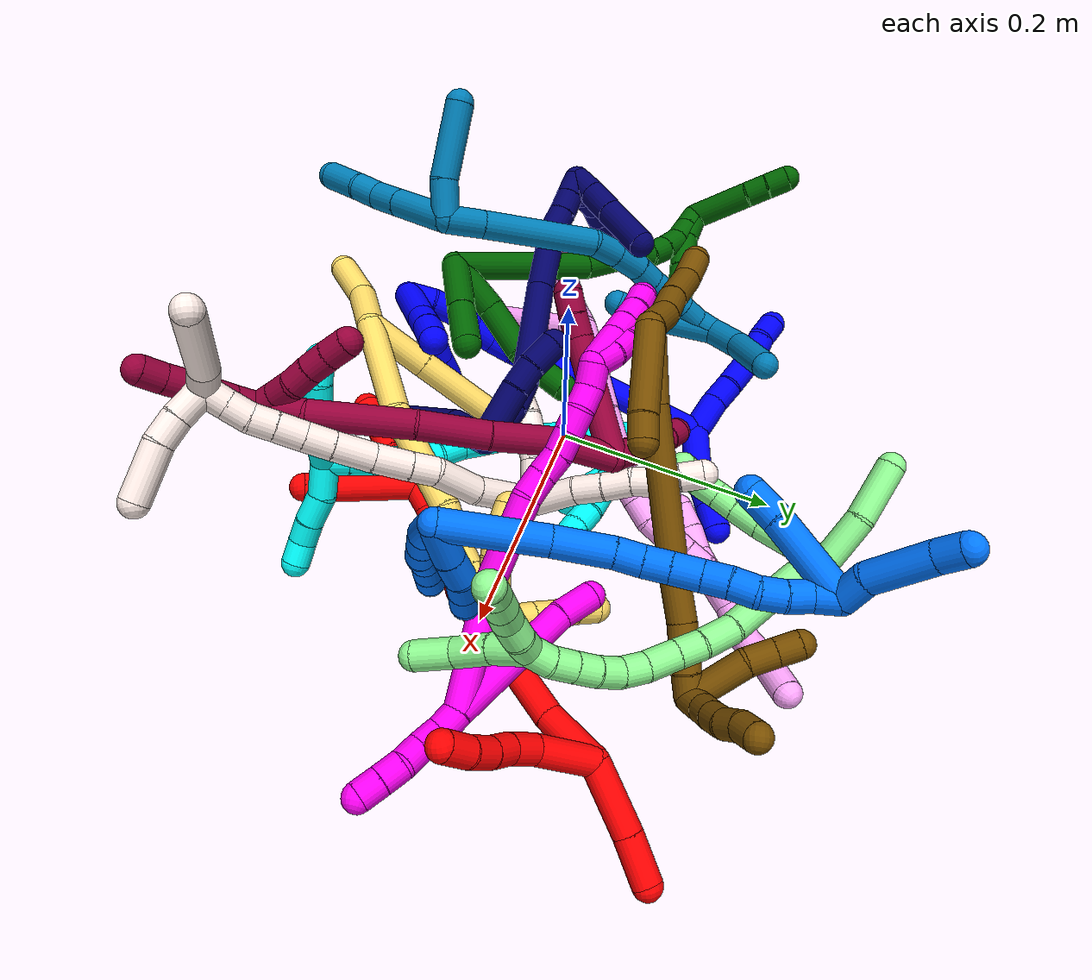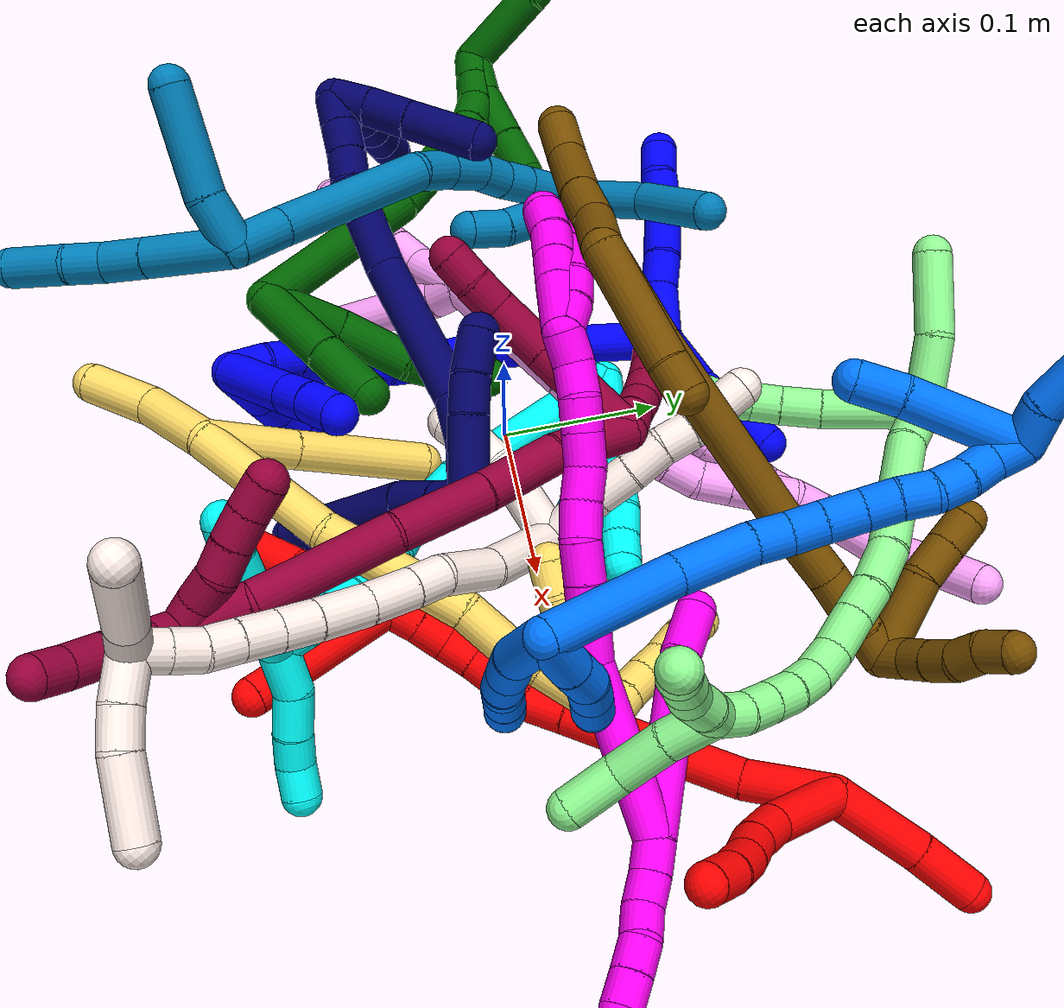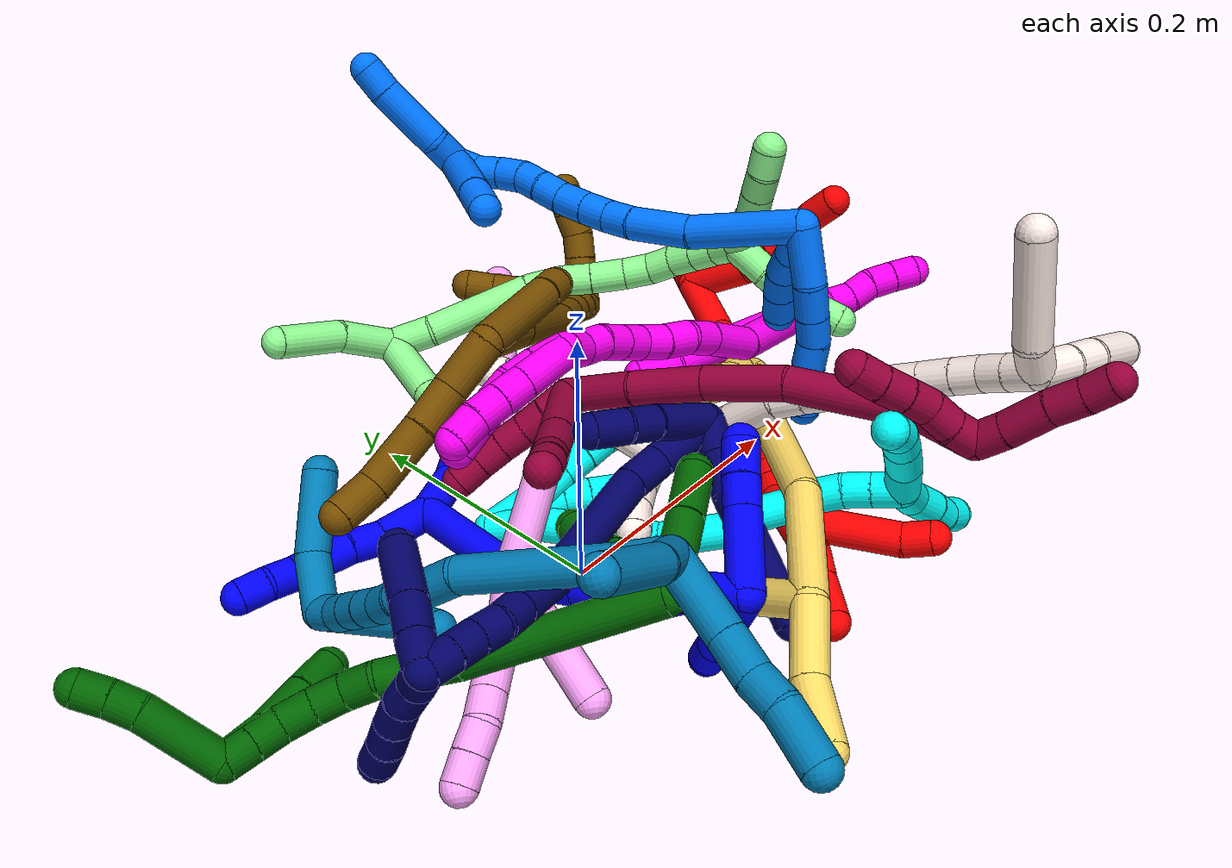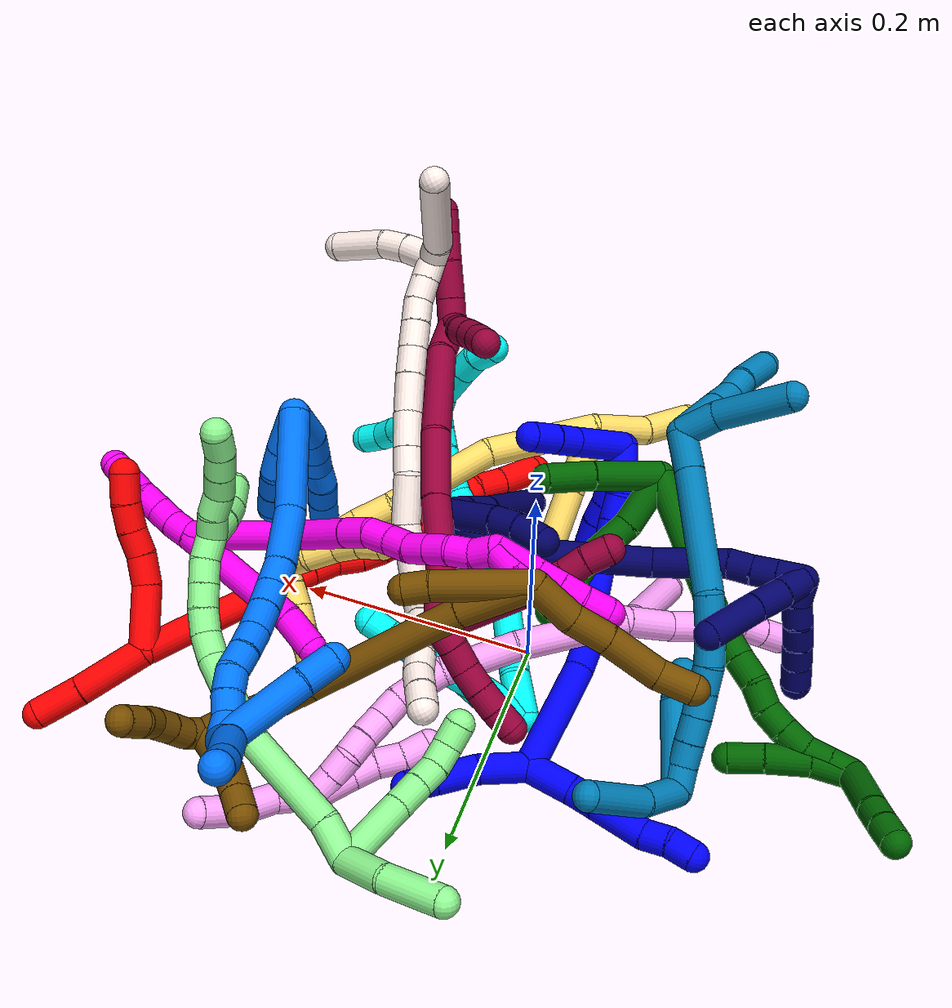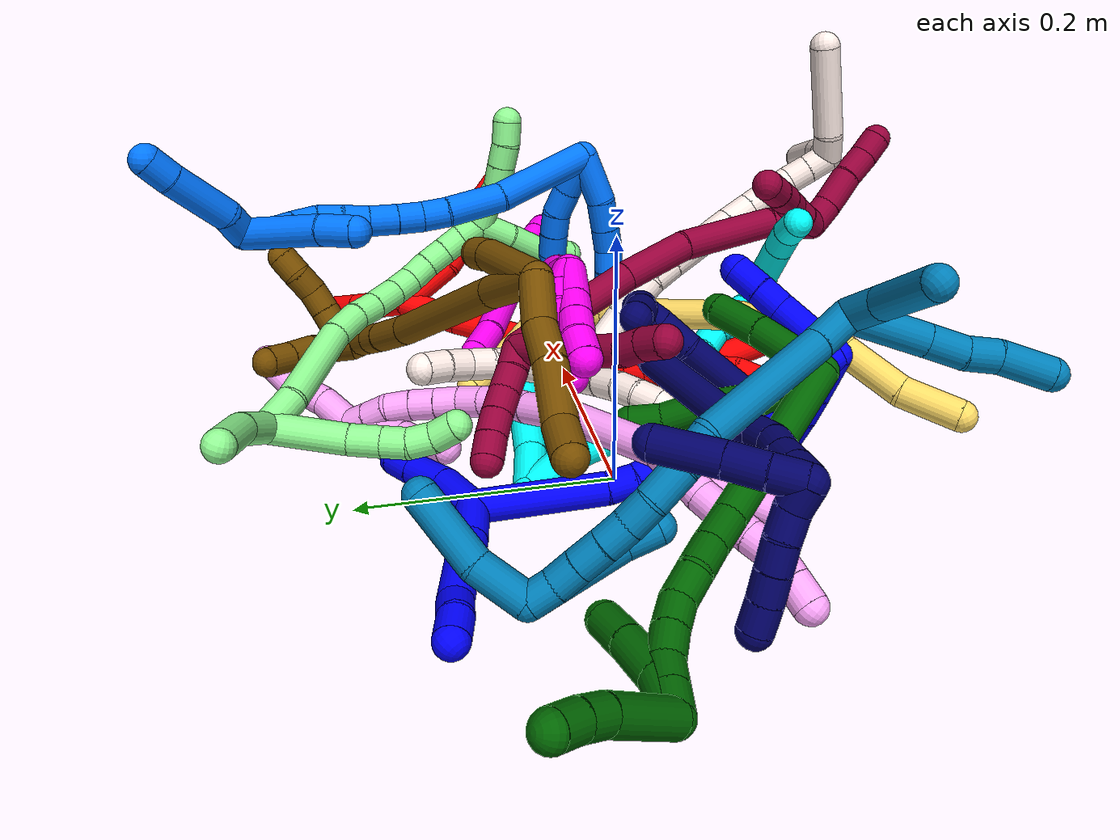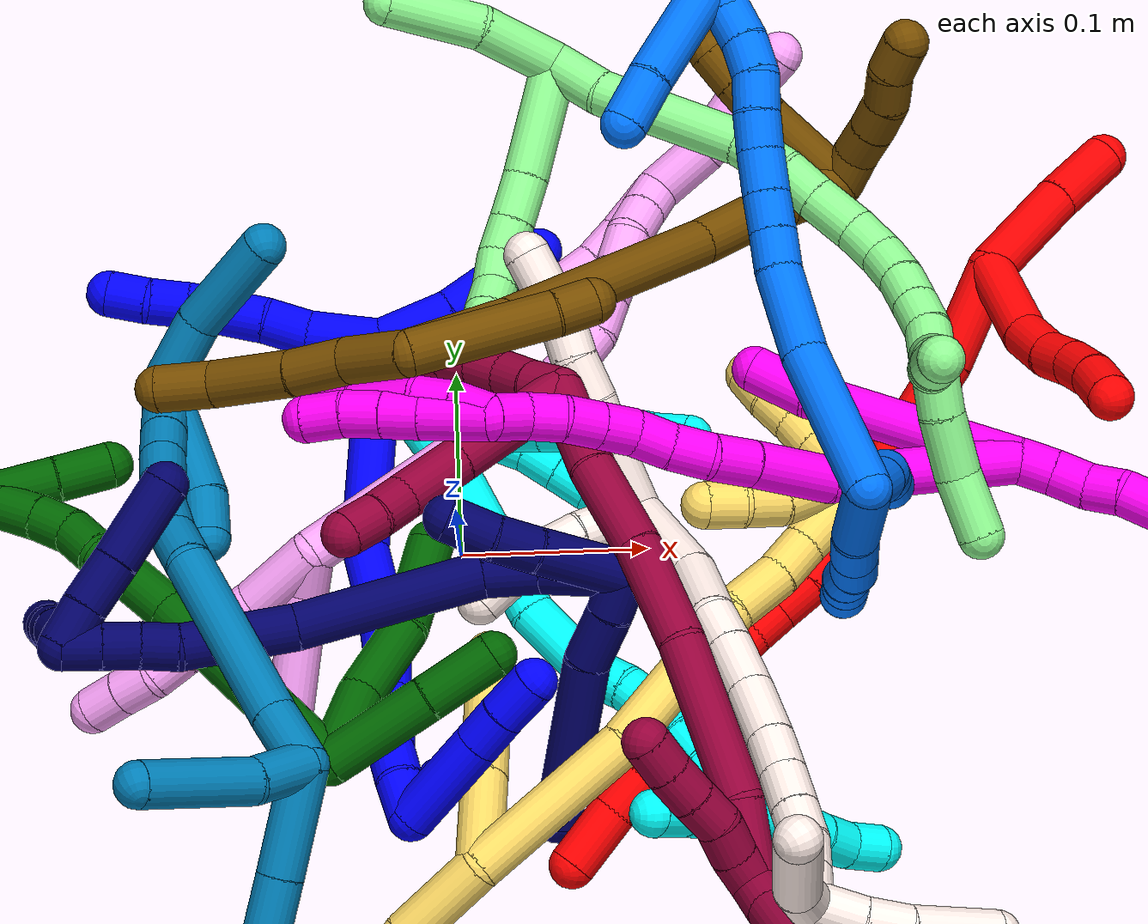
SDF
<sdf version="1.7">
 <world name="default">
  <plugin name="TubeGeneratorPlugin" filename="libtube_generator_plugin.so"/>
  <model name="photoneo_s_sensor">
   <static>1</static>
   <pose>0 0 2 1.57079 1.57079 3.14159</pose>
   <link name="link">
    <inertial><mass>0.1</mass></inertial>
    <sensor name="sensor" type="depth">
     <update_rate>30</update_rate>
     <camera>
      <horizontal_fov>1.22</horizontal_fov>
      <image><width>1920</width><height>1200</height><format>B8G8R8</format></image>
      <clip><near>0.1</near><far>4</far></clip>
      <depth_camera><output>points</output></depth_camera>
     </camera>
     <plugin name="camera_plugin" filename="libgazebo_ros_depth_camera.so">
      <baseline>0.2</baseline>
      <alwaysOn>1</alwaysOn>
      <updateRate>0.0</updateRate>
      <cameraName>camera_ir</cameraName>
      <imageTopicName>/camera/color/image_raw</imageTopicName>
      <cameraInfoTopicName>/camera/color/camera_info</cameraInfoTopicName>
      <depthImageTopicName>/camera/depth/image_raw</depthImageTopicName>
      <depthImageCameraInfoTopicName>/camera/depth/camera_info</depthImageCameraInfoTopicName>
      <pointCloudTopicName>/camera/depth/points</pointCloudTopicName>
      <frameName>fr_optical</frameName>
      <pointCloudCutoff>0.1</pointCloudCutoff>
      <pointCloudCutoffMax>2.0</pointCloudCutoffMax>
      <distortionK1>0</distortionK1>
      <distortionK2>0</distortionK2>
      <distortionK3>0</distortionK3>
      <distortionT1>0</distortionT1>
      <distortionT2>0</distortionT2>
      <CxPrime>0</CxPrime>
      <Cx>0</Cx>
      <Cy>0</Cy>
      <focalLength>0</focalLength>
      <hackBaseline>0</hackBaseline>
     </plugin>
    </sensor>
   </link>
  </model>
  <gravity>0 0 -9.8</gravity>
  <magnetic_field>6e-06 2.3e-05 -4.2e-05</magnetic_field>
  <atmosphere type="adiabatic"/>
  <physics name="default_physics" default="0" type="ode">
   <max_step_size>0.003</max_step_size>
   <real_time_factor>1</real_time_factor>
   <real_time_update_rate>1000</real_time_update_rate>
   <max_contacts>10000</max_contacts>
   <ode>
    <solver>
     <type>quick</type>
     <iters>100</iters>
     <sor>1.3</sor>
     <use_dynamic_moi_rescaling>0</use_dynamic_moi_rescaling>
    </solver>
    <constraints>
     <contact_max_correcting_vel>0</contact_max_correcting_vel>
     <contact_surface_layer>0.001</contact_surface_layer>
     <cfm>0</cfm>
     <erp>0.2</erp>
    </constraints>
   </ode>
  </physics>
  <scene><ambient>0.4 0.4 0.4 1</ambient><background>0.7 0.7 0.7 1</background><shadows>0</shadows></scene>
  <audio><device>default</device></audio>
  <spherical_coordinates>
   <surface_model>EARTH_WGS84</surface_model>
   <latitude_deg>0</latitude_deg>
   <longitude_deg>0</longitude_deg>
   <elevation>0</elevation>
   <heading_deg>0</heading_deg>
  </spherical_coordinates>
  <model name="bin">
   <static>1</static>
   <link name="bottom">
    <collision name="collision-bottom">
     <pose>0 0 -0.01 0 -0 0</pose>
     <geometry><box><size>0.8 0.6 0.02</size></box></geometry>
     <surface>
      <friction><ode><mu>100</mu><mu2>100</mu2></ode></friction>
      <contact><collide_bitmask>65535</collide_bitmask></contact>
     </surface>
    </collision>
   </link>
   <link name="west_wall">
    <collision name="collision-west_wall">
     <pose>-0.41 0 0.1 0 -0 0</pose>
     <geometry><box><size>0.02 0.6 0.2</size></box></geometry>
     <surface>
      <friction><ode><mu>100</mu><mu2>100</mu2></ode></friction>
      <contact><collide_bitmask>65535</collide_bitmask></contact>
     </surface>
    </collision>
   </link>
   <link name="east_wall">
    <collision name="collision-east_wall">
     <pose>0.41 0 0.1 0 -0 0</pose>
     <geometry><box><size>0.02 0.6 0.2</size></box></geometry>
     <surface>
      <friction><ode><mu>100</mu><mu2>100</mu2></ode></friction>
      <contact><collide_bitmask>65535</collide_bitmask></contact>
     </surface>
    </collision>
   </link>
   <link name="south_wall">
    <collision name="collision-south_wall">
     <pose>0 -0.31 0.1 0 -0 0</pose>
     <geometry><box><size>0.8 0.02 0.2</size></box></geometry>
     <surface>
      <friction><ode><mu>100</mu><mu2>100</mu2></ode></friction>
      <contact><collide_bitmask>65535</collide_bitmask></contact>
     </surface>
    </collision>
   </link>
   <link name="north_wall">
    <collision name="collision-north_wall">
     <pose>0 0.31 0.1 0 -0 0</pose>
     <geometry><box><size>0.8 0.02 0.2</size></box></geometry>
     <surface>
      <friction><ode><mu>100</mu><mu2>100</mu2></ode></friction>
      <contact><collide_bitmask>65535</collide_bitmask></contact>
     </surface>
    </collision>
   </link>
  </model>
  <model name="1">
   <static>0</static>
   <link name="1">
    <collision name="collision-cylinder-e_1_2_8">
     <pose>-0.012426 0.006484 -0.013899 -2.7051 -0.680944 2.02292</pose>
     <geometry><cylinder><radius>0.0125</radius><length>0.039478</length></cylinder></geometry>
     <surface>
      <friction><ode><mu>1.16</mu><mu2>1.16</mu2><slip1>0</slip1><slip2>0</slip2></ode></friction>
      <contact><ode><kp>1e+06</kp><kd>1</kd><max_vel>0</max_vel><min_depth>0.001</min_depth></ode></contact>
     </surface>
    </collision>
    <visual name="visual-cylinder-e_1_2_8">
     <pose>-0.012426 0.006484 -0.013899 -2.7051 -0.680944 2.02292</pose>
     <geometry><cylinder><radius>0.0125</radius><length>0.039478</length></cylinder></geometry>
     <material><ambient>0 0 1 1</ambient></material>
    </visual>
    <collision name="collision-cylinder-e_2_8_9">
     <pose>-0.034166 0.017015 -0.034356 -2.58868 -0.879548 2.05633</pose>
     <geometry><cylinder><radius>0.0125</radius><length>0.024177</length></cylinder></geometry>
     <surface>
      <friction><ode><mu>1.16</mu><mu2>1.16</mu2><slip1>0</slip1><slip2>0</slip2></ode></friction>
      <contact><ode><kp>1e+06</kp><kd>1</kd><max_vel>0</max_vel><min_depth>0.001</min_depth></ode></contact>
     </surface>
    </collision>
    <visual name="visual-cylinder-e_2_8_9">
     <pose>-0.034166 0.017015 -0.034356 -2.58868 -0.879548 2.05633</pose>
     <geometry><cylinder><radius>0.0125</radius><length>0.024177</length></cylinder></geometry>
     <material><ambient>0 0 1 1</ambient></material>
    </visual>
    <collision name="collision-cylinder-e_3_9_10">
     <pose>-0.057711 0.029332 -0.055064 -2.61272 -0.715034 1.88719</pose>
     <geometry><cylinder><radius>0.0125</radius><length>0.043412</length></cylinder></geometry>
     <surface>
      <friction><ode><mu>1.16</mu><mu2>1.16</mu2><slip1>0</slip1><slip2>0</slip2></ode></friction>
      <contact><ode><kp>1e+06</kp><kd>1</kd><max_vel>0</max_vel><min_depth>0.001</min_depth></ode></contact>
     </surface>
    </collision>
    <visual name="visual-cylinder-e_3_9_10">
     <pose>-0.057711 0.029332 -0.055064 -2.61272 -0.715034 1.88719</pose>
     <geometry><cylinder><radius>0.0125</radius><length>0.043412</length></cylinder></geometry>
     <material><ambient>0 0 1 1</ambient></material>
    </visual>
    <collision name="collision-cylinder-e_4_10_11">
     <pose>-0.080291 0.03873 -0.076037 -2.97764 -0.879046 2.79562</pose>
     <geometry><cylinder><radius>0.0125</radius><length>0.021681</length></cylinder></geometry>
     <surface>
      <friction><ode><mu>1.16</mu><mu2>1.16</mu2><slip1>0</slip1><slip2>0</slip2></ode></friction>
      <contact><ode><kp>1e+06</kp><kd>1</kd><max_vel>0</max_vel><min_depth>0.001</min_depth></ode></contact>
     </surface>
    </collision>
    <visual name="visual-cylinder-e_4_10_11">
     <pose>-0.080291 0.03873 -0.076037 -2.97764 -0.879046 2.79562</pose>
     <geometry><cylinder><radius>0.0125</radius><length>0.021681</length></cylinder></geometry>
     <material><ambient>0 0 1 1</ambient></material>
    </visual>
    <collision name="collision-cylinder-e_5_11_6">
     <pose>-0.095679 0.043736 -0.089811 -2.63281 -0.724077 1.93828</pose>
     <geometry><cylinder><radius>0.0125</radius><length>0.021252</length></cylinder></geometry>
     <surface>
      <friction><ode><mu>1.16</mu><mu2>1.16</mu2><slip1>0</slip1><slip2>0</slip2></ode></friction>
      <contact><ode><kp>1e+06</kp><kd>1</kd><max_vel>0</max_vel><min_depth>0.001</min_depth></ode></contact>
     </surface>
    </collision>
    <visual name="visual-cylinder-e_5_11_6">
     <pose>-0.095679 0.043736 -0.089811 -2.63281 -0.724077 1.93828</pose>
     <geometry><cylinder><radius>0.0125</radius><length>0.021252</length></cylinder></geometry>
     <material><ambient>0 0 1 1</ambient></material>
    </visual>
    <collision name="collision-cylinder-e_1_2_12">
     <pose>0.008932 0.00348 0.018039 -0.190579 0.452537 -0.044</pose>
     <geometry><cylinder><radius>0.0125</radius><length>0.040857</length></cylinder></geometry>
     <surface>
      <friction><ode><mu>1.16</mu><mu2>1.16</mu2><slip1>0</slip1><slip2>0</slip2></ode></friction>
      <contact><ode><kp>1e+06</kp><kd>1</kd><max_vel>0</max_vel><min_depth>0.001</min_depth></ode></contact>
     </surface>
    </collision>
    <visual name="visual-cylinder-e_1_2_12">
     <pose>0.008932 0.00348 0.018039 -0.190579 0.452537 -0.044</pose>
     <geometry><cylinder><radius>0.0125</radius><length>0.040857</length></cylinder></geometry>
     <material><ambient>0 0 1 1</ambient></material>
    </visual>
    <collision name="collision-cylinder-e_2_12_13">
     <pose>0.023378 0.013154 0.051556 -0.380665 0.319409 -0.062047</pose>
     <geometry><cylinder><radius>0.0125</radius><length>0.035117</length></cylinder></geometry>
     <surface>
      <friction><ode><mu>1.16</mu><mu2>1.16</mu2><slip1>0</slip1><slip2>0</slip2></ode></friction>
      <contact><ode><kp>1e+06</kp><kd>1</kd><max_vel>0</max_vel><min_depth>0.001</min_depth></ode></contact>
     </surface>
    </collision>
    <visual name="visual-cylinder-e_2_12_13">
     <pose>0.023378 0.013154 0.051556 -0.380665 0.319409 -0.062047</pose>
     <geometry><cylinder><radius>0.0125</radius><length>0.035117</length></cylinder></geometry>
     <material><ambient>0 0 1 1</ambient></material>
    </visual>
    <collision name="collision-cylinder-e_3_13_5">
     <pose>0.032476 0.023022 0.077894 -0.326198 0.302975 -0.050232</pose>
     <geometry><cylinder><radius>0.0125</radius><length>0.024027</length></cylinder></geometry>
     <surface>
      <friction><ode><mu>1.16</mu><mu2>1.16</mu2><slip1>0</slip1><slip2>0</slip2></ode></friction>
      <contact><ode><kp>1e+06</kp><kd>1</kd><max_vel>0</max_vel><min_depth>0.001</min_depth></ode></contact>
     </surface>
    </collision>
    <visual name="visual-cylinder-e_3_13_5">
     <pose>0.032476 0.023022 0.077894 -0.326198 0.302975 -0.050232</pose>
     <geometry><cylinder><radius>0.0125</radius><length>0.024027</length></cylinder></geometry>
     <material><ambient>0 0 1 1</ambient></material>
    </visual>
    <collision name="collision-cylinder-e_1_2_14">
     <pose>0.014229 -0.039846 -0.02563 2.1424 0.29177 0.525947</pose>
     <geometry><cylinder><radius>0.0125</radius><length>0.098935</length></cylinder></geometry>
     <surface>
      <friction><ode><mu>1.16</mu><mu2>1.16</mu2><slip1>0</slip1><slip2>0</slip2></ode></friction>
      <contact><ode><kp>1e+06</kp><kd>1</kd><max_vel>0</max_vel><min_depth>0.001</min_depth></ode></contact>
     </surface>
    </collision>
    <visual name="visual-cylinder-e_1_2_14">
     <pose>0.014229 -0.039846 -0.02563 2.1424 0.29177 0.525947</pose>
     <geometry><cylinder><radius>0.0125</radius><length>0.098935</length></cylinder></geometry>
     <material><ambient>0 0 1 1</ambient></material>
    </visual>
    <collision name="collision-cylinder-e_2_14_15">
     <pose>0.030984 -0.089162 -0.055471 1.98926 0.238986 0.365474</pose>
     <geometry><cylinder><radius>0.0125</radius><length>0.021337</length></cylinder></geometry>
     <surface>
      <friction><ode><mu>1.16</mu><mu2>1.16</mu2><slip1>0</slip1><slip2>0</slip2></ode></friction>
      <contact><ode><kp>1e+06</kp><kd>1</kd><max_vel>0</max_vel><min_depth>0.001</min_depth></ode></contact>
     </surface>
    </collision>
    <visual name="visual-cylinder-e_2_14_15">
     <pose>0.030984 -0.089162 -0.055471 1.98926 0.238986 0.365474</pose>
     <geometry><cylinder><radius>0.0125</radius><length>0.021337</length></cylinder></geometry>
     <material><ambient>0 0 1 1</ambient></material>
    </visual>
    <collision name="collision-cylinder-e_3_15_16">
     <pose>0.039253 -0.115187 -0.06298 1.76739 0.32799 0.398039</pose>
     <geometry><cylinder><radius>0.0125</radius><length>0.035659</length></cylinder></geometry>
     <surface>
      <friction><ode><mu>1.16</mu><mu2>1.16</mu2><slip1>0</slip1><slip2>0</slip2></ode></friction>
      <contact><ode><kp>1e+06</kp><kd>1</kd><max_vel>0</max_vel><min_depth>0.001</min_depth></ode></contact>
     </surface>
    </collision>
    <visual name="visual-cylinder-e_3_15_16">
     <pose>0.039253 -0.115187 -0.06298 1.76739 0.32799 0.398039</pose>
     <geometry><cylinder><radius>0.0125</radius><length>0.035659</length></cylinder></geometry>
     <material><ambient>0 0 1 1</ambient></material>
    </visual>
    <collision name="collision-cylinder-e_4_16_17">
     <pose>0.048383 -0.147668 -0.069784 1.78748 0.204755 0.254248</pose>
     <geometry><cylinder><radius>0.0125</radius><length>0.033312</length></cylinder></geometry>
     <surface>
      <friction><ode><mu>1.16</mu><mu2>1.16</mu2><slip1>0</slip1><slip2>0</slip2></ode></friction>
      <contact><ode><kp>1e+06</kp><kd>1</kd><max_vel>0</max_vel><min_depth>0.001</min_depth></ode></contact>
     </surface>
    </collision>
    <visual name="visual-cylinder-e_4_16_17">
     <pose>0.048383 -0.147668 -0.069784 1.78748 0.204755 0.254248</pose>
     <geometry><cylinder><radius>0.0125</radius><length>0.033312</length></cylinder></geometry>
     <material><ambient>0 0 1 1</ambient></material>
    </visual>
    <collision name="collision-cylinder-e_5_17_18">
     <pose>0.053559 -0.173601 -0.076866 1.91401 0.166827 0.236222</pose>
     <geometry><cylinder><radius>0.0125</radius><length>0.02155</length></cylinder></geometry>
     <surface>
      <friction><ode><mu>1.16</mu><mu2>1.16</mu2><slip1>0</slip1><slip2>0</slip2></ode></friction>
      <contact><ode><kp>1e+06</kp><kd>1</kd><max_vel>0</max_vel><min_depth>0.001</min_depth></ode></contact>
     </surface>
    </collision>
    <visual name="visual-cylinder-e_5_17_18">
     <pose>0.053559 -0.173601 -0.076866 1.91401 0.166827 0.236222</pose>
     <geometry><cylinder><radius>0.0125</radius><length>0.02155</length></cylinder></geometry>
     <material><ambient>0 0 1 1</ambient></material>
    </visual>
    <collision name="collision-cylinder-e_6_18_19">
     <pose>0.05521 -0.194988 -0.081644 1.67608 -0.012127 -0.013476</pose>
     <geometry><cylinder><radius>0.0125</radius><length>0.022891</length></cylinder></geometry>
     <surface>
      <friction><ode><mu>1.16</mu><mu2>1.16</mu2><slip1>0</slip1><slip2>0</slip2></ode></friction>
      <contact><ode><kp>1e+06</kp><kd>1</kd><max_vel>0</max_vel><min_depth>0.001</min_depth></ode></contact>
     </surface>
    </collision>
    <visual name="visual-cylinder-e_6_18_19">
     <pose>0.05521 -0.194988 -0.081644 1.67608 -0.012127 -0.013476</pose>
     <geometry><cylinder><radius>0.0125</radius><length>0.022891</length></cylinder></geometry>
     <material><ambient>0 0 1 1</ambient></material>
    </visual>
    <collision name="collision-cylinder-e_7_19_20">
     <pose>0.05368 -0.217306 -0.083715 1.65002 -0.1261 -0.136477</pose>
     <geometry><cylinder><radius>0.0125</radius><length>0.022117</length></cylinder></geometry>
     <surface>
      <friction><ode><mu>1.16</mu><mu2>1.16</mu2><slip1>0</slip1><slip2>0</slip2></ode></friction>
      <contact><ode><kp>1e+06</kp><kd>1</kd><max_vel>0</max_vel><min_depth>0.001</min_depth></ode></contact>
     </surface>
    </collision>
    <visual name="visual-cylinder-e_7_19_20">
     <pose>0.05368 -0.217306 -0.083715 1.65002 -0.1261 -0.136477</pose>
     <geometry><cylinder><radius>0.0125</radius><length>0.022117</length></cylinder></geometry>
     <material><ambient>0 0 1 1</ambient></material>
    </visual>
    <collision name="collision-cylinder-e_8_20_21">
     <pose>0.053909 -0.238895 -0.085261 1.63432 0.150591 0.160433</pose>
     <geometry><cylinder><radius>0.0125</radius><length>0.021592</length></cylinder></geometry>
     <surface>
      <friction><ode><mu>1.16</mu><mu2>1.16</mu2><slip1>0</slip1><slip2>0</slip2></ode></friction>
      <contact><ode><kp>1e+06</kp><kd>1</kd><max_vel>0</max_vel><min_depth>0.001</min_depth></ode></contact>
     </surface>
    </collision>
    <visual name="visual-cylinder-e_8_20_21">
     <pose>0.053909 -0.238895 -0.085261 1.63432 0.150591 0.160433</pose>
     <geometry><cylinder><radius>0.0125</radius><length>0.021592</length></cylinder></geometry>
     <material><ambient>0 0 1 1</ambient></material>
    </visual>
    <collision name="collision-cylinder-e_9_21_1">
     <pose>0.059217 -0.260165 -0.087123 1.68186 0.332475 0.370768</pose>
     <geometry><cylinder><radius>0.0125</radius><length>0.022606</length></cylinder></geometry>
     <surface>
      <friction><ode><mu>1.16</mu><mu2>1.16</mu2><slip1>0</slip1><slip2>0</slip2></ode></friction>
      <contact><ode><kp>1e+06</kp><kd>1</kd><max_vel>0</max_vel><min_depth>0.001</min_depth></ode></contact>
     </surface>
    </collision>
    <visual name="visual-cylinder-e_9_21_1">
     <pose>0.059217 -0.260165 -0.087123 1.68186 0.332475 0.370768</pose>
     <geometry><cylinder><radius>0.0125</radius><length>0.022606</length></cylinder></geometry>
     <material><ambient>0 0 1 1</ambient></material>
    </visual>
    <collision name="collision-cylinder-e_1_1_22">
     <pose>0.072305 -0.255799 -0.090681 -1.72793 0.554666 -0.643481</pose>
     <geometry><cylinder><radius>0.0125</radius><length>0.035692</length></cylinder></geometry>
     <surface>
      <friction><ode><mu>1.16</mu><mu2>1.16</mu2><slip1>0</slip1><slip2>0</slip2></ode></friction>
      <contact><ode><kp>1e+06</kp><kd>1</kd><max_vel>0</max_vel><min_depth>0.001</min_depth></ode></contact>
     </surface>
    </collision>
    <visual name="visual-cylinder-e_1_1_22">
     <pose>0.072305 -0.255799 -0.090681 -1.72793 0.554666 -0.643481</pose>
     <geometry><cylinder><radius>0.0125</radius><length>0.035692</length></cylinder></geometry>
     <material><ambient>0 0 1 1</ambient></material>
    </visual>
    <collision name="collision-cylinder-e_2_22_23">
     <pose>0.087101 -0.231978 -0.094212 -1.70103 0.544435 -0.615945</pose>
     <geometry><cylinder><radius>0.0125</radius><length>0.020838</length></cylinder></geometry>
     <surface>
      <friction><ode><mu>1.16</mu><mu2>1.16</mu2><slip1>0</slip1><slip2>0</slip2></ode></friction>
      <contact><ode><kp>1e+06</kp><kd>1</kd><max_vel>0</max_vel><min_depth>0.001</min_depth></ode></contact>
     </surface>
    </collision>
    <visual name="visual-cylinder-e_2_22_23">
     <pose>0.087101 -0.231978 -0.094212 -1.70103 0.544435 -0.615945</pose>
     <geometry><cylinder><radius>0.0125</radius><length>0.020838</length></cylinder></geometry>
     <material><ambient>0 0 1 1</ambient></material>
    </visual>
    <collision name="collision-cylinder-e_3_23_24">
     <pose>0.098742 -0.214962 -0.095567 -1.59488 0.651982 -0.666736</pose>
     <geometry><cylinder><radius>0.0125</radius><length>0.020587</length></cylinder></geometry>
     <surface>
      <friction><ode><mu>1.16</mu><mu2>1.16</mu2><slip1>0</slip1><slip2>0</slip2></ode></friction>
      <contact><ode><kp>1e+06</kp><kd>1</kd><max_vel>0</max_vel><min_depth>0.001</min_depth></ode></contact>
     </surface>
    </collision>
    <visual name="visual-cylinder-e_3_23_24">
     <pose>0.098742 -0.214962 -0.095567 -1.59488 0.651982 -0.666736</pose>
     <geometry><cylinder><radius>0.0125</radius><length>0.020587</length></cylinder></geometry>
     <material><ambient>0 0 1 1</ambient></material>
    </visual>
    <collision name="collision-cylinder-e_4_24_4">
     <pose>0.111029 -0.197125 -0.096836 -1.68139 0.556249 -0.617567</pose>
     <geometry><cylinder><radius>0.0125</radius><length>0.022883</length></cylinder></geometry>
     <surface>
      <friction><ode><mu>1.16</mu><mu2>1.16</mu2><slip1>0</slip1><slip2>0</slip2></ode></friction>
      <contact><ode><kp>1e+06</kp><kd>1</kd><max_vel>0</max_vel><min_depth>0.001</min_depth></ode></contact>
     </surface>
    </collision>
    <visual name="visual-cylinder-e_4_24_4">
     <pose>0.111029 -0.197125 -0.096836 -1.68139 0.556249 -0.617567</pose>
     <geometry><cylinder><radius>0.0125</radius><length>0.022883</length></cylinder></geometry>
     <material><ambient>0 0 1 1</ambient></material>
    </visual>
    <collision name="collision-cylinder-e_1_1_25">
     <pose>0.05849 -0.269211 -0.0615 -0.058564 -0.163002 0.004785</pose>
     <geometry><cylinder><radius>0.0125</radius><length>0.054428</length></cylinder></geometry>
     <surface>
      <friction><ode><mu>1.16</mu><mu2>1.16</mu2><slip1>0</slip1><slip2>0</slip2></ode></friction>
      <contact><ode><kp>1e+06</kp><kd>1</kd><max_vel>0</max_vel><min_depth>0.001</min_depth></ode></contact>
     </surface>
    </collision>
    <visual name="visual-cylinder-e_1_1_25">
     <pose>0.05849 -0.269211 -0.0615 -0.058564 -0.163002 0.004785</pose>
     <geometry><cylinder><radius>0.0125</radius><length>0.054428</length></cylinder></geometry>
     <material><ambient>0 0 1 1</ambient></material>
    </visual>
    <collision name="collision-cylinder-e_2_25_26">
     <pose>0.052088 -0.267221 -0.024387 -0.040579 -0.190236 0.003872</pose>
     <geometry><cylinder><radius>0.0125</radius><length>0.021006</length></cylinder></geometry>
     <surface>
      <friction><ode><mu>1.16</mu><mu2>1.16</mu2><slip1>0</slip1><slip2>0</slip2></ode></friction>
      <contact><ode><kp>1e+06</kp><kd>1</kd><max_vel>0</max_vel><min_depth>0.001</min_depth></ode></contact>
     </surface>
    </collision>
    <visual name="visual-cylinder-e_2_25_26">
     <pose>0.052088 -0.267221 -0.024387 -0.040579 -0.190236 0.003872</pose>
     <geometry><cylinder><radius>0.0125</radius><length>0.021006</length></cylinder></geometry>
     <material><ambient>0 0 1 1</ambient></material>
    </visual>
    <collision name="collision-cylinder-e_3_26_3">
     <pose>0.048603 -0.266118 -0.00191 -0.056198 -0.122297 0.003442</pose>
     <geometry><cylinder><radius>0.0125</radius><length>0.024566</length></cylinder></geometry>
     <surface>
      <friction><ode><mu>1.16</mu><mu2>1.16</mu2><slip1>0</slip1><slip2>0</slip2></ode></friction>
      <contact><ode><kp>1e+06</kp><kd>1</kd><max_vel>0</max_vel><min_depth>0.001</min_depth></ode></contact>
     </surface>
    </collision>
    <visual name="visual-cylinder-e_3_26_3">
     <pose>0.048603 -0.266118 -0.00191 -0.056198 -0.122297 0.003442</pose>
     <geometry><cylinder><radius>0.0125</radius><length>0.024566</length></cylinder></geometry>
     <material><ambient>0 0 1 1</ambient></material>
    </visual>
    <collision name="collision-sphere-3">
     <pose>0.047105 -0.265433 0.010262 0 -0 0</pose>
     <geometry><sphere><radius>0.0125</radius></sphere></geometry>
     <surface>
      <friction><ode><mu>1.16</mu><mu2>1.16</mu2><slip1>0</slip1><slip2>0</slip2></ode></friction>
      <contact><ode><kp>1e+06</kp><kd>1</kd><max_vel>0</max_vel><min_depth>0.001</min_depth></ode></contact>
     </surface>
    </collision>
    <visual name="visual-sphere-3">
     <pose>0.047105 -0.265433 0.010262 0 -0 0</pose>
     <geometry><sphere><radius>0.0125</radius></sphere></geometry>
     <material><ambient>0 0 1 1</ambient></material>
    </visual>
    <collision name="collision-sphere-26">
     <pose>0.050102 -0.266803 -0.014082 0 -0 0</pose>
     <geometry><sphere><radius>0.0125</radius></sphere></geometry>
     <surface>
      <friction><ode><mu>1.16</mu><mu2>1.16</mu2><slip1>0</slip1><slip2>0</slip2></ode></friction>
      <contact><ode><kp>1e+06</kp><kd>1</kd><max_vel>0</max_vel><min_depth>0.001</min_depth></ode></contact>
     </surface>
    </collision>
    <visual name="visual-sphere-26">
     <pose>0.050102 -0.266803 -0.014082 0 -0 0</pose>
     <geometry><sphere><radius>0.0125</radius></sphere></geometry>
     <material><ambient>0 0 1 1</ambient></material>
    </visual>
    <collision name="collision-sphere-25">
     <pose>0.054074 -0.267639 -0.034692 0 -0 0</pose>
     <geometry><sphere><radius>0.0125</radius></sphere></geometry>
     <surface>
      <friction><ode><mu>1.16</mu><mu2>1.16</mu2><slip1>0</slip1><slip2>0</slip2></ode></friction>
      <contact><ode><kp>1e+06</kp><kd>1</kd><max_vel>0</max_vel><min_depth>0.001</min_depth></ode></contact>
     </surface>
    </collision>
    <visual name="visual-sphere-25">
     <pose>0.054074 -0.267639 -0.034692 0 -0 0</pose>
     <geometry><sphere><radius>0.0125</radius></sphere></geometry>
     <material><ambient>0 0 1 1</ambient></material>
    </visual>
    <collision name="collision-sphere-4">
     <pose>0.11707 -0.187468 -0.097909 0 -0 0</pose>
     <geometry><sphere><radius>0.0125</radius></sphere></geometry>
     <surface>
      <friction><ode><mu>1.16</mu><mu2>1.16</mu2><slip1>0</slip1><slip2>0</slip2></ode></friction>
      <contact><ode><kp>1e+06</kp><kd>1</kd><max_vel>0</max_vel><min_depth>0.001</min_depth></ode></contact>
     </surface>
    </collision>
    <visual name="visual-sphere-4">
     <pose>0.11707 -0.187468 -0.097909 0 -0 0</pose>
     <geometry><sphere><radius>0.0125</radius></sphere></geometry>
     <material><ambient>0 0 1 1</ambient></material>
    </visual>
    <collision name="collision-sphere-24">
     <pose>0.104988 -0.206782 -0.095764 0 -0 0</pose>
     <geometry><sphere><radius>0.0125</radius></sphere></geometry>
     <surface>
      <friction><ode><mu>1.16</mu><mu2>1.16</mu2><slip1>0</slip1><slip2>0</slip2></ode></friction>
      <contact><ode><kp>1e+06</kp><kd>1</kd><max_vel>0</max_vel><min_depth>0.001</min_depth></ode></contact>
     </surface>
    </collision>
    <visual name="visual-sphere-24">
     <pose>0.104988 -0.206782 -0.095764 0 -0 0</pose>
     <geometry><sphere><radius>0.0125</radius></sphere></geometry>
     <material><ambient>0 0 1 1</ambient></material>
    </visual>
    <collision name="collision-sphere-23">
     <pose>0.092497 -0.223141 -0.09537 0 -0 0</pose>
     <geometry><sphere><radius>0.0125</radius></sphere></geometry>
     <surface>
      <friction><ode><mu>1.16</mu><mu2>1.16</mu2><slip1>0</slip1><slip2>0</slip2></ode></friction>
      <contact><ode><kp>1e+06</kp><kd>1</kd><max_vel>0</max_vel><min_depth>0.001</min_depth></ode></contact>
     </surface>
    </collision>
    <visual name="visual-sphere-23">
     <pose>0.092497 -0.223141 -0.09537 0 -0 0</pose>
     <geometry><sphere><radius>0.0125</radius></sphere></geometry>
     <material><ambient>0 0 1 1</ambient></material>
    </visual>
    <collision name="collision-sphere-22">
     <pose>0.081704 -0.240815 -0.093055 0 -0 0</pose>
     <geometry><sphere><radius>0.0125</radius></sphere></geometry>
     <surface>
      <friction><ode><mu>1.16</mu><mu2>1.16</mu2><slip1>0</slip1><slip2>0</slip2></ode></friction>
      <contact><ode><kp>1e+06</kp><kd>1</kd><max_vel>0</max_vel><min_depth>0.001</min_depth></ode></contact>
     </surface>
    </collision>
    <visual name="visual-sphere-22">
     <pose>0.081704 -0.240815 -0.093055 0 -0 0</pose>
     <geometry><sphere><radius>0.0125</radius></sphere></geometry>
     <material><ambient>0 0 1 1</ambient></material>
    </visual>
    <collision name="collision-sphere-1">
     <pose>0.062906 -0.270783 -0.088307 0 -0 0</pose>
     <geometry><sphere><radius>0.0125</radius></sphere></geometry>
     <surface>
      <friction><ode><mu>1.16</mu><mu2>1.16</mu2><slip1>0</slip1><slip2>0</slip2></ode></friction>
      <contact><ode><kp>1e+06</kp><kd>1</kd><max_vel>0</max_vel><min_depth>0.001</min_depth></ode></contact>
     </surface>
    </collision>
    <visual name="visual-sphere-1">
     <pose>0.062906 -0.270783 -0.088307 0 -0 0</pose>
     <geometry><sphere><radius>0.0125</radius></sphere></geometry>
     <material><ambient>0 0 1 1</ambient></material>
    </visual>
    <collision name="collision-sphere-21">
     <pose>0.055528 -0.249547 -0.085938 0 -0 0</pose>
     <geometry><sphere><radius>0.0125</radius></sphere></geometry>
     <surface>
      <friction><ode><mu>1.16</mu><mu2>1.16</mu2><slip1>0</slip1><slip2>0</slip2></ode></friction>
      <contact><ode><kp>1e+06</kp><kd>1</kd><max_vel>0</max_vel><min_depth>0.001</min_depth></ode></contact>
     </surface>
    </collision>
    <visual name="visual-sphere-21">
     <pose>0.055528 -0.249547 -0.085938 0 -0 0</pose>
     <geometry><sphere><radius>0.0125</radius></sphere></geometry>
     <material><ambient>0 0 1 1</ambient></material>
    </visual>
    <collision name="collision-sphere-6">
     <pose>-0.102718 0.047613 -0.096763 0 -0 0</pose>
     <geometry><sphere><radius>0.0125</radius></sphere></geometry>
     <surface>
      <friction><ode><mu>1.16</mu><mu2>1.16</mu2><slip1>0</slip1><slip2>0</slip2></ode></friction>
      <contact><ode><kp>1e+06</kp><kd>1</kd><max_vel>0</max_vel><min_depth>0.001</min_depth></ode></contact>
     </surface>
    </collision>
    <visual name="visual-sphere-6">
     <pose>-0.102718 0.047613 -0.096763 0 -0 0</pose>
     <geometry><sphere><radius>0.0125</radius></sphere></geometry>
     <material><ambient>0 0 1 1</ambient></material>
    </visual>
    <collision name="collision-sphere-11">
     <pose>-0.08864 0.039858 -0.082859 0 -0 0</pose>
     <geometry><sphere><radius>0.0125</radius></sphere></geometry>
     <surface>
      <friction><ode><mu>1.16</mu><mu2>1.16</mu2><slip1>0</slip1><slip2>0</slip2></ode></friction>
      <contact><ode><kp>1e+06</kp><kd>1</kd><max_vel>0</max_vel><min_depth>0.001</min_depth></ode></contact>
     </surface>
    </collision>
    <visual name="visual-sphere-11">
     <pose>-0.08864 0.039858 -0.082859 0 -0 0</pose>
     <geometry><sphere><radius>0.0125</radius></sphere></geometry>
     <material><ambient>0 0 1 1</ambient></material>
    </visual>
    <collision name="collision-sphere-10">
     <pose>-0.071942 0.037601 -0.069215 0 -0 0</pose>
     <geometry><sphere><radius>0.0125</radius></sphere></geometry>
     <surface>
      <friction><ode><mu>1.16</mu><mu2>1.16</mu2><slip1>0</slip1><slip2>0</slip2></ode></friction>
      <contact><ode><kp>1e+06</kp><kd>1</kd><max_vel>0</max_vel><min_depth>0.001</min_depth></ode></contact>
     </surface>
    </collision>
    <visual name="visual-sphere-10">
     <pose>-0.071942 0.037601 -0.069215 0 -0 0</pose>
     <geometry><sphere><radius>0.0125</radius></sphere></geometry>
     <material><ambient>0 0 1 1</ambient></material>
    </visual>
    <collision name="collision-sphere-9">
     <pose>-0.04348 0.021062 -0.040914 0 -0 0</pose>
     <geometry><sphere><radius>0.0125</radius></sphere></geometry>
     <surface>
      <friction><ode><mu>1.16</mu><mu2>1.16</mu2><slip1>0</slip1><slip2>0</slip2></ode></friction>
      <contact><ode><kp>1e+06</kp><kd>1</kd><max_vel>0</max_vel><min_depth>0.001</min_depth></ode></contact>
     </surface>
    </collision>
    <visual name="visual-sphere-9">
     <pose>-0.04348 0.021062 -0.040914 0 -0 0</pose>
     <geometry><sphere><radius>0.0125</radius></sphere></geometry>
     <material><ambient>0 0 1 1</ambient></material>
    </visual>
    <collision name="collision-sphere-2">
     <geometry><sphere><radius>0.0125</radius></sphere></geometry>
     <surface>
      <friction><ode><mu>1.16</mu><mu2>1.16</mu2><slip1>0</slip1><slip2>0</slip2></ode></friction>
      <contact><ode><kp>1e+06</kp><kd>1</kd><max_vel>0</max_vel><min_depth>0.001</min_depth></ode></contact>
     </surface>
    </collision>
    <visual name="visual-sphere-2">
     <geometry><sphere><radius>0.0125</radius></sphere></geometry>
     <material><ambient>0 0 1 1</ambient></material>
    </visual>
    <collision name="collision-sphere-19">
     <pose>0.055071 -0.206369 -0.082847 0 -0 0</pose>
     <geometry><sphere><radius>0.0125</radius></sphere></geometry>
     <surface>
      <friction><ode><mu>1.16</mu><mu2>1.16</mu2><slip1>0</slip1><slip2>0</slip2></ode></friction>
      <contact><ode><kp>1e+06</kp><kd>1</kd><max_vel>0</max_vel><min_depth>0.001</min_depth></ode></contact>
     </surface>
    </collision>
    <visual name="visual-sphere-19">
     <pose>0.055071 -0.206369 -0.082847 0 -0 0</pose>
     <geometry><sphere><radius>0.0125</radius></sphere></geometry>
     <material><ambient>0 0 1 1</ambient></material>
    </visual>
    <collision name="collision-sphere-8">
     <pose>-0.024853 0.012968 -0.027798 0 -0 0</pose>
     <geometry><sphere><radius>0.0125</radius></sphere></geometry>
     <surface>
      <friction><ode><mu>1.16</mu><mu2>1.16</mu2><slip1>0</slip1><slip2>0</slip2></ode></friction>
      <contact><ode><kp>1e+06</kp><kd>1</kd><max_vel>0</max_vel><min_depth>0.001</min_depth></ode></contact>
     </surface>
    </collision>
    <visual name="visual-sphere-8">
     <pose>-0.024853 0.012968 -0.027798 0 -0 0</pose>
     <geometry><sphere><radius>0.0125</radius></sphere></geometry>
     <material><ambient>0 0 1 1</ambient></material>
    </visual>
    <collision name="collision-sphere-12">
     <pose>0.017864 0.00696 0.036079 0 -0 0</pose>
     <geometry><sphere><radius>0.0125</radius></sphere></geometry>
     <surface>
      <friction><ode><mu>1.16</mu><mu2>1.16</mu2><slip1>0</slip1><slip2>0</slip2></ode></friction>
      <contact><ode><kp>1e+06</kp><kd>1</kd><max_vel>0</max_vel><min_depth>0.001</min_depth></ode></contact>
     </surface>
    </collision>
    <visual name="visual-sphere-12">
     <pose>0.017864 0.00696 0.036079 0 -0 0</pose>
     <geometry><sphere><radius>0.0125</radius></sphere></geometry>
     <material><ambient>0 0 1 1</ambient></material>
    </visual>
    <collision name="collision-sphere-13">
     <pose>0.028891 0.019348 0.067033 0 -0 0</pose>
     <geometry><sphere><radius>0.0125</radius></sphere></geometry>
     <surface>
      <friction><ode><mu>1.16</mu><mu2>1.16</mu2><slip1>0</slip1><slip2>0</slip2></ode></friction>
      <contact><ode><kp>1e+06</kp><kd>1</kd><max_vel>0</max_vel><min_depth>0.001</min_depth></ode></contact>
     </surface>
    </collision>
    <visual name="visual-sphere-13">
     <pose>0.028891 0.019348 0.067033 0 -0 0</pose>
     <geometry><sphere><radius>0.0125</radius></sphere></geometry>
     <material><ambient>0 0 1 1</ambient></material>
    </visual>
    <collision name="collision-sphere-5">
     <pose>0.03606 0.026696 0.088756 0 -0 0</pose>
     <geometry><sphere><radius>0.0125</radius></sphere></geometry>
     <surface>
      <friction><ode><mu>1.16</mu><mu2>1.16</mu2><slip1>0</slip1><slip2>0</slip2></ode></friction>
      <contact><ode><kp>1e+06</kp><kd>1</kd><max_vel>0</max_vel><min_depth>0.001</min_depth></ode></contact>
     </surface>
    </collision>
    <visual name="visual-sphere-5">
     <pose>0.03606 0.026696 0.088756 0 -0 0</pose>
     <geometry><sphere><radius>0.0125</radius></sphere></geometry>
     <material><ambient>0 0 1 1</ambient></material>
    </visual>
    <collision name="collision-sphere-14">
     <pose>0.028458 -0.079691 -0.051259 0 -0 0</pose>
     <geometry><sphere><radius>0.0125</radius></sphere></geometry>
     <surface>
      <friction><ode><mu>1.16</mu><mu2>1.16</mu2><slip1>0</slip1><slip2>0</slip2></ode></friction>
      <contact><ode><kp>1e+06</kp><kd>1</kd><max_vel>0</max_vel><min_depth>0.001</min_depth></ode></contact>
     </surface>
    </collision>
    <visual name="visual-sphere-14">
     <pose>0.028458 -0.079691 -0.051259 0 -0 0</pose>
     <geometry><sphere><radius>0.0125</radius></sphere></geometry>
     <material><ambient>0 0 1 1</ambient></material>
    </visual>
    <collision name="collision-sphere-15">
     <pose>0.033509 -0.098633 -0.059683 0 -0 0</pose>
     <geometry><sphere><radius>0.0125</radius></sphere></geometry>
     <surface>
      <friction><ode><mu>1.16</mu><mu2>1.16</mu2><slip1>0</slip1><slip2>0</slip2></ode></friction>
      <contact><ode><kp>1e+06</kp><kd>1</kd><max_vel>0</max_vel><min_depth>0.001</min_depth></ode></contact>
     </surface>
    </collision>
    <visual name="visual-sphere-15">
     <pose>0.033509 -0.098633 -0.059683 0 -0 0</pose>
     <geometry><sphere><radius>0.0125</radius></sphere></geometry>
     <material><ambient>0 0 1 1</ambient></material>
    </visual>
    <collision name="collision-sphere-16">
     <pose>0.044996 -0.131741 -0.066277 0 -0 0</pose>
     <geometry><sphere><radius>0.0125</radius></sphere></geometry>
     <surface>
      <friction><ode><mu>1.16</mu><mu2>1.16</mu2><slip1>0</slip1><slip2>0</slip2></ode></friction>
      <contact><ode><kp>1e+06</kp><kd>1</kd><max_vel>0</max_vel><min_depth>0.001</min_depth></ode></contact>
     </surface>
    </collision>
    <visual name="visual-sphere-16">
     <pose>0.044996 -0.131741 -0.066277 0 -0 0</pose>
     <geometry><sphere><radius>0.0125</radius></sphere></geometry>
     <material><ambient>0 0 1 1</ambient></material>
    </visual>
    <collision name="collision-sphere-17">
     <pose>0.05177 -0.163595 -0.07329 0 -0 0</pose>
     <geometry><sphere><radius>0.0125</radius></sphere></geometry>
     <surface>
      <friction><ode><mu>1.16</mu><mu2>1.16</mu2><slip1>0</slip1><slip2>0</slip2></ode></friction>
      <contact><ode><kp>1e+06</kp><kd>1</kd><max_vel>0</max_vel><min_depth>0.001</min_depth></ode></contact>
     </surface>
    </collision>
    <visual name="visual-sphere-17">
     <pose>0.05177 -0.163595 -0.07329 0 -0 0</pose>
     <geometry><sphere><radius>0.0125</radius></sphere></geometry>
     <material><ambient>0 0 1 1</ambient></material>
    </visual>
    <collision name="collision-sphere-18">
     <pose>0.055348 -0.183607 -0.080441 0 -0 0</pose>
     <geometry><sphere><radius>0.0125</radius></sphere></geometry>
     <surface>
      <friction><ode><mu>1.16</mu><mu2>1.16</mu2><slip1>0</slip1><slip2>0</slip2></ode></friction>
      <contact><ode><kp>1e+06</kp><kd>1</kd><max_vel>0</max_vel><min_depth>0.001</min_depth></ode></contact>
     </surface>
    </collision>
    <visual name="visual-sphere-18">
     <pose>0.055348 -0.183607 -0.080441 0 -0 0</pose>
     <geometry><sphere><radius>0.0125</radius></sphere></geometry>
     <material><ambient>0 0 1 1</ambient></material>
    </visual>
    <collision name="collision-sphere-20">
     <pose>0.052289 -0.228242 -0.084583 0 -0 0</pose>
     <geometry><sphere><radius>0.0125</radius></sphere></geometry>
     <surface>
      <friction><ode><mu>1.16</mu><mu2>1.16</mu2><slip1>0</slip1><slip2>0</slip2></ode></friction>
      <contact><ode><kp>1e+06</kp><kd>1</kd><max_vel>0</max_vel><min_depth>0.001</min_depth></ode></contact>
     </surface>
    </collision>
    <visual name="visual-sphere-20">
     <pose>0.052289 -0.228242 -0.084583 0 -0 0</pose>
     <geometry><sphere><radius>0.0125</radius></sphere></geometry>
     <material><ambient>0 0 1 1</ambient></material>
    </visual>
    <inertial>
     <pose>0.026666 -0.111677 -0.0449 0 -0 0</pose>
     <mass>0.75</mass>
     <inertia><ixx>0.000177</ixx><ixy>0</ixy><ixz>0</ixz><iyy>6.2e-05</iyy><iyz>0</iyz><izz>4.4e-05</izz></inertia>
    </inertial>
   </link>
   <pose>-0.039755 0.11556 0.016034 -0.973212 0.737098 -0.58342</pose>
  </model>
  <model name="2">
   <static>0</static>
   <link name="2">
    <collision name="collision-cylinder-e_1_2_8">
     <pose>-0.019538 0.01337 -0.013612 -2.36517 -0.797266 1.60023</pose>
     <geometry><cylinder><radius>0.0125</radius><length>0.054617</length></cylinder></geometry>
     <surface>
      <friction><ode><mu>1.16</mu><mu2>1.16</mu2><slip1>0</slip1><slip2>0</slip2></ode></friction>
      <contact><ode><kp>1e+06</kp><kd>1</kd><max_vel>0</max_vel><min_depth>0.001</min_depth></ode></contact>
     </surface>
    </collision>
    <visual name="visual-cylinder-e_1_2_8">
     <pose>-0.019538 0.01337 -0.013612 -2.36517 -0.797266 1.60023</pose>
     <geometry><cylinder><radius>0.0125</radius><length>0.054617</length></cylinder></geometry>
     <material><ambient>1 0 0 1</ambient></material>
    </visual>
    <collision name="collision-cylinder-e_2_8_9">
     <pose>-0.046244 0.036042 -0.032747 -2.10663 -0.585188 0.973489</pose>
     <geometry><cylinder><radius>0.0125</radius><length>0.025956</length></cylinder></geometry>
     <surface>
      <friction><ode><mu>1.16</mu><mu2>1.16</mu2><slip1>0</slip1><slip2>0</slip2></ode></friction>
      <contact><ode><kp>1e+06</kp><kd>1</kd><max_vel>0</max_vel><min_depth>0.001</min_depth></ode></contact>
     </surface>
    </collision>
    <visual name="visual-cylinder-e_2_8_9">
     <pose>-0.046244 0.036042 -0.032747 -2.10663 -0.585188 0.973489</pose>
     <geometry><cylinder><radius>0.0125</radius><length>0.025956</length></cylinder></geometry>
     <material><ambient>1 0 0 1</ambient></material>
    </visual>
    <collision name="collision-cylinder-e_3_9_10">
     <pose>-0.057915 0.054505 -0.041707 -1.92964 -0.431257 0.612303</pose>
     <geometry><cylinder><radius>0.0125</radius><length>0.02154</length></cylinder></geometry>
     <surface>
      <friction><ode><mu>1.16</mu><mu2>1.16</mu2><slip1>0</slip1><slip2>0</slip2></ode></friction>
      <contact><ode><kp>1e+06</kp><kd>1</kd><max_vel>0</max_vel><min_depth>0.001</min_depth></ode></contact>
     </surface>
    </collision>
    <visual name="visual-cylinder-e_3_9_10">
     <pose>-0.057915 0.054505 -0.041707 -1.92964 -0.431257 0.612303</pose>
     <geometry><cylinder><radius>0.0125</radius><length>0.02154</length></cylinder></geometry>
     <material><ambient>1 0 0 1</ambient></material>
    </visual>
    <collision name="collision-cylinder-e_4_10_11">
     <pose>-0.067297 0.072634 -0.050451 -2.10522 -0.437925 0.744226</pose>
     <geometry><cylinder><radius>0.0125</radius><length>0.023017</length></cylinder></geometry>
     <surface>
      <friction><ode><mu>1.16</mu><mu2>1.16</mu2><slip1>0</slip1><slip2>0</slip2></ode></friction>
      <contact><ode><kp>1e+06</kp><kd>1</kd><max_vel>0</max_vel><min_depth>0.001</min_depth></ode></contact>
     </surface>
    </collision>
    <visual name="visual-cylinder-e_4_10_11">
     <pose>-0.067297 0.072634 -0.050451 -2.10522 -0.437925 0.744226</pose>
     <geometry><cylinder><radius>0.0125</radius><length>0.023017</length></cylinder></geometry>
     <material><ambient>1 0 0 1</ambient></material>
    </visual>
    <collision name="collision-cylinder-e_5_11_6">
     <pose>-0.078405 0.089756 -0.062788 -2.28226 -0.524545 1.05993</pose>
     <geometry><cylinder><radius>0.0125</radius><length>0.02487</length></cylinder></geometry>
     <surface>
      <friction><ode><mu>1.16</mu><mu2>1.16</mu2><slip1>0</slip1><slip2>0</slip2></ode></friction>
      <contact><ode><kp>1e+06</kp><kd>1</kd><max_vel>0</max_vel><min_depth>0.001</min_depth></ode></contact>
     </surface>
    </collision>
    <visual name="visual-cylinder-e_5_11_6">
     <pose>-0.078405 0.089756 -0.062788 -2.28226 -0.524545 1.05993</pose>
     <geometry><cylinder><radius>0.0125</radius><length>0.02487</length></cylinder></geometry>
     <material><ambient>1 0 0 1</ambient></material>
    </visual>
    <collision name="collision-cylinder-e_1_2_12">
     <pose>0.009812 0.008272 0.027081 -0.296464 0.333572 -0.050268</pose>
     <geometry><cylinder><radius>0.0125</radius><length>0.059935</length></cylinder></geometry>
     <surface>
      <friction><ode><mu>1.16</mu><mu2>1.16</mu2><slip1>0</slip1><slip2>0</slip2></ode></friction>
      <contact><ode><kp>1e+06</kp><kd>1</kd><max_vel>0</max_vel><min_depth>0.001</min_depth></ode></contact>
     </surface>
    </collision>
    <visual name="visual-cylinder-e_1_2_12">
     <pose>0.009812 0.008272 0.027081 -0.296464 0.333572 -0.050268</pose>
     <geometry><cylinder><radius>0.0125</radius><length>0.059935</length></cylinder></geometry>
     <material><ambient>1 0 0 1</ambient></material>
    </visual>
    <collision name="collision-cylinder-e_2_12_5">
     <pose>0.02504 0.02253 0.072495 -0.315572 0.273767 -0.043826</pose>
     <geometry><cylinder><radius>0.0125</radius><length>0.040065</length></cylinder></geometry>
     <surface>
      <friction><ode><mu>1.16</mu><mu2>1.16</mu2><slip1>0</slip1><slip2>0</slip2></ode></friction>
      <contact><ode><kp>1e+06</kp><kd>1</kd><max_vel>0</max_vel><min_depth>0.001</min_depth></ode></contact>
     </surface>
    </collision>
    <visual name="visual-cylinder-e_2_12_5">
     <pose>0.02504 0.02253 0.072495 -0.315572 0.273767 -0.043826</pose>
     <geometry><cylinder><radius>0.0125</radius><length>0.040065</length></cylinder></geometry>
     <material><ambient>1 0 0 1</ambient></material>
    </visual>
    <collision name="collision-cylinder-e_1_2_13">
     <pose>-0.018655 -0.015031 -0.013266 2.2939 -0.74944 -1.4339</pose>
     <geometry><cylinder><radius>0.0125</radius><length>0.054769</length></cylinder></geometry>
     <surface>
      <friction><ode><mu>1.16</mu><mu2>1.16</mu2><slip1>0</slip1><slip2>0</slip2></ode></friction>
      <contact><ode><kp>1e+06</kp><kd>1</kd><max_vel>0</max_vel><min_depth>0.001</min_depth></ode></contact>
     </surface>
    </collision>
    <visual name="visual-cylinder-e_1_2_13">
     <pose>-0.018655 -0.015031 -0.013266 2.2939 -0.74944 -1.4339</pose>
     <geometry><cylinder><radius>0.0125</radius><length>0.054769</length></cylinder></geometry>
     <material><ambient>1 0 0 1</ambient></material>
    </visual>
    <collision name="collision-cylinder-e_2_13_14">
     <pose>-0.068669 -0.058928 -0.063933 2.48429 -0.585968 -1.44848</pose>
     <geometry><cylinder><radius>0.0125</radius><length>0.11341</length></cylinder></geometry>
     <surface>
      <friction><ode><mu>1.16</mu><mu2>1.16</mu2><slip1>0</slip1><slip2>0</slip2></ode></friction>
      <contact><ode><kp>1e+06</kp><kd>1</kd><max_vel>0</max_vel><min_depth>0.001</min_depth></ode></contact>
     </surface>
    </collision>
    <visual name="visual-cylinder-e_2_13_14">
     <pose>-0.068669 -0.058928 -0.063933 2.48429 -0.585968 -1.44848</pose>
     <geometry><cylinder><radius>0.0125</radius><length>0.11341</length></cylinder></geometry>
     <material><ambient>1 0 0 1</ambient></material>
    </visual>
    <collision name="collision-cylinder-e_3_14_15">
     <pose>-0.107103 -0.094805 -0.109083 2.40611 -0.595176 -1.34467</pose>
     <geometry><cylinder><radius>0.0125</radius><length>0.025241</length></cylinder></geometry>
     <surface>
      <friction><ode><mu>1.16</mu><mu2>1.16</mu2><slip1>0</slip1><slip2>0</slip2></ode></friction>
      <contact><ode><kp>1e+06</kp><kd>1</kd><max_vel>0</max_vel><min_depth>0.001</min_depth></ode></contact>
     </surface>
    </collision>
    <visual name="visual-cylinder-e_3_14_15">
     <pose>-0.107103 -0.094805 -0.109083 2.40611 -0.595176 -1.34467</pose>
     <geometry><cylinder><radius>0.0125</radius><length>0.025241</length></cylinder></geometry>
     <material><ambient>1 0 0 1</ambient></material>
    </visual>
    <collision name="collision-cylinder-e_4_15_16">
     <pose>-0.117535 -0.109916 -0.124733 2.34382 -0.288445 -0.663667</pose>
     <geometry><cylinder><radius>0.0125</radius><length>0.023604</length></cylinder></geometry>
     <surface>
      <friction><ode><mu>1.16</mu><mu2>1.16</mu2><slip1>0</slip1><slip2>0</slip2></ode></friction>
      <contact><ode><kp>1e+06</kp><kd>1</kd><max_vel>0</max_vel><min_depth>0.001</min_depth></ode></contact>
     </surface>
    </collision>
    <visual name="visual-cylinder-e_4_15_16">
     <pose>-0.117535 -0.109916 -0.124733 2.34382 -0.288445 -0.663667</pose>
     <geometry><cylinder><radius>0.0125</radius><length>0.023604</length></cylinder></geometry>
     <material><ambient>1 0 0 1</ambient></material>
    </visual>
    <collision name="collision-cylinder-e_5_16_17">
     <pose>-0.123777 -0.122983 -0.140964 2.60375 -0.289043 -0.971713</pose>
     <geometry><cylinder><radius>0.0125</radius><length>0.020238</length></cylinder></geometry>
     <surface>
      <friction><ode><mu>1.16</mu><mu2>1.16</mu2><slip1>0</slip1><slip2>0</slip2></ode></friction>
      <contact><ode><kp>1e+06</kp><kd>1</kd><max_vel>0</max_vel><min_depth>0.001</min_depth></ode></contact>
     </surface>
    </collision>
    <visual name="visual-cylinder-e_5_16_17">
     <pose>-0.123777 -0.122983 -0.140964 2.60375 -0.289043 -0.971713</pose>
     <geometry><cylinder><radius>0.0125</radius><length>0.020238</length></cylinder></geometry>
     <material><ambient>1 0 0 1</ambient></material>
    </visual>
    <collision name="collision-cylinder-e_6_17_18">
     <pose>-0.130318 -0.132154 -0.15806 2.69462 -0.359778 -1.34964</pose>
     <geometry><cylinder><radius>0.0125</radius><length>0.020773</length></cylinder></geometry>
     <surface>
      <friction><ode><mu>1.16</mu><mu2>1.16</mu2><slip1>0</slip1><slip2>0</slip2></ode></friction>
      <contact><ode><kp>1e+06</kp><kd>1</kd><max_vel>0</max_vel><min_depth>0.001</min_depth></ode></contact>
     </surface>
    </collision>
    <visual name="visual-cylinder-e_6_17_18">
     <pose>-0.130318 -0.132154 -0.15806 2.69462 -0.359778 -1.34964</pose>
     <geometry><cylinder><radius>0.0125</radius><length>0.020773</length></cylinder></geometry>
     <material><ambient>1 0 0 1</ambient></material>
    </visual>
    <collision name="collision-cylinder-e_7_18_19">
     <pose>-0.137391 -0.138509 -0.176595 2.92461 -0.329083 -1.98049</pose>
     <geometry><cylinder><radius>0.0125</radius><length>0.021139</length></cylinder></geometry>
     <surface>
      <friction><ode><mu>1.16</mu><mu2>1.16</mu2><slip1>0</slip1><slip2>0</slip2></ode></friction>
      <contact><ode><kp>1e+06</kp><kd>1</kd><max_vel>0</max_vel><min_depth>0.001</min_depth></ode></contact>
     </surface>
    </collision>
    <visual name="visual-cylinder-e_7_18_19">
     <pose>-0.137391 -0.138509 -0.176595 2.92461 -0.329083 -1.98049</pose>
     <geometry><cylinder><radius>0.0125</radius><length>0.021139</length></cylinder></geometry>
     <material><ambient>1 0 0 1</ambient></material>
    </visual>
    <collision name="collision-cylinder-e_8_19_1">
     <pose>-0.145014 -0.142513 -0.195706 2.9461 -0.415936 -2.27158</pose>
     <geometry><cylinder><radius>0.0125</radius><length>0.020826</length></cylinder></geometry>
     <surface>
      <friction><ode><mu>1.16</mu><mu2>1.16</mu2><slip1>0</slip1><slip2>0</slip2></ode></friction>
      <contact><ode><kp>1e+06</kp><kd>1</kd><max_vel>0</max_vel><min_depth>0.001</min_depth></ode></contact>
     </surface>
    </collision>
    <visual name="visual-cylinder-e_8_19_1">
     <pose>-0.145014 -0.142513 -0.195706 2.9461 -0.415936 -2.27158</pose>
     <geometry><cylinder><radius>0.0125</radius><length>0.020826</length></cylinder></geometry>
     <material><ambient>1 0 0 1</ambient></material>
    </visual>
    <collision name="collision-cylinder-e_1_1_20">
     <pose>-0.159865 -0.151664 -0.220108 2.69014 -0.566517 -1.80572</pose>
     <geometry><cylinder><radius>0.0125</radius><length>0.039666</length></cylinder></geometry>
     <surface>
      <friction><ode><mu>1.16</mu><mu2>1.16</mu2><slip1>0</slip1><slip2>0</slip2></ode></friction>
      <contact><ode><kp>1e+06</kp><kd>1</kd><max_vel>0</max_vel><min_depth>0.001</min_depth></ode></contact>
     </surface>
    </collision>
    <visual name="visual-cylinder-e_1_1_20">
     <pose>-0.159865 -0.151664 -0.220108 2.69014 -0.566517 -1.80572</pose>
     <geometry><cylinder><radius>0.0125</radius><length>0.039666</length></cylinder></geometry>
     <material><ambient>1 0 0 1</ambient></material>
    </visual>
    <collision name="collision-cylinder-e_2_20_21">
     <pose>-0.175944 -0.166687 -0.242944 2.35983 -0.460295 -1.03398</pose>
     <geometry><cylinder><radius>0.0125</radius><length>0.024468</length></cylinder></geometry>
     <surface>
      <friction><ode><mu>1.16</mu><mu2>1.16</mu2><slip1>0</slip1><slip2>0</slip2></ode></friction>
      <contact><ode><kp>1e+06</kp><kd>1</kd><max_vel>0</max_vel><min_depth>0.001</min_depth></ode></contact>
     </surface>
    </collision>
    <visual name="visual-cylinder-e_2_20_21">
     <pose>-0.175944 -0.166687 -0.242944 2.35983 -0.460295 -1.03398</pose>
     <geometry><cylinder><radius>0.0125</radius><length>0.024468</length></cylinder></geometry>
     <material><ambient>1 0 0 1</ambient></material>
    </visual>
    <collision name="collision-cylinder-e_3_21_4">
     <pose>-0.189962 -0.184513 -0.262799 2.44489 -0.499102 -1.22386</pose>
     <geometry><cylinder><radius>0.0125</radius><length>0.035866</length></cylinder></geometry>
     <surface>
      <friction><ode><mu>1.16</mu><mu2>1.16</mu2><slip1>0</slip1><slip2>0</slip2></ode></friction>
      <contact><ode><kp>1e+06</kp><kd>1</kd><max_vel>0</max_vel><min_depth>0.001</min_depth></ode></contact>
     </surface>
    </collision>
    <visual name="visual-cylinder-e_3_21_4">
     <pose>-0.189962 -0.184513 -0.262799 2.44489 -0.499102 -1.22386</pose>
     <geometry><cylinder><radius>0.0125</radius><length>0.035866</length></cylinder></geometry>
     <material><ambient>1 0 0 1</ambient></material>
    </visual>
    <collision name="collision-cylinder-e_1_1_22">
     <pose>-0.187056 -0.135615 -0.210712 -2.14525 -1.30204 1.90148</pose>
     <geometry><cylinder><radius>0.0125</radius><length>0.078488</length></cylinder></geometry>
     <surface>
      <friction><ode><mu>1.16</mu><mu2>1.16</mu2><slip1>0</slip1><slip2>0</slip2></ode></friction>
      <contact><ode><kp>1e+06</kp><kd>1</kd><max_vel>0</max_vel><min_depth>0.001</min_depth></ode></contact>
     </surface>
    </collision>
    <visual name="visual-cylinder-e_1_1_22">
     <pose>-0.187056 -0.135615 -0.210712 -2.14525 -1.30204 1.90148</pose>
     <geometry><cylinder><radius>0.0125</radius><length>0.078488</length></cylinder></geometry>
     <material><ambient>1 0 0 1</ambient></material>
    </visual>
    <collision name="collision-cylinder-e_2_22_3">
     <pose>-0.234106 -0.122017 -0.219069 -2.07796 -1.02881 1.53057</pose>
     <geometry><cylinder><radius>0.0125</radius><length>0.021512</length></cylinder></geometry>
     <surface>
      <friction><ode><mu>1.16</mu><mu2>1.16</mu2><slip1>0</slip1><slip2>0</slip2></ode></friction>
      <contact><ode><kp>1e+06</kp><kd>1</kd><max_vel>0</max_vel><min_depth>0.001</min_depth></ode></contact>
     </surface>
    </collision>
    <visual name="visual-cylinder-e_2_22_3">
     <pose>-0.234106 -0.122017 -0.219069 -2.07796 -1.02881 1.53057</pose>
     <geometry><cylinder><radius>0.0125</radius><length>0.021512</length></cylinder></geometry>
     <material><ambient>1 0 0 1</ambient></material>
    </visual>
    <collision name="collision-sphere-3">
     <pose>-0.24332 -0.117167 -0.221764 0 -0 0</pose>
     <geometry><sphere><radius>0.0125</radius></sphere></geometry>
     <surface>
      <friction><ode><mu>1.16</mu><mu2>1.16</mu2><slip1>0</slip1><slip2>0</slip2></ode></friction>
      <contact><ode><kp>1e+06</kp><kd>1</kd><max_vel>0</max_vel><min_depth>0.001</min_depth></ode></contact>
     </surface>
    </collision>
    <visual name="visual-sphere-3">
     <pose>-0.24332 -0.117167 -0.221764 0 -0 0</pose>
     <geometry><sphere><radius>0.0125</radius></sphere></geometry>
     <material><ambient>1 0 0 1</ambient></material>
    </visual>
    <collision name="collision-sphere-22">
     <pose>-0.224892 -0.126867 -0.216374 0 -0 0</pose>
     <geometry><sphere><radius>0.0125</radius></sphere></geometry>
     <surface>
      <friction><ode><mu>1.16</mu><mu2>1.16</mu2><slip1>0</slip1><slip2>0</slip2></ode></friction>
      <contact><ode><kp>1e+06</kp><kd>1</kd><max_vel>0</max_vel><min_depth>0.001</min_depth></ode></contact>
     </surface>
    </collision>
    <visual name="visual-sphere-22">
     <pose>-0.224892 -0.126867 -0.216374 0 -0 0</pose>
     <geometry><sphere><radius>0.0125</radius></sphere></geometry>
     <material><ambient>1 0 0 1</ambient></material>
    </visual>
    <collision name="collision-sphere-4">
     <pose>-0.198545 -0.194616 -0.274875 0 -0 0</pose>
     <geometry><sphere><radius>0.0125</radius></sphere></geometry>
     <surface>
      <friction><ode><mu>1.16</mu><mu2>1.16</mu2><slip1>0</slip1><slip2>0</slip2></ode></friction>
      <contact><ode><kp>1e+06</kp><kd>1</kd><max_vel>0</max_vel><min_depth>0.001</min_depth></ode></contact>
     </surface>
    </collision>
    <visual name="visual-sphere-4">
     <pose>-0.198545 -0.194616 -0.274875 0 -0 0</pose>
     <geometry><sphere><radius>0.0125</radius></sphere></geometry>
     <material><ambient>1 0 0 1</ambient></material>
    </visual>
    <collision name="collision-sphere-21">
     <pose>-0.181379 -0.174409 -0.250723 0 -0 0</pose>
     <geometry><sphere><radius>0.0125</radius></sphere></geometry>
     <surface>
      <friction><ode><mu>1.16</mu><mu2>1.16</mu2><slip1>0</slip1><slip2>0</slip2></ode></friction>
      <contact><ode><kp>1e+06</kp><kd>1</kd><max_vel>0</max_vel><min_depth>0.001</min_depth></ode></contact>
     </surface>
    </collision>
    <visual name="visual-sphere-21">
     <pose>-0.181379 -0.174409 -0.250723 0 -0 0</pose>
     <geometry><sphere><radius>0.0125</radius></sphere></geometry>
     <material><ambient>1 0 0 1</ambient></material>
    </visual>
    <collision name="collision-sphere-20">
     <pose>-0.170509 -0.158965 -0.235166 0 -0 0</pose>
     <geometry><sphere><radius>0.0125</radius></sphere></geometry>
     <surface>
      <friction><ode><mu>1.16</mu><mu2>1.16</mu2><slip1>0</slip1><slip2>0</slip2></ode></friction>
      <contact><ode><kp>1e+06</kp><kd>1</kd><max_vel>0</max_vel><min_depth>0.001</min_depth></ode></contact>
     </surface>
    </collision>
    <visual name="visual-sphere-20">
     <pose>-0.170509 -0.158965 -0.235166 0 -0 0</pose>
     <geometry><sphere><radius>0.0125</radius></sphere></geometry>
     <material><ambient>1 0 0 1</ambient></material>
    </visual>
    <collision name="collision-sphere-6">
     <pose>-0.084633 0.097908 -0.069815 0 -0 0</pose>
     <geometry><sphere><radius>0.0125</radius></sphere></geometry>
     <surface>
      <friction><ode><mu>1.16</mu><mu2>1.16</mu2><slip1>0</slip1><slip2>0</slip2></ode></friction>
      <contact><ode><kp>1e+06</kp><kd>1</kd><max_vel>0</max_vel><min_depth>0.001</min_depth></ode></contact>
     </surface>
    </collision>
    <visual name="visual-sphere-6">
     <pose>-0.084633 0.097908 -0.069815 0 -0 0</pose>
     <geometry><sphere><radius>0.0125</radius></sphere></geometry>
     <material><ambient>1 0 0 1</ambient></material>
    </visual>
    <collision name="collision-sphere-11">
     <pose>-0.072177 0.081604 -0.05576 0 -0 0</pose>
     <geometry><sphere><radius>0.0125</radius></sphere></geometry>
     <surface>
      <friction><ode><mu>1.16</mu><mu2>1.16</mu2><slip1>0</slip1><slip2>0</slip2></ode></friction>
      <contact><ode><kp>1e+06</kp><kd>1</kd><max_vel>0</max_vel><min_depth>0.001</min_depth></ode></contact>
     </surface>
    </collision>
    <visual name="visual-sphere-11">
     <pose>-0.072177 0.081604 -0.05576 0 -0 0</pose>
     <geometry><sphere><radius>0.0125</radius></sphere></geometry>
     <material><ambient>1 0 0 1</ambient></material>
    </visual>
    <collision name="collision-sphere-10">
     <pose>-0.062417 0.063665 -0.045143 0 -0 0</pose>
     <geometry><sphere><radius>0.0125</radius></sphere></geometry>
     <surface>
      <friction><ode><mu>1.16</mu><mu2>1.16</mu2><slip1>0</slip1><slip2>0</slip2></ode></friction>
      <contact><ode><kp>1e+06</kp><kd>1</kd><max_vel>0</max_vel><min_depth>0.001</min_depth></ode></contact>
     </surface>
    </collision>
    <visual name="visual-sphere-10">
     <pose>-0.062417 0.063665 -0.045143 0 -0 0</pose>
     <geometry><sphere><radius>0.0125</radius></sphere></geometry>
     <material><ambient>1 0 0 1</ambient></material>
    </visual>
    <collision name="collision-sphere-9">
     <pose>-0.053413 0.045344 -0.038271 0 -0 0</pose>
     <geometry><sphere><radius>0.0125</radius></sphere></geometry>
     <surface>
      <friction><ode><mu>1.16</mu><mu2>1.16</mu2><slip1>0</slip1><slip2>0</slip2></ode></friction>
      <contact><ode><kp>1e+06</kp><kd>1</kd><max_vel>0</max_vel><min_depth>0.001</min_depth></ode></contact>
     </surface>
    </collision>
    <visual name="visual-sphere-9">
     <pose>-0.053413 0.045344 -0.038271 0 -0 0</pose>
     <geometry><sphere><radius>0.0125</radius></sphere></geometry>
     <material><ambient>1 0 0 1</ambient></material>
    </visual>
    <collision name="collision-sphere-2">
     <geometry><sphere><radius>0.0125</radius></sphere></geometry>
     <surface>
      <friction><ode><mu>1.16</mu><mu2>1.16</mu2><slip1>0</slip1><slip2>0</slip2></ode></friction>
      <contact><ode><kp>1e+06</kp><kd>1</kd><max_vel>0</max_vel><min_depth>0.001</min_depth></ode></contact>
     </surface>
    </collision>
    <visual name="visual-sphere-2">
     <geometry><sphere><radius>0.0125</radius></sphere></geometry>
     <material><ambient>1 0 0 1</ambient></material>
    </visual>
    <collision name="collision-sphere-19">
     <pose>-0.140806 -0.140663 -0.186362 0 -0 0</pose>
     <geometry><sphere><radius>0.0125</radius></sphere></geometry>
     <surface>
      <friction><ode><mu>1.16</mu><mu2>1.16</mu2><slip1>0</slip1><slip2>0</slip2></ode></friction>
      <contact><ode><kp>1e+06</kp><kd>1</kd><max_vel>0</max_vel><min_depth>0.001</min_depth></ode></contact>
     </surface>
    </collision>
    <visual name="visual-sphere-19">
     <pose>-0.140806 -0.140663 -0.186362 0 -0 0</pose>
     <geometry><sphere><radius>0.0125</radius></sphere></geometry>
     <material><ambient>1 0 0 1</ambient></material>
    </visual>
    <collision name="collision-sphere-8">
     <pose>-0.039076 0.026739 -0.027224 0 -0 0</pose>
     <geometry><sphere><radius>0.0125</radius></sphere></geometry>
     <surface>
      <friction><ode><mu>1.16</mu><mu2>1.16</mu2><slip1>0</slip1><slip2>0</slip2></ode></friction>
      <contact><ode><kp>1e+06</kp><kd>1</kd><max_vel>0</max_vel><min_depth>0.001</min_depth></ode></contact>
     </surface>
    </collision>
    <visual name="visual-sphere-8">
     <pose>-0.039076 0.026739 -0.027224 0 -0 0</pose>
     <geometry><sphere><radius>0.0125</radius></sphere></geometry>
     <material><ambient>1 0 0 1</ambient></material>
    </visual>
    <collision name="collision-sphere-12">
     <pose>0.019624 0.016544 0.054161 0 -0 0</pose>
     <geometry><sphere><radius>0.0125</radius></sphere></geometry>
     <surface>
      <friction><ode><mu>1.16</mu><mu2>1.16</mu2><slip1>0</slip1><slip2>0</slip2></ode></friction>
      <contact><ode><kp>1e+06</kp><kd>1</kd><max_vel>0</max_vel><min_depth>0.001</min_depth></ode></contact>
     </surface>
    </collision>
    <visual name="visual-sphere-12">
     <pose>0.019624 0.016544 0.054161 0 -0 0</pose>
     <geometry><sphere><radius>0.0125</radius></sphere></geometry>
     <material><ambient>1 0 0 1</ambient></material>
    </visual>
    <collision name="collision-sphere-5">
     <pose>0.030456 0.028516 0.090829 0 -0 0</pose>
     <geometry><sphere><radius>0.0125</radius></sphere></geometry>
     <surface>
      <friction><ode><mu>1.16</mu><mu2>1.16</mu2><slip1>0</slip1><slip2>0</slip2></ode></friction>
      <contact><ode><kp>1e+06</kp><kd>1</kd><max_vel>0</max_vel><min_depth>0.001</min_depth></ode></contact>
     </surface>
    </collision>
    <visual name="visual-sphere-5">
     <pose>0.030456 0.028516 0.090829 0 -0 0</pose>
     <geometry><sphere><radius>0.0125</radius></sphere></geometry>
     <material><ambient>1 0 0 1</ambient></material>
    </visual>
    <collision name="collision-sphere-13">
     <pose>-0.03731 -0.030061 -0.026531 0 -0 0</pose>
     <geometry><sphere><radius>0.0125</radius></sphere></geometry>
     <surface>
      <friction><ode><mu>1.16</mu><mu2>1.16</mu2><slip1>0</slip1><slip2>0</slip2></ode></friction>
      <contact><ode><kp>1e+06</kp><kd>1</kd><max_vel>0</max_vel><min_depth>0.001</min_depth></ode></contact>
     </surface>
    </collision>
    <visual name="visual-sphere-13">
     <pose>-0.03731 -0.030061 -0.026531 0 -0 0</pose>
     <geometry><sphere><radius>0.0125</radius></sphere></geometry>
     <material><ambient>1 0 0 1</ambient></material>
    </visual>
    <collision name="collision-sphere-14">
     <pose>-0.100027 -0.087794 -0.101334 0 -0 0</pose>
     <geometry><sphere><radius>0.0125</radius></sphere></geometry>
     <surface>
      <friction><ode><mu>1.16</mu><mu2>1.16</mu2><slip1>0</slip1><slip2>0</slip2></ode></friction>
      <contact><ode><kp>1e+06</kp><kd>1</kd><max_vel>0</max_vel><min_depth>0.001</min_depth></ode></contact>
     </surface>
    </collision>
    <visual name="visual-sphere-14">
     <pose>-0.100027 -0.087794 -0.101334 0 -0 0</pose>
     <geometry><sphere><radius>0.0125</radius></sphere></geometry>
     <material><ambient>1 0 0 1</ambient></material>
    </visual>
    <collision name="collision-sphere-15">
     <pose>-0.114178 -0.101817 -0.116832 0 -0 0</pose>
     <geometry><sphere><radius>0.0125</radius></sphere></geometry>
     <surface>
      <friction><ode><mu>1.16</mu><mu2>1.16</mu2><slip1>0</slip1><slip2>0</slip2></ode></friction>
      <contact><ode><kp>1e+06</kp><kd>1</kd><max_vel>0</max_vel><min_depth>0.001</min_depth></ode></contact>
     </surface>
    </collision>
    <visual name="visual-sphere-15">
     <pose>-0.114178 -0.101817 -0.116832 0 -0 0</pose>
     <geometry><sphere><radius>0.0125</radius></sphere></geometry>
     <material><ambient>1 0 0 1</ambient></material>
    </visual>
    <collision name="collision-sphere-16">
     <pose>-0.120893 -0.118014 -0.132634 0 -0 0</pose>
     <geometry><sphere><radius>0.0125</radius></sphere></geometry>
     <surface>
      <friction><ode><mu>1.16</mu><mu2>1.16</mu2><slip1>0</slip1><slip2>0</slip2></ode></friction>
      <contact><ode><kp>1e+06</kp><kd>1</kd><max_vel>0</max_vel><min_depth>0.001</min_depth></ode></contact>
     </surface>
    </collision>
    <visual name="visual-sphere-16">
     <pose>-0.120893 -0.118014 -0.132634 0 -0 0</pose>
     <geometry><sphere><radius>0.0125</radius></sphere></geometry>
     <material><ambient>1 0 0 1</ambient></material>
    </visual>
    <collision name="collision-sphere-17">
     <pose>-0.126661 -0.127952 -0.149294 0 -0 0</pose>
     <geometry><sphere><radius>0.0125</radius></sphere></geometry>
     <surface>
      <friction><ode><mu>1.16</mu><mu2>1.16</mu2><slip1>0</slip1><slip2>0</slip2></ode></friction>
      <contact><ode><kp>1e+06</kp><kd>1</kd><max_vel>0</max_vel><min_depth>0.001</min_depth></ode></contact>
     </surface>
    </collision>
    <visual name="visual-sphere-17">
     <pose>-0.126661 -0.127952 -0.149294 0 -0 0</pose>
     <geometry><sphere><radius>0.0125</radius></sphere></geometry>
     <material><ambient>1 0 0 1</ambient></material>
    </visual>
    <collision name="collision-sphere-18">
     <pose>-0.133975 -0.136356 -0.166827 0 -0 0</pose>
     <geometry><sphere><radius>0.0125</radius></sphere></geometry>
     <surface>
      <friction><ode><mu>1.16</mu><mu2>1.16</mu2><slip1>0</slip1><slip2>0</slip2></ode></friction>
      <contact><ode><kp>1e+06</kp><kd>1</kd><max_vel>0</max_vel><min_depth>0.001</min_depth></ode></contact>
     </surface>
    </collision>
    <visual name="visual-sphere-18">
     <pose>-0.133975 -0.136356 -0.166827 0 -0 0</pose>
     <geometry><sphere><radius>0.0125</radius></sphere></geometry>
     <material><ambient>1 0 0 1</ambient></material>
    </visual>
    <collision name="collision-sphere-1">
     <pose>-0.149221 -0.144363 -0.20505 0 -0 0</pose>
     <geometry><sphere><radius>0.0125</radius></sphere></geometry>
     <surface>
      <friction><ode><mu>1.16</mu><mu2>1.16</mu2><slip1>0</slip1><slip2>0</slip2></ode></friction>
      <contact><ode><kp>1e+06</kp><kd>1</kd><max_vel>0</max_vel><min_depth>0.001</min_depth></ode></contact>
     </surface>
    </collision>
    <visual name="visual-sphere-1">
     <pose>-0.149221 -0.144363 -0.20505 0 -0 0</pose>
     <geometry><sphere><radius>0.0125</radius></sphere></geometry>
     <material><ambient>1 0 0 1</ambient></material>
    </visual>
    <inertial>
     <pose>-0.090698 -0.060617 -0.098211 0 -0 0</pose>
     <mass>0.75</mass>
     <inertia><ixx>-9.2e-05</ixx><ixy>0</ixy><ixz>0</ixz><iyy>5e-06</iyy><iyz>0</iyz><izz>0.000173</izz></inertia>
    </inertial>
   </link>
   <pose>0.287918 0.136878 0.043541 2.2824 -0.245846 1.96062</pose>
  </model>
  <model name="3">
   <static>0</static>
   <link name="3">
    <collision name="collision-cylinder-e_1_2_8">
     <pose>0.011997 0.00029 -0.015193 -3.12249 0.668336 -3.08659</pose>
     <geometry><cylinder><radius>0.0125</radius><length>0.038721</length></cylinder></geometry>
     <surface>
      <friction><ode><mu>1.16</mu><mu2>1.16</mu2><slip1>0</slip1><slip2>0</slip2></ode></friction>
      <contact><ode><kp>1e+06</kp><kd>1</kd><max_vel>0</max_vel><min_depth>0.001</min_depth></ode></contact>
     </surface>
    </collision>
    <visual name="visual-cylinder-e_1_2_8">
     <pose>0.011997 0.00029 -0.015193 -3.12249 0.668336 -3.08659</pose>
     <geometry><cylinder><radius>0.0125</radius><length>0.038721</length></cylinder></geometry>
     <material><ambient>0.003922 1 0.996078 1</ambient></material>
    </visual>
    <collision name="collision-cylinder-e_2_8_9">
     <pose>0.032949 0.002891 -0.041839 -2.94257 0.653869 -2.56891</pose>
     <geometry><cylinder><radius>0.0125</radius><length>0.029442</length></cylinder></geometry>
     <surface>
      <friction><ode><mu>1.16</mu><mu2>1.16</mu2><slip1>0</slip1><slip2>0</slip2></ode></friction>
      <contact><ode><kp>1e+06</kp><kd>1</kd><max_vel>0</max_vel><min_depth>0.001</min_depth></ode></contact>
     </surface>
    </collision>
    <visual name="visual-cylinder-e_2_8_9">
     <pose>0.032949 0.002891 -0.041839 -2.94257 0.653869 -2.56891</pose>
     <geometry><cylinder><radius>0.0125</radius><length>0.029442</length></cylinder></geometry>
     <material><ambient>0.003922 1 0.996078 1</ambient></material>
    </visual>
    <collision name="collision-cylinder-e_3_9_10">
     <pose>0.048375 0.00604 -0.061531 -3.0401 0.663365 -2.84877</pose>
     <geometry><cylinder><radius>0.0125</radius><length>0.021018</length></cylinder></geometry>
     <surface>
      <friction><ode><mu>1.16</mu><mu2>1.16</mu2><slip1>0</slip1><slip2>0</slip2></ode></friction>
      <contact><ode><kp>1e+06</kp><kd>1</kd><max_vel>0</max_vel><min_depth>0.001</min_depth></ode></contact>
     </surface>
    </collision>
    <visual name="visual-cylinder-e_3_9_10">
     <pose>0.048375 0.00604 -0.061531 -3.0401 0.663365 -2.84877</pose>
     <geometry><cylinder><radius>0.0125</radius><length>0.021018</length></cylinder></geometry>
     <material><ambient>0.003922 1 0.996078 1</ambient></material>
    </visual>
    <collision name="collision-cylinder-e_4_10_11">
     <pose>0.060824 0.008049 -0.078162 -3.00309 0.614356 -2.71106</pose>
     <geometry><cylinder><radius>0.0125</radius><length>0.020743</length></cylinder></geometry>
     <surface>
      <friction><ode><mu>1.16</mu><mu2>1.16</mu2><slip1>0</slip1><slip2>0</slip2></ode></friction>
      <contact><ode><kp>1e+06</kp><kd>1</kd><max_vel>0</max_vel><min_depth>0.001</min_depth></ode></contact>
     </surface>
    </collision>
    <visual name="visual-cylinder-e_4_10_11">
     <pose>0.060824 0.008049 -0.078162 -3.00309 0.614356 -2.71106</pose>
     <geometry><cylinder><radius>0.0125</radius><length>0.020743</length></cylinder></geometry>
     <material><ambient>0.003922 1 0.996078 1</ambient></material>
    </visual>
    <collision name="collision-cylinder-e_5_11_12">
     <pose>0.07271 0.008512 -0.094635 3.05427 0.6296 2.87485</pose>
     <geometry><cylinder><radius>0.0125</radius><length>0.020067</length></cylinder></geometry>
     <surface>
      <friction><ode><mu>1.16</mu><mu2>1.16</mu2><slip1>0</slip1><slip2>0</slip2></ode></friction>
      <contact><ode><kp>1e+06</kp><kd>1</kd><max_vel>0</max_vel><min_depth>0.001</min_depth></ode></contact>
     </surface>
    </collision>
    <visual name="visual-cylinder-e_5_11_12">
     <pose>0.07271 0.008512 -0.094635 3.05427 0.6296 2.87485</pose>
     <geometry><cylinder><radius>0.0125</radius><length>0.020067</length></cylinder></geometry>
     <material><ambient>0.003922 1 0.996078 1</ambient></material>
    </visual>
    <collision name="collision-cylinder-e_6_12_6">
     <pose>0.085038 0.008371 -0.110366 -3.06771 0.696671 -2.93874</pose>
     <geometry><cylinder><radius>0.0125</radius><length>0.020009</length></cylinder></geometry>
     <surface>
      <friction><ode><mu>1.16</mu><mu2>1.16</mu2><slip1>0</slip1><slip2>0</slip2></ode></friction>
      <contact><ode><kp>1e+06</kp><kd>1</kd><max_vel>0</max_vel><min_depth>0.001</min_depth></ode></contact>
     </surface>
    </collision>
    <visual name="visual-cylinder-e_6_12_6">
     <pose>0.085038 0.008371 -0.110366 -3.06771 0.696671 -2.93874</pose>
     <geometry><cylinder><radius>0.0125</radius><length>0.020009</length></cylinder></geometry>
     <material><ambient>0.003922 1 0.996078 1</ambient></material>
    </visual>
    <collision name="collision-cylinder-e_1_2_13">
     <pose>0.004065 -0.001686 -0.00898 2.95596 0.418608 2.31556</pose>
     <geometry><cylinder><radius>0.0125</radius><length>0.02</length></cylinder></geometry>
     <surface>
      <friction><ode><mu>1.16</mu><mu2>1.16</mu2><slip1>0</slip1><slip2>0</slip2></ode></friction>
      <contact><ode><kp>1e+06</kp><kd>1</kd><max_vel>0</max_vel><min_depth>0.001</min_depth></ode></contact>
     </surface>
    </collision>
    <visual name="visual-cylinder-e_1_2_13">
     <pose>0.004065 -0.001686 -0.00898 2.95596 0.418608 2.31556</pose>
     <geometry><cylinder><radius>0.0125</radius><length>0.02</length></cylinder></geometry>
     <material><ambient>0.003922 1 0.996078 1</ambient></material>
    </visual>
    <collision name="collision-cylinder-e_2_13_14">
     <pose>0.012893 -0.004429 -0.026688 3.02111 0.496512 2.67441</pose>
     <geometry><cylinder><radius>0.0125</radius><length>0.02</length></cylinder></geometry>
     <surface>
      <friction><ode><mu>1.16</mu><mu2>1.16</mu2><slip1>0</slip1><slip2>0</slip2></ode></friction>
      <contact><ode><kp>1e+06</kp><kd>1</kd><max_vel>0</max_vel><min_depth>0.001</min_depth></ode></contact>
     </surface>
    </collision>
    <visual name="visual-cylinder-e_2_13_14">
     <pose>0.012893 -0.004429 -0.026688 3.02111 0.496512 2.67441</pose>
     <geometry><cylinder><radius>0.0125</radius><length>0.02</length></cylinder></geometry>
     <material><ambient>0.003922 1 0.996078 1</ambient></material>
    </visual>
    <collision name="collision-cylinder-e_3_14_15">
     <pose>0.023839 -0.007631 -0.042979 2.86526 0.66639 2.37754</pose>
     <geometry><cylinder><radius>0.0125</radius><length>0.02</length></cylinder></geometry>
     <surface>
      <friction><ode><mu>1.16</mu><mu2>1.16</mu2><slip1>0</slip1><slip2>0</slip2></ode></friction>
      <contact><ode><kp>1e+06</kp><kd>1</kd><max_vel>0</max_vel><min_depth>0.001</min_depth></ode></contact>
     </surface>
    </collision>
    <visual name="visual-cylinder-e_3_14_15">
     <pose>0.023839 -0.007631 -0.042979 2.86526 0.66639 2.37754</pose>
     <geometry><cylinder><radius>0.0125</radius><length>0.02</length></cylinder></geometry>
     <material><ambient>0.003922 1 0.996078 1</ambient></material>
    </visual>
    <collision name="collision-cylinder-e_4_15_16">
     <pose>0.035879 -0.014071 -0.057413 2.58283 0.62598 1.69103</pose>
     <geometry><cylinder><radius>0.0125</radius><length>0.02</length></cylinder></geometry>
     <surface>
      <friction><ode><mu>1.16</mu><mu2>1.16</mu2><slip1>0</slip1><slip2>0</slip2></ode></friction>
      <contact><ode><kp>1e+06</kp><kd>1</kd><max_vel>0</max_vel><min_depth>0.001</min_depth></ode></contact>
     </surface>
    </collision>
    <visual name="visual-cylinder-e_4_15_16">
     <pose>0.035879 -0.014071 -0.057413 2.58283 0.62598 1.69103</pose>
     <geometry><cylinder><radius>0.0125</radius><length>0.02</length></cylinder></geometry>
     <material><ambient>0.003922 1 0.996078 1</ambient></material>
    </visual>
    <collision name="collision-cylinder-e_5_16_5">
     <pose>0.047419 -0.022834 -0.071196 2.56788 0.604253 1.62576</pose>
     <geometry><cylinder><radius>0.0125</radius><length>0.02</length></cylinder></geometry>
     <surface>
      <friction><ode><mu>1.16</mu><mu2>1.16</mu2><slip1>0</slip1><slip2>0</slip2></ode></friction>
      <contact><ode><kp>1e+06</kp><kd>1</kd><max_vel>0</max_vel><min_depth>0.001</min_depth></ode></contact>
     </surface>
    </collision>
    <visual name="visual-cylinder-e_5_16_5">
     <pose>0.047419 -0.022834 -0.071196 2.56788 0.604253 1.62576</pose>
     <geometry><cylinder><radius>0.0125</radius><length>0.02</length></cylinder></geometry>
     <material><ambient>0.003922 1 0.996078 1</ambient></material>
    </visual>
    <collision name="collision-cylinder-e_1_2_17">
     <pose>0.015148 -0.009609 -0.004755 2.03035 0.954874 1.38942</pose>
     <geometry><cylinder><radius>0.0125</radius><length>0.037117</length></cylinder></geometry>
     <surface>
      <friction><ode><mu>1.16</mu><mu2>1.16</mu2><slip1>0</slip1><slip2>0</slip2></ode></friction>
      <contact><ode><kp>1e+06</kp><kd>1</kd><max_vel>0</max_vel><min_depth>0.001</min_depth></ode></contact>
     </surface>
    </collision>
    <visual name="visual-cylinder-e_1_2_17">
     <pose>0.015148 -0.009609 -0.004755 2.03035 0.954874 1.38942</pose>
     <geometry><cylinder><radius>0.0125</radius><length>0.037117</length></cylinder></geometry>
     <material><ambient>0.003922 1 0.996078 1</ambient></material>
    </visual>
    <collision name="collision-cylinder-e_2_17_18">
     <pose>0.060104 -0.050477 -0.021106 1.92599 0.729515 1.004</pose>
     <geometry><cylinder><radius>0.0125</radius><length>0.089445</length></cylinder></geometry>
     <surface>
      <friction><ode><mu>1.16</mu><mu2>1.16</mu2><slip1>0</slip1><slip2>0</slip2></ode></friction>
      <contact><ode><kp>1e+06</kp><kd>1</kd><max_vel>0</max_vel><min_depth>0.001</min_depth></ode></contact>
     </surface>
    </collision>
    <visual name="visual-cylinder-e_2_17_18">
     <pose>0.060104 -0.050477 -0.021106 1.92599 0.729515 1.004</pose>
     <geometry><cylinder><radius>0.0125</radius><length>0.089445</length></cylinder></geometry>
     <material><ambient>0.003922 1 0.996078 1</ambient></material>
    </visual>
    <collision name="collision-cylinder-e_3_18_19">
     <pose>0.10752 -0.092912 -0.042678 2.29964 0.865835 1.60248</pose>
     <geometry><cylinder><radius>0.0125</radius><length>0.046237</length></cylinder></geometry>
     <surface>
      <friction><ode><mu>1.16</mu><mu2>1.16</mu2><slip1>0</slip1><slip2>0</slip2></ode></friction>
      <contact><ode><kp>1e+06</kp><kd>1</kd><max_vel>0</max_vel><min_depth>0.001</min_depth></ode></contact>
     </surface>
    </collision>
    <visual name="visual-cylinder-e_3_18_19">
     <pose>0.10752 -0.092912 -0.042678 2.29964 0.865835 1.60248</pose>
     <geometry><cylinder><radius>0.0125</radius><length>0.046237</length></cylinder></geometry>
     <material><ambient>0.003922 1 0.996078 1</ambient></material>
    </visual>
    <collision name="collision-cylinder-e_4_19_20">
     <pose>0.135292 -0.106255 -0.05914 2.81891 0.978655 2.54836</pose>
     <geometry><cylinder><radius>0.0125</radius><length>0.024499</length></cylinder></geometry>
     <surface>
      <friction><ode><mu>1.16</mu><mu2>1.16</mu2><slip1>0</slip1><slip2>0</slip2></ode></friction>
      <contact><ode><kp>1e+06</kp><kd>1</kd><max_vel>0</max_vel><min_depth>0.001</min_depth></ode></contact>
     </surface>
    </collision>
    <visual name="visual-cylinder-e_4_19_20">
     <pose>0.135292 -0.106255 -0.05914 2.81891 0.978655 2.54836</pose>
     <geometry><cylinder><radius>0.0125</radius><length>0.024499</length></cylinder></geometry>
     <material><ambient>0.003922 1 0.996078 1</ambient></material>
    </visual>
    <collision name="collision-cylinder-e_5_20_21">
     <pose>0.154399 -0.112748 -0.071116 2.47446 0.907333 1.90589</pose>
     <geometry><cylinder><radius>0.0125</radius><length>0.022702</length></cylinder></geometry>
     <surface>
      <friction><ode><mu>1.16</mu><mu2>1.16</mu2><slip1>0</slip1><slip2>0</slip2></ode></friction>
      <contact><ode><kp>1e+06</kp><kd>1</kd><max_vel>0</max_vel><min_depth>0.001</min_depth></ode></contact>
     </surface>
    </collision>
    <visual name="visual-cylinder-e_5_20_21">
     <pose>0.154399 -0.112748 -0.071116 2.47446 0.907333 1.90589</pose>
     <geometry><cylinder><radius>0.0125</radius><length>0.022702</length></cylinder></geometry>
     <material><ambient>0.003922 1 0.996078 1</ambient></material>
    </visual>
    <collision name="collision-cylinder-e_6_21_22">
     <pose>0.172369 -0.120095 -0.079672 2.36307 1.1259 1.98885</pose>
     <geometry><cylinder><radius>0.0125</radius><length>0.02</length></cylinder></geometry>
     <surface>
      <friction><ode><mu>1.16</mu><mu2>1.16</mu2><slip1>0</slip1><slip2>0</slip2></ode></friction>
      <contact><ode><kp>1e+06</kp><kd>1</kd><max_vel>0</max_vel><min_depth>0.001</min_depth></ode></contact>
     </surface>
    </collision>
    <visual name="visual-cylinder-e_6_21_22">
     <pose>0.172369 -0.120095 -0.079672 2.36307 1.1259 1.98885</pose>
     <geometry><cylinder><radius>0.0125</radius><length>0.02</length></cylinder></geometry>
     <material><ambient>0.003922 1 0.996078 1</ambient></material>
    </visual>
    <collision name="collision-cylinder-e_7_22_23">
     <pose>0.190002 -0.127468 -0.085379 2.11669 1.03669 1.58453</pose>
     <geometry><cylinder><radius>0.0125</radius><length>0.02</length></cylinder></geometry>
     <surface>
      <friction><ode><mu>1.16</mu><mu2>1.16</mu2><slip1>0</slip1><slip2>0</slip2></ode></friction>
      <contact><ode><kp>1e+06</kp><kd>1</kd><max_vel>0</max_vel><min_depth>0.001</min_depth></ode></contact>
     </surface>
    </collision>
    <visual name="visual-cylinder-e_7_22_23">
     <pose>0.190002 -0.127468 -0.085379 2.11669 1.03669 1.58453</pose>
     <geometry><cylinder><radius>0.0125</radius><length>0.02</length></cylinder></geometry>
     <material><ambient>0.003922 1 0.996078 1</ambient></material>
    </visual>
    <collision name="collision-cylinder-e_8_23_24">
     <pose>0.206218 -0.137721 -0.090721 1.99974 0.86462 1.24596</pose>
     <geometry><cylinder><radius>0.0125</radius><length>0.02</length></cylinder></geometry>
     <surface>
      <friction><ode><mu>1.16</mu><mu2>1.16</mu2><slip1>0</slip1><slip2>0</slip2></ode></friction>
      <contact><ode><kp>1e+06</kp><kd>1</kd><max_vel>0</max_vel><min_depth>0.001</min_depth></ode></contact>
     </surface>
    </collision>
    <visual name="visual-cylinder-e_8_23_24">
     <pose>0.206218 -0.137721 -0.090721 1.99974 0.86462 1.24596</pose>
     <geometry><cylinder><radius>0.0125</radius><length>0.02</length></cylinder></geometry>
     <material><ambient>0.003922 1 0.996078 1</ambient></material>
    </visual>
    <collision name="collision-cylinder-e_9_24_1">
     <pose>0.22142 -0.149678 -0.0958 1.94533 0.862286 1.18763</pose>
     <geometry><cylinder><radius>0.0125</radius><length>0.02</length></cylinder></geometry>
     <surface>
      <friction><ode><mu>1.16</mu><mu2>1.16</mu2><slip1>0</slip1><slip2>0</slip2></ode></friction>
      <contact><ode><kp>1e+06</kp><kd>1</kd><max_vel>0</max_vel><min_depth>0.001</min_depth></ode></contact>
     </surface>
    </collision>
    <visual name="visual-cylinder-e_9_24_1">
     <pose>0.22142 -0.149678 -0.0958 1.94533 0.862286 1.18763</pose>
     <geometry><cylinder><radius>0.0125</radius><length>0.02</length></cylinder></geometry>
     <material><ambient>0.003922 1 0.996078 1</ambient></material>
    </visual>
    <collision name="collision-cylinder-e_1_1_25">
     <pose>0.222959 -0.159257 -0.112153 2.89461 -0.397773 -2.03764</pose>
     <geometry><cylinder><radius>0.0125</radius><length>0.03126</length></cylinder></geometry>
     <surface>
      <friction><ode><mu>1.16</mu><mu2>1.16</mu2><slip1>0</slip1><slip2>0</slip2></ode></friction>
      <contact><ode><kp>1e+06</kp><kd>1</kd><max_vel>0</max_vel><min_depth>0.001</min_depth></ode></contact>
     </surface>
    </collision>
    <visual name="visual-cylinder-e_1_1_25">
     <pose>0.222959 -0.159257 -0.112153 2.89461 -0.397773 -2.03764</pose>
     <geometry><cylinder><radius>0.0125</radius><length>0.03126</length></cylinder></geometry>
     <material><ambient>0.003922 1 0.996078 1</ambient></material>
    </visual>
    <collision name="collision-cylinder-e_2_25_26">
     <pose>0.214734 -0.169173 -0.138016 2.64827 -0.15941 -0.614368</pose>
     <geometry><cylinder><radius>0.0125</radius><length>0.027347</length></cylinder></geometry>
     <surface>
      <friction><ode><mu>1.16</mu><mu2>1.16</mu2><slip1>0</slip1><slip2>0</slip2></ode></friction>
      <contact><ode><kp>1e+06</kp><kd>1</kd><max_vel>0</max_vel><min_depth>0.001</min_depth></ode></contact>
     </surface>
    </collision>
    <visual name="visual-cylinder-e_2_25_26">
     <pose>0.214734 -0.169173 -0.138016 2.64827 -0.15941 -0.614368</pose>
     <geometry><cylinder><radius>0.0125</radius><length>0.027347</length></cylinder></geometry>
     <material><ambient>0.003922 1 0.996078 1</ambient></material>
    </visual>
    <collision name="collision-cylinder-e_3_26_27">
     <pose>0.209801 -0.180044 -0.158757 2.67317 -0.271565 -1.04009</pose>
     <geometry><cylinder><radius>0.0125</radius><length>0.020591</length></cylinder></geometry>
     <surface>
      <friction><ode><mu>1.16</mu><mu2>1.16</mu2><slip1>0</slip1><slip2>0</slip2></ode></friction>
      <contact><ode><kp>1e+06</kp><kd>1</kd><max_vel>0</max_vel><min_depth>0.001</min_depth></ode></contact>
     </surface>
    </collision>
    <visual name="visual-cylinder-e_3_26_27">
     <pose>0.209801 -0.180044 -0.158757 2.67317 -0.271565 -1.04009</pose>
     <geometry><cylinder><radius>0.0125</radius><length>0.020591</length></cylinder></geometry>
     <material><ambient>0.003922 1 0.996078 1</ambient></material>
    </visual>
    <collision name="collision-cylinder-e_4_27_4">
     <pose>0.205927 -0.186819 -0.177689 2.91759 -0.107178 -0.890047</pose>
     <geometry><cylinder><radius>0.0125</radius><length>0.020801</length></cylinder></geometry>
     <surface>
      <friction><ode><mu>1.16</mu><mu2>1.16</mu2><slip1>0</slip1><slip2>0</slip2></ode></friction>
      <contact><ode><kp>1e+06</kp><kd>1</kd><max_vel>0</max_vel><min_depth>0.001</min_depth></ode></contact>
     </surface>
    </collision>
    <visual name="visual-cylinder-e_4_27_4">
     <pose>0.205927 -0.186819 -0.177689 2.91759 -0.107178 -0.890047</pose>
     <geometry><cylinder><radius>0.0125</radius><length>0.020801</length></cylinder></geometry>
     <material><ambient>0.003922 1 0.996078 1</ambient></material>
    </visual>
    <collision name="collision-cylinder-e_1_1_28">
     <pose>0.2382 -0.150396 -0.091636 -0.684209 0.827404 -0.310179</pose>
     <geometry><cylinder><radius>0.0125</radius><length>0.024957</length></cylinder></geometry>
     <surface>
      <friction><ode><mu>1.16</mu><mu2>1.16</mu2><slip1>0</slip1><slip2>0</slip2></ode></friction>
      <contact><ode><kp>1e+06</kp><kd>1</kd><max_vel>0</max_vel><min_depth>0.001</min_depth></ode></contact>
     </surface>
    </collision>
    <visual name="visual-cylinder-e_1_1_28">
     <pose>0.2382 -0.150396 -0.091636 -0.684209 0.827404 -0.310179</pose>
     <geometry><cylinder><radius>0.0125</radius><length>0.024957</length></cylinder></geometry>
     <material><ambient>0.003922 1 0.996078 1</ambient></material>
    </visual>
    <collision name="collision-cylinder-e_2_28_29">
     <pose>0.257577 -0.140051 -0.071926 -0.36342 0.626344 -0.118858</pose>
     <geometry><cylinder><radius>0.0125</radius><length>0.034771</length></cylinder></geometry>
     <surface>
      <friction><ode><mu>1.16</mu><mu2>1.16</mu2><slip1>0</slip1><slip2>0</slip2></ode></friction>
      <contact><ode><kp>1e+06</kp><kd>1</kd><max_vel>0</max_vel><min_depth>0.001</min_depth></ode></contact>
     </surface>
    </collision>
    <visual name="visual-cylinder-e_2_28_29">
     <pose>0.257577 -0.140051 -0.071926 -0.36342 0.626344 -0.118858</pose>
     <geometry><cylinder><radius>0.0125</radius><length>0.034771</length></cylinder></geometry>
     <material><ambient>0.003922 1 0.996078 1</ambient></material>
    </visual>
    <collision name="collision-cylinder-e_3_29_30">
     <pose>0.273301 -0.132129 -0.050808 -0.351343 0.578593 -0.105567</pose>
     <geometry><cylinder><radius>0.0125</radius><length>0.020235</length></cylinder></geometry>
     <surface>
      <friction><ode><mu>1.16</mu><mu2>1.16</mu2><slip1>0</slip1><slip2>0</slip2></ode></friction>
      <contact><ode><kp>1e+06</kp><kd>1</kd><max_vel>0</max_vel><min_depth>0.001</min_depth></ode></contact>
     </surface>
    </collision>
    <visual name="visual-cylinder-e_3_29_30">
     <pose>0.273301 -0.132129 -0.050808 -0.351343 0.578593 -0.105567</pose>
     <geometry><cylinder><radius>0.0125</radius><length>0.020235</length></cylinder></geometry>
     <material><ambient>0.003922 1 0.996078 1</ambient></material>
    </visual>
    <collision name="collision-cylinder-e_4_30_3">
     <pose>0.281987 -0.127259 -0.033548 -0.206979 0.320201 -0.03354</pose>
     <geometry><cylinder><radius>0.0125</radius><length>0.020037</length></cylinder></geometry>
     <surface>
      <friction><ode><mu>1.16</mu><mu2>1.16</mu2><slip1>0</slip1><slip2>0</slip2></ode></friction>
      <contact><ode><kp>1e+06</kp><kd>1</kd><max_vel>0</max_vel><min_depth>0.001</min_depth></ode></contact>
     </surface>
    </collision>
    <visual name="visual-cylinder-e_4_30_3">
     <pose>0.281987 -0.127259 -0.033548 -0.206979 0.320201 -0.03354</pose>
     <geometry><cylinder><radius>0.0125</radius><length>0.020037</length></cylinder></geometry>
     <material><ambient>0.003922 1 0.996078 1</ambient></material>
    </visual>
    <collision name="collision-sphere-3">
     <pose>0.285141 -0.125305 -0.024242 0 -0 0</pose>
     <geometry><sphere><radius>0.0125</radius></sphere></geometry>
     <surface>
      <friction><ode><mu>1.16</mu><mu2>1.16</mu2><slip1>0</slip1><slip2>0</slip2></ode></friction>
      <contact><ode><kp>1e+06</kp><kd>1</kd><max_vel>0</max_vel><min_depth>0.001</min_depth></ode></contact>
     </surface>
    </collision>
    <visual name="visual-sphere-3">
     <pose>0.285141 -0.125305 -0.024242 0 -0 0</pose>
     <geometry><sphere><radius>0.0125</radius></sphere></geometry>
     <material><ambient>0.003922 1 0.996078 1</ambient></material>
    </visual>
    <collision name="collision-sphere-30">
     <pose>0.278834 -0.129213 -0.042854 0 -0 0</pose>
     <geometry><sphere><radius>0.0125</radius></sphere></geometry>
     <surface>
      <friction><ode><mu>1.16</mu><mu2>1.16</mu2><slip1>0</slip1><slip2>0</slip2></ode></friction>
      <contact><ode><kp>1e+06</kp><kd>1</kd><max_vel>0</max_vel><min_depth>0.001</min_depth></ode></contact>
     </surface>
    </collision>
    <visual name="visual-sphere-30">
     <pose>0.278834 -0.129213 -0.042854 0 -0 0</pose>
     <geometry><sphere><radius>0.0125</radius></sphere></geometry>
     <material><ambient>0.003922 1 0.996078 1</ambient></material>
    </visual>
    <collision name="collision-sphere-29">
     <pose>0.267768 -0.135044 -0.058761 0 -0 0</pose>
     <geometry><sphere><radius>0.0125</radius></sphere></geometry>
     <surface>
      <friction><ode><mu>1.16</mu><mu2>1.16</mu2><slip1>0</slip1><slip2>0</slip2></ode></friction>
      <contact><ode><kp>1e+06</kp><kd>1</kd><max_vel>0</max_vel><min_depth>0.001</min_depth></ode></contact>
     </surface>
    </collision>
    <visual name="visual-sphere-29">
     <pose>0.267768 -0.135044 -0.058761 0 -0 0</pose>
     <geometry><sphere><radius>0.0125</radius></sphere></geometry>
     <material><ambient>0.003922 1 0.996078 1</ambient></material>
    </visual>
    <collision name="collision-sphere-28">
     <pose>0.247386 -0.145058 -0.085092 0 -0 0</pose>
     <geometry><sphere><radius>0.0125</radius></sphere></geometry>
     <surface>
      <friction><ode><mu>1.16</mu><mu2>1.16</mu2><slip1>0</slip1><slip2>0</slip2></ode></friction>
      <contact><ode><kp>1e+06</kp><kd>1</kd><max_vel>0</max_vel><min_depth>0.001</min_depth></ode></contact>
     </surface>
    </collision>
    <visual name="visual-sphere-28">
     <pose>0.247386 -0.145058 -0.085092 0 -0 0</pose>
     <geometry><sphere><radius>0.0125</radius></sphere></geometry>
     <material><ambient>0.003922 1 0.996078 1</ambient></material>
    </visual>
    <collision name="collision-sphere-4">
     <pose>0.204815 -0.189116 -0.187772 0 -0 0</pose>
     <geometry><sphere><radius>0.0125</radius></sphere></geometry>
     <surface>
      <friction><ode><mu>1.16</mu><mu2>1.16</mu2><slip1>0</slip1><slip2>0</slip2></ode></friction>
      <contact><ode><kp>1e+06</kp><kd>1</kd><max_vel>0</max_vel><min_depth>0.001</min_depth></ode></contact>
     </surface>
    </collision>
    <visual name="visual-sphere-4">
     <pose>0.204815 -0.189116 -0.187772 0 -0 0</pose>
     <geometry><sphere><radius>0.0125</radius></sphere></geometry>
     <material><ambient>0.003922 1 0.996078 1</ambient></material>
    </visual>
    <collision name="collision-sphere-27">
     <pose>0.20704 -0.184522 -0.167607 0 -0 0</pose>
     <geometry><sphere><radius>0.0125</radius></sphere></geometry>
     <surface>
      <friction><ode><mu>1.16</mu><mu2>1.16</mu2><slip1>0</slip1><slip2>0</slip2></ode></friction>
      <contact><ode><kp>1e+06</kp><kd>1</kd><max_vel>0</max_vel><min_depth>0.001</min_depth></ode></contact>
     </surface>
    </collision>
    <visual name="visual-sphere-27">
     <pose>0.20704 -0.184522 -0.167607 0 -0 0</pose>
     <geometry><sphere><radius>0.0125</radius></sphere></geometry>
     <material><ambient>0.003922 1 0.996078 1</ambient></material>
    </visual>
    <collision name="collision-sphere-26">
     <pose>0.212563 -0.175566 -0.149907 0 -0 0</pose>
     <geometry><sphere><radius>0.0125</radius></sphere></geometry>
     <surface>
      <friction><ode><mu>1.16</mu><mu2>1.16</mu2><slip1>0</slip1><slip2>0</slip2></ode></friction>
      <contact><ode><kp>1e+06</kp><kd>1</kd><max_vel>0</max_vel><min_depth>0.001</min_depth></ode></contact>
     </surface>
    </collision>
    <visual name="visual-sphere-26">
     <pose>0.212563 -0.175566 -0.149907 0 -0 0</pose>
     <geometry><sphere><radius>0.0125</radius></sphere></geometry>
     <material><ambient>0.003922 1 0.996078 1</ambient></material>
    </visual>
    <collision name="collision-sphere-25">
     <pose>0.216904 -0.16278 -0.126126 0 -0 0</pose>
     <geometry><sphere><radius>0.0125</radius></sphere></geometry>
     <surface>
      <friction><ode><mu>1.16</mu><mu2>1.16</mu2><slip1>0</slip1><slip2>0</slip2></ode></friction>
      <contact><ode><kp>1e+06</kp><kd>1</kd><max_vel>0</max_vel><min_depth>0.001</min_depth></ode></contact>
     </surface>
    </collision>
    <visual name="visual-sphere-25">
     <pose>0.216904 -0.16278 -0.126126 0 -0 0</pose>
     <geometry><sphere><radius>0.0125</radius></sphere></geometry>
     <material><ambient>0.003922 1 0.996078 1</ambient></material>
    </visual>
    <collision name="collision-sphere-1">
     <pose>0.229013 -0.155734 -0.098181 0 -0 0</pose>
     <geometry><sphere><radius>0.0125</radius></sphere></geometry>
     <surface>
      <friction><ode><mu>1.16</mu><mu2>1.16</mu2><slip1>0</slip1><slip2>0</slip2></ode></friction>
      <contact><ode><kp>1e+06</kp><kd>1</kd><max_vel>0</max_vel><min_depth>0.001</min_depth></ode></contact>
     </surface>
    </collision>
    <visual name="visual-sphere-1">
     <pose>0.229013 -0.155734 -0.098181 0 -0 0</pose>
     <geometry><sphere><radius>0.0125</radius></sphere></geometry>
     <material><ambient>0.003922 1 0.996078 1</ambient></material>
    </visual>
    <collision name="collision-sphere-24">
     <pose>0.213827 -0.143622 -0.09342 0 -0 0</pose>
     <geometry><sphere><radius>0.0125</radius></sphere></geometry>
     <surface>
      <friction><ode><mu>1.16</mu><mu2>1.16</mu2><slip1>0</slip1><slip2>0</slip2></ode></friction>
      <contact><ode><kp>1e+06</kp><kd>1</kd><max_vel>0</max_vel><min_depth>0.001</min_depth></ode></contact>
     </surface>
    </collision>
    <visual name="visual-sphere-24">
     <pose>0.213827 -0.143622 -0.09342 0 -0 0</pose>
     <geometry><sphere><radius>0.0125</radius></sphere></geometry>
     <material><ambient>0.003922 1 0.996078 1</ambient></material>
    </visual>
    <collision name="collision-sphere-23">
     <pose>0.19861 -0.131819 -0.088022 0 -0 0</pose>
     <geometry><sphere><radius>0.0125</radius></sphere></geometry>
     <surface>
      <friction><ode><mu>1.16</mu><mu2>1.16</mu2><slip1>0</slip1><slip2>0</slip2></ode></friction>
      <contact><ode><kp>1e+06</kp><kd>1</kd><max_vel>0</max_vel><min_depth>0.001</min_depth></ode></contact>
     </surface>
    </collision>
    <visual name="visual-sphere-23">
     <pose>0.19861 -0.131819 -0.088022 0 -0 0</pose>
     <geometry><sphere><radius>0.0125</radius></sphere></geometry>
     <material><ambient>0.003922 1 0.996078 1</ambient></material>
    </visual>
    <collision name="collision-sphere-22">
     <pose>0.181395 -0.123118 -0.082736 0 -0 0</pose>
     <geometry><sphere><radius>0.0125</radius></sphere></geometry>
     <surface>
      <friction><ode><mu>1.16</mu><mu2>1.16</mu2><slip1>0</slip1><slip2>0</slip2></ode></friction>
      <contact><ode><kp>1e+06</kp><kd>1</kd><max_vel>0</max_vel><min_depth>0.001</min_depth></ode></contact>
     </surface>
    </collision>
    <visual name="visual-sphere-22">
     <pose>0.181395 -0.123118 -0.082736 0 -0 0</pose>
     <geometry><sphere><radius>0.0125</radius></sphere></geometry>
     <material><ambient>0.003922 1 0.996078 1</ambient></material>
    </visual>
    <collision name="collision-sphere-21">
     <pose>0.163342 -0.117073 -0.076608 0 -0 0</pose>
     <geometry><sphere><radius>0.0125</radius></sphere></geometry>
     <surface>
      <friction><ode><mu>1.16</mu><mu2>1.16</mu2><slip1>0</slip1><slip2>0</slip2></ode></friction>
      <contact><ode><kp>1e+06</kp><kd>1</kd><max_vel>0</max_vel><min_depth>0.001</min_depth></ode></contact>
     </surface>
    </collision>
    <visual name="visual-sphere-21">
     <pose>0.163342 -0.117073 -0.076608 0 -0 0</pose>
     <geometry><sphere><radius>0.0125</radius></sphere></geometry>
     <material><ambient>0.003922 1 0.996078 1</ambient></material>
    </visual>
    <collision name="collision-sphere-12">
     <pose>0.078618 0.007804 -0.102714 0 -0 0</pose>
     <geometry><sphere><radius>0.0125</radius></sphere></geometry>
     <surface>
      <friction><ode><mu>1.16</mu><mu2>1.16</mu2><slip1>0</slip1><slip2>0</slip2></ode></friction>
      <contact><ode><kp>1e+06</kp><kd>1</kd><max_vel>0</max_vel><min_depth>0.001</min_depth></ode></contact>
     </surface>
    </collision>
    <visual name="visual-sphere-12">
     <pose>0.078618 0.007804 -0.102714 0 -0 0</pose>
     <geometry><sphere><radius>0.0125</radius></sphere></geometry>
     <material><ambient>0.003922 1 0.996078 1</ambient></material>
    </visual>
    <collision name="collision-sphere-11">
     <pose>0.066802 0.009219 -0.086556 0 -0 0</pose>
     <geometry><sphere><radius>0.0125</radius></sphere></geometry>
     <surface>
      <friction><ode><mu>1.16</mu><mu2>1.16</mu2><slip1>0</slip1><slip2>0</slip2></ode></friction>
      <contact><ode><kp>1e+06</kp><kd>1</kd><max_vel>0</max_vel><min_depth>0.001</min_depth></ode></contact>
     </surface>
    </collision>
    <visual name="visual-sphere-11">
     <pose>0.066802 0.009219 -0.086556 0 -0 0</pose>
     <geometry><sphere><radius>0.0125</radius></sphere></geometry>
     <material><ambient>0.003922 1 0.996078 1</ambient></material>
    </visual>
    <collision name="collision-sphere-10">
     <pose>0.054846 0.006879 -0.069768 0 -0 0</pose>
     <geometry><sphere><radius>0.0125</radius></sphere></geometry>
     <surface>
      <friction><ode><mu>1.16</mu><mu2>1.16</mu2><slip1>0</slip1><slip2>0</slip2></ode></friction>
      <contact><ode><kp>1e+06</kp><kd>1</kd><max_vel>0</max_vel><min_depth>0.001</min_depth></ode></contact>
     </surface>
    </collision>
    <visual name="visual-sphere-10">
     <pose>0.054846 0.006879 -0.069768 0 -0 0</pose>
     <geometry><sphere><radius>0.0125</radius></sphere></geometry>
     <material><ambient>0.003922 1 0.996078 1</ambient></material>
    </visual>
    <collision name="collision-sphere-9">
     <pose>0.041903 0.005201 -0.053293 0 -0 0</pose>
     <geometry><sphere><radius>0.0125</radius></sphere></geometry>
     <surface>
      <friction><ode><mu>1.16</mu><mu2>1.16</mu2><slip1>0</slip1><slip2>0</slip2></ode></friction>
      <contact><ode><kp>1e+06</kp><kd>1</kd><max_vel>0</max_vel><min_depth>0.001</min_depth></ode></contact>
     </surface>
    </collision>
    <visual name="visual-sphere-9">
     <pose>0.041903 0.005201 -0.053293 0 -0 0</pose>
     <geometry><sphere><radius>0.0125</radius></sphere></geometry>
     <material><ambient>0.003922 1 0.996078 1</ambient></material>
    </visual>
    <collision name="collision-sphere-2">
     <geometry><sphere><radius>0.0125</radius></sphere></geometry>
     <surface>
      <friction><ode><mu>1.16</mu><mu2>1.16</mu2><slip1>0</slip1><slip2>0</slip2></ode></friction>
      <contact><ode><kp>1e+06</kp><kd>1</kd><max_vel>0</max_vel><min_depth>0.001</min_depth></ode></contact>
     </surface>
    </collision>
    <visual name="visual-sphere-2">
     <geometry><sphere><radius>0.0125</radius></sphere></geometry>
     <material><ambient>0.003922 1 0.996078 1</ambient></material>
    </visual>
    <collision name="collision-sphere-19">
     <pose>0.125128 -0.104087 -0.052656 0 -0 0</pose>
     <geometry><sphere><radius>0.0125</radius></sphere></geometry>
     <surface>
      <friction><ode><mu>1.16</mu><mu2>1.16</mu2><slip1>0</slip1><slip2>0</slip2></ode></friction>
      <contact><ode><kp>1e+06</kp><kd>1</kd><max_vel>0</max_vel><min_depth>0.001</min_depth></ode></contact>
     </surface>
    </collision>
    <visual name="visual-sphere-19">
     <pose>0.125128 -0.104087 -0.052656 0 -0 0</pose>
     <geometry><sphere><radius>0.0125</radius></sphere></geometry>
     <material><ambient>0.003922 1 0.996078 1</ambient></material>
    </visual>
    <collision name="collision-sphere-8">
     <pose>0.023995 0.00058 -0.030385 0 -0 0</pose>
     <geometry><sphere><radius>0.0125</radius></sphere></geometry>
     <surface>
      <friction><ode><mu>1.16</mu><mu2>1.16</mu2><slip1>0</slip1><slip2>0</slip2></ode></friction>
      <contact><ode><kp>1e+06</kp><kd>1</kd><max_vel>0</max_vel><min_depth>0.001</min_depth></ode></contact>
     </surface>
    </collision>
    <visual name="visual-sphere-8">
     <pose>0.023995 0.00058 -0.030385 0 -0 0</pose>
     <geometry><sphere><radius>0.0125</radius></sphere></geometry>
     <material><ambient>0.003922 1 0.996078 1</ambient></material>
    </visual>
    <collision name="collision-sphere-6">
     <pose>0.091457 0.008937 -0.118018 0 -0 0</pose>
     <geometry><sphere><radius>0.0125</radius></sphere></geometry>
     <surface>
      <friction><ode><mu>1.16</mu><mu2>1.16</mu2><slip1>0</slip1><slip2>0</slip2></ode></friction>
      <contact><ode><kp>1e+06</kp><kd>1</kd><max_vel>0</max_vel><min_depth>0.001</min_depth></ode></contact>
     </surface>
    </collision>
    <visual name="visual-sphere-6">
     <pose>0.091457 0.008937 -0.118018 0 -0 0</pose>
     <geometry><sphere><radius>0.0125</radius></sphere></geometry>
     <material><ambient>0.003922 1 0.996078 1</ambient></material>
    </visual>
    <collision name="collision-sphere-13">
     <pose>0.00813 -0.003373 -0.017959 0 -0 0</pose>
     <geometry><sphere><radius>0.0125</radius></sphere></geometry>
     <surface>
      <friction><ode><mu>1.16</mu><mu2>1.16</mu2><slip1>0</slip1><slip2>0</slip2></ode></friction>
      <contact><ode><kp>1e+06</kp><kd>1</kd><max_vel>0</max_vel><min_depth>0.001</min_depth></ode></contact>
     </surface>
    </collision>
    <visual name="visual-sphere-13">
     <pose>0.00813 -0.003373 -0.017959 0 -0 0</pose>
     <geometry><sphere><radius>0.0125</radius></sphere></geometry>
     <material><ambient>0.003922 1 0.996078 1</ambient></material>
    </visual>
    <collision name="collision-sphere-14">
     <pose>0.017657 -0.005486 -0.035417 0 -0 0</pose>
     <geometry><sphere><radius>0.0125</radius></sphere></geometry>
     <surface>
      <friction><ode><mu>1.16</mu><mu2>1.16</mu2><slip1>0</slip1><slip2>0</slip2></ode></friction>
      <contact><ode><kp>1e+06</kp><kd>1</kd><max_vel>0</max_vel><min_depth>0.001</min_depth></ode></contact>
     </surface>
    </collision>
    <visual name="visual-sphere-14">
     <pose>0.017657 -0.005486 -0.035417 0 -0 0</pose>
     <geometry><sphere><radius>0.0125</radius></sphere></geometry>
     <material><ambient>0.003922 1 0.996078 1</ambient></material>
    </visual>
    <collision name="collision-sphere-15">
     <pose>0.03002 -0.009775 -0.050541 0 -0 0</pose>
     <geometry><sphere><radius>0.0125</radius></sphere></geometry>
     <surface>
      <friction><ode><mu>1.16</mu><mu2>1.16</mu2><slip1>0</slip1><slip2>0</slip2></ode></friction>
      <contact><ode><kp>1e+06</kp><kd>1</kd><max_vel>0</max_vel><min_depth>0.001</min_depth></ode></contact>
     </surface>
    </collision>
    <visual name="visual-sphere-15">
     <pose>0.03002 -0.009775 -0.050541 0 -0 0</pose>
     <geometry><sphere><radius>0.0125</radius></sphere></geometry>
     <material><ambient>0.003922 1 0.996078 1</ambient></material>
    </visual>
    <collision name="collision-sphere-16">
     <pose>0.041738 -0.018368 -0.064284 0 -0 0</pose>
     <geometry><sphere><radius>0.0125</radius></sphere></geometry>
     <surface>
      <friction><ode><mu>1.16</mu><mu2>1.16</mu2><slip1>0</slip1><slip2>0</slip2></ode></friction>
      <contact><ode><kp>1e+06</kp><kd>1</kd><max_vel>0</max_vel><min_depth>0.001</min_depth></ode></contact>
     </surface>
    </collision>
    <visual name="visual-sphere-16">
     <pose>0.041738 -0.018368 -0.064284 0 -0 0</pose>
     <geometry><sphere><radius>0.0125</radius></sphere></geometry>
     <material><ambient>0.003922 1 0.996078 1</ambient></material>
    </visual>
    <collision name="collision-sphere-5">
     <pose>0.053101 -0.0273 -0.078108 0 -0 0</pose>
     <geometry><sphere><radius>0.0125</radius></sphere></geometry>
     <surface>
      <friction><ode><mu>1.16</mu><mu2>1.16</mu2><slip1>0</slip1><slip2>0</slip2></ode></friction>
      <contact><ode><kp>1e+06</kp><kd>1</kd><max_vel>0</max_vel><min_depth>0.001</min_depth></ode></contact>
     </surface>
    </collision>
    <visual name="visual-sphere-5">
     <pose>0.053101 -0.0273 -0.078108 0 -0 0</pose>
     <geometry><sphere><radius>0.0125</radius></sphere></geometry>
     <material><ambient>0.003922 1 0.996078 1</ambient></material>
    </visual>
    <collision name="collision-sphere-17">
     <pose>0.030296 -0.019218 -0.009511 0 -0 0</pose>
     <geometry><sphere><radius>0.0125</radius></sphere></geometry>
     <surface>
      <friction><ode><mu>1.16</mu><mu2>1.16</mu2><slip1>0</slip1><slip2>0</slip2></ode></friction>
      <contact><ode><kp>1e+06</kp><kd>1</kd><max_vel>0</max_vel><min_depth>0.001</min_depth></ode></contact>
     </surface>
    </collision>
    <visual name="visual-sphere-17">
     <pose>0.030296 -0.019218 -0.009511 0 -0 0</pose>
     <geometry><sphere><radius>0.0125</radius></sphere></geometry>
     <material><ambient>0.003922 1 0.996078 1</ambient></material>
    </visual>
    <collision name="collision-sphere-18">
     <pose>0.089912 -0.081737 -0.032701 0 -0 0</pose>
     <geometry><sphere><radius>0.0125</radius></sphere></geometry>
     <surface>
      <friction><ode><mu>1.16</mu><mu2>1.16</mu2><slip1>0</slip1><slip2>0</slip2></ode></friction>
      <contact><ode><kp>1e+06</kp><kd>1</kd><max_vel>0</max_vel><min_depth>0.001</min_depth></ode></contact>
     </surface>
    </collision>
    <visual name="visual-sphere-18">
     <pose>0.089912 -0.081737 -0.032701 0 -0 0</pose>
     <geometry><sphere><radius>0.0125</radius></sphere></geometry>
     <material><ambient>0.003922 1 0.996078 1</ambient></material>
    </visual>
    <collision name="collision-sphere-20">
     <pose>0.145456 -0.108423 -0.065624 0 -0 0</pose>
     <geometry><sphere><radius>0.0125</radius></sphere></geometry>
     <surface>
      <friction><ode><mu>1.16</mu><mu2>1.16</mu2><slip1>0</slip1><slip2>0</slip2></ode></friction>
      <contact><ode><kp>1e+06</kp><kd>1</kd><max_vel>0</max_vel><min_depth>0.001</min_depth></ode></contact>
     </surface>
    </collision>
    <visual name="visual-sphere-20">
     <pose>0.145456 -0.108423 -0.065624 0 -0 0</pose>
     <geometry><sphere><radius>0.0125</radius></sphere></geometry>
     <material><ambient>0.003922 1 0.996078 1</ambient></material>
    </visual>
    <inertial>
     <pose>0.12055 -0.075145 -0.063804 0 -0 0</pose>
     <mass>0.75</mass>
     <inertia><ixx>0.0001</ixx><ixy>0</ixy><ixz>0</ixz><iyy>0.0001</iyy><iyz>0</iyz><izz>-4.6e-05</izz></inertia>
    </inertial>
   </link>
   <pose>-0.019853 0.070479 0.013166 0.985127 -0.902047 -0.950848</pose>
  </model>
  <model name="4">
   <static>0</static>
   <link name="4">
    <collision name="collision-cylinder-e_1_2_8">
     <pose>-0.005664 0.002243 -0.020567 -3.03296 -0.267232 2.37288</pose>
     <geometry><cylinder><radius>0.0125</radius><length>0.042901</length></cylinder></geometry>
     <surface>
      <friction><ode><mu>1.16</mu><mu2>1.16</mu2><slip1>0</slip1><slip2>0</slip2></ode></friction>
      <contact><ode><kp>1e+06</kp><kd>1</kd><max_vel>0</max_vel><min_depth>0.001</min_depth></ode></contact>
     </surface>
    </collision>
    <visual name="visual-cylinder-e_1_2_8">
     <pose>-0.005664 0.002243 -0.020567 -3.03296 -0.267232 2.37288</pose>
     <geometry><cylinder><radius>0.0125</radius><length>0.042901</length></cylinder></geometry>
     <material><ambient>1 0.65098 0.996078 1</ambient></material>
    </visual>
    <collision name="collision-cylinder-e_2_8_9">
     <pose>-0.016817 0.004353 -0.05187 3.12923 -0.472523 -3.09024</pose>
     <geometry><cylinder><radius>0.0125</radius><length>0.024117</length></cylinder></geometry>
     <surface>
      <friction><ode><mu>1.16</mu><mu2>1.16</mu2><slip1>0</slip1><slip2>0</slip2></ode></friction>
      <contact><ode><kp>1e+06</kp><kd>1</kd><max_vel>0</max_vel><min_depth>0.001</min_depth></ode></contact>
     </surface>
    </collision>
    <visual name="visual-cylinder-e_2_8_9">
     <pose>-0.016817 0.004353 -0.05187 3.12923 -0.472523 -3.09024</pose>
     <geometry><cylinder><radius>0.0125</radius><length>0.024117</length></cylinder></geometry>
     <material><ambient>1 0.65098 0.996078 1</ambient></material>
    </visual>
    <collision name="collision-cylinder-e_3_9_10">
     <pose>-0.026707 0.004082 -0.072521 3.12762 -0.41784 -3.0757</pose>
     <geometry><cylinder><radius>0.0125</radius><length>0.021696</length></cylinder></geometry>
     <surface>
      <friction><ode><mu>1.16</mu><mu2>1.16</mu2><slip1>0</slip1><slip2>0</slip2></ode></friction>
      <contact><ode><kp>1e+06</kp><kd>1</kd><max_vel>0</max_vel><min_depth>0.001</min_depth></ode></contact>
     </surface>
    </collision>
    <visual name="visual-cylinder-e_3_9_10">
     <pose>-0.026707 0.004082 -0.072521 3.12762 -0.41784 -3.0757</pose>
     <geometry><cylinder><radius>0.0125</radius><length>0.021696</length></cylinder></geometry>
     <material><ambient>1 0.65098 0.996078 1</ambient></material>
    </visual>
    <collision name="collision-cylinder-e_4_10_11">
     <pose>-0.035507 0.003198 -0.09166 3.06096 -0.443582 -2.78759</pose>
     <geometry><cylinder><radius>0.0125</radius><length>0.020494</length></cylinder></geometry>
     <surface>
      <friction><ode><mu>1.16</mu><mu2>1.16</mu2><slip1>0</slip1><slip2>0</slip2></ode></friction>
      <contact><ode><kp>1e+06</kp><kd>1</kd><max_vel>0</max_vel><min_depth>0.001</min_depth></ode></contact>
     </surface>
    </collision>
    <visual name="visual-cylinder-e_4_10_11">
     <pose>-0.035507 0.003198 -0.09166 3.06096 -0.443582 -2.78759</pose>
     <geometry><cylinder><radius>0.0125</radius><length>0.020494</length></cylinder></geometry>
     <material><ambient>1 0.65098 0.996078 1</ambient></material>
    </visual>
    <collision name="collision-cylinder-e_5_11_12">
     <pose>-0.043846 0.005171 -0.109921 -2.84936 -0.395672 1.87505</pose>
     <geometry><cylinder><radius>0.0125</radius><length>0.020453</length></cylinder></geometry>
     <surface>
      <friction><ode><mu>1.16</mu><mu2>1.16</mu2><slip1>0</slip1><slip2>0</slip2></ode></friction>
      <contact><ode><kp>1e+06</kp><kd>1</kd><max_vel>0</max_vel><min_depth>0.001</min_depth></ode></contact>
     </surface>
    </collision>
    <visual name="visual-cylinder-e_5_11_12">
     <pose>-0.043846 0.005171 -0.109921 -2.84936 -0.395672 1.87505</pose>
     <geometry><cylinder><radius>0.0125</radius><length>0.020453</length></cylinder></geometry>
     <material><ambient>1 0.65098 0.996078 1</ambient></material>
    </visual>
    <collision name="collision-cylinder-e_6_12_6">
     <pose>-0.051306 0.010548 -0.128121 -2.85919 -0.353237 1.79645</pose>
     <geometry><cylinder><radius>0.0125</radius><length>0.020339</length></cylinder></geometry>
     <surface>
      <friction><ode><mu>1.16</mu><mu2>1.16</mu2><slip1>0</slip1><slip2>0</slip2></ode></friction>
      <contact><ode><kp>1e+06</kp><kd>1</kd><max_vel>0</max_vel><min_depth>0.001</min_depth></ode></contact>
     </surface>
    </collision>
    <visual name="visual-cylinder-e_6_12_6">
     <pose>-0.051306 0.010548 -0.128121 -2.85919 -0.353237 1.79645</pose>
     <geometry><cylinder><radius>0.0125</radius><length>0.020339</length></cylinder></geometry>
     <material><ambient>1 0.65098 0.996078 1</ambient></material>
    </visual>
    <collision name="collision-cylinder-e_1_2_13">
     <pose>0.004336 0.00056 -0.010751 -3.08954 0.382879 -2.87457</pose>
     <geometry><cylinder><radius>0.0125</radius><length>0.023212</length></cylinder></geometry>
     <surface>
      <friction><ode><mu>1.16</mu><mu2>1.16</mu2><slip1>0</slip1><slip2>0</slip2></ode></friction>
      <contact><ode><kp>1e+06</kp><kd>1</kd><max_vel>0</max_vel><min_depth>0.001</min_depth></ode></contact>
     </surface>
    </collision>
    <visual name="visual-cylinder-e_1_2_13">
     <pose>0.004336 0.00056 -0.010751 -3.08954 0.382879 -2.87457</pose>
     <geometry><cylinder><radius>0.0125</radius><length>0.023212</length></cylinder></geometry>
     <material><ambient>1 0.65098 0.996078 1</ambient></material>
    </visual>
    <collision name="collision-cylinder-e_2_13_5">
     <pose>0.020887 -0.008806 -0.056521 2.8654 0.323777 1.73147</pose>
     <geometry><cylinder><radius>0.0125</radius><length>0.076788</length></cylinder></geometry>
     <surface>
      <friction><ode><mu>1.16</mu><mu2>1.16</mu2><slip1>0</slip1><slip2>0</slip2></ode></friction>
      <contact><ode><kp>1e+06</kp><kd>1</kd><max_vel>0</max_vel><min_depth>0.001</min_depth></ode></contact>
     </surface>
    </collision>
    <visual name="visual-cylinder-e_2_13_5">
     <pose>0.020887 -0.008806 -0.056521 2.8654 0.323777 1.73147</pose>
     <geometry><cylinder><radius>0.0125</radius><length>0.076788</length></cylinder></geometry>
     <material><ambient>1 0.65098 0.996078 1</ambient></material>
    </visual>
    <collision name="collision-cylinder-e_1_2_14">
     <pose>0.025929 0.012385 0.035251 -0.337859 0.60667 -0.106664</pose>
     <geometry><cylinder><radius>0.0125</radius><length>0.090958</length></cylinder></geometry>
     <surface>
      <friction><ode><mu>1.16</mu><mu2>1.16</mu2><slip1>0</slip1><slip2>0</slip2></ode></friction>
      <contact><ode><kp>1e+06</kp><kd>1</kd><max_vel>0</max_vel><min_depth>0.001</min_depth></ode></contact>
     </surface>
    </collision>
    <visual name="visual-cylinder-e_1_2_14">
     <pose>0.025929 0.012385 0.035251 -0.337859 0.60667 -0.106664</pose>
     <geometry><cylinder><radius>0.0125</radius><length>0.090958</length></cylinder></geometry>
     <material><ambient>1 0.65098 0.996078 1</ambient></material>
    </visual>
    <collision name="collision-cylinder-e_2_14_15">
     <pose>0.064239 0.033058 0.08489 -0.522655 0.640679 -0.176994</pose>
     <geometry><cylinder><radius>0.0125</radius><length>0.041424</length></cylinder></geometry>
     <surface>
      <friction><ode><mu>1.16</mu><mu2>1.16</mu2><slip1>0</slip1><slip2>0</slip2></ode></friction>
      <contact><ode><kp>1e+06</kp><kd>1</kd><max_vel>0</max_vel><min_depth>0.001</min_depth></ode></contact>
     </surface>
    </collision>
    <visual name="visual-cylinder-e_2_14_15">
     <pose>0.064239 0.033058 0.08489 -0.522655 0.640679 -0.176994</pose>
     <geometry><cylinder><radius>0.0125</radius><length>0.041424</length></cylinder></geometry>
     <material><ambient>1 0.65098 0.996078 1</ambient></material>
    </visual>
    <collision name="collision-cylinder-e_3_15_16">
     <pose>0.083295 0.04519 0.107651 -0.430325 0.627086 -0.141485</pose>
     <geometry><cylinder><radius>0.0125</radius><length>0.022755</length></cylinder></geometry>
     <surface>
      <friction><ode><mu>1.16</mu><mu2>1.16</mu2><slip1>0</slip1><slip2>0</slip2></ode></friction>
      <contact><ode><kp>1e+06</kp><kd>1</kd><max_vel>0</max_vel><min_depth>0.001</min_depth></ode></contact>
     </surface>
    </collision>
    <visual name="visual-cylinder-e_3_15_16">
     <pose>0.083295 0.04519 0.107651 -0.430325 0.627086 -0.141485</pose>
     <geometry><cylinder><radius>0.0125</radius><length>0.022755</length></cylinder></geometry>
     <material><ambient>1 0.65098 0.996078 1</ambient></material>
    </visual>
    <collision name="collision-cylinder-e_4_16_17">
     <pose>0.094487 0.055233 0.123904 -0.666535 0.423128 -0.148431</pose>
     <geometry><cylinder><radius>0.0125</radius><length>0.021993</length></cylinder></geometry>
     <surface>
      <friction><ode><mu>1.16</mu><mu2>1.16</mu2><slip1>0</slip1><slip2>0</slip2></ode></friction>
      <contact><ode><kp>1e+06</kp><kd>1</kd><max_vel>0</max_vel><min_depth>0.001</min_depth></ode></contact>
     </surface>
    </collision>
    <visual name="visual-cylinder-e_4_16_17">
     <pose>0.094487 0.055233 0.123904 -0.666535 0.423128 -0.148431</pose>
     <geometry><cylinder><radius>0.0125</radius><length>0.021993</length></cylinder></geometry>
     <material><ambient>1 0.65098 0.996078 1</ambient></material>
    </visual>
    <collision name="collision-cylinder-e_5_17_18">
     <pose>0.103092 0.067595 0.139442 -0.677709 0.394265 -0.140555</pose>
     <geometry><cylinder><radius>0.0125</radius><length>0.021293</length></cylinder></geometry>
     <surface>
      <friction><ode><mu>1.16</mu><mu2>1.16</mu2><slip1>0</slip1><slip2>0</slip2></ode></friction>
      <contact><ode><kp>1e+06</kp><kd>1</kd><max_vel>0</max_vel><min_depth>0.001</min_depth></ode></contact>
     </surface>
    </collision>
    <visual name="visual-cylinder-e_5_17_18">
     <pose>0.103092 0.067595 0.139442 -0.677709 0.394265 -0.140555</pose>
     <geometry><cylinder><radius>0.0125</radius><length>0.021293</length></cylinder></geometry>
     <material><ambient>1 0.65098 0.996078 1</ambient></material>
    </visual>
    <collision name="collision-cylinder-e_6_18_19">
     <pose>0.10823 0.080846 0.154536 -0.761454 0.101761 -0.04076</pose>
     <geometry><cylinder><radius>0.0125</radius><length>0.020653</length></cylinder></geometry>
     <surface>
      <friction><ode><mu>1.16</mu><mu2>1.16</mu2><slip1>0</slip1><slip2>0</slip2></ode></friction>
      <contact><ode><kp>1e+06</kp><kd>1</kd><max_vel>0</max_vel><min_depth>0.001</min_depth></ode></contact>
     </surface>
    </collision>
    <visual name="visual-cylinder-e_6_18_19">
     <pose>0.10823 0.080846 0.154536 -0.761454 0.101761 -0.04076</pose>
     <geometry><cylinder><radius>0.0125</radius><length>0.020653</length></cylinder></geometry>
     <material><ambient>1 0.65098 0.996078 1</ambient></material>
    </visual>
    <collision name="collision-cylinder-e_7_19_20">
     <pose>0.110368 0.094878 0.16941 -0.751034 0.106561 -0.042043</pose>
     <geometry><cylinder><radius>0.0125</radius><length>0.020468</length></cylinder></geometry>
     <surface>
      <friction><ode><mu>1.16</mu><mu2>1.16</mu2><slip1>0</slip1><slip2>0</slip2></ode></friction>
      <contact><ode><kp>1e+06</kp><kd>1</kd><max_vel>0</max_vel><min_depth>0.001</min_depth></ode></contact>
     </surface>
    </collision>
    <visual name="visual-cylinder-e_7_19_20">
     <pose>0.110368 0.094878 0.16941 -0.751034 0.106561 -0.042043</pose>
     <geometry><cylinder><radius>0.0125</radius><length>0.020468</length></cylinder></geometry>
     <material><ambient>1 0.65098 0.996078 1</ambient></material>
    </visual>
    <collision name="collision-cylinder-e_8_20_21">
     <pose>0.112487 0.10927 0.183571 -0.836532 0.102362 -0.045531</pose>
     <geometry><cylinder><radius>0.0125</radius><length>0.020171</length></cylinder></geometry>
     <surface>
      <friction><ode><mu>1.16</mu><mu2>1.16</mu2><slip1>0</slip1><slip2>0</slip2></ode></friction>
      <contact><ode><kp>1e+06</kp><kd>1</kd><max_vel>0</max_vel><min_depth>0.001</min_depth></ode></contact>
     </surface>
    </collision>
    <visual name="visual-cylinder-e_8_20_21">
     <pose>0.112487 0.10927 0.183571 -0.836532 0.102362 -0.045531</pose>
     <geometry><cylinder><radius>0.0125</radius><length>0.020171</length></cylinder></geometry>
     <material><ambient>1 0.65098 0.996078 1</ambient></material>
    </visual>
    <collision name="collision-cylinder-e_9_21_22">
     <pose>0.117135 0.124884 0.194952 -1.05232 0.367316 -0.214926</pose>
     <geometry><cylinder><radius>0.0125</radius><length>0.020149</length></cylinder></geometry>
     <surface>
      <friction><ode><mu>1.16</mu><mu2>1.16</mu2><slip1>0</slip1><slip2>0</slip2></ode></friction>
      <contact><ode><kp>1e+06</kp><kd>1</kd><max_vel>0</max_vel><min_depth>0.001</min_depth></ode></contact>
     </surface>
    </collision>
    <visual name="visual-cylinder-e_9_21_22">
     <pose>0.117135 0.124884 0.194952 -1.05232 0.367316 -0.214926</pose>
     <geometry><cylinder><radius>0.0125</radius><length>0.020149</length></cylinder></geometry>
     <material><ambient>1 0.65098 0.996078 1</ambient></material>
    </visual>
    <collision name="collision-cylinder-e_10_22_1">
     <pose>0.124632 0.140938 0.204523 -1.0139 0.395464 -0.221621</pose>
     <geometry><cylinder><radius>0.0125</radius><length>0.020137</length></cylinder></geometry>
     <surface>
      <friction><ode><mu>1.16</mu><mu2>1.16</mu2><slip1>0</slip1><slip2>0</slip2></ode></friction>
      <contact><ode><kp>1e+06</kp><kd>1</kd><max_vel>0</max_vel><min_depth>0.001</min_depth></ode></contact>
     </surface>
    </collision>
    <visual name="visual-cylinder-e_10_22_1">
     <pose>0.124632 0.140938 0.204523 -1.0139 0.395464 -0.221621</pose>
     <geometry><cylinder><radius>0.0125</radius><length>0.020137</length></cylinder></geometry>
     <material><ambient>1 0.65098 0.996078 1</ambient></material>
    </visual>
    <collision name="collision-cylinder-e_1_1_23">
     <pose>0.12286 0.141275 0.195944 2.63135 -0.35044 -1.19272</pose>
     <geometry><cylinder><radius>0.0125</radius><length>0.032919</length></cylinder></geometry>
     <surface>
      <friction><ode><mu>1.16</mu><mu2>1.16</mu2><slip1>0</slip1><slip2>0</slip2></ode></friction>
      <contact><ode><kp>1e+06</kp><kd>1</kd><max_vel>0</max_vel><min_depth>0.001</min_depth></ode></contact>
     </surface>
    </collision>
    <visual name="visual-cylinder-e_1_1_23">
     <pose>0.12286 0.141275 0.195944 2.63135 -0.35044 -1.19272</pose>
     <geometry><cylinder><radius>0.0125</radius><length>0.032919</length></cylinder></geometry>
     <material><ambient>1 0.65098 0.996078 1</ambient></material>
    </visual>
    <collision name="collision-cylinder-e_2_23_24">
     <pose>0.113042 0.129071 0.173938 2.64143 -0.405577 -1.35555</pose>
     <geometry><cylinder><radius>0.0125</radius><length>0.021123</length></cylinder></geometry>
     <surface>
      <friction><ode><mu>1.16</mu><mu2>1.16</mu2><slip1>0</slip1><slip2>0</slip2></ode></friction>
      <contact><ode><kp>1e+06</kp><kd>1</kd><max_vel>0</max_vel><min_depth>0.001</min_depth></ode></contact>
     </surface>
    </collision>
    <visual name="visual-cylinder-e_2_23_24">
     <pose>0.113042 0.129071 0.173938 2.64143 -0.405577 -1.35555</pose>
     <geometry><cylinder><radius>0.0125</radius><length>0.021123</length></cylinder></geometry>
     <material><ambient>1 0.65098 0.996078 1</ambient></material>
    </visual>
    <collision name="collision-cylinder-e_3_24_25">
     <pose>0.102716 0.121472 0.155903 2.84152 -0.553689 -2.1637</pose>
     <geometry><cylinder><radius>0.0125</radius><length>0.023428</length></cylinder></geometry>
     <surface>
      <friction><ode><mu>1.16</mu><mu2>1.16</mu2><slip1>0</slip1><slip2>0</slip2></ode></friction>
      <contact><ode><kp>1e+06</kp><kd>1</kd><max_vel>0</max_vel><min_depth>0.001</min_depth></ode></contact>
     </surface>
    </collision>
    <visual name="visual-cylinder-e_3_24_25">
     <pose>0.102716 0.121472 0.155903 2.84152 -0.553689 -2.1637</pose>
     <geometry><cylinder><radius>0.0125</radius><length>0.023428</length></cylinder></geometry>
     <material><ambient>1 0.65098 0.996078 1</ambient></material>
    </visual>
    <collision name="collision-cylinder-e_4_25_4">
     <pose>0.091238 0.112913 0.138193 2.54082 -0.491643 -1.36159</pose>
     <geometry><cylinder><radius>0.0125</radius><length>0.02253</length></cylinder></geometry>
     <surface>
      <friction><ode><mu>1.16</mu><mu2>1.16</mu2><slip1>0</slip1><slip2>0</slip2></ode></friction>
      <contact><ode><kp>1e+06</kp><kd>1</kd><max_vel>0</max_vel><min_depth>0.001</min_depth></ode></contact>
     </surface>
    </collision>
    <visual name="visual-cylinder-e_4_25_4">
     <pose>0.091238 0.112913 0.138193 2.54082 -0.491643 -1.36159</pose>
     <geometry><cylinder><radius>0.0125</radius><length>0.02253</length></cylinder></geometry>
     <material><ambient>1 0.65098 0.996078 1</ambient></material>
    </visual>
    <collision name="collision-cylinder-e_1_1_26">
     <pose>0.134792 0.149901 0.225373 -0.067387 0.374642 -0.012777</pose>
     <geometry><cylinder><radius>0.0125</radius><length>0.034333</length></cylinder></geometry>
     <surface>
      <friction><ode><mu>1.16</mu><mu2>1.16</mu2><slip1>0</slip1><slip2>0</slip2></ode></friction>
      <contact><ode><kp>1e+06</kp><kd>1</kd><max_vel>0</max_vel><min_depth>0.001</min_depth></ode></contact>
     </surface>
    </collision>
    <visual name="visual-cylinder-e_1_1_26">
     <pose>0.134792 0.149901 0.225373 -0.067387 0.374642 -0.012777</pose>
     <geometry><cylinder><radius>0.0125</radius><length>0.034333</length></cylinder></geometry>
     <material><ambient>1 0.65098 0.996078 1</ambient></material>
    </visual>
    <collision name="collision-cylinder-e_2_26_27">
     <pose>0.143644 0.154618 0.257199 -0.22529 0.156357 -0.017723</pose>
     <geometry><cylinder><radius>0.0125</radius><length>0.032999</length></cylinder></geometry>
     <surface>
      <friction><ode><mu>1.16</mu><mu2>1.16</mu2><slip1>0</slip1><slip2>0</slip2></ode></friction>
      <contact><ode><kp>1e+06</kp><kd>1</kd><max_vel>0</max_vel><min_depth>0.001</min_depth></ode></contact>
     </surface>
    </collision>
    <visual name="visual-cylinder-e_2_26_27">
     <pose>0.143644 0.154618 0.257199 -0.22529 0.156357 -0.017723</pose>
     <geometry><cylinder><radius>0.0125</radius><length>0.032999</length></cylinder></geometry>
     <material><ambient>1 0.65098 0.996078 1</ambient></material>
    </visual>
    <collision name="collision-cylinder-e_3_27_3">
     <pose>0.14919 0.157907 0.289142 0.0219 0.183301 0.002013</pose>
     <geometry><cylinder><radius>0.0125</radius><length>0.032668</length></cylinder></geometry>
     <surface>
      <friction><ode><mu>1.16</mu><mu2>1.16</mu2><slip1>0</slip1><slip2>0</slip2></ode></friction>
      <contact><ode><kp>1e+06</kp><kd>1</kd><max_vel>0</max_vel><min_depth>0.001</min_depth></ode></contact>
     </surface>
    </collision>
    <visual name="visual-cylinder-e_3_27_3">
     <pose>0.14919 0.157907 0.289142 0.0219 0.183301 0.002013</pose>
     <geometry><cylinder><radius>0.0125</radius><length>0.032668</length></cylinder></geometry>
     <material><ambient>1 0.65098 0.996078 1</ambient></material>
    </visual>
    <collision name="collision-sphere-3">
     <pose>0.152168 0.157555 0.305199 0 -0 0</pose>
     <geometry><sphere><radius>0.0125</radius></sphere></geometry>
     <surface>
      <friction><ode><mu>1.16</mu><mu2>1.16</mu2><slip1>0</slip1><slip2>0</slip2></ode></friction>
      <contact><ode><kp>1e+06</kp><kd>1</kd><max_vel>0</max_vel><min_depth>0.001</min_depth></ode></contact>
     </surface>
    </collision>
    <visual name="visual-sphere-3">
     <pose>0.152168 0.157555 0.305199 0 -0 0</pose>
     <geometry><sphere><radius>0.0125</radius></sphere></geometry>
     <material><ambient>1 0.65098 0.996078 1</ambient></material>
    </visual>
    <collision name="collision-sphere-27">
     <pose>0.146213 0.158259 0.273085 0 -0 0</pose>
     <geometry><sphere><radius>0.0125</radius></sphere></geometry>
     <surface>
      <friction><ode><mu>1.16</mu><mu2>1.16</mu2><slip1>0</slip1><slip2>0</slip2></ode></friction>
      <contact><ode><kp>1e+06</kp><kd>1</kd><max_vel>0</max_vel><min_depth>0.001</min_depth></ode></contact>
     </surface>
    </collision>
    <visual name="visual-sphere-27">
     <pose>0.146213 0.158259 0.273085 0 -0 0</pose>
     <geometry><sphere><radius>0.0125</radius></sphere></geometry>
     <material><ambient>1 0.65098 0.996078 1</ambient></material>
    </visual>
    <collision name="collision-sphere-26">
     <pose>0.141074 0.150977 0.241312 0 -0 0</pose>
     <geometry><sphere><radius>0.0125</radius></sphere></geometry>
     <surface>
      <friction><ode><mu>1.16</mu><mu2>1.16</mu2><slip1>0</slip1><slip2>0</slip2></ode></friction>
      <contact><ode><kp>1e+06</kp><kd>1</kd><max_vel>0</max_vel><min_depth>0.001</min_depth></ode></contact>
     </surface>
    </collision>
    <visual name="visual-sphere-26">
     <pose>0.141074 0.150977 0.241312 0 -0 0</pose>
     <geometry><sphere><radius>0.0125</radius></sphere></geometry>
     <material><ambient>1 0.65098 0.996078 1</ambient></material>
    </visual>
    <collision name="collision-sphere-4">
     <pose>0.08592 0.1073 0.130001 0 -0 0</pose>
     <geometry><sphere><radius>0.0125</radius></sphere></geometry>
     <surface>
      <friction><ode><mu>1.16</mu><mu2>1.16</mu2><slip1>0</slip1><slip2>0</slip2></ode></friction>
      <contact><ode><kp>1e+06</kp><kd>1</kd><max_vel>0</max_vel><min_depth>0.001</min_depth></ode></contact>
     </surface>
    </collision>
    <visual name="visual-sphere-4">
     <pose>0.08592 0.1073 0.130001 0 -0 0</pose>
     <geometry><sphere><radius>0.0125</radius></sphere></geometry>
     <material><ambient>1 0.65098 0.996078 1</ambient></material>
    </visual>
    <collision name="collision-sphere-25">
     <pose>0.096556 0.118527 0.146385 0 -0 0</pose>
     <geometry><sphere><radius>0.0125</radius></sphere></geometry>
     <surface>
      <friction><ode><mu>1.16</mu><mu2>1.16</mu2><slip1>0</slip1><slip2>0</slip2></ode></friction>
      <contact><ode><kp>1e+06</kp><kd>1</kd><max_vel>0</max_vel><min_depth>0.001</min_depth></ode></contact>
     </surface>
    </collision>
    <visual name="visual-sphere-25">
     <pose>0.096556 0.118527 0.146385 0 -0 0</pose>
     <geometry><sphere><radius>0.0125</radius></sphere></geometry>
     <material><ambient>1 0.65098 0.996078 1</ambient></material>
    </visual>
    <collision name="collision-sphere-24">
     <pose>0.108875 0.124417 0.165422 0 -0 0</pose>
     <geometry><sphere><radius>0.0125</radius></sphere></geometry>
     <surface>
      <friction><ode><mu>1.16</mu><mu2>1.16</mu2><slip1>0</slip1><slip2>0</slip2></ode></friction>
      <contact><ode><kp>1e+06</kp><kd>1</kd><max_vel>0</max_vel><min_depth>0.001</min_depth></ode></contact>
     </surface>
    </collision>
    <visual name="visual-sphere-24">
     <pose>0.108875 0.124417 0.165422 0 -0 0</pose>
     <geometry><sphere><radius>0.0125</radius></sphere></geometry>
     <material><ambient>1 0.65098 0.996078 1</ambient></material>
    </visual>
    <collision name="collision-sphere-23">
     <pose>0.117209 0.133725 0.182454 0 -0 0</pose>
     <geometry><sphere><radius>0.0125</radius></sphere></geometry>
     <surface>
      <friction><ode><mu>1.16</mu><mu2>1.16</mu2><slip1>0</slip1><slip2>0</slip2></ode></friction>
      <contact><ode><kp>1e+06</kp><kd>1</kd><max_vel>0</max_vel><min_depth>0.001</min_depth></ode></contact>
     </surface>
    </collision>
    <visual name="visual-sphere-23">
     <pose>0.117209 0.133725 0.182454 0 -0 0</pose>
     <geometry><sphere><radius>0.0125</radius></sphere></geometry>
     <material><ambient>1 0.65098 0.996078 1</ambient></material>
    </visual>
    <collision name="collision-sphere-1">
     <pose>0.128511 0.148825 0.209434 0 -0 0</pose>
     <geometry><sphere><radius>0.0125</radius></sphere></geometry>
     <surface>
      <friction><ode><mu>1.16</mu><mu2>1.16</mu2><slip1>0</slip1><slip2>0</slip2></ode></friction>
      <contact><ode><kp>1e+06</kp><kd>1</kd><max_vel>0</max_vel><min_depth>0.001</min_depth></ode></contact>
     </surface>
    </collision>
    <visual name="visual-sphere-1">
     <pose>0.128511 0.148825 0.209434 0 -0 0</pose>
     <geometry><sphere><radius>0.0125</radius></sphere></geometry>
     <material><ambient>1 0.65098 0.996078 1</ambient></material>
    </visual>
    <collision name="collision-sphere-22">
     <pose>0.120753 0.133051 0.199612 0 -0 0</pose>
     <geometry><sphere><radius>0.0125</radius></sphere></geometry>
     <surface>
      <friction><ode><mu>1.16</mu><mu2>1.16</mu2><slip1>0</slip1><slip2>0</slip2></ode></friction>
      <contact><ode><kp>1e+06</kp><kd>1</kd><max_vel>0</max_vel><min_depth>0.001</min_depth></ode></contact>
     </surface>
    </collision>
    <visual name="visual-sphere-22">
     <pose>0.120753 0.133051 0.199612 0 -0 0</pose>
     <geometry><sphere><radius>0.0125</radius></sphere></geometry>
     <material><ambient>1 0.65098 0.996078 1</ambient></material>
    </visual>
    <collision name="collision-sphere-21">
     <pose>0.113517 0.116717 0.190293 0 -0 0</pose>
     <geometry><sphere><radius>0.0125</radius></sphere></geometry>
     <surface>
      <friction><ode><mu>1.16</mu><mu2>1.16</mu2><slip1>0</slip1><slip2>0</slip2></ode></friction>
      <contact><ode><kp>1e+06</kp><kd>1</kd><max_vel>0</max_vel><min_depth>0.001</min_depth></ode></contact>
     </surface>
    </collision>
    <visual name="visual-sphere-21">
     <pose>0.113517 0.116717 0.190293 0 -0 0</pose>
     <geometry><sphere><radius>0.0125</radius></sphere></geometry>
     <material><ambient>1 0.65098 0.996078 1</ambient></material>
    </visual>
    <collision name="collision-sphere-12">
     <pose>-0.047788 0.007889 -0.118957 0 -0 0</pose>
     <geometry><sphere><radius>0.0125</radius></sphere></geometry>
     <surface>
      <friction><ode><mu>1.16</mu><mu2>1.16</mu2><slip1>0</slip1><slip2>0</slip2></ode></friction>
      <contact><ode><kp>1e+06</kp><kd>1</kd><max_vel>0</max_vel><min_depth>0.001</min_depth></ode></contact>
     </surface>
    </collision>
    <visual name="visual-sphere-12">
     <pose>-0.047788 0.007889 -0.118957 0 -0 0</pose>
     <geometry><sphere><radius>0.0125</radius></sphere></geometry>
     <material><ambient>1 0.65098 0.996078 1</ambient></material>
    </visual>
    <collision name="collision-sphere-11">
     <pose>-0.039905 0.002452 -0.100885 0 -0 0</pose>
     <geometry><sphere><radius>0.0125</radius></sphere></geometry>
     <surface>
      <friction><ode><mu>1.16</mu><mu2>1.16</mu2><slip1>0</slip1><slip2>0</slip2></ode></friction>
      <contact><ode><kp>1e+06</kp><kd>1</kd><max_vel>0</max_vel><min_depth>0.001</min_depth></ode></contact>
     </surface>
    </collision>
    <visual name="visual-sphere-11">
     <pose>-0.039905 0.002452 -0.100885 0 -0 0</pose>
     <geometry><sphere><radius>0.0125</radius></sphere></geometry>
     <material><ambient>1 0.65098 0.996078 1</ambient></material>
    </visual>
    <collision name="collision-sphere-10">
     <pose>-0.031109 0.003943 -0.082434 0 -0 0</pose>
     <geometry><sphere><radius>0.0125</radius></sphere></geometry>
     <surface>
      <friction><ode><mu>1.16</mu><mu2>1.16</mu2><slip1>0</slip1><slip2>0</slip2></ode></friction>
      <contact><ode><kp>1e+06</kp><kd>1</kd><max_vel>0</max_vel><min_depth>0.001</min_depth></ode></contact>
     </surface>
    </collision>
    <visual name="visual-sphere-10">
     <pose>-0.031109 0.003943 -0.082434 0 -0 0</pose>
     <geometry><sphere><radius>0.0125</radius></sphere></geometry>
     <material><ambient>1 0.65098 0.996078 1</ambient></material>
    </visual>
    <collision name="collision-sphere-9">
     <pose>-0.022305 0.00422 -0.062607 0 -0 0</pose>
     <geometry><sphere><radius>0.0125</radius></sphere></geometry>
     <surface>
      <friction><ode><mu>1.16</mu><mu2>1.16</mu2><slip1>0</slip1><slip2>0</slip2></ode></friction>
      <contact><ode><kp>1e+06</kp><kd>1</kd><max_vel>0</max_vel><min_depth>0.001</min_depth></ode></contact>
     </surface>
    </collision>
    <visual name="visual-sphere-9">
     <pose>-0.022305 0.00422 -0.062607 0 -0 0</pose>
     <geometry><sphere><radius>0.0125</radius></sphere></geometry>
     <material><ambient>1 0.65098 0.996078 1</ambient></material>
    </visual>
    <collision name="collision-sphere-2">
     <geometry><sphere><radius>0.0125</radius></sphere></geometry>
     <surface>
      <friction><ode><mu>1.16</mu><mu2>1.16</mu2><slip1>0</slip1><slip2>0</slip2></ode></friction>
      <contact><ode><kp>1e+06</kp><kd>1</kd><max_vel>0</max_vel><min_depth>0.001</min_depth></ode></contact>
     </surface>
    </collision>
    <visual name="visual-sphere-2">
     <geometry><sphere><radius>0.0125</radius></sphere></geometry>
     <material><ambient>1 0.65098 0.996078 1</ambient></material>
    </visual>
    <collision name="collision-sphere-19">
     <pose>0.109279 0.087935 0.161972 0 -0 0</pose>
     <geometry><sphere><radius>0.0125</radius></sphere></geometry>
     <surface>
      <friction><ode><mu>1.16</mu><mu2>1.16</mu2><slip1>0</slip1><slip2>0</slip2></ode></friction>
      <contact><ode><kp>1e+06</kp><kd>1</kd><max_vel>0</max_vel><min_depth>0.001</min_depth></ode></contact>
     </surface>
    </collision>
    <visual name="visual-sphere-19">
     <pose>0.109279 0.087935 0.161972 0 -0 0</pose>
     <geometry><sphere><radius>0.0125</radius></sphere></geometry>
     <material><ambient>1 0.65098 0.996078 1</ambient></material>
    </visual>
    <collision name="collision-sphere-8">
     <pose>-0.011328 0.004486 -0.041134 0 -0 0</pose>
     <geometry><sphere><radius>0.0125</radius></sphere></geometry>
     <surface>
      <friction><ode><mu>1.16</mu><mu2>1.16</mu2><slip1>0</slip1><slip2>0</slip2></ode></friction>
      <contact><ode><kp>1e+06</kp><kd>1</kd><max_vel>0</max_vel><min_depth>0.001</min_depth></ode></contact>
     </surface>
    </collision>
    <visual name="visual-sphere-8">
     <pose>-0.011328 0.004486 -0.041134 0 -0 0</pose>
     <geometry><sphere><radius>0.0125</radius></sphere></geometry>
     <material><ambient>1 0.65098 0.996078 1</ambient></material>
    </visual>
    <collision name="collision-sphere-6">
     <pose>-0.054824 0.013207 -0.137285 0 -0 0</pose>
     <geometry><sphere><radius>0.0125</radius></sphere></geometry>
     <surface>
      <friction><ode><mu>1.16</mu><mu2>1.16</mu2><slip1>0</slip1><slip2>0</slip2></ode></friction>
      <contact><ode><kp>1e+06</kp><kd>1</kd><max_vel>0</max_vel><min_depth>0.001</min_depth></ode></contact>
     </surface>
    </collision>
    <visual name="visual-sphere-6">
     <pose>-0.054824 0.013207 -0.137285 0 -0 0</pose>
     <geometry><sphere><radius>0.0125</radius></sphere></geometry>
     <material><ambient>1 0.65098 0.996078 1</ambient></material>
    </visual>
    <collision name="collision-sphere-13">
     <pose>0.008672 0.00112 -0.021502 0 -0 0</pose>
     <geometry><sphere><radius>0.0125</radius></sphere></geometry>
     <surface>
      <friction><ode><mu>1.16</mu><mu2>1.16</mu2><slip1>0</slip1><slip2>0</slip2></ode></friction>
      <contact><ode><kp>1e+06</kp><kd>1</kd><max_vel>0</max_vel><min_depth>0.001</min_depth></ode></contact>
     </surface>
    </collision>
    <visual name="visual-sphere-13">
     <pose>0.008672 0.00112 -0.021502 0 -0 0</pose>
     <geometry><sphere><radius>0.0125</radius></sphere></geometry>
     <material><ambient>1 0.65098 0.996078 1</ambient></material>
    </visual>
    <collision name="collision-sphere-5">
     <pose>0.033102 -0.018731 -0.091541 0 -0 0</pose>
     <geometry><sphere><radius>0.0125</radius></sphere></geometry>
     <surface>
      <friction><ode><mu>1.16</mu><mu2>1.16</mu2><slip1>0</slip1><slip2>0</slip2></ode></friction>
      <contact><ode><kp>1e+06</kp><kd>1</kd><max_vel>0</max_vel><min_depth>0.001</min_depth></ode></contact>
     </surface>
    </collision>
    <visual name="visual-sphere-5">
     <pose>0.033102 -0.018731 -0.091541 0 -0 0</pose>
     <geometry><sphere><radius>0.0125</radius></sphere></geometry>
     <material><ambient>1 0.65098 0.996078 1</ambient></material>
    </visual>
    <collision name="collision-sphere-14">
     <pose>0.051859 0.02477 0.070502 0 -0 0</pose>
     <geometry><sphere><radius>0.0125</radius></sphere></geometry>
     <surface>
      <friction><ode><mu>1.16</mu><mu2>1.16</mu2><slip1>0</slip1><slip2>0</slip2></ode></friction>
      <contact><ode><kp>1e+06</kp><kd>1</kd><max_vel>0</max_vel><min_depth>0.001</min_depth></ode></contact>
     </surface>
    </collision>
    <visual name="visual-sphere-14">
     <pose>0.051859 0.02477 0.070502 0 -0 0</pose>
     <geometry><sphere><radius>0.0125</radius></sphere></geometry>
     <material><ambient>1 0.65098 0.996078 1</ambient></material>
    </visual>
    <collision name="collision-sphere-15">
     <pose>0.076619 0.041347 0.099278 0 -0 0</pose>
     <geometry><sphere><radius>0.0125</radius></sphere></geometry>
     <surface>
      <friction><ode><mu>1.16</mu><mu2>1.16</mu2><slip1>0</slip1><slip2>0</slip2></ode></friction>
      <contact><ode><kp>1e+06</kp><kd>1</kd><max_vel>0</max_vel><min_depth>0.001</min_depth></ode></contact>
     </surface>
    </collision>
    <visual name="visual-sphere-15">
     <pose>0.076619 0.041347 0.099278 0 -0 0</pose>
     <geometry><sphere><radius>0.0125</radius></sphere></geometry>
     <material><ambient>1 0.65098 0.996078 1</ambient></material>
    </visual>
    <collision name="collision-sphere-16">
     <pose>0.089972 0.049034 0.116024 0 -0 0</pose>
     <geometry><sphere><radius>0.0125</radius></sphere></geometry>
     <surface>
      <friction><ode><mu>1.16</mu><mu2>1.16</mu2><slip1>0</slip1><slip2>0</slip2></ode></friction>
      <contact><ode><kp>1e+06</kp><kd>1</kd><max_vel>0</max_vel><min_depth>0.001</min_depth></ode></contact>
     </surface>
    </collision>
    <visual name="visual-sphere-16">
     <pose>0.089972 0.049034 0.116024 0 -0 0</pose>
     <geometry><sphere><radius>0.0125</radius></sphere></geometry>
     <material><ambient>1 0.65098 0.996078 1</ambient></material>
    </visual>
    <collision name="collision-sphere-17">
     <pose>0.099002 0.061432 0.131785 0 -0 0</pose>
     <geometry><sphere><radius>0.0125</radius></sphere></geometry>
     <surface>
      <friction><ode><mu>1.16</mu><mu2>1.16</mu2><slip1>0</slip1><slip2>0</slip2></ode></friction>
      <contact><ode><kp>1e+06</kp><kd>1</kd><max_vel>0</max_vel><min_depth>0.001</min_depth></ode></contact>
     </surface>
    </collision>
    <visual name="visual-sphere-17">
     <pose>0.099002 0.061432 0.131785 0 -0 0</pose>
     <geometry><sphere><radius>0.0125</radius></sphere></geometry>
     <material><ambient>1 0.65098 0.996078 1</ambient></material>
    </visual>
    <collision name="collision-sphere-18">
     <pose>0.107181 0.073758 0.1471 0 -0 0</pose>
     <geometry><sphere><radius>0.0125</radius></sphere></geometry>
     <surface>
      <friction><ode><mu>1.16</mu><mu2>1.16</mu2><slip1>0</slip1><slip2>0</slip2></ode></friction>
      <contact><ode><kp>1e+06</kp><kd>1</kd><max_vel>0</max_vel><min_depth>0.001</min_depth></ode></contact>
     </surface>
    </collision>
    <visual name="visual-sphere-18">
     <pose>0.107181 0.073758 0.1471 0 -0 0</pose>
     <geometry><sphere><radius>0.0125</radius></sphere></geometry>
     <material><ambient>1 0.65098 0.996078 1</ambient></material>
    </visual>
    <collision name="collision-sphere-20">
     <pose>0.111456 0.101822 0.176848 0 -0 0</pose>
     <geometry><sphere><radius>0.0125</radius></sphere></geometry>
     <surface>
      <friction><ode><mu>1.16</mu><mu2>1.16</mu2><slip1>0</slip1><slip2>0</slip2></ode></friction>
      <contact><ode><kp>1e+06</kp><kd>1</kd><max_vel>0</max_vel><min_depth>0.001</min_depth></ode></contact>
     </surface>
    </collision>
    <visual name="visual-sphere-20">
     <pose>0.111456 0.101822 0.176848 0 -0 0</pose>
     <geometry><sphere><radius>0.0125</radius></sphere></geometry>
     <material><ambient>1 0.65098 0.996078 1</ambient></material>
    </visual>
    <inertial>
     <pose>0.061021 0.060713 0.081076 0 -0 0</pose>
     <mass>0.75</mass>
     <inertia>
      <ixx>0.000102</ixx>
      <ixy>0</ixy>
      <ixz>0</ixz>
      <iyy>0.000155</iyy>
      <iyz>0</iyz>
      <izz>-7.1e-05</izz>
     </inertia>
    </inertial>
   </link>
   <pose>-0.077425 -0.012469 0.067436 -0.920889 0.504619 -0.310258</pose>
  </model>
  <model name="5">
   <static>0</static>
   <link name="5">
    <collision name="collision-cylinder-e_1_2_8">
     <pose>0.00364 0.029299 -0.004065 -1.70866 0.122451 -0.140558</pose>
     <geometry><cylinder><radius>0.0125</radius><length>0.059606</length></cylinder></geometry>
     <surface>
      <friction><ode><mu>1.16</mu><mu2>1.16</mu2><slip1>0</slip1><slip2>0</slip2></ode></friction>
      <contact><ode><kp>1e+06</kp><kd>1</kd><max_vel>0</max_vel><min_depth>0.001</min_depth></ode></contact>
     </surface>
    </collision>
    <visual name="visual-cylinder-e_1_2_8">
     <pose>0.00364 0.029299 -0.004065 -1.70866 0.122451 -0.140558</pose>
     <geometry><cylinder><radius>0.0125</radius><length>0.059606</length></cylinder></geometry>
     <material><ambient>1 0.858824 0.4 1</ambient></material>
    </visual>
    <collision name="collision-cylinder-e_2_8_6">
     <pose>0.012185 0.103123 -0.014154 -1.70526 0.108718 -0.124377</pose>
     <geometry><cylinder><radius>0.0125</radius><length>0.090394</length></cylinder></geometry>
     <surface>
      <friction><ode><mu>1.16</mu><mu2>1.16</mu2><slip1>0</slip1><slip2>0</slip2></ode></friction>
      <contact><ode><kp>1e+06</kp><kd>1</kd><max_vel>0</max_vel><min_depth>0.001</min_depth></ode></contact>
     </surface>
    </collision>
    <visual name="visual-cylinder-e_2_8_6">
     <pose>0.012185 0.103123 -0.014154 -1.70526 0.108718 -0.124377</pose>
     <geometry><cylinder><radius>0.0125</radius><length>0.090394</length></cylinder></geometry>
     <material><ambient>1 0.858824 0.4 1</ambient></material>
    </visual>
    <collision name="collision-cylinder-e_1_2_9">
     <pose>-0.01816 -0.00926 -0.016632 2.63358 -0.761873 -1.99134</pose>
     <geometry><cylinder><radius>0.0125</radius><length>0.052617</length></cylinder></geometry>
     <surface>
      <friction><ode><mu>1.16</mu><mu2>1.16</mu2><slip1>0</slip1><slip2>0</slip2></ode></friction>
      <contact><ode><kp>1e+06</kp><kd>1</kd><max_vel>0</max_vel><min_depth>0.001</min_depth></ode></contact>
     </surface>
    </collision>
    <visual name="visual-cylinder-e_1_2_9">
     <pose>-0.01816 -0.00926 -0.016632 2.63358 -0.761873 -1.99134</pose>
     <geometry><cylinder><radius>0.0125</radius><length>0.052617</length></cylinder></geometry>
     <material><ambient>1 0.858824 0.4 1</ambient></material>
    </visual>
    <collision name="collision-cylinder-e_2_9_5">
     <pose>-0.050423 -0.032531 -0.04615 2.31443 -0.637584 -1.28956</pose>
     <geometry><cylinder><radius>0.0125</radius><length>0.047383</length></cylinder></geometry>
     <surface>
      <friction><ode><mu>1.16</mu><mu2>1.16</mu2><slip1>0</slip1><slip2>0</slip2></ode></friction>
      <contact><ode><kp>1e+06</kp><kd>1</kd><max_vel>0</max_vel><min_depth>0.001</min_depth></ode></contact>
     </surface>
    </collision>
    <visual name="visual-cylinder-e_2_9_5">
     <pose>-0.050423 -0.032531 -0.04615 2.31443 -0.637584 -1.28956</pose>
     <geometry><cylinder><radius>0.0125</radius><length>0.047383</length></cylinder></geometry>
     <material><ambient>1 0.858824 0.4 1</ambient></material>
    </visual>
    <collision name="collision-cylinder-e_1_2_10">
     <pose>0.037647 0.025899 0.0173 -0.98188 0.879625 -0.492883</pose>
     <geometry><cylinder><radius>0.0125</radius><length>0.097721</length></cylinder></geometry>
     <surface>
      <friction><ode><mu>1.16</mu><mu2>1.16</mu2><slip1>0</slip1><slip2>0</slip2></ode></friction>
      <contact><ode><kp>1e+06</kp><kd>1</kd><max_vel>0</max_vel><min_depth>0.001</min_depth></ode></contact>
     </surface>
    </collision>
    <visual name="visual-cylinder-e_1_2_10">
     <pose>0.037647 0.025899 0.0173 -0.98188 0.879625 -0.492883</pose>
     <geometry><cylinder><radius>0.0125</radius><length>0.097721</length></cylinder></geometry>
     <material><ambient>1 0.858824 0.4 1</ambient></material>
    </visual>
    <collision name="collision-cylinder-e_2_10_11">
     <pose>0.106613 0.087031 0.044126 -1.30674 0.709179 -0.552376</pose>
     <geometry><cylinder><radius>0.0125</radius><length>0.096188</length></cylinder></geometry>
     <surface>
      <friction><ode><mu>1.16</mu><mu2>1.16</mu2><slip1>0</slip1><slip2>0</slip2></ode></friction>
      <contact><ode><kp>1e+06</kp><kd>1</kd><max_vel>0</max_vel><min_depth>0.001</min_depth></ode></contact>
     </surface>
    </collision>
    <visual name="visual-cylinder-e_2_10_11">
     <pose>0.106613 0.087031 0.044126 -1.30674 0.709179 -0.552376</pose>
     <geometry><cylinder><radius>0.0125</radius><length>0.096188</length></cylinder></geometry>
     <material><ambient>1 0.858824 0.4 1</ambient></material>
    </visual>
    <collision name="collision-cylinder-e_3_11_12">
     <pose>0.150362 0.132812 0.054134 -1.52516 0.866599 -0.832321</pose>
     <geometry><cylinder><radius>0.0125</radius><length>0.032616</length></cylinder></geometry>
     <surface>
      <friction><ode><mu>1.16</mu><mu2>1.16</mu2><slip1>0</slip1><slip2>0</slip2></ode></friction>
      <contact><ode><kp>1e+06</kp><kd>1</kd><max_vel>0</max_vel><min_depth>0.001</min_depth></ode></contact>
     </surface>
    </collision>
    <visual name="visual-cylinder-e_3_11_12">
     <pose>0.150362 0.132812 0.054134 -1.52516 0.866599 -0.832321</pose>
     <geometry><cylinder><radius>0.0125</radius><length>0.032616</length></cylinder></geometry>
     <material><ambient>1 0.858824 0.4 1</ambient></material>
    </visual>
    <collision name="collision-cylinder-e_4_12_13">
     <pose>0.170458 0.151872 0.056326 -1.3725 0.723412 -0.601008</pose>
     <geometry><cylinder><radius>0.0125</radius><length>0.023168</length></cylinder></geometry>
     <surface>
      <friction><ode><mu>1.16</mu><mu2>1.16</mu2><slip1>0</slip1><slip2>0</slip2></ode></friction>
      <contact><ode><kp>1e+06</kp><kd>1</kd><max_vel>0</max_vel><min_depth>0.001</min_depth></ode></contact>
     </surface>
    </collision>
    <visual name="visual-cylinder-e_4_12_13">
     <pose>0.170458 0.151872 0.056326 -1.3725 0.723412 -0.601008</pose>
     <geometry><cylinder><radius>0.0125</radius><length>0.023168</length></cylinder></geometry>
     <material><ambient>1 0.858824 0.4 1</ambient></material>
    </visual>
    <collision name="collision-cylinder-e_5_13_14">
     <pose>0.188261 0.170692 0.060974 -1.29317 0.757472 -0.583617</pose>
     <geometry><cylinder><radius>0.0125</radius><length>0.029502</length></cylinder></geometry>
     <surface>
      <friction><ode><mu>1.16</mu><mu2>1.16</mu2><slip1>0</slip1><slip2>0</slip2></ode></friction>
      <contact><ode><kp>1e+06</kp><kd>1</kd><max_vel>0</max_vel><min_depth>0.001</min_depth></ode></contact>
     </surface>
    </collision>
    <visual name="visual-cylinder-e_5_13_14">
     <pose>0.188261 0.170692 0.060974 -1.29317 0.757472 -0.583617</pose>
     <geometry><cylinder><radius>0.0125</radius><length>0.029502</length></cylinder></geometry>
     <material><ambient>1 0.858824 0.4 1</ambient></material>
    </visual>
    <collision name="collision-cylinder-e_6_14_1">
     <pose>0.206168 0.187854 0.063002 -1.7027 0.843673 -0.946798</pose>
     <geometry><cylinder><radius>0.0125</radius><length>0.020805</length></cylinder></geometry>
     <surface>
      <friction><ode><mu>1.16</mu><mu2>1.16</mu2><slip1>0</slip1><slip2>0</slip2></ode></friction>
      <contact><ode><kp>1e+06</kp><kd>1</kd><max_vel>0</max_vel><min_depth>0.001</min_depth></ode></contact>
     </surface>
    </collision>
    <visual name="visual-cylinder-e_6_14_1">
     <pose>0.206168 0.187854 0.063002 -1.7027 0.843673 -0.946798</pose>
     <geometry><cylinder><radius>0.0125</radius><length>0.020805</length></cylinder></geometry>
     <material><ambient>1 0.858824 0.4 1</ambient></material>
    </visual>
    <collision name="collision-cylinder-e_1_1_15">
     <pose>0.207993 0.202565 0.060386 -1.78472 -0.636853 0.776393</pose>
     <geometry><cylinder><radius>0.0125</radius><length>0.02</length></cylinder></geometry>
     <surface>
      <friction><ode><mu>1.16</mu><mu2>1.16</mu2><slip1>0</slip1><slip2>0</slip2></ode></friction>
      <contact><ode><kp>1e+06</kp><kd>1</kd><max_vel>0</max_vel><min_depth>0.001</min_depth></ode></contact>
     </surface>
    </collision>
    <visual name="visual-cylinder-e_1_1_15">
     <pose>0.207993 0.202565 0.060386 -1.78472 -0.636853 0.776393</pose>
     <geometry><cylinder><radius>0.0125</radius><length>0.02</length></cylinder></geometry>
     <material><ambient>1 0.858824 0.4 1</ambient></material>
    </visual>
    <collision name="collision-cylinder-e_2_15_16">
     <pose>0.19675 0.218731 0.056977 -1.77277 -0.558208 0.675509</pose>
     <geometry><cylinder><radius>0.0125</radius><length>0.02</length></cylinder></geometry>
     <surface>
      <friction><ode><mu>1.16</mu><mu2>1.16</mu2><slip1>0</slip1><slip2>0</slip2></ode></friction>
      <contact><ode><kp>1e+06</kp><kd>1</kd><max_vel>0</max_vel><min_depth>0.001</min_depth></ode></contact>
     </surface>
    </collision>
    <visual name="visual-cylinder-e_2_15_16">
     <pose>0.19675 0.218731 0.056977 -1.77277 -0.558208 0.675509</pose>
     <geometry><cylinder><radius>0.0125</radius><length>0.02</length></cylinder></geometry>
     <material><ambient>1 0.858824 0.4 1</ambient></material>
    </visual>
    <collision name="collision-cylinder-e_3_16_17">
     <pose>0.186614 0.235759 0.054518 -1.65755 -0.505117 0.548778</pose>
     <geometry><cylinder><radius>0.0125</radius><length>0.02</length></cylinder></geometry>
     <surface>
      <friction><ode><mu>1.16</mu><mu2>1.16</mu2><slip1>0</slip1><slip2>0</slip2></ode></friction>
      <contact><ode><kp>1e+06</kp><kd>1</kd><max_vel>0</max_vel><min_depth>0.001</min_depth></ode></contact>
     </surface>
    </collision>
    <visual name="visual-cylinder-e_3_16_17">
     <pose>0.186614 0.235759 0.054518 -1.65755 -0.505117 0.548778</pose>
     <geometry><cylinder><radius>0.0125</radius><length>0.02</length></cylinder></geometry>
     <material><ambient>1 0.858824 0.4 1</ambient></material>
    </visual>
    <collision name="collision-cylinder-e_4_17_18">
     <pose>0.175846 0.252518 0.05333 -1.62417 -0.634687 0.667032</pose>
     <geometry><cylinder><radius>0.0125</radius><length>0.02</length></cylinder></geometry>
     <surface>
      <friction><ode><mu>1.16</mu><mu2>1.16</mu2><slip1>0</slip1><slip2>0</slip2></ode></friction>
      <contact><ode><kp>1e+06</kp><kd>1</kd><max_vel>0</max_vel><min_depth>0.001</min_depth></ode></contact>
     </surface>
    </collision>
    <visual name="visual-cylinder-e_4_17_18">
     <pose>0.175846 0.252518 0.05333 -1.62417 -0.634687 0.667032</pose>
     <geometry><cylinder><radius>0.0125</radius><length>0.02</length></cylinder></geometry>
     <material><ambient>1 0.858824 0.4 1</ambient></material>
    </visual>
    <collision name="collision-cylinder-e_5_18_4">
     <pose>0.165166 0.269329 0.052182 -1.65254 -0.495018 0.535319</pose>
     <geometry><cylinder><radius>0.0125</radius><length>0.02</length></cylinder></geometry>
     <surface>
      <friction><ode><mu>1.16</mu><mu2>1.16</mu2><slip1>0</slip1><slip2>0</slip2></ode></friction>
      <contact><ode><kp>1e+06</kp><kd>1</kd><max_vel>0</max_vel><min_depth>0.001</min_depth></ode></contact>
     </surface>
    </collision>
    <visual name="visual-cylinder-e_5_18_4">
     <pose>0.165166 0.269329 0.052182 -1.65254 -0.495018 0.535319</pose>
     <geometry><cylinder><radius>0.0125</radius><length>0.02</length></cylinder></geometry>
     <material><ambient>1 0.858824 0.4 1</ambient></material>
    </visual>
    <collision name="collision-cylinder-e_1_1_19">
     <pose>0.201378 0.190311 0.068101 0.631789 -1.03573 -0.368204</pose>
     <geometry><cylinder><radius>0.0125</radius><length>0.029206</length></cylinder></geometry>
     <surface>
      <friction><ode><mu>1.16</mu><mu2>1.16</mu2><slip1>0</slip1><slip2>0</slip2></ode></friction>
      <contact><ode><kp>1e+06</kp><kd>1</kd><max_vel>0</max_vel><min_depth>0.001</min_depth></ode></contact>
     </surface>
    </collision>
    <visual name="visual-cylinder-e_1_1_19">
     <pose>0.201378 0.190311 0.068101 0.631789 -1.03573 -0.368204</pose>
     <geometry><cylinder><radius>0.0125</radius><length>0.029206</length></cylinder></geometry>
     <material><ambient>1 0.858824 0.4 1</ambient></material>
    </visual>
    <collision name="collision-cylinder-e_2_19_20">
     <pose>0.176941 0.179914 0.075699 1.31185 -1.08925 -0.872433</pose>
     <geometry><cylinder><radius>0.0125</radius><length>0.026797</length></cylinder></geometry>
     <surface>
      <friction><ode><mu>1.16</mu><mu2>1.16</mu2><slip1>0</slip1><slip2>0</slip2></ode></friction>
      <contact><ode><kp>1e+06</kp><kd>1</kd><max_vel>0</max_vel><min_depth>0.001</min_depth></ode></contact>
     </surface>
    </collision>
    <visual name="visual-cylinder-e_2_19_20">
     <pose>0.176941 0.179914 0.075699 1.31185 -1.08925 -0.872433</pose>
     <geometry><cylinder><radius>0.0125</radius><length>0.026797</length></cylinder></geometry>
     <material><ambient>1 0.858824 0.4 1</ambient></material>
    </visual>
    <collision name="collision-cylinder-e_3_20_21">
     <pose>0.154299 0.17107 0.080644 0.70332 -1.18288 -0.483238</pose>
     <geometry><cylinder><radius>0.0125</radius><length>0.023264</length></cylinder></geometry>
     <surface>
      <friction><ode><mu>1.16</mu><mu2>1.16</mu2><slip1>0</slip1><slip2>0</slip2></ode></friction>
      <contact><ode><kp>1e+06</kp><kd>1</kd><max_vel>0</max_vel><min_depth>0.001</min_depth></ode></contact>
     </surface>
    </collision>
    <visual name="visual-cylinder-e_3_20_21">
     <pose>0.154299 0.17107 0.080644 0.70332 -1.18288 -0.483238</pose>
     <geometry><cylinder><radius>0.0125</radius><length>0.023264</length></cylinder></geometry>
     <material><ambient>1 0.858824 0.4 1</ambient></material>
    </visual>
    <collision name="collision-cylinder-e_4_21_3">
     <pose>0.133278 0.167227 0.085156 0.711806 -1.42293 -0.620244</pose>
     <geometry><cylinder><radius>0.0125</radius><length>0.020733</length></cylinder></geometry>
     <surface>
      <friction><ode><mu>1.16</mu><mu2>1.16</mu2><slip1>0</slip1><slip2>0</slip2></ode></friction>
      <contact><ode><kp>1e+06</kp><kd>1</kd><max_vel>0</max_vel><min_depth>0.001</min_depth></ode></contact>
     </surface>
    </collision>
    <visual name="visual-cylinder-e_4_21_3">
     <pose>0.133278 0.167227 0.085156 0.711806 -1.42293 -0.620244</pose>
     <geometry><cylinder><radius>0.0125</radius><length>0.020733</length></cylinder></geometry>
     <material><ambient>1 0.858824 0.4 1</ambient></material>
    </visual>
    <collision name="collision-sphere-3">
     <pose>0.123024 0.166229 0.086313 0 -0 0</pose>
     <geometry><sphere><radius>0.0125</radius></sphere></geometry>
     <surface>
      <friction><ode><mu>1.16</mu><mu2>1.16</mu2><slip1>0</slip1><slip2>0</slip2></ode></friction>
      <contact><ode><kp>1e+06</kp><kd>1</kd><max_vel>0</max_vel><min_depth>0.001</min_depth></ode></contact>
     </surface>
    </collision>
    <visual name="visual-sphere-3">
     <pose>0.123024 0.166229 0.086313 0 -0 0</pose>
     <geometry><sphere><radius>0.0125</radius></sphere></geometry>
     <material><ambient>1 0.858824 0.4 1</ambient></material>
    </visual>
    <collision name="collision-sphere-21">
     <pose>0.143531 0.168225 0.084 0 -0 0</pose>
     <geometry><sphere><radius>0.0125</radius></sphere></geometry>
     <surface>
      <friction><ode><mu>1.16</mu><mu2>1.16</mu2><slip1>0</slip1><slip2>0</slip2></ode></friction>
      <contact><ode><kp>1e+06</kp><kd>1</kd><max_vel>0</max_vel><min_depth>0.001</min_depth></ode></contact>
     </surface>
    </collision>
    <visual name="visual-sphere-21">
     <pose>0.143531 0.168225 0.084 0 -0 0</pose>
     <geometry><sphere><radius>0.0125</radius></sphere></geometry>
     <material><ambient>1 0.858824 0.4 1</ambient></material>
    </visual>
    <collision name="collision-sphere-20">
     <pose>0.165066 0.173916 0.077288 0 -0 0</pose>
     <geometry><sphere><radius>0.0125</radius></sphere></geometry>
     <surface>
      <friction><ode><mu>1.16</mu><mu2>1.16</mu2><slip1>0</slip1><slip2>0</slip2></ode></friction>
      <contact><ode><kp>1e+06</kp><kd>1</kd><max_vel>0</max_vel><min_depth>0.001</min_depth></ode></contact>
     </surface>
    </collision>
    <visual name="visual-sphere-20">
     <pose>0.165066 0.173916 0.077288 0 -0 0</pose>
     <geometry><sphere><radius>0.0125</radius></sphere></geometry>
     <material><ambient>1 0.858824 0.4 1</ambient></material>
    </visual>
    <collision name="collision-sphere-19">
     <pose>0.188815 0.185913 0.07411 0 -0 0</pose>
     <geometry><sphere><radius>0.0125</radius></sphere></geometry>
     <surface>
      <friction><ode><mu>1.16</mu><mu2>1.16</mu2><slip1>0</slip1><slip2>0</slip2></ode></friction>
      <contact><ode><kp>1e+06</kp><kd>1</kd><max_vel>0</max_vel><min_depth>0.001</min_depth></ode></contact>
     </surface>
    </collision>
    <visual name="visual-sphere-19">
     <pose>0.188815 0.185913 0.07411 0 -0 0</pose>
     <geometry><sphere><radius>0.0125</radius></sphere></geometry>
     <material><ambient>1 0.858824 0.4 1</ambient></material>
    </visual>
    <collision name="collision-sphere-10">
     <pose>0.075294 0.051798 0.0346 0 -0 0</pose>
     <geometry><sphere><radius>0.0125</radius></sphere></geometry>
     <surface>
      <friction><ode><mu>1.16</mu><mu2>1.16</mu2><slip1>0</slip1><slip2>0</slip2></ode></friction>
      <contact><ode><kp>1e+06</kp><kd>1</kd><max_vel>0</max_vel><min_depth>0.001</min_depth></ode></contact>
     </surface>
    </collision>
    <visual name="visual-sphere-10">
     <pose>0.075294 0.051798 0.0346 0 -0 0</pose>
     <geometry><sphere><radius>0.0125</radius></sphere></geometry>
     <material><ambient>1 0.858824 0.4 1</ambient></material>
    </visual>
    <collision name="collision-sphere-5">
     <pose>-0.064525 -0.046542 -0.059038 0 -0 0</pose>
     <geometry><sphere><radius>0.0125</radius></sphere></geometry>
     <surface>
      <friction><ode><mu>1.16</mu><mu2>1.16</mu2><slip1>0</slip1><slip2>0</slip2></ode></friction>
      <contact><ode><kp>1e+06</kp><kd>1</kd><max_vel>0</max_vel><min_depth>0.001</min_depth></ode></contact>
     </surface>
    </collision>
    <visual name="visual-sphere-5">
     <pose>-0.064525 -0.046542 -0.059038 0 -0 0</pose>
     <geometry><sphere><radius>0.0125</radius></sphere></geometry>
     <material><ambient>1 0.858824 0.4 1</ambient></material>
    </visual>
    <collision name="collision-sphere-6">
     <pose>0.017089 0.147648 -0.020177 0 -0 0</pose>
     <geometry><sphere><radius>0.0125</radius></sphere></geometry>
     <surface>
      <friction><ode><mu>1.16</mu><mu2>1.16</mu2><slip1>0</slip1><slip2>0</slip2></ode></friction>
      <contact><ode><kp>1e+06</kp><kd>1</kd><max_vel>0</max_vel><min_depth>0.001</min_depth></ode></contact>
     </surface>
    </collision>
    <visual name="visual-sphere-6">
     <pose>0.017089 0.147648 -0.020177 0 -0 0</pose>
     <geometry><sphere><radius>0.0125</radius></sphere></geometry>
     <material><ambient>1 0.858824 0.4 1</ambient></material>
    </visual>
    <collision name="collision-sphere-9">
     <pose>-0.036321 -0.018519 -0.033263 0 -0 0</pose>
     <geometry><sphere><radius>0.0125</radius></sphere></geometry>
     <surface>
      <friction><ode><mu>1.16</mu><mu2>1.16</mu2><slip1>0</slip1><slip2>0</slip2></ode></friction>
      <contact><ode><kp>1e+06</kp><kd>1</kd><max_vel>0</max_vel><min_depth>0.001</min_depth></ode></contact>
     </surface>
    </collision>
    <visual name="visual-sphere-9">
     <pose>-0.036321 -0.018519 -0.033263 0 -0 0</pose>
     <geometry><sphere><radius>0.0125</radius></sphere></geometry>
     <material><ambient>1 0.858824 0.4 1</ambient></material>
    </visual>
    <collision name="collision-sphere-2">
     <geometry><sphere><radius>0.0125</radius></sphere></geometry>
     <surface>
      <friction><ode><mu>1.16</mu><mu2>1.16</mu2><slip1>0</slip1><slip2>0</slip2></ode></friction>
      <contact><ode><kp>1e+06</kp><kd>1</kd><max_vel>0</max_vel><min_depth>0.001</min_depth></ode></contact>
     </surface>
    </collision>
    <visual name="visual-sphere-2">
     <geometry><sphere><radius>0.0125</radius></sphere></geometry>
     <material><ambient>1 0.858824 0.4 1</ambient></material>
    </visual>
    <collision name="collision-sphere-8">
     <pose>0.007281 0.058599 -0.00813 0 -0 0</pose>
     <geometry><sphere><radius>0.0125</radius></sphere></geometry>
     <surface>
      <friction><ode><mu>1.16</mu><mu2>1.16</mu2><slip1>0</slip1><slip2>0</slip2></ode></friction>
      <contact><ode><kp>1e+06</kp><kd>1</kd><max_vel>0</max_vel><min_depth>0.001</min_depth></ode></contact>
     </surface>
    </collision>
    <visual name="visual-sphere-8">
     <pose>0.007281 0.058599 -0.00813 0 -0 0</pose>
     <geometry><sphere><radius>0.0125</radius></sphere></geometry>
     <material><ambient>1 0.858824 0.4 1</ambient></material>
    </visual>
    <collision name="collision-sphere-11">
     <pose>0.137933 0.122265 0.053652 0 -0 0</pose>
     <geometry><sphere><radius>0.0125</radius></sphere></geometry>
     <surface>
      <friction><ode><mu>1.16</mu><mu2>1.16</mu2><slip1>0</slip1><slip2>0</slip2></ode></friction>
      <contact><ode><kp>1e+06</kp><kd>1</kd><max_vel>0</max_vel><min_depth>0.001</min_depth></ode></contact>
     </surface>
    </collision>
    <visual name="visual-sphere-11">
     <pose>0.137933 0.122265 0.053652 0 -0 0</pose>
     <geometry><sphere><radius>0.0125</radius></sphere></geometry>
     <material><ambient>1 0.858824 0.4 1</ambient></material>
    </visual>
    <collision name="collision-sphere-12">
     <pose>0.16279 0.143359 0.054616 0 -0 0</pose>
     <geometry><sphere><radius>0.0125</radius></sphere></geometry>
     <surface>
      <friction><ode><mu>1.16</mu><mu2>1.16</mu2><slip1>0</slip1><slip2>0</slip2></ode></friction>
      <contact><ode><kp>1e+06</kp><kd>1</kd><max_vel>0</max_vel><min_depth>0.001</min_depth></ode></contact>
     </surface>
    </collision>
    <visual name="visual-sphere-12">
     <pose>0.16279 0.143359 0.054616 0 -0 0</pose>
     <geometry><sphere><radius>0.0125</radius></sphere></geometry>
     <material><ambient>1 0.858824 0.4 1</ambient></material>
    </visual>
    <collision name="collision-sphere-13">
     <pose>0.178126 0.160384 0.058037 0 -0 0</pose>
     <geometry><sphere><radius>0.0125</radius></sphere></geometry>
     <surface>
      <friction><ode><mu>1.16</mu><mu2>1.16</mu2><slip1>0</slip1><slip2>0</slip2></ode></friction>
      <contact><ode><kp>1e+06</kp><kd>1</kd><max_vel>0</max_vel><min_depth>0.001</min_depth></ode></contact>
     </surface>
    </collision>
    <visual name="visual-sphere-13">
     <pose>0.178126 0.160384 0.058037 0 -0 0</pose>
     <geometry><sphere><radius>0.0125</radius></sphere></geometry>
     <material><ambient>1 0.858824 0.4 1</ambient></material>
    </visual>
    <collision name="collision-sphere-14">
     <pose>0.198397 0.180999 0.063911 0 -0 0</pose>
     <geometry><sphere><radius>0.0125</radius></sphere></geometry>
     <surface>
      <friction><ode><mu>1.16</mu><mu2>1.16</mu2><slip1>0</slip1><slip2>0</slip2></ode></friction>
      <contact><ode><kp>1e+06</kp><kd>1</kd><max_vel>0</max_vel><min_depth>0.001</min_depth></ode></contact>
     </surface>
    </collision>
    <visual name="visual-sphere-14">
     <pose>0.198397 0.180999 0.063911 0 -0 0</pose>
     <geometry><sphere><radius>0.0125</radius></sphere></geometry>
     <material><ambient>1 0.858824 0.4 1</ambient></material>
    </visual>
    <collision name="collision-sphere-1">
     <pose>0.21394 0.194708 0.062093 0 -0 0</pose>
     <geometry><sphere><radius>0.0125</radius></sphere></geometry>
     <surface>
      <friction><ode><mu>1.16</mu><mu2>1.16</mu2><slip1>0</slip1><slip2>0</slip2></ode></friction>
      <contact><ode><kp>1e+06</kp><kd>1</kd><max_vel>0</max_vel><min_depth>0.001</min_depth></ode></contact>
     </surface>
    </collision>
    <visual name="visual-sphere-1">
     <pose>0.21394 0.194708 0.062093 0 -0 0</pose>
     <geometry><sphere><radius>0.0125</radius></sphere></geometry>
     <material><ambient>1 0.858824 0.4 1</ambient></material>
    </visual>
    <collision name="collision-sphere-18">
     <pose>0.169917 0.260559 0.0529 0 -0 0</pose>
     <geometry><sphere><radius>0.0125</radius></sphere></geometry>
     <surface>
      <friction><ode><mu>1.16</mu><mu2>1.16</mu2><slip1>0</slip1><slip2>0</slip2></ode></friction>
      <contact><ode><kp>1e+06</kp><kd>1</kd><max_vel>0</max_vel><min_depth>0.001</min_depth></ode></contact>
     </surface>
    </collision>
    <visual name="visual-sphere-18">
     <pose>0.169917 0.260559 0.0529 0 -0 0</pose>
     <geometry><sphere><radius>0.0125</radius></sphere></geometry>
     <material><ambient>1 0.858824 0.4 1</ambient></material>
    </visual>
    <collision name="collision-sphere-15">
     <pose>0.202047 0.210421 0.058679 0 -0 0</pose>
     <geometry><sphere><radius>0.0125</radius></sphere></geometry>
     <surface>
      <friction><ode><mu>1.16</mu><mu2>1.16</mu2><slip1>0</slip1><slip2>0</slip2></ode></friction>
      <contact><ode><kp>1e+06</kp><kd>1</kd><max_vel>0</max_vel><min_depth>0.001</min_depth></ode></contact>
     </surface>
    </collision>
    <visual name="visual-sphere-15">
     <pose>0.202047 0.210421 0.058679 0 -0 0</pose>
     <geometry><sphere><radius>0.0125</radius></sphere></geometry>
     <material><ambient>1 0.858824 0.4 1</ambient></material>
    </visual>
    <collision name="collision-sphere-16">
     <pose>0.191453 0.227041 0.055276 0 -0 0</pose>
     <geometry><sphere><radius>0.0125</radius></sphere></geometry>
     <surface>
      <friction><ode><mu>1.16</mu><mu2>1.16</mu2><slip1>0</slip1><slip2>0</slip2></ode></friction>
      <contact><ode><kp>1e+06</kp><kd>1</kd><max_vel>0</max_vel><min_depth>0.001</min_depth></ode></contact>
     </surface>
    </collision>
    <visual name="visual-sphere-16">
     <pose>0.191453 0.227041 0.055276 0 -0 0</pose>
     <geometry><sphere><radius>0.0125</radius></sphere></geometry>
     <material><ambient>1 0.858824 0.4 1</ambient></material>
    </visual>
    <collision name="collision-sphere-17">
     <pose>0.181775 0.244477 0.053759 0 -0 0</pose>
     <geometry><sphere><radius>0.0125</radius></sphere></geometry>
     <surface>
      <friction><ode><mu>1.16</mu><mu2>1.16</mu2><slip1>0</slip1><slip2>0</slip2></ode></friction>
      <contact><ode><kp>1e+06</kp><kd>1</kd><max_vel>0</max_vel><min_depth>0.001</min_depth></ode></contact>
     </surface>
    </collision>
    <visual name="visual-sphere-17">
     <pose>0.181775 0.244477 0.053759 0 -0 0</pose>
     <geometry><sphere><radius>0.0125</radius></sphere></geometry>
     <material><ambient>1 0.858824 0.4 1</ambient></material>
    </visual>
    <collision name="collision-sphere-4">
     <pose>0.160416 0.2781 0.051463 0 -0 0</pose>
     <geometry><sphere><radius>0.0125</radius></sphere></geometry>
     <surface>
      <friction><ode><mu>1.16</mu><mu2>1.16</mu2><slip1>0</slip1><slip2>0</slip2></ode></friction>
      <contact><ode><kp>1e+06</kp><kd>1</kd><max_vel>0</max_vel><min_depth>0.001</min_depth></ode></contact>
     </surface>
    </collision>
    <visual name="visual-sphere-4">
     <pose>0.160416 0.2781 0.051463 0 -0 0</pose>
     <geometry><sphere><radius>0.0125</radius></sphere></geometry>
     <material><ambient>1 0.858824 0.4 1</ambient></material>
    </visual>
    <inertial>
     <pose>0.088303 0.104187 0.027652 0 -0 0</pose>
     <mass>0.75</mass>
     <inertia>
      <ixx>0.000106</ixx>
      <ixy>0</ixy>
      <ixz>0</ixz>
      <iyy>6.6e-05</iyy>
      <iyz>0</iyz>
      <izz>-0.000286</izz>
     </inertia>
    </inertial>
   </link>
   <pose>0.006213 -0.187109 0.088165 -0.384962 0.11777 0.005516</pose>
  </model>
  <model name="6">
   <static>0</static>
   <link name="6">
    <collision name="collision-cylinder-e_1_2_8">
     <pose>0.017528 0.01413 0.010298 -0.94099 0.786639 -0.415965</pose>
     <geometry><cylinder><radius>0.0125</radius><length>0.049516</length></cylinder></geometry>
     <surface>
      <friction><ode><mu>1.16</mu><mu2>1.16</mu2><slip1>0</slip1><slip2>0</slip2></ode></friction>
      <contact><ode><kp>1e+06</kp><kd>1</kd><max_vel>0</max_vel><min_depth>0.001</min_depth></ode></contact>
     </surface>
    </collision>
    <visual name="visual-cylinder-e_1_2_8">
     <pose>0.017528 0.01413 0.010298 -0.94099 0.786639 -0.415965</pose>
     <geometry><cylinder><radius>0.0125</radius><length>0.049516</length></cylinder></geometry>
     <material><ambient>0 0.392157 0.003922 1</ambient></material>
    </visual>
    <collision name="collision-cylinder-e_2_8_9">
     <pose>0.055243 0.036306 0.030016 -0.706912 1.0204 -0.407222</pose>
     <geometry><cylinder><radius>0.0125</radius><length>0.047367</length></cylinder></geometry>
     <surface>
      <friction><ode><mu>1.16</mu><mu2>1.16</mu2><slip1>0</slip1><slip2>0</slip2></ode></friction>
      <contact><ode><kp>1e+06</kp><kd>1</kd><max_vel>0</max_vel><min_depth>0.001</min_depth></ode></contact>
     </surface>
    </collision>
    <visual name="visual-cylinder-e_2_8_9">
     <pose>0.055243 0.036306 0.030016 -0.706912 1.0204 -0.407222</pose>
     <geometry><cylinder><radius>0.0125</radius><length>0.047367</length></cylinder></geometry>
     <material><ambient>0 0.392157 0.003922 1</ambient></material>
    </visual>
    <collision name="collision-cylinder-e_3_9_10">
     <pose>0.084985 0.05113 0.047227 -0.715904 0.746595 -0.290945</pose>
     <geometry><cylinder><radius>0.0125</radius><length>0.028144</length></cylinder></geometry>
     <surface>
      <friction><ode><mu>1.16</mu><mu2>1.16</mu2><slip1>0</slip1><slip2>0</slip2></ode></friction>
      <contact><ode><kp>1e+06</kp><kd>1</kd><max_vel>0</max_vel><min_depth>0.001</min_depth></ode></contact>
     </surface>
    </collision>
    <visual name="visual-cylinder-e_3_9_10">
     <pose>0.084985 0.05113 0.047227 -0.715904 0.746595 -0.290945</pose>
     <geometry><cylinder><radius>0.0125</radius><length>0.028144</length></cylinder></geometry>
     <material><ambient>0 0.392157 0.003922 1</ambient></material>
    </visual>
    <collision name="collision-cylinder-e_4_10_6">
     <pose>0.103156 0.061098 0.063479 -0.360558 0.761278 -0.145605</pose>
     <geometry><cylinder><radius>0.0125</radius><length>0.024973</length></cylinder></geometry>
     <surface>
      <friction><ode><mu>1.16</mu><mu2>1.16</mu2><slip1>0</slip1><slip2>0</slip2></ode></friction>
      <contact><ode><kp>1e+06</kp><kd>1</kd><max_vel>0</max_vel><min_depth>0.001</min_depth></ode></contact>
     </surface>
    </collision>
    <visual name="visual-cylinder-e_4_10_6">
     <pose>0.103156 0.061098 0.063479 -0.360558 0.761278 -0.145605</pose>
     <geometry><cylinder><radius>0.0125</radius><length>0.024973</length></cylinder></geometry>
     <material><ambient>0 0.392157 0.003922 1</ambient></material>
    </visual>
    <collision name="collision-cylinder-e_1_2_11">
     <pose>0.027611 -0.009636 0.005438 1.05697 1.18966 0.752451</pose>
     <geometry><cylinder><radius>0.0125</radius><length>0.059492</length></cylinder></geometry>
     <surface>
      <friction><ode><mu>1.16</mu><mu2>1.16</mu2><slip1>0</slip1><slip2>0</slip2></ode></friction>
      <contact><ode><kp>1e+06</kp><kd>1</kd><max_vel>0</max_vel><min_depth>0.001</min_depth></ode></contact>
     </surface>
    </collision>
    <visual name="visual-cylinder-e_1_2_11">
     <pose>0.027611 -0.009636 0.005438 1.05697 1.18966 0.752451</pose>
     <geometry><cylinder><radius>0.0125</radius><length>0.059492</length></cylinder></geometry>
     <material><ambient>0 0.392157 0.003922 1</ambient></material>
    </visual>
    <collision name="collision-cylinder-e_2_11_5">
     <pose>0.074485 -0.024408 0.014459 0.961842 1.25647 0.724598</pose>
     <geometry><cylinder><radius>0.0125</radius><length>0.040508</length></cylinder></geometry>
     <surface>
      <friction><ode><mu>1.16</mu><mu2>1.16</mu2><slip1>0</slip1><slip2>0</slip2></ode></friction>
      <contact><ode><kp>1e+06</kp><kd>1</kd><max_vel>0</max_vel><min_depth>0.001</min_depth></ode></contact>
     </surface>
    </collision>
    <visual name="visual-cylinder-e_2_11_5">
     <pose>0.074485 -0.024408 0.014459 0.961842 1.25647 0.724598</pose>
     <geometry><cylinder><radius>0.0125</radius><length>0.040508</length></cylinder></geometry>
     <material><ambient>0 0.392157 0.003922 1</ambient></material>
    </visual>
    <collision name="collision-cylinder-e_1_2_12">
     <pose>-0.011569 0.049862 0.047185 -0.812973 -0.166953 0.072003</pose>
     <geometry><cylinder><radius>0.0125</radius><length>0.139233</length></cylinder></geometry>
     <surface>
      <friction><ode><mu>1.16</mu><mu2>1.16</mu2><slip1>0</slip1><slip2>0</slip2></ode></friction>
      <contact><ode><kp>1e+06</kp><kd>1</kd><max_vel>0</max_vel><min_depth>0.001</min_depth></ode></contact>
     </surface>
    </collision>
    <visual name="visual-cylinder-e_1_2_12">
     <pose>-0.011569 0.049862 0.047185 -0.812973 -0.166953 0.072003</pose>
     <geometry><cylinder><radius>0.0125</radius><length>0.139233</length></cylinder></geometry>
     <material><ambient>0 0.392157 0.003922 1</ambient></material>
    </visual>
    <collision name="collision-cylinder-e_2_12_13">
     <pose>-0.027416 0.107768 0.105492 -0.626203 -0.302137 0.098488</pose>
     <geometry><cylinder><radius>0.0125</radius><length>0.028754</length></cylinder></geometry>
     <surface>
      <friction><ode><mu>1.16</mu><mu2>1.16</mu2><slip1>0</slip1><slip2>0</slip2></ode></friction>
      <contact><ode><kp>1e+06</kp><kd>1</kd><max_vel>0</max_vel><min_depth>0.001</min_depth></ode></contact>
     </surface>
    </collision>
    <visual name="visual-cylinder-e_2_12_13">
     <pose>-0.027416 0.107768 0.105492 -0.626203 -0.302137 0.098488</pose>
     <geometry><cylinder><radius>0.0125</radius><length>0.028754</length></cylinder></geometry>
     <material><ambient>0 0.392157 0.003922 1</ambient></material>
    </visual>
    <collision name="collision-cylinder-e_3_13_14">
     <pose>-0.035852 0.122411 0.125684 -0.628894 -0.355005 0.116557</pose>
     <geometry><cylinder><radius>0.0125</radius><length>0.023925</length></cylinder></geometry>
     <surface>
      <friction><ode><mu>1.16</mu><mu2>1.16</mu2><slip1>0</slip1><slip2>0</slip2></ode></friction>
      <contact><ode><kp>1e+06</kp><kd>1</kd><max_vel>0</max_vel><min_depth>0.001</min_depth></ode></contact>
     </surface>
    </collision>
    <visual name="visual-cylinder-e_3_13_14">
     <pose>-0.035852 0.122411 0.125684 -0.628894 -0.355005 0.116557</pose>
     <geometry><cylinder><radius>0.0125</radius><length>0.023925</length></cylinder></geometry>
     <material><ambient>0 0.392157 0.003922 1</ambient></material>
    </visual>
    <collision name="collision-cylinder-e_4_14_15">
     <pose>-0.041914 0.137564 0.141916 -0.873881 -0.169066 0.079109</pose>
     <geometry><cylinder><radius>0.0125</radius><length>0.022637</length></cylinder></geometry>
     <surface>
      <friction><ode><mu>1.16</mu><mu2>1.16</mu2><slip1>0</slip1><slip2>0</slip2></ode></friction>
      <contact><ode><kp>1e+06</kp><kd>1</kd><max_vel>0</max_vel><min_depth>0.001</min_depth></ode></contact>
     </surface>
    </collision>
    <visual name="visual-cylinder-e_4_14_15">
     <pose>-0.041914 0.137564 0.141916 -0.873881 -0.169066 0.079109</pose>
     <geometry><cylinder><radius>0.0125</radius><length>0.022637</length></cylinder></geometry>
     <material><ambient>0 0.392157 0.003922 1</ambient></material>
    </visual>
    <collision name="collision-cylinder-e_5_15_16">
     <pose>-0.049047 0.152919 0.155545 -0.810332 -0.508286 0.221905</pose>
     <geometry><cylinder><radius>0.0125</radius><length>0.021484</length></cylinder></geometry>
     <surface>
      <friction><ode><mu>1.16</mu><mu2>1.16</mu2><slip1>0</slip1><slip2>0</slip2></ode></friction>
      <contact><ode><kp>1e+06</kp><kd>1</kd><max_vel>0</max_vel><min_depth>0.001</min_depth></ode></contact>
     </surface>
    </collision>
    <visual name="visual-cylinder-e_5_15_16">
     <pose>-0.049047 0.152919 0.155545 -0.810332 -0.508286 0.221905</pose>
     <geometry><cylinder><radius>0.0125</radius><length>0.021484</length></cylinder></geometry>
     <material><ambient>0 0.392157 0.003922 1</ambient></material>
    </visual>
    <collision name="collision-cylinder-e_6_16_17">
     <pose>-0.060836 0.166648 0.168344 -0.830605 -0.61003 0.275894</pose>
     <geometry><cylinder><radius>0.0125</radius><length>0.022904</length></cylinder></geometry>
     <surface>
      <friction><ode><mu>1.16</mu><mu2>1.16</mu2><slip1>0</slip1><slip2>0</slip2></ode></friction>
      <contact><ode><kp>1e+06</kp><kd>1</kd><max_vel>0</max_vel><min_depth>0.001</min_depth></ode></contact>
     </surface>
    </collision>
    <visual name="visual-cylinder-e_6_16_17">
     <pose>-0.060836 0.166648 0.168344 -0.830605 -0.61003 0.275894</pose>
     <geometry><cylinder><radius>0.0125</radius><length>0.022904</length></cylinder></geometry>
     <material><ambient>0 0.392157 0.003922 1</ambient></material>
    </visual>
    <collision name="collision-cylinder-e_7_17_18">
     <pose>-0.07546 0.178241 0.179163 -0.804341 -0.894457 0.402511</pose>
     <geometry><cylinder><radius>0.0125</radius><length>0.020678</length></cylinder></geometry>
     <surface>
      <friction><ode><mu>1.16</mu><mu2>1.16</mu2><slip1>0</slip1><slip2>0</slip2></ode></friction>
      <contact><ode><kp>1e+06</kp><kd>1</kd><max_vel>0</max_vel><min_depth>0.001</min_depth></ode></contact>
     </surface>
    </collision>
    <visual name="visual-cylinder-e_7_17_18">
     <pose>-0.07546 0.178241 0.179163 -0.804341 -0.894457 0.402511</pose>
     <geometry><cylinder><radius>0.0125</radius><length>0.020678</length></cylinder></geometry>
     <material><ambient>0 0.392157 0.003922 1</ambient></material>
    </visual>
    <collision name="collision-cylinder-e_8_18_1">
     <pose>-0.091525 0.187414 0.188067 -0.796087 -0.902884 0.402223</pose>
     <geometry><cylinder><radius>0.0125</radius><length>0.020384</length></cylinder></geometry>
     <surface>
      <friction><ode><mu>1.16</mu><mu2>1.16</mu2><slip1>0</slip1><slip2>0</slip2></ode></friction>
      <contact><ode><kp>1e+06</kp><kd>1</kd><max_vel>0</max_vel><min_depth>0.001</min_depth></ode></contact>
     </surface>
    </collision>
    <visual name="visual-cylinder-e_8_18_1">
     <pose>-0.091525 0.187414 0.188067 -0.796087 -0.902884 0.402223</pose>
     <geometry><cylinder><radius>0.0125</radius><length>0.020384</length></cylinder></geometry>
     <material><ambient>0 0.392157 0.003922 1</ambient></material>
    </visual>
    <collision name="collision-cylinder-e_1_1_19">
     <pose>-0.084768 0.186368 0.186988 2.35055 1.08385 1.92889</pose>
     <geometry><cylinder><radius>0.0125</radius><length>0.033399</length></cylinder></geometry>
     <surface>
      <friction><ode><mu>1.16</mu><mu2>1.16</mu2><slip1>0</slip1><slip2>0</slip2></ode></friction>
      <contact><ode><kp>1e+06</kp><kd>1</kd><max_vel>0</max_vel><min_depth>0.001</min_depth></ode></contact>
     </surface>
    </collision>
    <visual name="visual-cylinder-e_1_1_19">
     <pose>-0.084768 0.186368 0.186988 2.35055 1.08385 1.92889</pose>
     <geometry><cylinder><radius>0.0125</radius><length>0.033399</length></cylinder></geometry>
     <material><ambient>0 0.392157 0.003922 1</ambient></material>
    </visual>
    <collision name="collision-cylinder-e_2_19_20">
     <pose>-0.052082 0.177082 0.178511 2.24539 1.31043 2.0236</pose>
     <geometry><cylinder><radius>0.0125</radius><length>0.037104</length></cylinder></geometry>
     <surface>
      <friction><ode><mu>1.16</mu><mu2>1.16</mu2><slip1>0</slip1><slip2>0</slip2></ode></friction>
      <contact><ode><kp>1e+06</kp><kd>1</kd><max_vel>0</max_vel><min_depth>0.001</min_depth></ode></contact>
     </surface>
    </collision>
    <visual name="visual-cylinder-e_2_19_20">
     <pose>-0.052082 0.177082 0.178511 2.24539 1.31043 2.0236</pose>
     <geometry><cylinder><radius>0.0125</radius><length>0.037104</length></cylinder></geometry>
     <material><ambient>0 0.392157 0.003922 1</ambient></material>
    </visual>
    <collision name="collision-cylinder-e_3_20_4">
     <pose>-0.019717 0.171513 0.173148 2.48398 1.36542 2.34703</pose>
     <geometry><cylinder><radius>0.0125</radius><length>0.029496</length></cylinder></geometry>
     <surface>
      <friction><ode><mu>1.16</mu><mu2>1.16</mu2><slip1>0</slip1><slip2>0</slip2></ode></friction>
      <contact><ode><kp>1e+06</kp><kd>1</kd><max_vel>0</max_vel><min_depth>0.001</min_depth></ode></contact>
     </surface>
    </collision>
    <visual name="visual-cylinder-e_3_20_4">
     <pose>-0.019717 0.171513 0.173148 2.48398 1.36542 2.34703</pose>
     <geometry><cylinder><radius>0.0125</radius><length>0.029496</length></cylinder></geometry>
     <material><ambient>0 0.392157 0.003922 1</ambient></material>
    </visual>
    <collision name="collision-cylinder-e_1_1_21">
     <pose>-0.101631 0.186795 0.2213 0.176142 -0.071775 -0.00634</pose>
     <geometry><cylinder><radius>0.0125</radius><length>0.058691</length></cylinder></geometry>
     <surface>
      <friction><ode><mu>1.16</mu><mu2>1.16</mu2><slip1>0</slip1><slip2>0</slip2></ode></friction>
      <contact><ode><kp>1e+06</kp><kd>1</kd><max_vel>0</max_vel><min_depth>0.001</min_depth></ode></contact>
     </surface>
    </collision>
    <visual name="visual-cylinder-e_1_1_21">
     <pose>-0.101631 0.186795 0.2213 0.176142 -0.071775 -0.00634</pose>
     <geometry><cylinder><radius>0.0125</radius><length>0.058691</length></cylinder></geometry>
     <material><ambient>0 0.392157 0.003922 1</ambient></material>
    </visual>
    <collision name="collision-cylinder-e_2_21_22">
     <pose>-0.105292 0.181324 0.260278 0.033648 -0.151872 -0.00256</pose>
     <geometry><cylinder><radius>0.0125</radius><length>0.020571</length></cylinder></geometry>
     <surface>
      <friction><ode><mu>1.16</mu><mu2>1.16</mu2><slip1>0</slip1><slip2>0</slip2></ode></friction>
      <contact><ode><kp>1e+06</kp><kd>1</kd><max_vel>0</max_vel><min_depth>0.001</min_depth></ode></contact>
     </surface>
    </collision>
    <visual name="visual-cylinder-e_2_21_22">
     <pose>-0.105292 0.181324 0.260278 0.033648 -0.151872 -0.00256</pose>
     <geometry><cylinder><radius>0.0125</radius><length>0.020571</length></cylinder></geometry>
     <material><ambient>0 0.392157 0.003922 1</ambient></material>
    </visual>
    <collision name="collision-cylinder-e_3_22_3">
     <pose>-0.108948 0.181639 0.280572 -0.064696 -0.204002 0.006624</pose>
     <geometry><cylinder><radius>0.0125</radius><length>0.020738</length></cylinder></geometry>
     <surface>
      <friction><ode><mu>1.16</mu><mu2>1.16</mu2><slip1>0</slip1><slip2>0</slip2></ode></friction>
      <contact><ode><kp>1e+06</kp><kd>1</kd><max_vel>0</max_vel><min_depth>0.001</min_depth></ode></contact>
     </surface>
    </collision>
    <visual name="visual-cylinder-e_3_22_3">
     <pose>-0.108948 0.181639 0.280572 -0.064696 -0.204002 0.006624</pose>
     <geometry><cylinder><radius>0.0125</radius><length>0.020738</length></cylinder></geometry>
     <material><ambient>0 0.392157 0.003922 1</ambient></material>
    </visual>
    <collision name="collision-sphere-3">
     <pose>-0.111049 0.182295 0.290705 0 -0 0</pose>
     <geometry><sphere><radius>0.0125</radius></sphere></geometry>
     <surface>
      <friction><ode><mu>1.16</mu><mu2>1.16</mu2><slip1>0</slip1><slip2>0</slip2></ode></friction>
      <contact><ode><kp>1e+06</kp><kd>1</kd><max_vel>0</max_vel><min_depth>0.001</min_depth></ode></contact>
     </surface>
    </collision>
    <visual name="visual-sphere-3">
     <pose>-0.111049 0.182295 0.290705 0 -0 0</pose>
     <geometry><sphere><radius>0.0125</radius></sphere></geometry>
     <material><ambient>0 0.392157 0.003922 1</ambient></material>
    </visual>
    <collision name="collision-sphere-22">
     <pose>-0.106848 0.180982 0.270439 0 -0 0</pose>
     <geometry><sphere><radius>0.0125</radius></sphere></geometry>
     <surface>
      <friction><ode><mu>1.16</mu><mu2>1.16</mu2><slip1>0</slip1><slip2>0</slip2></ode></friction>
      <contact><ode><kp>1e+06</kp><kd>1</kd><max_vel>0</max_vel><min_depth>0.001</min_depth></ode></contact>
     </surface>
    </collision>
    <visual name="visual-sphere-22">
     <pose>-0.106848 0.180982 0.270439 0 -0 0</pose>
     <geometry><sphere><radius>0.0125</radius></sphere></geometry>
     <material><ambient>0 0.392157 0.003922 1</ambient></material>
    </visual>
    <collision name="collision-sphere-21">
     <pose>-0.103736 0.181666 0.250117 0 -0 0</pose>
     <geometry><sphere><radius>0.0125</radius></sphere></geometry>
     <surface>
      <friction><ode><mu>1.16</mu><mu2>1.16</mu2><slip1>0</slip1><slip2>0</slip2></ode></friction>
      <contact><ode><kp>1e+06</kp><kd>1</kd><max_vel>0</max_vel><min_depth>0.001</min_depth></ode></contact>
     </surface>
    </collision>
    <visual name="visual-sphere-21">
     <pose>-0.103736 0.181666 0.250117 0 -0 0</pose>
     <geometry><sphere><radius>0.0125</radius></sphere></geometry>
     <material><ambient>0 0.392157 0.003922 1</ambient></material>
    </visual>
    <collision name="collision-sphere-4">
     <pose>-0.005279 0.169675 0.170767 0 -0 0</pose>
     <geometry><sphere><radius>0.0125</radius></sphere></geometry>
     <surface>
      <friction><ode><mu>1.16</mu><mu2>1.16</mu2><slip1>0</slip1><slip2>0</slip2></ode></friction>
      <contact><ode><kp>1e+06</kp><kd>1</kd><max_vel>0</max_vel><min_depth>0.001</min_depth></ode></contact>
     </surface>
    </collision>
    <visual name="visual-sphere-4">
     <pose>-0.005279 0.169675 0.170767 0 -0 0</pose>
     <geometry><sphere><radius>0.0125</radius></sphere></geometry>
     <material><ambient>0 0.392157 0.003922 1</ambient></material>
    </visual>
    <collision name="collision-sphere-20">
     <pose>-0.034156 0.173352 0.175528 0 -0 0</pose>
     <geometry><sphere><radius>0.0125</radius></sphere></geometry>
     <surface>
      <friction><ode><mu>1.16</mu><mu2>1.16</mu2><slip1>0</slip1><slip2>0</slip2></ode></friction>
      <contact><ode><kp>1e+06</kp><kd>1</kd><max_vel>0</max_vel><min_depth>0.001</min_depth></ode></contact>
     </surface>
    </collision>
    <visual name="visual-sphere-20">
     <pose>-0.034156 0.173352 0.175528 0 -0 0</pose>
     <geometry><sphere><radius>0.0125</radius></sphere></geometry>
     <material><ambient>0 0.392157 0.003922 1</ambient></material>
    </visual>
    <collision name="collision-sphere-11">
     <pose>0.055223 -0.019272 0.010877 0 -0 0</pose>
     <geometry><sphere><radius>0.0125</radius></sphere></geometry>
     <surface>
      <friction><ode><mu>1.16</mu><mu2>1.16</mu2><slip1>0</slip1><slip2>0</slip2></ode></friction>
      <contact><ode><kp>1e+06</kp><kd>1</kd><max_vel>0</max_vel><min_depth>0.001</min_depth></ode></contact>
     </surface>
    </collision>
    <visual name="visual-sphere-11">
     <pose>0.055223 -0.019272 0.010877 0 -0 0</pose>
     <geometry><sphere><radius>0.0125</radius></sphere></geometry>
     <material><ambient>0 0.392157 0.003922 1</ambient></material>
    </visual>
    <collision name="collision-sphere-6">
     <pose>0.11177 0.064287 0.071937 0 -0 0</pose>
     <geometry><sphere><radius>0.0125</radius></sphere></geometry>
     <surface>
      <friction><ode><mu>1.16</mu><mu2>1.16</mu2><slip1>0</slip1><slip2>0</slip2></ode></friction>
      <contact><ode><kp>1e+06</kp><kd>1</kd><max_vel>0</max_vel><min_depth>0.001</min_depth></ode></contact>
     </surface>
    </collision>
    <visual name="visual-sphere-6">
     <pose>0.11177 0.064287 0.071937 0 -0 0</pose>
     <geometry><sphere><radius>0.0125</radius></sphere></geometry>
     <material><ambient>0 0.392157 0.003922 1</ambient></material>
    </visual>
    <collision name="collision-sphere-10">
     <pose>0.094542 0.057909 0.055021 0 -0 0</pose>
     <geometry><sphere><radius>0.0125</radius></sphere></geometry>
     <surface>
      <friction><ode><mu>1.16</mu><mu2>1.16</mu2><slip1>0</slip1><slip2>0</slip2></ode></friction>
      <contact><ode><kp>1e+06</kp><kd>1</kd><max_vel>0</max_vel><min_depth>0.001</min_depth></ode></contact>
     </surface>
    </collision>
    <visual name="visual-sphere-10">
     <pose>0.094542 0.057909 0.055021 0 -0 0</pose>
     <geometry><sphere><radius>0.0125</radius></sphere></geometry>
     <material><ambient>0 0.392157 0.003922 1</ambient></material>
    </visual>
    <collision name="collision-sphere-9">
     <pose>0.075428 0.044351 0.039434 0 -0 0</pose>
     <geometry><sphere><radius>0.0125</radius></sphere></geometry>
     <surface>
      <friction><ode><mu>1.16</mu><mu2>1.16</mu2><slip1>0</slip1><slip2>0</slip2></ode></friction>
      <contact><ode><kp>1e+06</kp><kd>1</kd><max_vel>0</max_vel><min_depth>0.001</min_depth></ode></contact>
     </surface>
    </collision>
    <visual name="visual-sphere-9">
     <pose>0.075428 0.044351 0.039434 0 -0 0</pose>
     <geometry><sphere><radius>0.0125</radius></sphere></geometry>
     <material><ambient>0 0.392157 0.003922 1</ambient></material>
    </visual>
    <collision name="collision-sphere-2">
     <geometry><sphere><radius>0.0125</radius></sphere></geometry>
     <surface>
      <friction><ode><mu>1.16</mu><mu2>1.16</mu2><slip1>0</slip1><slip2>0</slip2></ode></friction>
      <contact><ode><kp>1e+06</kp><kd>1</kd><max_vel>0</max_vel><min_depth>0.001</min_depth></ode></contact>
     </surface>
    </collision>
    <visual name="visual-sphere-2">
     <geometry><sphere><radius>0.0125</radius></sphere></geometry>
     <material><ambient>0 0.392157 0.003922 1</ambient></material>
    </visual>
    <collision name="collision-sphere-19">
     <pose>-0.070009 0.180811 0.181494 0 -0 0</pose>
     <geometry><sphere><radius>0.0125</radius></sphere></geometry>
     <surface>
      <friction><ode><mu>1.16</mu><mu2>1.16</mu2><slip1>0</slip1><slip2>0</slip2></ode></friction>
      <contact><ode><kp>1e+06</kp><kd>1</kd><max_vel>0</max_vel><min_depth>0.001</min_depth></ode></contact>
     </surface>
    </collision>
    <visual name="visual-sphere-19">
     <pose>-0.070009 0.180811 0.181494 0 -0 0</pose>
     <geometry><sphere><radius>0.0125</radius></sphere></geometry>
     <material><ambient>0 0.392157 0.003922 1</ambient></material>
    </visual>
    <collision name="collision-sphere-8">
     <pose>0.035057 0.028261 0.020597 0 -0 0</pose>
     <geometry><sphere><radius>0.0125</radius></sphere></geometry>
     <surface>
      <friction><ode><mu>1.16</mu><mu2>1.16</mu2><slip1>0</slip1><slip2>0</slip2></ode></friction>
      <contact><ode><kp>1e+06</kp><kd>1</kd><max_vel>0</max_vel><min_depth>0.001</min_depth></ode></contact>
     </surface>
    </collision>
    <visual name="visual-sphere-8">
     <pose>0.035057 0.028261 0.020597 0 -0 0</pose>
     <geometry><sphere><radius>0.0125</radius></sphere></geometry>
     <material><ambient>0 0.392157 0.003922 1</ambient></material>
    </visual>
    <collision name="collision-sphere-5">
     <pose>0.093746 -0.029545 0.018041 0 -0 0</pose>
     <geometry><sphere><radius>0.0125</radius></sphere></geometry>
     <surface>
      <friction><ode><mu>1.16</mu><mu2>1.16</mu2><slip1>0</slip1><slip2>0</slip2></ode></friction>
      <contact><ode><kp>1e+06</kp><kd>1</kd><max_vel>0</max_vel><min_depth>0.001</min_depth></ode></contact>
     </surface>
    </collision>
    <visual name="visual-sphere-5">
     <pose>0.093746 -0.029545 0.018041 0 -0 0</pose>
     <geometry><sphere><radius>0.0125</radius></sphere></geometry>
     <material><ambient>0 0.392157 0.003922 1</ambient></material>
    </visual>
    <collision name="collision-sphere-12">
     <pose>-0.023138 0.099724 0.09437 0 -0 0</pose>
     <geometry><sphere><radius>0.0125</radius></sphere></geometry>
     <surface>
      <friction><ode><mu>1.16</mu><mu2>1.16</mu2><slip1>0</slip1><slip2>0</slip2></ode></friction>
      <contact><ode><kp>1e+06</kp><kd>1</kd><max_vel>0</max_vel><min_depth>0.001</min_depth></ode></contact>
     </surface>
    </collision>
    <visual name="visual-sphere-12">
     <pose>-0.023138 0.099724 0.09437 0 -0 0</pose>
     <geometry><sphere><radius>0.0125</radius></sphere></geometry>
     <material><ambient>0 0.392157 0.003922 1</ambient></material>
    </visual>
    <collision name="collision-sphere-13">
     <pose>-0.031694 0.115812 0.116613 0 -0 0</pose>
     <geometry><sphere><radius>0.0125</radius></sphere></geometry>
     <surface>
      <friction><ode><mu>1.16</mu><mu2>1.16</mu2><slip1>0</slip1><slip2>0</slip2></ode></friction>
      <contact><ode><kp>1e+06</kp><kd>1</kd><max_vel>0</max_vel><min_depth>0.001</min_depth></ode></contact>
     </surface>
    </collision>
    <visual name="visual-sphere-13">
     <pose>-0.031694 0.115812 0.116613 0 -0 0</pose>
     <geometry><sphere><radius>0.0125</radius></sphere></geometry>
     <material><ambient>0 0.392157 0.003922 1</ambient></material>
    </visual>
    <collision name="collision-sphere-14">
     <pose>-0.04001 0.129009 0.134754 0 -0 0</pose>
     <geometry><sphere><radius>0.0125</radius></sphere></geometry>
     <surface>
      <friction><ode><mu>1.16</mu><mu2>1.16</mu2><slip1>0</slip1><slip2>0</slip2></ode></friction>
      <contact><ode><kp>1e+06</kp><kd>1</kd><max_vel>0</max_vel><min_depth>0.001</min_depth></ode></contact>
     </surface>
    </collision>
    <visual name="visual-sphere-14">
     <pose>-0.04001 0.129009 0.134754 0 -0 0</pose>
     <geometry><sphere><radius>0.0125</radius></sphere></geometry>
     <material><ambient>0 0.392157 0.003922 1</ambient></material>
    </visual>
    <collision name="collision-sphere-15">
     <pose>-0.043819 0.14612 0.149077 0 -0 0</pose>
     <geometry><sphere><radius>0.0125</radius></sphere></geometry>
     <surface>
      <friction><ode><mu>1.16</mu><mu2>1.16</mu2><slip1>0</slip1><slip2>0</slip2></ode></friction>
      <contact><ode><kp>1e+06</kp><kd>1</kd><max_vel>0</max_vel><min_depth>0.001</min_depth></ode></contact>
     </surface>
    </collision>
    <visual name="visual-sphere-15">
     <pose>-0.043819 0.14612 0.149077 0 -0 0</pose>
     <geometry><sphere><radius>0.0125</radius></sphere></geometry>
     <material><ambient>0 0.392157 0.003922 1</ambient></material>
    </visual>
    <collision name="collision-sphere-16">
     <pose>-0.054275 0.159718 0.162013 0 -0 0</pose>
     <geometry><sphere><radius>0.0125</radius></sphere></geometry>
     <surface>
      <friction><ode><mu>1.16</mu><mu2>1.16</mu2><slip1>0</slip1><slip2>0</slip2></ode></friction>
      <contact><ode><kp>1e+06</kp><kd>1</kd><max_vel>0</max_vel><min_depth>0.001</min_depth></ode></contact>
     </surface>
    </collision>
    <visual name="visual-sphere-16">
     <pose>-0.054275 0.159718 0.162013 0 -0 0</pose>
     <geometry><sphere><radius>0.0125</radius></sphere></geometry>
     <material><ambient>0 0.392157 0.003922 1</ambient></material>
    </visual>
    <collision name="collision-sphere-17">
     <pose>-0.067397 0.173579 0.174674 0 -0 0</pose>
     <geometry><sphere><radius>0.0125</radius></sphere></geometry>
     <surface>
      <friction><ode><mu>1.16</mu><mu2>1.16</mu2><slip1>0</slip1><slip2>0</slip2></ode></friction>
      <contact><ode><kp>1e+06</kp><kd>1</kd><max_vel>0</max_vel><min_depth>0.001</min_depth></ode></contact>
     </surface>
    </collision>
    <visual name="visual-sphere-17">
     <pose>-0.067397 0.173579 0.174674 0 -0 0</pose>
     <geometry><sphere><radius>0.0125</radius></sphere></geometry>
     <material><ambient>0 0.392157 0.003922 1</ambient></material>
    </visual>
    <collision name="collision-sphere-18">
     <pose>-0.083523 0.182903 0.183651 0 -0 0</pose>
     <geometry><sphere><radius>0.0125</radius></sphere></geometry>
     <surface>
      <friction><ode><mu>1.16</mu><mu2>1.16</mu2><slip1>0</slip1><slip2>0</slip2></ode></friction>
      <contact><ode><kp>1e+06</kp><kd>1</kd><max_vel>0</max_vel><min_depth>0.001</min_depth></ode></contact>
     </surface>
    </collision>
    <visual name="visual-sphere-18">
     <pose>-0.083523 0.182903 0.183651 0 -0 0</pose>
     <geometry><sphere><radius>0.0125</radius></sphere></geometry>
     <material><ambient>0 0.392157 0.003922 1</ambient></material>
    </visual>
    <collision name="collision-sphere-1">
     <pose>-0.099527 0.191925 0.192483 0 -0 0</pose>
     <geometry><sphere><radius>0.0125</radius></sphere></geometry>
     <surface>
      <friction><ode><mu>1.16</mu><mu2>1.16</mu2><slip1>0</slip1><slip2>0</slip2></ode></friction>
      <contact><ode><kp>1e+06</kp><kd>1</kd><max_vel>0</max_vel><min_depth>0.001</min_depth></ode></contact>
     </surface>
    </collision>
    <visual name="visual-sphere-1">
     <pose>-0.099527 0.191925 0.192483 0 -0 0</pose>
     <geometry><sphere><radius>0.0125</radius></sphere></geometry>
     <material><ambient>0 0.392157 0.003922 1</ambient></material>
    </visual>
    <inertial>
     <pose>-0.016936 0.094438 0.104601 0 -0 0</pose>
     <mass>0.75</mass>
     <inertia>
      <ixx>0.000319</ixx>
      <ixy>0</ixy>
      <ixz>0</ixz>
      <iyy>0.000291</iyy>
      <iyz>0</iyz>
      <izz>-0.000155</izz>
     </inertia>
    </inertial>
   </link>
   <pose>-0.067657 -0.134174 0.111772 -1.20898 0.18092 0.462006</pose>
  </model>
  <model name="7">
   <static>0</static>
   <link name="7">
    <collision name="collision-cylinder-e_1_2_8">
     <pose>0.001866 0.001728 -0.011373 -2.99077 0.16082 -1.63517</pose>
     <geometry><cylinder><radius>0.0125</radius><length>0.023307</length></cylinder></geometry>
     <surface>
      <friction><ode><mu>1.16</mu><mu2>1.16</mu2><slip1>0</slip1><slip2>0</slip2></ode></friction>
      <contact><ode><kp>1e+06</kp><kd>1</kd><max_vel>0</max_vel><min_depth>0.001</min_depth></ode></contact>
     </surface>
    </collision>
    <visual name="visual-cylinder-e_1_2_8">
     <pose>0.001866 0.001728 -0.011373 -2.99077 0.16082 -1.63517</pose>
     <geometry><cylinder><radius>0.0125</radius><length>0.023307</length></cylinder></geometry>
     <material><ambient>0.003922 0 0.403922 1</ambient></material>
    </visual>
    <collision name="collision-cylinder-e_2_8_9">
     <pose>0.005579 0.007096 -0.037454 -2.89906 0.121308 -0.924613</pose>
     <geometry><cylinder><radius>0.0125</radius><length>0.030529</length></cylinder></geometry>
     <surface>
      <friction><ode><mu>1.16</mu><mu2>1.16</mu2><slip1>0</slip1><slip2>0</slip2></ode></friction>
      <contact><ode><kp>1e+06</kp><kd>1</kd><max_vel>0</max_vel><min_depth>0.001</min_depth></ode></contact>
     </surface>
    </collision>
    <visual name="visual-cylinder-e_2_8_9">
     <pose>0.005579 0.007096 -0.037454 -2.89906 0.121308 -0.924613</pose>
     <geometry><cylinder><radius>0.0125</radius><length>0.030529</length></cylinder></geometry>
     <material><ambient>0.003922 0 0.403922 1</ambient></material>
    </visual>
    <collision name="collision-cylinder-e_3_9_6">
     <pose>0.024048 0.019566 -0.096407 -2.94458 0.352987 -2.12958</pose>
     <geometry><cylinder><radius>0.0125</radius><length>0.096164</length></cylinder></geometry>
     <surface>
      <friction><ode><mu>1.16</mu><mu2>1.16</mu2><slip1>0</slip1><slip2>0</slip2></ode></friction>
      <contact><ode><kp>1e+06</kp><kd>1</kd><max_vel>0</max_vel><min_depth>0.001</min_depth></ode></contact>
     </surface>
    </collision>
    <visual name="visual-cylinder-e_3_9_6">
     <pose>0.024048 0.019566 -0.096407 -2.94458 0.352987 -2.12958</pose>
     <geometry><cylinder><radius>0.0125</radius><length>0.096164</length></cylinder></geometry>
     <material><ambient>0.003922 0 0.403922 1</ambient></material>
    </visual>
    <collision name="collision-cylinder-e_1_2_10">
     <pose>-0.024628 0.000364 -0.003122 -3.02546 -1.44384 3.00974</pose>
     <geometry><cylinder><radius>0.0125</radius><length>0.049655</length></cylinder></geometry>
     <surface>
      <friction><ode><mu>1.16</mu><mu2>1.16</mu2><slip1>0</slip1><slip2>0</slip2></ode></friction>
      <contact><ode><kp>1e+06</kp><kd>1</kd><max_vel>0</max_vel><min_depth>0.001</min_depth></ode></contact>
     </surface>
    </collision>
    <visual name="visual-cylinder-e_1_2_10">
     <pose>-0.024628 0.000364 -0.003122 -3.02546 -1.44384 3.00974</pose>
     <geometry><cylinder><radius>0.0125</radius><length>0.049655</length></cylinder></geometry>
     <material><ambient>0.003922 0 0.403922 1</ambient></material>
    </visual>
    <collision name="collision-cylinder-e_2_10_11">
     <pose>-0.060842 0.002327 -0.007804 -2.34361 -1.3804 2.19738</pose>
     <geometry><cylinder><radius>0.0125</radius><length>0.023598</length></cylinder></geometry>
     <surface>
      <friction><ode><mu>1.16</mu><mu2>1.16</mu2><slip1>0</slip1><slip2>0</slip2></ode></friction>
      <contact><ode><kp>1e+06</kp><kd>1</kd><max_vel>0</max_vel><min_depth>0.001</min_depth></ode></contact>
     </surface>
    </collision>
    <visual name="visual-cylinder-e_2_10_11">
     <pose>-0.060842 0.002327 -0.007804 -2.34361 -1.3804 2.19738</pose>
     <geometry><cylinder><radius>0.0125</radius><length>0.023598</length></cylinder></geometry>
     <material><ambient>0.003922 0 0.403922 1</ambient></material>
    </visual>
    <collision name="collision-cylinder-e_3_11_5">
     <pose>-0.085211 0.007782 -0.010103 -1.76043 -1.27282 1.45933</pose>
     <geometry><cylinder><radius>0.0125</radius><length>0.026746</length></cylinder></geometry>
     <surface>
      <friction><ode><mu>1.16</mu><mu2>1.16</mu2><slip1>0</slip1><slip2>0</slip2></ode></friction>
      <contact><ode><kp>1e+06</kp><kd>1</kd><max_vel>0</max_vel><min_depth>0.001</min_depth></ode></contact>
     </surface>
    </collision>
    <visual name="visual-cylinder-e_3_11_5">
     <pose>-0.085211 0.007782 -0.010103 -1.76043 -1.27282 1.45933</pose>
     <geometry><cylinder><radius>0.0125</radius><length>0.026746</length></cylinder></geometry>
     <material><ambient>0.003922 0 0.403922 1</ambient></material>
    </visual>
    <collision name="collision-cylinder-e_1_2_12">
     <pose>-0.016228 0.012613 -0.009854 -2.23401 -0.792279 1.4177</pose>
     <geometry><cylinder><radius>0.0125</radius><length>0.045588</length></cylinder></geometry>
     <surface>
      <friction><ode><mu>1.16</mu><mu2>1.16</mu2><slip1>0</slip1><slip2>0</slip2></ode></friction>
      <contact><ode><kp>1e+06</kp><kd>1</kd><max_vel>0</max_vel><min_depth>0.001</min_depth></ode></contact>
     </surface>
    </collision>
    <visual name="visual-cylinder-e_1_2_12">
     <pose>-0.016228 0.012613 -0.009854 -2.23401 -0.792279 1.4177</pose>
     <geometry><cylinder><radius>0.0125</radius><length>0.045588</length></cylinder></geometry>
     <material><ambient>0.003922 0 0.403922 1</ambient></material>
    </visual>
    <collision name="collision-cylinder-e_2_12_13">
     <pose>-0.044899 0.029358 -0.027377 -2.64741 -0.960065 2.23928</pose>
     <geometry><cylinder><radius>0.0125</radius><length>0.030376</length></cylinder></geometry>
     <surface>
      <friction><ode><mu>1.16</mu><mu2>1.16</mu2><slip1>0</slip1><slip2>0</slip2></ode></friction>
      <contact><ode><kp>1e+06</kp><kd>1</kd><max_vel>0</max_vel><min_depth>0.001</min_depth></ode></contact>
     </surface>
    </collision>
    <visual name="visual-cylinder-e_2_12_13">
     <pose>-0.044899 0.029358 -0.027377 -2.64741 -0.960065 2.23928</pose>
     <geometry><cylinder><radius>0.0125</radius><length>0.030376</length></cylinder></geometry>
     <material><ambient>0.003922 0 0.403922 1</ambient></material>
    </visual>
    <collision name="collision-cylinder-e_3_13_14">
     <pose>-0.095286 0.039639 -0.067915 -2.95665 -0.848401 2.73654</pose>
     <geometry><cylinder><radius>0.0125</radius><length>0.101156</length></cylinder></geometry>
     <surface>
      <friction><ode><mu>1.16</mu><mu2>1.16</mu2><slip1>0</slip1><slip2>0</slip2></ode></friction>
      <contact><ode><kp>1e+06</kp><kd>1</kd><max_vel>0</max_vel><min_depth>0.001</min_depth></ode></contact>
     </surface>
    </collision>
    <visual name="visual-cylinder-e_3_13_14">
     <pose>-0.095286 0.039639 -0.067915 -2.95665 -0.848401 2.73654</pose>
     <geometry><cylinder><radius>0.0125</radius><length>0.101156</length></cylinder></geometry>
     <material><ambient>0.003922 0 0.403922 1</ambient></material>
    </visual>
    <collision name="collision-cylinder-e_4_14_15">
     <pose>-0.150837 0.045961 -0.111852 -3.12597 -1.00964 3.11332</pose>
     <geometry><cylinder><radius>0.0125</radius><length>0.041591</length></cylinder></geometry>
     <surface>
      <friction><ode><mu>1.16</mu><mu2>1.16</mu2><slip1>0</slip1><slip2>0</slip2></ode></friction>
      <contact><ode><kp>1e+06</kp><kd>1</kd><max_vel>0</max_vel><min_depth>0.001</min_depth></ode></contact>
     </surface>
    </collision>
    <visual name="visual-cylinder-e_4_14_15">
     <pose>-0.150837 0.045961 -0.111852 -3.12597 -1.00964 3.11332</pose>
     <geometry><cylinder><radius>0.0125</radius><length>0.041591</length></cylinder></geometry>
     <material><ambient>0.003922 0 0.403922 1</ambient></material>
    </visual>
    <collision name="collision-cylinder-e_5_15_16">
     <pose>-0.176955 0.046191 -0.128215 -3.13077 -1.01402 3.12211</pose>
     <geometry><cylinder><radius>0.0125</radius><length>0.020051</length></cylinder></geometry>
     <surface>
      <friction><ode><mu>1.16</mu><mu2>1.16</mu2><slip1>0</slip1><slip2>0</slip2></ode></friction>
      <contact><ode><kp>1e+06</kp><kd>1</kd><max_vel>0</max_vel><min_depth>0.001</min_depth></ode></contact>
     </surface>
    </collision>
    <visual name="visual-cylinder-e_5_15_16">
     <pose>-0.176955 0.046191 -0.128215 -3.13077 -1.01402 3.12211</pose>
     <geometry><cylinder><radius>0.0125</radius><length>0.020051</length></cylinder></geometry>
     <material><ambient>0.003922 0 0.403922 1</ambient></material>
    </visual>
    <collision name="collision-cylinder-e_6_16_17">
     <pose>-0.194478 0.048475 -0.137334 -2.61416 -1.11459 2.3239</pose>
     <geometry><cylinder><radius>0.0125</radius><length>0.020078</length></cylinder></geometry>
     <surface>
      <friction><ode><mu>1.16</mu><mu2>1.16</mu2><slip1>0</slip1><slip2>0</slip2></ode></friction>
      <contact><ode><kp>1e+06</kp><kd>1</kd><max_vel>0</max_vel><min_depth>0.001</min_depth></ode></contact>
     </surface>
    </collision>
    <visual name="visual-cylinder-e_6_16_17">
     <pose>-0.194478 0.048475 -0.137334 -2.61416 -1.11459 2.3239</pose>
     <geometry><cylinder><radius>0.0125</radius><length>0.020078</length></cylinder></geometry>
     <material><ambient>0.003922 0 0.403922 1</ambient></material>
    </visual>
    <collision name="collision-cylinder-e_7_17_18">
     <pose>-0.212451 0.052274 -0.145558 -2.79842 -1.08994 2.58473</pose>
     <geometry><cylinder><radius>0.0125</radius><length>0.020214</length></cylinder></geometry>
     <surface>
      <friction><ode><mu>1.16</mu><mu2>1.16</mu2><slip1>0</slip1><slip2>0</slip2></ode></friction>
      <contact><ode><kp>1e+06</kp><kd>1</kd><max_vel>0</max_vel><min_depth>0.001</min_depth></ode></contact>
     </surface>
    </collision>
    <visual name="visual-cylinder-e_7_17_18">
     <pose>-0.212451 0.052274 -0.145558 -2.79842 -1.08994 2.58473</pose>
     <geometry><cylinder><radius>0.0125</radius><length>0.020214</length></cylinder></geometry>
     <material><ambient>0.003922 0 0.403922 1</ambient></material>
    </visual>
    <collision name="collision-cylinder-e_8_18_1">
     <pose>-0.230691 0.055663 -0.154465 -2.75841 -1.08855 2.52131</pose>
     <geometry><cylinder><radius>0.0125</radius><length>0.020946</length></cylinder></geometry>
     <surface>
      <friction><ode><mu>1.16</mu><mu2>1.16</mu2><slip1>0</slip1><slip2>0</slip2></ode></friction>
      <contact><ode><kp>1e+06</kp><kd>1</kd><max_vel>0</max_vel><min_depth>0.001</min_depth></ode></contact>
     </surface>
    </collision>
    <visual name="visual-cylinder-e_8_18_1">
     <pose>-0.230691 0.055663 -0.154465 -2.75841 -1.08855 2.52131</pose>
     <geometry><cylinder><radius>0.0125</radius><length>0.020946</length></cylinder></geometry>
     <material><ambient>0.003922 0 0.403922 1</ambient></material>
    </visual>
    <collision name="collision-cylinder-e_1_1_19">
     <pose>-0.236867 0.066972 -0.158474 -1.51856 0.315475 -0.299656</pose>
     <geometry><cylinder><radius>0.0125</radius><length>0.02</length></cylinder></geometry>
     <surface>
      <friction><ode><mu>1.16</mu><mu2>1.16</mu2><slip1>0</slip1><slip2>0</slip2></ode></friction>
      <contact><ode><kp>1e+06</kp><kd>1</kd><max_vel>0</max_vel><min_depth>0.001</min_depth></ode></contact>
     </surface>
    </collision>
    <visual name="visual-cylinder-e_1_1_19">
     <pose>-0.236867 0.066972 -0.158474 -1.51856 0.315475 -0.299656</pose>
     <geometry><cylinder><radius>0.0125</radius><length>0.02</length></cylinder></geometry>
     <material><ambient>0.003922 0 0.403922 1</ambient></material>
    </visual>
    <collision name="collision-cylinder-e_2_19_20">
     <pose>-0.233247 0.08636 -0.159328 -1.70643 0.051777 -0.059319</pose>
     <geometry><cylinder><radius>0.0125</radius><length>0.02</length></cylinder></geometry>
     <surface>
      <friction><ode><mu>1.16</mu><mu2>1.16</mu2><slip1>0</slip1><slip2>0</slip2></ode></friction>
      <contact><ode><kp>1e+06</kp><kd>1</kd><max_vel>0</max_vel><min_depth>0.001</min_depth></ode></contact>
     </surface>
    </collision>
    <visual name="visual-cylinder-e_2_19_20">
     <pose>-0.233247 0.08636 -0.159328 -1.70643 0.051777 -0.059319</pose>
     <geometry><cylinder><radius>0.0125</radius><length>0.02</length></cylinder></geometry>
     <material><ambient>0.003922 0 0.403922 1</ambient></material>
    </visual>
    <collision name="collision-cylinder-e_3_20_21">
     <pose>-0.230852 0.105854 -0.162764 -1.78477 0.188864 -0.233937</pose>
     <geometry><cylinder><radius>0.0125</radius><length>0.02</length></cylinder></geometry>
     <surface>
      <friction><ode><mu>1.16</mu><mu2>1.16</mu2><slip1>0</slip1><slip2>0</slip2></ode></friction>
      <contact><ode><kp>1e+06</kp><kd>1</kd><max_vel>0</max_vel><min_depth>0.001</min_depth></ode></contact>
     </surface>
    </collision>
    <visual name="visual-cylinder-e_3_20_21">
     <pose>-0.230852 0.105854 -0.162764 -1.78477 0.188864 -0.233937</pose>
     <geometry><cylinder><radius>0.0125</radius><length>0.02</length></cylinder></geometry>
     <material><ambient>0.003922 0 0.403922 1</ambient></material>
    </visual>
    <collision name="collision-cylinder-e_4_21_22">
     <pose>-0.226718 0.124944 -0.167042 -1.79783 0.227629 -0.285498</pose>
     <geometry><cylinder><radius>0.0125</radius><length>0.02</length></cylinder></geometry>
     <surface>
      <friction><ode><mu>1.16</mu><mu2>1.16</mu2><slip1>0</slip1><slip2>0</slip2></ode></friction>
      <contact><ode><kp>1e+06</kp><kd>1</kd><max_vel>0</max_vel><min_depth>0.001</min_depth></ode></contact>
     </surface>
    </collision>
    <visual name="visual-cylinder-e_4_21_22">
     <pose>-0.226718 0.124944 -0.167042 -1.79783 0.227629 -0.285498</pose>
     <geometry><cylinder><radius>0.0125</radius><length>0.02</length></cylinder></geometry>
     <material><ambient>0.003922 0 0.403922 1</ambient></material>
    </visual>
    <collision name="collision-cylinder-e_5_22_4">
     <pose>-0.222533 0.144127 -0.170772 -1.72812 0.194083 -0.227035</pose>
     <geometry><cylinder><radius>0.0125</radius><length>0.02</length></cylinder></geometry>
     <surface>
      <friction><ode><mu>1.16</mu><mu2>1.16</mu2><slip1>0</slip1><slip2>0</slip2></ode></friction>
      <contact><ode><kp>1e+06</kp><kd>1</kd><max_vel>0</max_vel><min_depth>0.001</min_depth></ode></contact>
     </surface>
    </collision>
    <visual name="visual-cylinder-e_5_22_4">
     <pose>-0.222533 0.144127 -0.170772 -1.72812 0.194083 -0.227035</pose>
     <geometry><cylinder><radius>0.0125</radius><length>0.02</length></cylinder></geometry>
     <material><ambient>0.003922 0 0.403922 1</ambient></material>
    </visual>
    <collision name="collision-cylinder-e_1_1_23">
     <pose>-0.238059 0.060254 -0.147467 -0.236801 0.160072 -0.019082</pose>
     <geometry><cylinder><radius>0.0125</radius><length>0.023972</length></cylinder></geometry>
     <surface>
      <friction><ode><mu>1.16</mu><mu2>1.16</mu2><slip1>0</slip1><slip2>0</slip2></ode></friction>
      <contact><ode><kp>1e+06</kp><kd>1</kd><max_vel>0</max_vel><min_depth>0.001</min_depth></ode></contact>
     </surface>
    </collision>
    <visual name="visual-cylinder-e_1_1_23">
     <pose>-0.238059 0.060254 -0.147467 -0.236801 0.160072 -0.019082</pose>
     <geometry><cylinder><radius>0.0125</radius><length>0.023972</length></cylinder></geometry>
     <material><ambient>0.003922 0 0.403922 1</ambient></material>
    </visual>
    <collision name="collision-cylinder-e_2_23_24">
     <pose>-0.232909 0.066053 -0.122522 -0.221185 0.230993 -0.025764</pose>
     <geometry><cylinder><radius>0.0125</radius><length>0.028308</length></cylinder></geometry>
     <surface>
      <friction><ode><mu>1.16</mu><mu2>1.16</mu2><slip1>0</slip1><slip2>0</slip2></ode></friction>
      <contact><ode><kp>1e+06</kp><kd>1</kd><max_vel>0</max_vel><min_depth>0.001</min_depth></ode></contact>
     </surface>
    </collision>
    <visual name="visual-cylinder-e_2_23_24">
     <pose>-0.232909 0.066053 -0.122522 -0.221185 0.230993 -0.025764</pose>
     <geometry><cylinder><radius>0.0125</radius><length>0.028308</length></cylinder></geometry>
     <material><ambient>0.003922 0 0.403922 1</ambient></material>
    </visual>
    <collision name="collision-cylinder-e_3_24_3">
     <pose>-0.224562 0.075121 -0.08657 -0.262371 0.215675 -0.028566</pose>
     <geometry><cylinder><radius>0.0125</radius><length>0.04772</length></cylinder></geometry>
     <surface>
      <friction><ode><mu>1.16</mu><mu2>1.16</mu2><slip1>0</slip1><slip2>0</slip2></ode></friction>
      <contact><ode><kp>1e+06</kp><kd>1</kd><max_vel>0</max_vel><min_depth>0.001</min_depth></ode></contact>
     </surface>
    </collision>
    <visual name="visual-cylinder-e_3_24_3">
     <pose>-0.224562 0.075121 -0.08657 -0.262371 0.215675 -0.028566</pose>
     <geometry><cylinder><radius>0.0125</radius><length>0.04772</length></cylinder></geometry>
     <material><ambient>0.003922 0 0.403922 1</ambient></material>
    </visual>
    <collision name="collision-sphere-3">
     <pose>-0.219456 0.081166 -0.064061 0 -0 0</pose>
     <geometry><sphere><radius>0.0125</radius></sphere></geometry>
     <surface>
      <friction><ode><mu>1.16</mu><mu2>1.16</mu2><slip1>0</slip1><slip2>0</slip2></ode></friction>
      <contact><ode><kp>1e+06</kp><kd>1</kd><max_vel>0</max_vel><min_depth>0.001</min_depth></ode></contact>
     </surface>
    </collision>
    <visual name="visual-sphere-3">
     <pose>-0.219456 0.081166 -0.064061 0 -0 0</pose>
     <geometry><sphere><radius>0.0125</radius></sphere></geometry>
     <material><ambient>0.003922 0 0.403922 1</ambient></material>
    </visual>
    <collision name="collision-sphere-24">
     <pose>-0.229668 0.069076 -0.10908 0 -0 0</pose>
     <geometry><sphere><radius>0.0125</radius></sphere></geometry>
     <surface>
      <friction><ode><mu>1.16</mu><mu2>1.16</mu2><slip1>0</slip1><slip2>0</slip2></ode></friction>
      <contact><ode><kp>1e+06</kp><kd>1</kd><max_vel>0</max_vel><min_depth>0.001</min_depth></ode></contact>
     </surface>
    </collision>
    <visual name="visual-sphere-24">
     <pose>-0.229668 0.069076 -0.10908 0 -0 0</pose>
     <geometry><sphere><radius>0.0125</radius></sphere></geometry>
     <material><ambient>0.003922 0 0.403922 1</ambient></material>
    </visual>
    <collision name="collision-sphere-23">
     <pose>-0.236149 0.06303 -0.135965 0 -0 0</pose>
     <geometry><sphere><radius>0.0125</radius></sphere></geometry>
     <surface>
      <friction><ode><mu>1.16</mu><mu2>1.16</mu2><slip1>0</slip1><slip2>0</slip2></ode></friction>
      <contact><ode><kp>1e+06</kp><kd>1</kd><max_vel>0</max_vel><min_depth>0.001</min_depth></ode></contact>
     </surface>
    </collision>
    <visual name="visual-sphere-23">
     <pose>-0.236149 0.06303 -0.135965 0 -0 0</pose>
     <geometry><sphere><radius>0.0125</radius></sphere></geometry>
     <material><ambient>0.003922 0 0.403922 1</ambient></material>
    </visual>
    <collision name="collision-sphere-4">
     <pose>-0.220604 0.153818 -0.17231 0 -0 0</pose>
     <geometry><sphere><radius>0.0125</radius></sphere></geometry>
     <surface>
      <friction><ode><mu>1.16</mu><mu2>1.16</mu2><slip1>0</slip1><slip2>0</slip2></ode></friction>
      <contact><ode><kp>1e+06</kp><kd>1</kd><max_vel>0</max_vel><min_depth>0.001</min_depth></ode></contact>
     </surface>
    </collision>
    <visual name="visual-sphere-4">
     <pose>-0.220604 0.153818 -0.17231 0 -0 0</pose>
     <geometry><sphere><radius>0.0125</radius></sphere></geometry>
     <material><ambient>0.003922 0 0.403922 1</ambient></material>
    </visual>
    <collision name="collision-sphere-22">
     <pose>-0.224461 0.134436 -0.169235 0 -0 0</pose>
     <geometry><sphere><radius>0.0125</radius></sphere></geometry>
     <surface>
      <friction><ode><mu>1.16</mu><mu2>1.16</mu2><slip1>0</slip1><slip2>0</slip2></ode></friction>
      <contact><ode><kp>1e+06</kp><kd>1</kd><max_vel>0</max_vel><min_depth>0.001</min_depth></ode></contact>
     </surface>
    </collision>
    <visual name="visual-sphere-22">
     <pose>-0.224461 0.134436 -0.169235 0 -0 0</pose>
     <geometry><sphere><radius>0.0125</radius></sphere></geometry>
     <material><ambient>0.003922 0 0.403922 1</ambient></material>
    </visual>
    <collision name="collision-sphere-21">
     <pose>-0.228975 0.115452 -0.164849 0 -0 0</pose>
     <geometry><sphere><radius>0.0125</radius></sphere></geometry>
     <surface>
      <friction><ode><mu>1.16</mu><mu2>1.16</mu2><slip1>0</slip1><slip2>0</slip2></ode></friction>
      <contact><ode><kp>1e+06</kp><kd>1</kd><max_vel>0</max_vel><min_depth>0.001</min_depth></ode></contact>
     </surface>
    </collision>
    <visual name="visual-sphere-21">
     <pose>-0.228975 0.115452 -0.164849 0 -0 0</pose>
     <geometry><sphere><radius>0.0125</radius></sphere></geometry>
     <material><ambient>0.003922 0 0.403922 1</ambient></material>
    </visual>
    <collision name="collision-sphere-20">
     <pose>-0.23273 0.096255 -0.160678 0 -0 0</pose>
     <geometry><sphere><radius>0.0125</radius></sphere></geometry>
     <surface>
      <friction><ode><mu>1.16</mu><mu2>1.16</mu2><slip1>0</slip1><slip2>0</slip2></ode></friction>
      <contact><ode><kp>1e+06</kp><kd>1</kd><max_vel>0</max_vel><min_depth>0.001</min_depth></ode></contact>
     </surface>
    </collision>
    <visual name="visual-sphere-20">
     <pose>-0.23273 0.096255 -0.160678 0 -0 0</pose>
     <geometry><sphere><radius>0.0125</radius></sphere></geometry>
     <material><ambient>0.003922 0 0.403922 1</ambient></material>
    </visual>
    <collision name="collision-sphere-11">
     <pose>-0.072428 0.003926 -0.009363 0 -0 0</pose>
     <geometry><sphere><radius>0.0125</radius></sphere></geometry>
     <surface>
      <friction><ode><mu>1.16</mu><mu2>1.16</mu2><slip1>0</slip1><slip2>0</slip2></ode></friction>
      <contact><ode><kp>1e+06</kp><kd>1</kd><max_vel>0</max_vel><min_depth>0.001</min_depth></ode></contact>
     </surface>
    </collision>
    <visual name="visual-sphere-11">
     <pose>-0.072428 0.003926 -0.009363 0 -0 0</pose>
     <geometry><sphere><radius>0.0125</radius></sphere></geometry>
     <material><ambient>0.003922 0 0.403922 1</ambient></material>
    </visual>
    <collision name="collision-sphere-10">
     <pose>-0.049256 0.000729 -0.006245 0 -0 0</pose>
     <geometry><sphere><radius>0.0125</radius></sphere></geometry>
     <surface>
      <friction><ode><mu>1.16</mu><mu2>1.16</mu2><slip1>0</slip1><slip2>0</slip2></ode></friction>
      <contact><ode><kp>1e+06</kp><kd>1</kd><max_vel>0</max_vel><min_depth>0.001</min_depth></ode></contact>
     </surface>
    </collision>
    <visual name="visual-sphere-10">
     <pose>-0.049256 0.000729 -0.006245 0 -0 0</pose>
     <geometry><sphere><radius>0.0125</radius></sphere></geometry>
     <material><ambient>0.003922 0 0.403922 1</ambient></material>
    </visual>
    <collision name="collision-sphere-6">
     <pose>0.040671 0.028398 -0.140652 0 -0 0</pose>
     <geometry><sphere><radius>0.0125</radius></sphere></geometry>
     <surface>
      <friction><ode><mu>1.16</mu><mu2>1.16</mu2><slip1>0</slip1><slip2>0</slip2></ode></friction>
      <contact><ode><kp>1e+06</kp><kd>1</kd><max_vel>0</max_vel><min_depth>0.001</min_depth></ode></contact>
     </surface>
    </collision>
    <visual name="visual-sphere-6">
     <pose>0.040671 0.028398 -0.140652 0 -0 0</pose>
     <geometry><sphere><radius>0.0125</radius></sphere></geometry>
     <material><ambient>0.003922 0 0.403922 1</ambient></material>
    </visual>
    <collision name="collision-sphere-9">
     <pose>0.007426 0.010735 -0.052163 0 -0 0</pose>
     <geometry><sphere><radius>0.0125</radius></sphere></geometry>
     <surface>
      <friction><ode><mu>1.16</mu><mu2>1.16</mu2><slip1>0</slip1><slip2>0</slip2></ode></friction>
      <contact><ode><kp>1e+06</kp><kd>1</kd><max_vel>0</max_vel><min_depth>0.001</min_depth></ode></contact>
     </surface>
    </collision>
    <visual name="visual-sphere-9">
     <pose>0.007426 0.010735 -0.052163 0 -0 0</pose>
     <geometry><sphere><radius>0.0125</radius></sphere></geometry>
     <material><ambient>0.003922 0 0.403922 1</ambient></material>
    </visual>
    <collision name="collision-sphere-2">
     <geometry><sphere><radius>0.0125</radius></sphere></geometry>
     <surface>
      <friction><ode><mu>1.16</mu><mu2>1.16</mu2><slip1>0</slip1><slip2>0</slip2></ode></friction>
      <contact><ode><kp>1e+06</kp><kd>1</kd><max_vel>0</max_vel><min_depth>0.001</min_depth></ode></contact>
     </surface>
    </collision>
    <visual name="visual-sphere-2">
     <geometry><sphere><radius>0.0125</radius></sphere></geometry>
     <material><ambient>0.003922 0 0.403922 1</ambient></material>
    </visual>
    <collision name="collision-sphere-19">
     <pose>-0.233765 0.076466 -0.157977 0 -0 0</pose>
     <geometry><sphere><radius>0.0125</radius></sphere></geometry>
     <surface>
      <friction><ode><mu>1.16</mu><mu2>1.16</mu2><slip1>0</slip1><slip2>0</slip2></ode></friction>
      <contact><ode><kp>1e+06</kp><kd>1</kd><max_vel>0</max_vel><min_depth>0.001</min_depth></ode></contact>
     </surface>
    </collision>
    <visual name="visual-sphere-19">
     <pose>-0.233765 0.076466 -0.157977 0 -0 0</pose>
     <geometry><sphere><radius>0.0125</radius></sphere></geometry>
     <material><ambient>0.003922 0 0.403922 1</ambient></material>
    </visual>
    <collision name="collision-sphere-8">
     <pose>0.003732 0.003457 -0.022745 0 -0 0</pose>
     <geometry><sphere><radius>0.0125</radius></sphere></geometry>
     <surface>
      <friction><ode><mu>1.16</mu><mu2>1.16</mu2><slip1>0</slip1><slip2>0</slip2></ode></friction>
      <contact><ode><kp>1e+06</kp><kd>1</kd><max_vel>0</max_vel><min_depth>0.001</min_depth></ode></contact>
     </surface>
    </collision>
    <visual name="visual-sphere-8">
     <pose>0.003732 0.003457 -0.022745 0 -0 0</pose>
     <geometry><sphere><radius>0.0125</radius></sphere></geometry>
     <material><ambient>0.003922 0 0.403922 1</ambient></material>
    </visual>
    <collision name="collision-sphere-5">
     <pose>-0.097995 0.011637 -0.010843 0 -0 0</pose>
     <geometry><sphere><radius>0.0125</radius></sphere></geometry>
     <surface>
      <friction><ode><mu>1.16</mu><mu2>1.16</mu2><slip1>0</slip1><slip2>0</slip2></ode></friction>
      <contact><ode><kp>1e+06</kp><kd>1</kd><max_vel>0</max_vel><min_depth>0.001</min_depth></ode></contact>
     </surface>
    </collision>
    <visual name="visual-sphere-5">
     <pose>-0.097995 0.011637 -0.010843 0 -0 0</pose>
     <geometry><sphere><radius>0.0125</radius></sphere></geometry>
     <material><ambient>0.003922 0 0.403922 1</ambient></material>
    </visual>
    <collision name="collision-sphere-12">
     <pose>-0.032457 0.025227 -0.019709 0 -0 0</pose>
     <geometry><sphere><radius>0.0125</radius></sphere></geometry>
     <surface>
      <friction><ode><mu>1.16</mu><mu2>1.16</mu2><slip1>0</slip1><slip2>0</slip2></ode></friction>
      <contact><ode><kp>1e+06</kp><kd>1</kd><max_vel>0</max_vel><min_depth>0.001</min_depth></ode></contact>
     </surface>
    </collision>
    <visual name="visual-sphere-12">
     <pose>-0.032457 0.025227 -0.019709 0 -0 0</pose>
     <geometry><sphere><radius>0.0125</radius></sphere></geometry>
     <material><ambient>0.003922 0 0.403922 1</ambient></material>
    </visual>
    <collision name="collision-sphere-13">
     <pose>-0.057341 0.033489 -0.035044 0 -0 0</pose>
     <geometry><sphere><radius>0.0125</radius></sphere></geometry>
     <surface>
      <friction><ode><mu>1.16</mu><mu2>1.16</mu2><slip1>0</slip1><slip2>0</slip2></ode></friction>
      <contact><ode><kp>1e+06</kp><kd>1</kd><max_vel>0</max_vel><min_depth>0.001</min_depth></ode></contact>
     </surface>
    </collision>
    <visual name="visual-sphere-13">
     <pose>-0.057341 0.033489 -0.035044 0 -0 0</pose>
     <geometry><sphere><radius>0.0125</radius></sphere></geometry>
     <material><ambient>0.003922 0 0.403922 1</ambient></material>
    </visual>
    <collision name="collision-sphere-14">
     <pose>-0.133231 0.045788 -0.100787 0 -0 0</pose>
     <geometry><sphere><radius>0.0125</radius></sphere></geometry>
     <surface>
      <friction><ode><mu>1.16</mu><mu2>1.16</mu2><slip1>0</slip1><slip2>0</slip2></ode></friction>
      <contact><ode><kp>1e+06</kp><kd>1</kd><max_vel>0</max_vel><min_depth>0.001</min_depth></ode></contact>
     </surface>
    </collision>
    <visual name="visual-sphere-14">
     <pose>-0.133231 0.045788 -0.100787 0 -0 0</pose>
     <geometry><sphere><radius>0.0125</radius></sphere></geometry>
     <material><ambient>0.003922 0 0.403922 1</ambient></material>
    </visual>
    <collision name="collision-sphere-15">
     <pose>-0.168444 0.046134 -0.122917 0 -0 0</pose>
     <geometry><sphere><radius>0.0125</radius></sphere></geometry>
     <surface>
      <friction><ode><mu>1.16</mu><mu2>1.16</mu2><slip1>0</slip1><slip2>0</slip2></ode></friction>
      <contact><ode><kp>1e+06</kp><kd>1</kd><max_vel>0</max_vel><min_depth>0.001</min_depth></ode></contact>
     </surface>
    </collision>
    <visual name="visual-sphere-15">
     <pose>-0.168444 0.046134 -0.122917 0 -0 0</pose>
     <geometry><sphere><radius>0.0125</radius></sphere></geometry>
     <material><ambient>0.003922 0 0.403922 1</ambient></material>
    </visual>
    <collision name="collision-sphere-16">
     <pose>-0.185466 0.046249 -0.133512 0 -0 0</pose>
     <geometry><sphere><radius>0.0125</radius></sphere></geometry>
     <surface>
      <friction><ode><mu>1.16</mu><mu2>1.16</mu2><slip1>0</slip1><slip2>0</slip2></ode></friction>
      <contact><ode><kp>1e+06</kp><kd>1</kd><max_vel>0</max_vel><min_depth>0.001</min_depth></ode></contact>
     </surface>
    </collision>
    <visual name="visual-sphere-16">
     <pose>-0.185466 0.046249 -0.133512 0 -0 0</pose>
     <geometry><sphere><radius>0.0125</radius></sphere></geometry>
     <material><ambient>0.003922 0 0.403922 1</ambient></material>
    </visual>
    <collision name="collision-sphere-17">
     <pose>-0.20349 0.050701 -0.141156 0 -0 0</pose>
     <geometry><sphere><radius>0.0125</radius></sphere></geometry>
     <surface>
      <friction><ode><mu>1.16</mu><mu2>1.16</mu2><slip1>0</slip1><slip2>0</slip2></ode></friction>
      <contact><ode><kp>1e+06</kp><kd>1</kd><max_vel>0</max_vel><min_depth>0.001</min_depth></ode></contact>
     </surface>
    </collision>
    <visual name="visual-sphere-17">
     <pose>-0.20349 0.050701 -0.141156 0 -0 0</pose>
     <geometry><sphere><radius>0.0125</radius></sphere></geometry>
     <material><ambient>0.003922 0 0.403922 1</ambient></material>
    </visual>
    <collision name="collision-sphere-18">
     <pose>-0.221412 0.053847 -0.14996 0 -0 0</pose>
     <geometry><sphere><radius>0.0125</radius></sphere></geometry>
     <surface>
      <friction><ode><mu>1.16</mu><mu2>1.16</mu2><slip1>0</slip1><slip2>0</slip2></ode></friction>
      <contact><ode><kp>1e+06</kp><kd>1</kd><max_vel>0</max_vel><min_depth>0.001</min_depth></ode></contact>
     </surface>
    </collision>
    <visual name="visual-sphere-18">
     <pose>-0.221412 0.053847 -0.14996 0 -0 0</pose>
     <geometry><sphere><radius>0.0125</radius></sphere></geometry>
     <material><ambient>0.003922 0 0.403922 1</ambient></material>
    </visual>
    <collision name="collision-sphere-1">
     <pose>-0.23997 0.057479 -0.15897 0 -0 0</pose>
     <geometry><sphere><radius>0.0125</radius></sphere></geometry>
     <surface>
      <friction><ode><mu>1.16</mu><mu2>1.16</mu2><slip1>0</slip1><slip2>0</slip2></ode></friction>
      <contact><ode><kp>1e+06</kp><kd>1</kd><max_vel>0</max_vel><min_depth>0.001</min_depth></ode></contact>
     </surface>
    </collision>
    <visual name="visual-sphere-1">
     <pose>-0.23997 0.057479 -0.15897 0 -0 0</pose>
     <geometry><sphere><radius>0.0125</radius></sphere></geometry>
     <material><ambient>0.003922 0 0.403922 1</ambient></material>
    </visual>
    <inertial>
     <pose>-0.110703 0.041858 -0.084133 0 -0 0</pose>
     <mass>0.75</mass>
     <inertia><ixx>-0.000132</ixx><ixy>0</ixy><ixz>0</ixz><iyy>0.000165</iyy><iyz>0</iyz><izz>1e-05</izz></inertia>
    </inertial>
   </link>
   <pose>0.086514 -0.039058 0.106196 -1.1438 0.476517 -0.323792</pose>
  </model>
  <model name="8">
   <static>0</static>
   <link name="8">
    <collision name="collision-cylinder-e_1_2_8">
     <pose>-0.028919 -0.017691 -0.008444 2.01614 -0.975088 -1.39807</pose>
     <geometry><cylinder><radius>0.0125</radius><length>0.069873</length></cylinder></geometry>
     <surface>
      <friction><ode><mu>1.16</mu><mu2>1.16</mu2><slip1>0</slip1><slip2>0</slip2></ode></friction>
      <contact><ode><kp>1e+06</kp><kd>1</kd><max_vel>0</max_vel><min_depth>0.001</min_depth></ode></contact>
     </surface>
    </collision>
    <visual name="visual-cylinder-e_1_2_8">
     <pose>-0.028919 -0.017691 -0.008444 2.01614 -0.975088 -1.39807</pose>
     <geometry><cylinder><radius>0.0125</radius><length>0.069873</length></cylinder></geometry>
     <material><ambient>0.584314 0 0.227451 1</ambient></material>
    </visual>
    <collision name="collision-cylinder-e_2_8_9">
     <pose>-0.074341 -0.044589 -0.020739 1.96685 -1.02691 -1.40552</pose>
     <geometry><cylinder><radius>0.0125</radius><length>0.038573</length></cylinder></geometry>
     <surface>
      <friction><ode><mu>1.16</mu><mu2>1.16</mu2><slip1>0</slip1><slip2>0</slip2></ode></friction>
      <contact><ode><kp>1e+06</kp><kd>1</kd><max_vel>0</max_vel><min_depth>0.001</min_depth></ode></contact>
     </surface>
    </collision>
    <visual name="visual-cylinder-e_2_8_9">
     <pose>-0.074341 -0.044589 -0.020739 1.96685 -1.02691 -1.40552</pose>
     <geometry><cylinder><radius>0.0125</radius><length>0.038573</length></cylinder></geometry>
     <material><ambient>0.584314 0 0.227451 1</ambient></material>
    </visual>
    <collision name="collision-cylinder-e_3_9_10">
     <pose>-0.100421 -0.057849 -0.024843 1.63357 -1.16979 -1.2283</pose>
     <geometry><cylinder><radius>0.0125</radius><length>0.020803</length></cylinder></geometry>
     <surface>
      <friction><ode><mu>1.16</mu><mu2>1.16</mu2><slip1>0</slip1><slip2>0</slip2></ode></friction>
      <contact><ode><kp>1e+06</kp><kd>1</kd><max_vel>0</max_vel><min_depth>0.001</min_depth></ode></contact>
     </surface>
    </collision>
    <visual name="visual-cylinder-e_3_9_10">
     <pose>-0.100421 -0.057849 -0.024843 1.63357 -1.16979 -1.2283</pose>
     <geometry><cylinder><radius>0.0125</radius><length>0.020803</length></cylinder></geometry>
     <material><ambient>0.584314 0 0.227451 1</ambient></material>
    </visual>
    <collision name="collision-cylinder-e_4_10_6">
     <pose>-0.119349 -0.065988 -0.026969 2.00001 -1.12273 -1.54997</pose>
     <geometry><cylinder><radius>0.0125</radius><length>0.020751</length></cylinder></geometry>
     <surface>
      <friction><ode><mu>1.16</mu><mu2>1.16</mu2><slip1>0</slip1><slip2>0</slip2></ode></friction>
      <contact><ode><kp>1e+06</kp><kd>1</kd><max_vel>0</max_vel><min_depth>0.001</min_depth></ode></contact>
     </surface>
    </collision>
    <visual name="visual-cylinder-e_4_10_6">
     <pose>-0.119349 -0.065988 -0.026969 2.00001 -1.12273 -1.54997</pose>
     <geometry><cylinder><radius>0.0125</radius><length>0.020751</length></cylinder></geometry>
     <material><ambient>0.584314 0 0.227451 1</ambient></material>
    </visual>
    <collision name="collision-cylinder-e_1_2_11">
     <pose>-0.000122 0.000304 -0.009995 -3.11118 -0.012227 0.764568</pose>
     <geometry><cylinder><radius>0.0125</radius><length>0.02</length></cylinder></geometry>
     <surface>
      <friction><ode><mu>1.16</mu><mu2>1.16</mu2><slip1>0</slip1><slip2>0</slip2></ode></friction>
      <contact><ode><kp>1e+06</kp><kd>1</kd><max_vel>0</max_vel><min_depth>0.001</min_depth></ode></contact>
     </surface>
    </collision>
    <visual name="visual-cylinder-e_1_2_11">
     <pose>-0.000122 0.000304 -0.009995 -3.11118 -0.012227 0.764568</pose>
     <geometry><cylinder><radius>0.0125</radius><length>0.02</length></cylinder></geometry>
     <material><ambient>0.584314 0 0.227451 1</ambient></material>
    </visual>
    <collision name="collision-cylinder-e_2_11_12">
     <pose>0.000718 0.001461 -0.029906 -3.05577 0.096416 -1.68709</pose>
     <geometry><cylinder><radius>0.0125</radius><length>0.02</length></cylinder></geometry>
     <surface>
      <friction><ode><mu>1.16</mu><mu2>1.16</mu2><slip1>0</slip1><slip2>0</slip2></ode></friction>
      <contact><ode><kp>1e+06</kp><kd>1</kd><max_vel>0</max_vel><min_depth>0.001</min_depth></ode></contact>
     </surface>
    </collision>
    <visual name="visual-cylinder-e_2_11_12">
     <pose>0.000718 0.001461 -0.029906 -3.05577 0.096416 -1.68709</pose>
     <geometry><cylinder><radius>0.0125</radius><length>0.02</length></cylinder></geometry>
     <material><ambient>0.584314 0 0.227451 1</ambient></material>
    </visual>
    <collision name="collision-cylinder-e_3_12_13">
     <pose>0.001293 0.003314 -0.049765 -3.04139 -0.038801 0.738377</pose>
     <geometry><cylinder><radius>0.0125</radius><length>0.02</length></cylinder></geometry>
     <surface>
      <friction><ode><mu>1.16</mu><mu2>1.16</mu2><slip1>0</slip1><slip2>0</slip2></ode></friction>
      <contact><ode><kp>1e+06</kp><kd>1</kd><max_vel>0</max_vel><min_depth>0.001</min_depth></ode></contact>
     </surface>
    </collision>
    <visual name="visual-cylinder-e_3_12_13">
     <pose>0.001293 0.003314 -0.049765 -3.04139 -0.038801 0.738377</pose>
     <geometry><cylinder><radius>0.0125</radius><length>0.02</length></cylinder></geometry>
     <material><ambient>0.584314 0 0.227451 1</ambient></material>
    </visual>
    <collision name="collision-cylinder-e_4_13_14">
     <pose>0.000234 0.004671 -0.069679 -3.10575 -0.067196 2.16184</pose>
     <geometry><cylinder><radius>0.0125</radius><length>0.02</length></cylinder></geometry>
     <surface>
      <friction><ode><mu>1.16</mu><mu2>1.16</mu2><slip1>0</slip1><slip2>0</slip2></ode></friction>
      <contact><ode><kp>1e+06</kp><kd>1</kd><max_vel>0</max_vel><min_depth>0.001</min_depth></ode></contact>
     </surface>
    </collision>
    <visual name="visual-cylinder-e_4_13_14">
     <pose>0.000234 0.004671 -0.069679 -3.10575 -0.067196 2.16184</pose>
     <geometry><cylinder><radius>0.0125</radius><length>0.02</length></cylinder></geometry>
     <material><ambient>0.584314 0 0.227451 1</ambient></material>
    </visual>
    <collision name="collision-cylinder-e_5_14_5">
     <pose>-0.001245 0.004691 -0.089611 3.10767 -0.080782 -2.34685</pose>
     <geometry><cylinder><radius>0.0125</radius><length>0.02</length></cylinder></geometry>
     <surface>
      <friction><ode><mu>1.16</mu><mu2>1.16</mu2><slip1>0</slip1><slip2>0</slip2></ode></friction>
      <contact><ode><kp>1e+06</kp><kd>1</kd><max_vel>0</max_vel><min_depth>0.001</min_depth></ode></contact>
     </surface>
    </collision>
    <visual name="visual-cylinder-e_5_14_5">
     <pose>-0.001245 0.004691 -0.089611 3.10767 -0.080782 -2.34685</pose>
     <geometry><cylinder><radius>0.0125</radius><length>0.02</length></cylinder></geometry>
     <material><ambient>0.584314 0 0.227451 1</ambient></material>
    </visual>
    <collision name="collision-cylinder-e_1_2_15">
     <pose>-0.008651 -0.016972 0.020206 0.698631 -0.316801 -0.116239</pose>
     <geometry><cylinder><radius>0.0125</radius><length>0.05554</length></cylinder></geometry>
     <surface>
      <friction><ode><mu>1.16</mu><mu2>1.16</mu2><slip1>0</slip1><slip2>0</slip2></ode></friction>
      <contact><ode><kp>1e+06</kp><kd>1</kd><max_vel>0</max_vel><min_depth>0.001</min_depth></ode></contact>
     </surface>
    </collision>
    <visual name="visual-cylinder-e_1_2_15">
     <pose>-0.008651 -0.016972 0.020206 0.698631 -0.316801 -0.116239</pose>
     <geometry><cylinder><radius>0.0125</radius><length>0.05554</length></cylinder></geometry>
     <material><ambient>0.584314 0 0.227451 1</ambient></material>
    </visual>
    <collision name="collision-cylinder-e_2_15_16">
     <pose>-0.021155 -0.05076 0.060874 0.687918 -0.144467 -0.051826</pose>
     <geometry><cylinder><radius>0.0125</radius><length>0.053529</length></cylinder></geometry>
     <surface>
      <friction><ode><mu>1.16</mu><mu2>1.16</mu2><slip1>0</slip1><slip2>0</slip2></ode></friction>
      <contact><ode><kp>1e+06</kp><kd>1</kd><max_vel>0</max_vel><min_depth>0.001</min_depth></ode></contact>
     </surface>
    </collision>
    <visual name="visual-cylinder-e_2_15_16">
     <pose>-0.021155 -0.05076 0.060874 0.687918 -0.144467 -0.051826</pose>
     <geometry><cylinder><radius>0.0125</radius><length>0.053529</length></cylinder></geometry>
     <material><ambient>0.584314 0 0.227451 1</ambient></material>
    </visual>
    <collision name="collision-cylinder-e_3_16_17">
     <pose>-0.030414 -0.088089 0.102275 0.775092 -0.182366 -0.074612</pose>
     <geometry><cylinder><radius>0.0125</radius><length>0.059613</length></cylinder></geometry>
     <surface>
      <friction><ode><mu>1.16</mu><mu2>1.16</mu2><slip1>0</slip1><slip2>0</slip2></ode></friction>
      <contact><ode><kp>1e+06</kp><kd>1</kd><max_vel>0</max_vel><min_depth>0.001</min_depth></ode></contact>
     </surface>
    </collision>
    <visual name="visual-cylinder-e_3_16_17">
     <pose>-0.030414 -0.088089 0.102275 0.775092 -0.182366 -0.074612</pose>
     <geometry><cylinder><radius>0.0125</radius><length>0.059613</length></cylinder></geometry>
     <material><ambient>0.584314 0 0.227451 1</ambient></material>
    </visual>
    <collision name="collision-cylinder-e_4_17_18">
     <pose>-0.039277 -0.144312 0.148718 0.950626 -0.078616 -0.040476</pose>
     <geometry><cylinder><radius>0.0125</radius><length>0.088038</length></cylinder></geometry>
     <surface>
      <friction><ode><mu>1.16</mu><mu2>1.16</mu2><slip1>0</slip1><slip2>0</slip2></ode></friction>
      <contact><ode><kp>1e+06</kp><kd>1</kd><max_vel>0</max_vel><min_depth>0.001</min_depth></ode></contact>
     </surface>
    </collision>
    <visual name="visual-cylinder-e_4_17_18">
     <pose>-0.039277 -0.144312 0.148718 0.950626 -0.078616 -0.040476</pose>
     <geometry><cylinder><radius>0.0125</radius><length>0.088038</length></cylinder></geometry>
     <material><ambient>0.584314 0 0.227451 1</ambient></material>
    </visual>
    <collision name="collision-cylinder-e_5_18_1">
     <pose>-0.043578 -0.200368 0.181548 1.22515 -0.039008 -0.027415</pose>
     <geometry><cylinder><radius>0.0125</radius><length>0.04328</length></cylinder></geometry>
     <surface>
      <friction><ode><mu>1.16</mu><mu2>1.16</mu2><slip1>0</slip1><slip2>0</slip2></ode></friction>
      <contact><ode><kp>1e+06</kp><kd>1</kd><max_vel>0</max_vel><min_depth>0.001</min_depth></ode></contact>
     </surface>
    </collision>
    <visual name="visual-cylinder-e_5_18_1">
     <pose>-0.043578 -0.200368 0.181548 1.22515 -0.039008 -0.027415</pose>
     <geometry><cylinder><radius>0.0125</radius><length>0.04328</length></cylinder></geometry>
     <material><ambient>0.584314 0 0.227451 1</ambient></material>
    </visual>
    <collision name="collision-cylinder-e_1_1_19">
     <pose>-0.050047 -0.21297 0.185976 -1.92892 -0.597471 0.835819</pose>
     <geometry><cylinder><radius>0.0125</radius><length>0.02</length></cylinder></geometry>
     <surface>
      <friction><ode><mu>1.16</mu><mu2>1.16</mu2><slip1>0</slip1><slip2>0</slip2></ode></friction>
      <contact><ode><kp>1e+06</kp><kd>1</kd><max_vel>0</max_vel><min_depth>0.001</min_depth></ode></contact>
     </surface>
    </collision>
    <visual name="visual-cylinder-e_1_1_19">
     <pose>-0.050047 -0.21297 0.185976 -1.92892 -0.597471 0.835819</pose>
     <geometry><cylinder><radius>0.0125</radius><length>0.02</length></cylinder></geometry>
     <material><ambient>0.584314 0 0.227451 1</ambient></material>
    </visual>
    <collision name="collision-cylinder-e_2_19_20">
     <pose>-0.061089 -0.196935 0.1817 -1.73547 -0.572397 0.668382</pose>
     <geometry><cylinder><radius>0.0125</radius><length>0.02</length></cylinder></geometry>
     <surface>
      <friction><ode><mu>1.16</mu><mu2>1.16</mu2><slip1>0</slip1><slip2>0</slip2></ode></friction>
      <contact><ode><kp>1e+06</kp><kd>1</kd><max_vel>0</max_vel><min_depth>0.001</min_depth></ode></contact>
     </surface>
    </collision>
    <visual name="visual-cylinder-e_2_19_20">
     <pose>-0.061089 -0.196935 0.1817 -1.73547 -0.572397 0.668382</pose>
     <geometry><cylinder><radius>0.0125</radius><length>0.02</length></cylinder></geometry>
     <material><ambient>0.584314 0 0.227451 1</ambient></material>
    </visual>
    <collision name="collision-cylinder-e_3_20_21">
     <pose>-0.073071 -0.181936 0.17687 -2.04623 -0.716223 1.10073</pose>
     <geometry><cylinder><radius>0.0125</radius><length>0.02</length></cylinder></geometry>
     <surface>
      <friction><ode><mu>1.16</mu><mu2>1.16</mu2><slip1>0</slip1><slip2>0</slip2></ode></friction>
      <contact><ode><kp>1e+06</kp><kd>1</kd><max_vel>0</max_vel><min_depth>0.001</min_depth></ode></contact>
     </surface>
    </collision>
    <visual name="visual-cylinder-e_3_20_21">
     <pose>-0.073071 -0.181936 0.17687 -2.04623 -0.716223 1.10073</pose>
     <geometry><cylinder><radius>0.0125</radius><length>0.02</length></cylinder></geometry>
     <material><ambient>0.584314 0 0.227451 1</ambient></material>
    </visual>
    <collision name="collision-cylinder-e_4_21_22">
     <pose>-0.085722 -0.168203 0.169732 -2.05382 -0.654281 1.0227</pose>
     <geometry><cylinder><radius>0.0125</radius><length>0.02</length></cylinder></geometry>
     <surface>
      <friction><ode><mu>1.16</mu><mu2>1.16</mu2><slip1>0</slip1><slip2>0</slip2></ode></friction>
      <contact><ode><kp>1e+06</kp><kd>1</kd><max_vel>0</max_vel><min_depth>0.001</min_depth></ode></contact>
     </surface>
    </collision>
    <visual name="visual-cylinder-e_4_21_22">
     <pose>-0.085722 -0.168203 0.169732 -2.05382 -0.654281 1.0227</pose>
     <geometry><cylinder><radius>0.0125</radius><length>0.02</length></cylinder></geometry>
     <material><ambient>0.584314 0 0.227451 1</ambient></material>
    </visual>
    <collision name="collision-cylinder-e_5_22_4">
     <pose>-0.097555 -0.153647 0.162836 -1.97385 -0.612168 0.892262</pose>
     <geometry><cylinder><radius>0.0125</radius><length>0.02</length></cylinder></geometry>
     <surface>
      <friction><ode><mu>1.16</mu><mu2>1.16</mu2><slip1>0</slip1><slip2>0</slip2></ode></friction>
      <contact><ode><kp>1e+06</kp><kd>1</kd><max_vel>0</max_vel><min_depth>0.001</min_depth></ode></contact>
     </surface>
    </collision>
    <visual name="visual-cylinder-e_5_22_4">
     <pose>-0.097555 -0.153647 0.162836 -1.97385 -0.612168 0.892262</pose>
     <geometry><cylinder><radius>0.0125</radius><length>0.02</length></cylinder></geometry>
     <material><ambient>0.584314 0 0.227451 1</ambient></material>
    </visual>
    <collision name="collision-cylinder-e_1_1_23">
     <pose>-0.048814 -0.224956 0.198367 0.420378 -0.399732 -0.086379</pose>
     <geometry><cylinder><radius>0.0125</radius><length>0.022575</length></cylinder></geometry>
     <surface>
      <friction><ode><mu>1.16</mu><mu2>1.16</mu2><slip1>0</slip1><slip2>0</slip2></ode></friction>
      <contact><ode><kp>1e+06</kp><kd>1</kd><max_vel>0</max_vel><min_depth>0.001</min_depth></ode></contact>
     </surface>
    </collision>
    <visual name="visual-cylinder-e_1_1_23">
     <pose>-0.048814 -0.224956 0.198367 0.420378 -0.399732 -0.086379</pose>
     <geometry><cylinder><radius>0.0125</radius><length>0.022575</length></cylinder></geometry>
     <material><ambient>0.584314 0 0.227451 1</ambient></material>
    </visual>
    <collision name="collision-cylinder-e_2_23_24">
     <pose>-0.060128 -0.233923 0.221846 0.325673 -0.43837 -0.073163</pose>
     <geometry><cylinder><radius>0.0125</radius><length>0.032611</length></cylinder></geometry>
     <surface>
      <friction><ode><mu>1.16</mu><mu2>1.16</mu2><slip1>0</slip1><slip2>0</slip2></ode></friction>
      <contact><ode><kp>1e+06</kp><kd>1</kd><max_vel>0</max_vel><min_depth>0.001</min_depth></ode></contact>
     </surface>
    </collision>
    <visual name="visual-cylinder-e_2_23_24">
     <pose>-0.060128 -0.233923 0.221846 0.325673 -0.43837 -0.073163</pose>
     <geometry><cylinder><radius>0.0125</radius><length>0.032611</length></cylinder></geometry>
     <material><ambient>0.584314 0 0.227451 1</ambient></material>
    </visual>
    <collision name="collision-cylinder-e_3_24_25">
     <pose>-0.071612 -0.243523 0.246157 0.441305 -0.380193 -0.086268</pose>
     <geometry><cylinder><radius>0.0125</radius><length>0.024589</length></cylinder></geometry>
     <surface>
      <friction><ode><mu>1.16</mu><mu2>1.16</mu2><slip1>0</slip1><slip2>0</slip2></ode></friction>
      <contact><ode><kp>1e+06</kp><kd>1</kd><max_vel>0</max_vel><min_depth>0.001</min_depth></ode></contact>
     </surface>
    </collision>
    <visual name="visual-cylinder-e_3_24_25">
     <pose>-0.071612 -0.243523 0.246157 0.441305 -0.380193 -0.086268</pose>
     <geometry><cylinder><radius>0.0125</radius><length>0.024589</length></cylinder></geometry>
     <material><ambient>0.584314 0 0.227451 1</ambient></material>
    </visual>
    <collision name="collision-cylinder-e_4_25_3">
     <pose>-0.080594 -0.251583 0.265 0.357609 -0.452364 -0.083133</pose>
     <geometry><cylinder><radius>0.0125</radius><length>0.020225</length></cylinder></geometry>
     <surface>
      <friction><ode><mu>1.16</mu><mu2>1.16</mu2><slip1>0</slip1><slip2>0</slip2></ode></friction>
      <contact><ode><kp>1e+06</kp><kd>1</kd><max_vel>0</max_vel><min_depth>0.001</min_depth></ode></contact>
     </surface>
    </collision>
    <visual name="visual-cylinder-e_4_25_3">
     <pose>-0.080594 -0.251583 0.265 0.357609 -0.452364 -0.083133</pose>
     <geometry><cylinder><radius>0.0125</radius><length>0.020225</length></cylinder></geometry>
     <material><ambient>0.584314 0 0.227451 1</ambient></material>
    </visual>
    <collision name="collision-sphere-3">
     <pose>-0.085015 -0.254767 0.27352 0 -0 0</pose>
     <geometry><sphere><radius>0.0125</radius></sphere></geometry>
     <surface>
      <friction><ode><mu>1.16</mu><mu2>1.16</mu2><slip1>0</slip1><slip2>0</slip2></ode></friction>
      <contact><ode><kp>1e+06</kp><kd>1</kd><max_vel>0</max_vel><min_depth>0.001</min_depth></ode></contact>
     </surface>
    </collision>
    <visual name="visual-sphere-3">
     <pose>-0.085015 -0.254767 0.27352 0 -0 0</pose>
     <geometry><sphere><radius>0.0125</radius></sphere></geometry>
     <material><ambient>0.584314 0 0.227451 1</ambient></material>
    </visual>
    <collision name="collision-sphere-25">
     <pose>-0.076174 -0.248399 0.25648 0 -0 0</pose>
     <geometry><sphere><radius>0.0125</radius></sphere></geometry>
     <surface>
      <friction><ode><mu>1.16</mu><mu2>1.16</mu2><slip1>0</slip1><slip2>0</slip2></ode></friction>
      <contact><ode><kp>1e+06</kp><kd>1</kd><max_vel>0</max_vel><min_depth>0.001</min_depth></ode></contact>
     </surface>
    </collision>
    <visual name="visual-sphere-25">
     <pose>-0.076174 -0.248399 0.25648 0 -0 0</pose>
     <geometry><sphere><radius>0.0125</radius></sphere></geometry>
     <material><ambient>0.584314 0 0.227451 1</ambient></material>
    </visual>
    <collision name="collision-sphere-24">
     <pose>-0.067049 -0.238647 0.235834 0 -0 0</pose>
     <geometry><sphere><radius>0.0125</radius></sphere></geometry>
     <surface>
      <friction><ode><mu>1.16</mu><mu2>1.16</mu2><slip1>0</slip1><slip2>0</slip2></ode></friction>
      <contact><ode><kp>1e+06</kp><kd>1</kd><max_vel>0</max_vel><min_depth>0.001</min_depth></ode></contact>
     </surface>
    </collision>
    <visual name="visual-sphere-24">
     <pose>-0.067049 -0.238647 0.235834 0 -0 0</pose>
     <geometry><sphere><radius>0.0125</radius></sphere></geometry>
     <material><ambient>0.584314 0 0.227451 1</ambient></material>
    </visual>
    <collision name="collision-sphere-23">
     <pose>-0.053207 -0.2292 0.207859 0 -0 0</pose>
     <geometry><sphere><radius>0.0125</radius></sphere></geometry>
     <surface>
      <friction><ode><mu>1.16</mu><mu2>1.16</mu2><slip1>0</slip1><slip2>0</slip2></ode></friction>
      <contact><ode><kp>1e+06</kp><kd>1</kd><max_vel>0</max_vel><min_depth>0.001</min_depth></ode></contact>
     </surface>
    </collision>
    <visual name="visual-sphere-23">
     <pose>-0.053207 -0.2292 0.207859 0 -0 0</pose>
     <geometry><sphere><radius>0.0125</radius></sphere></geometry>
     <material><ambient>0.584314 0 0.227451 1</ambient></material>
    </visual>
    <collision name="collision-sphere-4">
     <pose>-0.103301 -0.146119 0.159626 0 -0 0</pose>
     <geometry><sphere><radius>0.0125</radius></sphere></geometry>
     <surface>
      <friction><ode><mu>1.16</mu><mu2>1.16</mu2><slip1>0</slip1><slip2>0</slip2></ode></friction>
      <contact><ode><kp>1e+06</kp><kd>1</kd><max_vel>0</max_vel><min_depth>0.001</min_depth></ode></contact>
     </surface>
    </collision>
    <visual name="visual-sphere-4">
     <pose>-0.103301 -0.146119 0.159626 0 -0 0</pose>
     <geometry><sphere><radius>0.0125</radius></sphere></geometry>
     <material><ambient>0.584314 0 0.227451 1</ambient></material>
    </visual>
    <collision name="collision-sphere-22">
     <pose>-0.091808 -0.161175 0.166046 0 -0 0</pose>
     <geometry><sphere><radius>0.0125</radius></sphere></geometry>
     <surface>
      <friction><ode><mu>1.16</mu><mu2>1.16</mu2><slip1>0</slip1><slip2>0</slip2></ode></friction>
      <contact><ode><kp>1e+06</kp><kd>1</kd><max_vel>0</max_vel><min_depth>0.001</min_depth></ode></contact>
     </surface>
    </collision>
    <visual name="visual-sphere-22">
     <pose>-0.091808 -0.161175 0.166046 0 -0 0</pose>
     <geometry><sphere><radius>0.0125</radius></sphere></geometry>
     <material><ambient>0.584314 0 0.227451 1</ambient></material>
    </visual>
    <collision name="collision-sphere-21">
     <pose>-0.079637 -0.17523 0.173417 0 -0 0</pose>
     <geometry><sphere><radius>0.0125</radius></sphere></geometry>
     <surface>
      <friction><ode><mu>1.16</mu><mu2>1.16</mu2><slip1>0</slip1><slip2>0</slip2></ode></friction>
      <contact><ode><kp>1e+06</kp><kd>1</kd><max_vel>0</max_vel><min_depth>0.001</min_depth></ode></contact>
     </surface>
    </collision>
    <visual name="visual-sphere-21">
     <pose>-0.079637 -0.17523 0.173417 0 -0 0</pose>
     <geometry><sphere><radius>0.0125</radius></sphere></geometry>
     <material><ambient>0.584314 0 0.227451 1</ambient></material>
    </visual>
    <collision name="collision-sphere-20">
     <pose>-0.066506 -0.188642 0.180322 0 -0 0</pose>
     <geometry><sphere><radius>0.0125</radius></sphere></geometry>
     <surface>
      <friction><ode><mu>1.16</mu><mu2>1.16</mu2><slip1>0</slip1><slip2>0</slip2></ode></friction>
      <contact><ode><kp>1e+06</kp><kd>1</kd><max_vel>0</max_vel><min_depth>0.001</min_depth></ode></contact>
     </surface>
    </collision>
    <visual name="visual-sphere-20">
     <pose>-0.066506 -0.188642 0.180322 0 -0 0</pose>
     <geometry><sphere><radius>0.0125</radius></sphere></geometry>
     <material><ambient>0.584314 0 0.227451 1</ambient></material>
    </visual>
    <collision name="collision-sphere-11">
     <pose>-0.000245 0.000608 -0.019989 0 -0 0</pose>
     <geometry><sphere><radius>0.0125</radius></sphere></geometry>
     <surface>
      <friction><ode><mu>1.16</mu><mu2>1.16</mu2><slip1>0</slip1><slip2>0</slip2></ode></friction>
      <contact><ode><kp>1e+06</kp><kd>1</kd><max_vel>0</max_vel><min_depth>0.001</min_depth></ode></contact>
     </surface>
    </collision>
    <visual name="visual-sphere-11">
     <pose>-0.000245 0.000608 -0.019989 0 -0 0</pose>
     <geometry><sphere><radius>0.0125</radius></sphere></geometry>
     <material><ambient>0.584314 0 0.227451 1</ambient></material>
    </visual>
    <collision name="collision-sphere-6">
     <pose>-0.1287 -0.070075 -0.028839 0 -0 0</pose>
     <geometry><sphere><radius>0.0125</radius></sphere></geometry>
     <surface>
      <friction><ode><mu>1.16</mu><mu2>1.16</mu2><slip1>0</slip1><slip2>0</slip2></ode></friction>
      <contact><ode><kp>1e+06</kp><kd>1</kd><max_vel>0</max_vel><min_depth>0.001</min_depth></ode></contact>
     </surface>
    </collision>
    <visual name="visual-sphere-6">
     <pose>-0.1287 -0.070075 -0.028839 0 -0 0</pose>
     <geometry><sphere><radius>0.0125</radius></sphere></geometry>
     <material><ambient>0.584314 0 0.227451 1</ambient></material>
    </visual>
    <collision name="collision-sphere-10">
     <pose>-0.109997 -0.061901 -0.025098 0 -0 0</pose>
     <geometry><sphere><radius>0.0125</radius></sphere></geometry>
     <surface>
      <friction><ode><mu>1.16</mu><mu2>1.16</mu2><slip1>0</slip1><slip2>0</slip2></ode></friction>
      <contact><ode><kp>1e+06</kp><kd>1</kd><max_vel>0</max_vel><min_depth>0.001</min_depth></ode></contact>
     </surface>
    </collision>
    <visual name="visual-sphere-10">
     <pose>-0.109997 -0.061901 -0.025098 0 -0 0</pose>
     <geometry><sphere><radius>0.0125</radius></sphere></geometry>
     <material><ambient>0.584314 0 0.227451 1</ambient></material>
    </visual>
    <collision name="collision-sphere-9">
     <pose>-0.090845 -0.053797 -0.024589 0 -0 0</pose>
     <geometry><sphere><radius>0.0125</radius></sphere></geometry>
     <surface>
      <friction><ode><mu>1.16</mu><mu2>1.16</mu2><slip1>0</slip1><slip2>0</slip2></ode></friction>
      <contact><ode><kp>1e+06</kp><kd>1</kd><max_vel>0</max_vel><min_depth>0.001</min_depth></ode></contact>
     </surface>
    </collision>
    <visual name="visual-sphere-9">
     <pose>-0.090845 -0.053797 -0.024589 0 -0 0</pose>
     <geometry><sphere><radius>0.0125</radius></sphere></geometry>
     <material><ambient>0.584314 0 0.227451 1</ambient></material>
    </visual>
    <collision name="collision-sphere-2">
     <geometry><sphere><radius>0.0125</radius></sphere></geometry>
     <surface>
      <friction><ode><mu>1.16</mu><mu2>1.16</mu2><slip1>0</slip1><slip2>0</slip2></ode></friction>
      <contact><ode><kp>1e+06</kp><kd>1</kd><max_vel>0</max_vel><min_depth>0.001</min_depth></ode></contact>
     </surface>
    </collision>
    <visual name="visual-sphere-2">
     <geometry><sphere><radius>0.0125</radius></sphere></geometry>
     <material><ambient>0.584314 0 0.227451 1</ambient></material>
    </visual>
    <collision name="collision-sphere-19">
     <pose>-0.055673 -0.205227 0.183078 0 -0 0</pose>
     <geometry><sphere><radius>0.0125</radius></sphere></geometry>
     <surface>
      <friction><ode><mu>1.16</mu><mu2>1.16</mu2><slip1>0</slip1><slip2>0</slip2></ode></friction>
      <contact><ode><kp>1e+06</kp><kd>1</kd><max_vel>0</max_vel><min_depth>0.001</min_depth></ode></contact>
     </surface>
    </collision>
    <visual name="visual-sphere-19">
     <pose>-0.055673 -0.205227 0.183078 0 -0 0</pose>
     <geometry><sphere><radius>0.0125</radius></sphere></geometry>
     <material><ambient>0.584314 0 0.227451 1</ambient></material>
    </visual>
    <collision name="collision-sphere-8">
     <pose>-0.057838 -0.035382 -0.016888 0 -0 0</pose>
     <geometry><sphere><radius>0.0125</radius></sphere></geometry>
     <surface>
      <friction><ode><mu>1.16</mu><mu2>1.16</mu2><slip1>0</slip1><slip2>0</slip2></ode></friction>
      <contact><ode><kp>1e+06</kp><kd>1</kd><max_vel>0</max_vel><min_depth>0.001</min_depth></ode></contact>
     </surface>
    </collision>
    <visual name="visual-sphere-8">
     <pose>-0.057838 -0.035382 -0.016888 0 -0 0</pose>
     <geometry><sphere><radius>0.0125</radius></sphere></geometry>
     <material><ambient>0.584314 0 0.227451 1</ambient></material>
    </visual>
    <collision name="collision-sphere-12">
     <pose>0.001681 0.002314 -0.039823 0 -0 0</pose>
     <geometry><sphere><radius>0.0125</radius></sphere></geometry>
     <surface>
      <friction><ode><mu>1.16</mu><mu2>1.16</mu2><slip1>0</slip1><slip2>0</slip2></ode></friction>
      <contact><ode><kp>1e+06</kp><kd>1</kd><max_vel>0</max_vel><min_depth>0.001</min_depth></ode></contact>
     </surface>
    </collision>
    <visual name="visual-sphere-12">
     <pose>0.001681 0.002314 -0.039823 0 -0 0</pose>
     <geometry><sphere><radius>0.0125</radius></sphere></geometry>
     <material><ambient>0.584314 0 0.227451 1</ambient></material>
    </visual>
    <collision name="collision-sphere-13">
     <pose>0.000905 0.004314 -0.059708 0 -0 0</pose>
     <geometry><sphere><radius>0.0125</radius></sphere></geometry>
     <surface>
      <friction><ode><mu>1.16</mu><mu2>1.16</mu2><slip1>0</slip1><slip2>0</slip2></ode></friction>
      <contact><ode><kp>1e+06</kp><kd>1</kd><max_vel>0</max_vel><min_depth>0.001</min_depth></ode></contact>
     </surface>
    </collision>
    <visual name="visual-sphere-13">
     <pose>0.000905 0.004314 -0.059708 0 -0 0</pose>
     <geometry><sphere><radius>0.0125</radius></sphere></geometry>
     <material><ambient>0.584314 0 0.227451 1</ambient></material>
    </visual>
    <collision name="collision-sphere-14">
     <pose>-0.000438 0.005029 -0.07965 0 -0 0</pose>
     <geometry><sphere><radius>0.0125</radius></sphere></geometry>
     <surface>
      <friction><ode><mu>1.16</mu><mu2>1.16</mu2><slip1>0</slip1><slip2>0</slip2></ode></friction>
      <contact><ode><kp>1e+06</kp><kd>1</kd><max_vel>0</max_vel><min_depth>0.001</min_depth></ode></contact>
     </surface>
    </collision>
    <visual name="visual-sphere-14">
     <pose>-0.000438 0.005029 -0.07965 0 -0 0</pose>
     <geometry><sphere><radius>0.0125</radius></sphere></geometry>
     <material><ambient>0.584314 0 0.227451 1</ambient></material>
    </visual>
    <collision name="collision-sphere-5">
     <pose>-0.002052 0.004353 -0.099573 0 -0 0</pose>
     <geometry><sphere><radius>0.0125</radius></sphere></geometry>
     <surface>
      <friction><ode><mu>1.16</mu><mu2>1.16</mu2><slip1>0</slip1><slip2>0</slip2></ode></friction>
      <contact><ode><kp>1e+06</kp><kd>1</kd><max_vel>0</max_vel><min_depth>0.001</min_depth></ode></contact>
     </surface>
    </collision>
    <visual name="visual-sphere-5">
     <pose>-0.002052 0.004353 -0.099573 0 -0 0</pose>
     <geometry><sphere><radius>0.0125</radius></sphere></geometry>
     <material><ambient>0.584314 0 0.227451 1</ambient></material>
    </visual>
    <collision name="collision-sphere-15">
     <pose>-0.017302 -0.033944 0.040412 0 -0 0</pose>
     <geometry><sphere><radius>0.0125</radius></sphere></geometry>
     <surface>
      <friction><ode><mu>1.16</mu><mu2>1.16</mu2><slip1>0</slip1><slip2>0</slip2></ode></friction>
      <contact><ode><kp>1e+06</kp><kd>1</kd><max_vel>0</max_vel><min_depth>0.001</min_depth></ode></contact>
     </surface>
    </collision>
    <visual name="visual-sphere-15">
     <pose>-0.017302 -0.033944 0.040412 0 -0 0</pose>
     <geometry><sphere><radius>0.0125</radius></sphere></geometry>
     <material><ambient>0.584314 0 0.227451 1</ambient></material>
    </visual>
    <collision name="collision-sphere-16">
     <pose>-0.025009 -0.067577 0.081336 0 -0 0</pose>
     <geometry><sphere><radius>0.0125</radius></sphere></geometry>
     <surface>
      <friction><ode><mu>1.16</mu><mu2>1.16</mu2><slip1>0</slip1><slip2>0</slip2></ode></friction>
      <contact><ode><kp>1e+06</kp><kd>1</kd><max_vel>0</max_vel><min_depth>0.001</min_depth></ode></contact>
     </surface>
    </collision>
    <visual name="visual-sphere-16">
     <pose>-0.025009 -0.067577 0.081336 0 -0 0</pose>
     <geometry><sphere><radius>0.0125</radius></sphere></geometry>
     <material><ambient>0.584314 0 0.227451 1</ambient></material>
    </visual>
    <collision name="collision-sphere-17">
     <pose>-0.03582 -0.108601 0.123214 0 -0 0</pose>
     <geometry><sphere><radius>0.0125</radius></sphere></geometry>
     <surface>
      <friction><ode><mu>1.16</mu><mu2>1.16</mu2><slip1>0</slip1><slip2>0</slip2></ode></friction>
      <contact><ode><kp>1e+06</kp><kd>1</kd><max_vel>0</max_vel><min_depth>0.001</min_depth></ode></contact>
     </surface>
    </collision>
    <visual name="visual-sphere-17">
     <pose>-0.03582 -0.108601 0.123214 0 -0 0</pose>
     <geometry><sphere><radius>0.0125</radius></sphere></geometry>
     <material><ambient>0.584314 0 0.227451 1</ambient></material>
    </visual>
    <collision name="collision-sphere-18">
     <pose>-0.042734 -0.180024 0.174222 0 -0 0</pose>
     <geometry><sphere><radius>0.0125</radius></sphere></geometry>
     <surface>
      <friction><ode><mu>1.16</mu><mu2>1.16</mu2><slip1>0</slip1><slip2>0</slip2></ode></friction>
      <contact><ode><kp>1e+06</kp><kd>1</kd><max_vel>0</max_vel><min_depth>0.001</min_depth></ode></contact>
     </surface>
    </collision>
    <visual name="visual-sphere-18">
     <pose>-0.042734 -0.180024 0.174222 0 -0 0</pose>
     <geometry><sphere><radius>0.0125</radius></sphere></geometry>
     <material><ambient>0.584314 0 0.227451 1</ambient></material>
    </visual>
    <collision name="collision-sphere-1">
     <pose>-0.044422 -0.220713 0.188874 0 -0 0</pose>
     <geometry><sphere><radius>0.0125</radius></sphere></geometry>
     <surface>
      <friction><ode><mu>1.16</mu><mu2>1.16</mu2><slip1>0</slip1><slip2>0</slip2></ode></friction>
      <contact><ode><kp>1e+06</kp><kd>1</kd><max_vel>0</max_vel><min_depth>0.001</min_depth></ode></contact>
     </surface>
    </collision>
    <visual name="visual-sphere-1">
     <pose>-0.044422 -0.220713 0.188874 0 -0 0</pose>
     <geometry><sphere><radius>0.0125</radius></sphere></geometry>
     <material><ambient>0.584314 0 0.227451 1</ambient></material>
    </visual>
    <inertial>
     <pose>-0.042679 -0.103447 0.0862 0 -0 0</pose>
     <mass>0.75</mass>
     <inertia><ixx>8.9e-05</ixx><ixy>0</ixy><ixz>0</ixz><iyy>7.2e-05</iyy><iyz>0</iyz><izz>0.000175</izz></inertia>
    </inertial>
   </link>
   <pose>0.056326 0.06415 0.093557 0.620208 0.803047 0.359011</pose>
  </model>
  <model name="9">
   <static>0</static>
   <link name="9">
    <collision name="collision-cylinder-e_1_2_8">
     <pose>-0.002216 -0.023482 0.0169 0.946969 -0.076444 -0.039181</pose>
     <geometry><cylinder><radius>0.0125</radius><length>0.058033</length></cylinder></geometry>
     <surface>
      <friction><ode><mu>1.16</mu><mu2>1.16</mu2><slip1>0</slip1><slip2>0</slip2></ode></friction>
      <contact><ode><kp>1e+06</kp><kd>1</kd><max_vel>0</max_vel><min_depth>0.001</min_depth></ode></contact>
     </surface>
    </collision>
    <visual name="visual-cylinder-e_1_2_8">
     <pose>-0.002216 -0.023482 0.0169 0.946969 -0.076444 -0.039181</pose>
     <geometry><cylinder><radius>0.0125</radius><length>0.058033</length></cylinder></geometry>
     <material><ambient>0 0.490196 0.709804 1</ambient></material>
    </visual>
    <collision name="collision-cylinder-e_2_8_9">
     <pose>-0.005584 -0.058688 0.041935 0.964197 -0.080557 -0.042171</pose>
     <geometry><cylinder><radius>0.0125</radius><length>0.028631</length></cylinder></geometry>
     <surface>
      <friction><ode><mu>1.16</mu><mu2>1.16</mu2><slip1>0</slip1><slip2>0</slip2></ode></friction>
      <contact><ode><kp>1e+06</kp><kd>1</kd><max_vel>0</max_vel><min_depth>0.001</min_depth></ode></contact>
     </surface>
    </collision>
    <visual name="visual-cylinder-e_2_8_9">
     <pose>-0.005584 -0.058688 0.041935 0.964197 -0.080557 -0.042171</pose>
     <geometry><cylinder><radius>0.0125</radius><length>0.028631</length></cylinder></geometry>
     <material><ambient>0 0.490196 0.709804 1</ambient></material>
    </visual>
    <collision name="collision-cylinder-e_3_9_10">
     <pose>-0.008225 -0.078465 0.058739 0.748545 -0.125147 -0.049211</pose>
     <geometry><cylinder><radius>0.0125</radius><length>0.023852</length></cylinder></geometry>
     <surface>
      <friction><ode><mu>1.16</mu><mu2>1.16</mu2><slip1>0</slip1><slip2>0</slip2></ode></friction>
      <contact><ode><kp>1e+06</kp><kd>1</kd><max_vel>0</max_vel><min_depth>0.001</min_depth></ode></contact>
     </surface>
    </collision>
    <visual name="visual-cylinder-e_3_9_10">
     <pose>-0.008225 -0.078465 0.058739 0.748545 -0.125147 -0.049211</pose>
     <geometry><cylinder><radius>0.0125</radius><length>0.023852</length></cylinder></geometry>
     <material><ambient>0 0.490196 0.709804 1</ambient></material>
    </visual>
    <collision name="collision-cylinder-e_4_10_6">
     <pose>-0.012105 -0.102667 0.078509 0.968624 -0.121472 -0.063964</pose>
     <geometry><cylinder><radius>0.0125</radius><length>0.039484</length></cylinder></geometry>
     <surface>
      <friction><ode><mu>1.16</mu><mu2>1.16</mu2><slip1>0</slip1><slip2>0</slip2></ode></friction>
      <contact><ode><kp>1e+06</kp><kd>1</kd><max_vel>0</max_vel><min_depth>0.001</min_depth></ode></contact>
     </surface>
    </collision>
    <visual name="visual-cylinder-e_4_10_6">
     <pose>-0.012105 -0.102667 0.078509 0.968624 -0.121472 -0.063964</pose>
     <geometry><cylinder><radius>0.0125</radius><length>0.039484</length></cylinder></geometry>
     <material><ambient>0 0.490196 0.709804 1</ambient></material>
    </visual>
    <collision name="collision-cylinder-e_1_2_11">
     <pose>-0.015411 -0.001031 0.006266 0.163025 -1.17996 -0.109283</pose>
     <geometry><cylinder><radius>0.0125</radius><length>0.033336</length></cylinder></geometry>
     <surface>
      <friction><ode><mu>1.16</mu><mu2>1.16</mu2><slip1>0</slip1><slip2>0</slip2></ode></friction>
      <contact><ode><kp>1e+06</kp><kd>1</kd><max_vel>0</max_vel><min_depth>0.001</min_depth></ode></contact>
     </surface>
    </collision>
    <visual name="visual-cylinder-e_1_2_11">
     <pose>-0.015411 -0.001031 0.006266 0.163025 -1.17996 -0.109283</pose>
     <geometry><cylinder><radius>0.0125</radius><length>0.033336</length></cylinder></geometry>
     <material><ambient>0 0.490196 0.709804 1</ambient></material>
    </visual>
    <collision name="collision-cylinder-e_2_11_5">
     <pose>-0.063785 -0.001631 0.017462 -0.087079 -1.42175 0.074992</pose>
     <geometry><cylinder><radius>0.0125</radius><length>0.066664</length></cylinder></geometry>
     <surface>
      <friction><ode><mu>1.16</mu><mu2>1.16</mu2><slip1>0</slip1><slip2>0</slip2></ode></friction>
      <contact><ode><kp>1e+06</kp><kd>1</kd><max_vel>0</max_vel><min_depth>0.001</min_depth></ode></contact>
     </surface>
    </collision>
    <visual name="visual-cylinder-e_2_11_5">
     <pose>-0.063785 -0.001631 0.017462 -0.087079 -1.42175 0.074992</pose>
     <geometry><cylinder><radius>0.0125</radius><length>0.066664</length></cylinder></geometry>
     <material><ambient>0 0.490196 0.709804 1</ambient></material>
    </visual>
    <collision name="collision-cylinder-e_1_2_12">
     <pose>-0.004397 -0.00031 -0.016604 3.12294 -0.258837 -2.99851</pose>
     <geometry><cylinder><radius>0.0125</radius><length>0.034359</length></cylinder></geometry>
     <surface>
      <friction><ode><mu>1.16</mu><mu2>1.16</mu2><slip1>0</slip1><slip2>0</slip2></ode></friction>
      <contact><ode><kp>1e+06</kp><kd>1</kd><max_vel>0</max_vel><min_depth>0.001</min_depth></ode></contact>
     </surface>
    </collision>
    <visual name="visual-cylinder-e_1_2_12">
     <pose>-0.004397 -0.00031 -0.016604 3.12294 -0.258837 -2.99851</pose>
     <geometry><cylinder><radius>0.0125</radius><length>0.034359</length></cylinder></geometry>
     <material><ambient>0 0.490196 0.709804 1</ambient></material>
    </visual>
    <collision name="collision-cylinder-e_2_12_13">
     <pose>-0.021035 0.001081 -0.084609 -3.10853 -0.23366 2.86169</pose>
     <geometry><cylinder><radius>0.0125</radius><length>0.105729</length></cylinder></geometry>
     <surface>
      <friction><ode><mu>1.16</mu><mu2>1.16</mu2><slip1>0</slip1><slip2>0</slip2></ode></friction>
      <contact><ode><kp>1e+06</kp><kd>1</kd><max_vel>0</max_vel><min_depth>0.001</min_depth></ode></contact>
     </surface>
    </collision>
    <visual name="visual-cylinder-e_2_12_13">
     <pose>-0.021035 0.001081 -0.084609 -3.10853 -0.23366 2.86169</pose>
     <geometry><cylinder><radius>0.0125</radius><length>0.105729</length></cylinder></geometry>
     <material><ambient>0 0.490196 0.709804 1</ambient></material>
    </visual>
    <collision name="collision-cylinder-e_3_13_14">
     <pose>-0.03341 -0.0004 -0.149506 2.91015 -0.009757 -0.08389</pose>
     <geometry><cylinder><radius>0.0125</radius><length>0.027737</length></cylinder></geometry>
     <surface>
      <friction><ode><mu>1.16</mu><mu2>1.16</mu2><slip1>0</slip1><slip2>0</slip2></ode></friction>
      <contact><ode><kp>1e+06</kp><kd>1</kd><max_vel>0</max_vel><min_depth>0.001</min_depth></ode></contact>
     </surface>
    </collision>
    <visual name="visual-cylinder-e_3_13_14">
     <pose>-0.03341 -0.0004 -0.149506 2.91015 -0.009757 -0.08389</pose>
     <geometry><cylinder><radius>0.0125</radius><length>0.027737</length></cylinder></geometry>
     <material><ambient>0 0.490196 0.709804 1</ambient></material>
    </visual>
    <collision name="collision-cylinder-e_4_14_15">
     <pose>-0.032345 -0.006139 -0.177365 2.96532 0.082094 0.870174</pose>
     <geometry><cylinder><radius>0.0125</radius><length>0.029272</length></cylinder></geometry>
     <surface>
      <friction><ode><mu>1.16</mu><mu2>1.16</mu2><slip1>0</slip1><slip2>0</slip2></ode></friction>
      <contact><ode><kp>1e+06</kp><kd>1</kd><max_vel>0</max_vel><min_depth>0.001</min_depth></ode></contact>
     </surface>
    </collision>
    <visual name="visual-cylinder-e_4_14_15">
     <pose>-0.032345 -0.006139 -0.177365 2.96532 0.082094 0.870174</pose>
     <geometry><cylinder><radius>0.0125</radius><length>0.029272</length></cylinder></geometry>
     <material><ambient>0 0.490196 0.709804 1</ambient></material>
    </visual>
    <collision name="collision-cylinder-e_5_15_16">
     <pose>-0.028055 -0.010399 -0.201701 2.9726 0.296361 2.1094</pose>
     <geometry><cylinder><radius>0.0125</radius><length>0.021161</length></cylinder></geometry>
     <surface>
      <friction><ode><mu>1.16</mu><mu2>1.16</mu2><slip1>0</slip1><slip2>0</slip2></ode></friction>
      <contact><ode><kp>1e+06</kp><kd>1</kd><max_vel>0</max_vel><min_depth>0.001</min_depth></ode></contact>
     </surface>
    </collision>
    <visual name="visual-cylinder-e_5_15_16">
     <pose>-0.028055 -0.010399 -0.201701 2.9726 0.296361 2.1094</pose>
     <geometry><cylinder><radius>0.0125</radius><length>0.021161</length></cylinder></geometry>
     <material><ambient>0 0.490196 0.709804 1</ambient></material>
    </visual>
    <collision name="collision-cylinder-e_6_16_17">
     <pose>-0.02257 -0.012822 -0.221547 3.06873 0.237458 2.54852</pose>
     <geometry><cylinder><radius>0.0125</radius><length>0.020366</length></cylinder></geometry>
     <surface>
      <friction><ode><mu>1.16</mu><mu2>1.16</mu2><slip1>0</slip1><slip2>0</slip2></ode></friction>
      <contact><ode><kp>1e+06</kp><kd>1</kd><max_vel>0</max_vel><min_depth>0.001</min_depth></ode></contact>
     </surface>
    </collision>
    <visual name="visual-cylinder-e_6_16_17">
     <pose>-0.02257 -0.012822 -0.221547 3.06873 0.237458 2.54852</pose>
     <geometry><cylinder><radius>0.0125</radius><length>0.020366</length></cylinder></geometry>
     <material><ambient>0 0.490196 0.709804 1</ambient></material>
    </visual>
    <collision name="collision-cylinder-e_7_17_18">
     <pose>-0.017204 -0.014125 -0.241613 3.08453 0.28309 2.74624</pose>
     <geometry><cylinder><radius>0.0125</radius><length>0.02127</length></cylinder></geometry>
     <surface>
      <friction><ode><mu>1.16</mu><mu2>1.16</mu2><slip1>0</slip1><slip2>0</slip2></ode></friction>
      <contact><ode><kp>1e+06</kp><kd>1</kd><max_vel>0</max_vel><min_depth>0.001</min_depth></ode></contact>
     </surface>
    </collision>
    <visual name="visual-cylinder-e_7_17_18">
     <pose>-0.017204 -0.014125 -0.241613 3.08453 0.28309 2.74624</pose>
     <geometry><cylinder><radius>0.0125</radius><length>0.02127</length></cylinder></geometry>
     <material><ambient>0 0.490196 0.709804 1</ambient></material>
    </visual>
    <collision name="collision-cylinder-e_8_18_19">
     <pose>-0.011311 -0.015449 -0.261344 3.06392 0.296469 2.63245</pose>
     <geometry><cylinder><radius>0.0125</radius><length>0.020003</length></cylinder></geometry>
     <surface>
      <friction><ode><mu>1.16</mu><mu2>1.16</mu2><slip1>0</slip1><slip2>0</slip2></ode></friction>
      <contact><ode><kp>1e+06</kp><kd>1</kd><max_vel>0</max_vel><min_depth>0.001</min_depth></ode></contact>
     </surface>
    </collision>
    <visual name="visual-cylinder-e_8_18_19">
     <pose>-0.011311 -0.015449 -0.261344 3.06392 0.296469 2.63245</pose>
     <geometry><cylinder><radius>0.0125</radius><length>0.020003</length></cylinder></geometry>
     <material><ambient>0 0.490196 0.709804 1</ambient></material>
    </visual>
    <collision name="collision-cylinder-e_9_19_1">
     <pose>-0.006865 -0.015402 -0.280785 -3.06205 0.152236 -2.17978</pose>
     <geometry><cylinder><radius>0.0125</radius><length>0.020103</length></cylinder></geometry>
     <surface>
      <friction><ode><mu>1.16</mu><mu2>1.16</mu2><slip1>0</slip1><slip2>0</slip2></ode></friction>
      <contact><ode><kp>1e+06</kp><kd>1</kd><max_vel>0</max_vel><min_depth>0.001</min_depth></ode></contact>
     </surface>
    </collision>
    <visual name="visual-cylinder-e_9_19_1">
     <pose>-0.006865 -0.015402 -0.280785 -3.06205 0.152236 -2.17978</pose>
     <geometry><cylinder><radius>0.0125</radius><length>0.020103</length></cylinder></geometry>
     <material><ambient>0 0.490196 0.709804 1</ambient></material>
    </visual>
    <collision name="collision-cylinder-e_1_1_20">
     <pose>0.000347 -0.020305 -0.254578 0.156355 0.154341 0.012115</pose>
     <geometry><cylinder><radius>0.0125</radius><length>0.073992</length></cylinder></geometry>
     <surface>
      <friction><ode><mu>1.16</mu><mu2>1.16</mu2><slip1>0</slip1><slip2>0</slip2></ode></friction>
      <contact><ode><kp>1e+06</kp><kd>1</kd><max_vel>0</max_vel><min_depth>0.001</min_depth></ode></contact>
     </surface>
    </collision>
    <visual name="visual-cylinder-e_1_1_20">
     <pose>0.000347 -0.020305 -0.254578 0.156355 0.154341 0.012115</pose>
     <geometry><cylinder><radius>0.0125</radius><length>0.073992</length></cylinder></geometry>
     <material><ambient>0 0.490196 0.709804 1</ambient></material>
    </visual>
    <collision name="collision-cylinder-e_2_20_4">
     <pose>0.004889 -0.0291 -0.205891 0.24182 -0.088148 -0.010717</pose>
     <geometry><cylinder><radius>0.0125</radius><length>0.026008</length></cylinder></geometry>
     <surface>
      <friction><ode><mu>1.16</mu><mu2>1.16</mu2><slip1>0</slip1><slip2>0</slip2></ode></friction>
      <contact><ode><kp>1e+06</kp><kd>1</kd><max_vel>0</max_vel><min_depth>0.001</min_depth></ode></contact>
     </surface>
    </collision>
    <visual name="visual-cylinder-e_2_20_4">
     <pose>0.004889 -0.0291 -0.205891 0.24182 -0.088148 -0.010717</pose>
     <geometry><cylinder><radius>0.0125</radius><length>0.026008</length></cylinder></geometry>
     <material><ambient>0 0.490196 0.709804 1</ambient></material>
    </visual>
    <collision name="collision-cylinder-e_1_1_21">
     <pose>-0.000754 0.004482 -0.296697 -1.87567 0.225267 -0.305943</pose>
     <geometry><cylinder><radius>0.0125</radius><length>0.041073</length></cylinder></geometry>
     <surface>
      <friction><ode><mu>1.16</mu><mu2>1.16</mu2><slip1>0</slip1><slip2>0</slip2></ode></friction>
      <contact><ode><kp>1e+06</kp><kd>1</kd><max_vel>0</max_vel><min_depth>0.001</min_depth></ode></contact>
     </surface>
    </collision>
    <visual name="visual-cylinder-e_1_1_21">
     <pose>-0.000754 0.004482 -0.296697 -1.87567 0.225267 -0.305943</pose>
     <geometry><cylinder><radius>0.0125</radius><length>0.041073</length></cylinder></geometry>
     <material><ambient>0 0.490196 0.709804 1</ambient></material>
    </visual>
    <collision name="collision-cylinder-e_2_21_3">
     <pose>0.01206 0.051863 -0.303241 -1.5897 0.282988 -0.288314</pose>
     <geometry><cylinder><radius>0.0125</radius><length>0.058927</length></cylinder></geometry>
     <surface>
      <friction><ode><mu>1.16</mu><mu2>1.16</mu2><slip1>0</slip1><slip2>0</slip2></ode></friction>
      <contact><ode><kp>1e+06</kp><kd>1</kd><max_vel>0</max_vel><min_depth>0.001</min_depth></ode></contact>
     </surface>
    </collision>
    <visual name="visual-cylinder-e_2_21_3">
     <pose>0.01206 0.051863 -0.303241 -1.5897 0.282988 -0.288314</pose>
     <geometry><cylinder><radius>0.0125</radius><length>0.058927</length></cylinder></geometry>
     <material><ambient>0 0.490196 0.709804 1</ambient></material>
    </visual>
    <collision name="collision-sphere-3">
     <pose>0.020287 0.08015 -0.303775 0 -0 0</pose>
     <geometry><sphere><radius>0.0125</radius></sphere></geometry>
     <surface>
      <friction><ode><mu>1.16</mu><mu2>1.16</mu2><slip1>0</slip1><slip2>0</slip2></ode></friction>
      <contact><ode><kp>1e+06</kp><kd>1</kd><max_vel>0</max_vel><min_depth>0.001</min_depth></ode></contact>
     </surface>
    </collision>
    <visual name="visual-sphere-3">
     <pose>0.020287 0.08015 -0.303775 0 -0 0</pose>
     <geometry><sphere><radius>0.0125</radius></sphere></geometry>
     <material><ambient>0 0.490196 0.709804 1</ambient></material>
    </visual>
    <collision name="collision-sphere-21">
     <pose>0.003833 0.023576 -0.302706 0 -0 0</pose>
     <geometry><sphere><radius>0.0125</radius></sphere></geometry>
     <surface>
      <friction><ode><mu>1.16</mu><mu2>1.16</mu2><slip1>0</slip1><slip2>0</slip2></ode></friction>
      <contact><ode><kp>1e+06</kp><kd>1</kd><max_vel>0</max_vel><min_depth>0.001</min_depth></ode></contact>
     </surface>
    </collision>
    <visual name="visual-sphere-21">
     <pose>0.003833 0.023576 -0.302706 0 -0 0</pose>
     <geometry><sphere><radius>0.0125</radius></sphere></geometry>
     <material><ambient>0 0.490196 0.709804 1</ambient></material>
    </visual>
    <collision name="collision-sphere-4">
     <pose>0.003744 -0.032202 -0.193315 0 -0 0</pose>
     <geometry><sphere><radius>0.0125</radius></sphere></geometry>
     <surface>
      <friction><ode><mu>1.16</mu><mu2>1.16</mu2><slip1>0</slip1><slip2>0</slip2></ode></friction>
      <contact><ode><kp>1e+06</kp><kd>1</kd><max_vel>0</max_vel><min_depth>0.001</min_depth></ode></contact>
     </surface>
    </collision>
    <visual name="visual-sphere-4">
     <pose>0.003744 -0.032202 -0.193315 0 -0 0</pose>
     <geometry><sphere><radius>0.0125</radius></sphere></geometry>
     <material><ambient>0 0.490196 0.709804 1</ambient></material>
    </visual>
    <collision name="collision-sphere-20">
     <pose>0.006034 -0.025998 -0.218468 0 -0 0</pose>
     <geometry><sphere><radius>0.0125</radius></sphere></geometry>
     <surface>
      <friction><ode><mu>1.16</mu><mu2>1.16</mu2><slip1>0</slip1><slip2>0</slip2></ode></friction>
      <contact><ode><kp>1e+06</kp><kd>1</kd><max_vel>0</max_vel><min_depth>0.001</min_depth></ode></contact>
     </surface>
    </collision>
    <visual name="visual-sphere-20">
     <pose>0.006034 -0.025998 -0.218468 0 -0 0</pose>
     <geometry><sphere><radius>0.0125</radius></sphere></geometry>
     <material><ambient>0 0.490196 0.709804 1</ambient></material>
    </visual>
    <collision name="collision-sphere-11">
     <pose>-0.030822 -0.002061 0.012531 0 -0 0</pose>
     <geometry><sphere><radius>0.0125</radius></sphere></geometry>
     <surface>
      <friction><ode><mu>1.16</mu><mu2>1.16</mu2><slip1>0</slip1><slip2>0</slip2></ode></friction>
      <contact><ode><kp>1e+06</kp><kd>1</kd><max_vel>0</max_vel><min_depth>0.001</min_depth></ode></contact>
     </surface>
    </collision>
    <visual name="visual-sphere-11">
     <pose>-0.030822 -0.002061 0.012531 0 -0 0</pose>
     <geometry><sphere><radius>0.0125</radius></sphere></geometry>
     <material><ambient>0 0.490196 0.709804 1</ambient></material>
    </visual>
    <collision name="collision-sphere-6">
     <pose>-0.014498 -0.118817 0.089609 0 -0 0</pose>
     <geometry><sphere><radius>0.0125</radius></sphere></geometry>
     <surface>
      <friction><ode><mu>1.16</mu><mu2>1.16</mu2><slip1>0</slip1><slip2>0</slip2></ode></friction>
      <contact><ode><kp>1e+06</kp><kd>1</kd><max_vel>0</max_vel><min_depth>0.001</min_depth></ode></contact>
     </surface>
    </collision>
    <visual name="visual-sphere-6">
     <pose>-0.014498 -0.118817 0.089609 0 -0 0</pose>
     <geometry><sphere><radius>0.0125</radius></sphere></geometry>
     <material><ambient>0 0.490196 0.709804 1</ambient></material>
    </visual>
    <collision name="collision-sphere-10">
     <pose>-0.009713 -0.086518 0.067409 0 -0 0</pose>
     <geometry><sphere><radius>0.0125</radius></sphere></geometry>
     <surface>
      <friction><ode><mu>1.16</mu><mu2>1.16</mu2><slip1>0</slip1><slip2>0</slip2></ode></friction>
      <contact><ode><kp>1e+06</kp><kd>1</kd><max_vel>0</max_vel><min_depth>0.001</min_depth></ode></contact>
     </surface>
    </collision>
    <visual name="visual-sphere-10">
     <pose>-0.009713 -0.086518 0.067409 0 -0 0</pose>
     <geometry><sphere><radius>0.0125</radius></sphere></geometry>
     <material><ambient>0 0.490196 0.709804 1</ambient></material>
    </visual>
    <collision name="collision-sphere-9">
     <pose>-0.006736 -0.070412 0.05007 0 -0 0</pose>
     <geometry><sphere><radius>0.0125</radius></sphere></geometry>
     <surface>
      <friction><ode><mu>1.16</mu><mu2>1.16</mu2><slip1>0</slip1><slip2>0</slip2></ode></friction>
      <contact><ode><kp>1e+06</kp><kd>1</kd><max_vel>0</max_vel><min_depth>0.001</min_depth></ode></contact>
     </surface>
    </collision>
    <visual name="visual-sphere-9">
     <pose>-0.006736 -0.070412 0.05007 0 -0 0</pose>
     <geometry><sphere><radius>0.0125</radius></sphere></geometry>
     <material><ambient>0 0.490196 0.709804 1</ambient></material>
    </visual>
    <collision name="collision-sphere-2">
     <geometry><sphere><radius>0.0125</radius></sphere></geometry>
     <surface>
      <friction><ode><mu>1.16</mu><mu2>1.16</mu2><slip1>0</slip1><slip2>0</slip2></ode></friction>
      <contact><ode><kp>1e+06</kp><kd>1</kd><max_vel>0</max_vel><min_depth>0.001</min_depth></ode></contact>
     </surface>
    </collision>
    <visual name="visual-sphere-2">
     <geometry><sphere><radius>0.0125</radius></sphere></geometry>
     <material><ambient>0 0.490196 0.709804 1</ambient></material>
    </visual>
    <collision name="collision-sphere-19">
     <pose>-0.008389 -0.016191 -0.270881 0 -0 0</pose>
     <geometry><sphere><radius>0.0125</radius></sphere></geometry>
     <surface>
      <friction><ode><mu>1.16</mu><mu2>1.16</mu2><slip1>0</slip1><slip2>0</slip2></ode></friction>
      <contact><ode><kp>1e+06</kp><kd>1</kd><max_vel>0</max_vel><min_depth>0.001</min_depth></ode></contact>
     </surface>
    </collision>
    <visual name="visual-sphere-19">
     <pose>-0.008389 -0.016191 -0.270881 0 -0 0</pose>
     <geometry><sphere><radius>0.0125</radius></sphere></geometry>
     <material><ambient>0 0.490196 0.709804 1</ambient></material>
    </visual>
    <collision name="collision-sphere-8">
     <pose>-0.004432 -0.046965 0.033801 0 -0 0</pose>
     <geometry><sphere><radius>0.0125</radius></sphere></geometry>
     <surface>
      <friction><ode><mu>1.16</mu><mu2>1.16</mu2><slip1>0</slip1><slip2>0</slip2></ode></friction>
      <contact><ode><kp>1e+06</kp><kd>1</kd><max_vel>0</max_vel><min_depth>0.001</min_depth></ode></contact>
     </surface>
    </collision>
    <visual name="visual-sphere-8">
     <pose>-0.004432 -0.046965 0.033801 0 -0 0</pose>
     <geometry><sphere><radius>0.0125</radius></sphere></geometry>
     <material><ambient>0 0.490196 0.709804 1</ambient></material>
    </visual>
    <collision name="collision-sphere-5">
     <pose>-0.096747 -0.0012 0.022393 0 -0 0</pose>
     <geometry><sphere><radius>0.0125</radius></sphere></geometry>
     <surface>
      <friction><ode><mu>1.16</mu><mu2>1.16</mu2><slip1>0</slip1><slip2>0</slip2></ode></friction>
      <contact><ode><kp>1e+06</kp><kd>1</kd><max_vel>0</max_vel><min_depth>0.001</min_depth></ode></contact>
     </surface>
    </collision>
    <visual name="visual-sphere-5">
     <pose>-0.096747 -0.0012 0.022393 0 -0 0</pose>
     <geometry><sphere><radius>0.0125</radius></sphere></geometry>
     <material><ambient>0 0.490196 0.709804 1</ambient></material>
    </visual>
    <collision name="collision-sphere-12">
     <pose>-0.008794 -0.00062 -0.033209 0 -0 0</pose>
     <geometry><sphere><radius>0.0125</radius></sphere></geometry>
     <surface>
      <friction><ode><mu>1.16</mu><mu2>1.16</mu2><slip1>0</slip1><slip2>0</slip2></ode></friction>
      <contact><ode><kp>1e+06</kp><kd>1</kd><max_vel>0</max_vel><min_depth>0.001</min_depth></ode></contact>
     </surface>
    </collision>
    <visual name="visual-sphere-12">
     <pose>-0.008794 -0.00062 -0.033209 0 -0 0</pose>
     <geometry><sphere><radius>0.0125</radius></sphere></geometry>
     <material><ambient>0 0.490196 0.709804 1</ambient></material>
    </visual>
    <collision name="collision-sphere-13">
     <pose>-0.033275 0.002781 -0.136008 0 -0 0</pose>
     <geometry><sphere><radius>0.0125</radius></sphere></geometry>
     <surface>
      <friction><ode><mu>1.16</mu><mu2>1.16</mu2><slip1>0</slip1><slip2>0</slip2></ode></friction>
      <contact><ode><kp>1e+06</kp><kd>1</kd><max_vel>0</max_vel><min_depth>0.001</min_depth></ode></contact>
     </surface>
    </collision>
    <visual name="visual-sphere-13">
     <pose>-0.033275 0.002781 -0.136008 0 -0 0</pose>
     <geometry><sphere><radius>0.0125</radius></sphere></geometry>
     <material><ambient>0 0.490196 0.709804 1</ambient></material>
    </visual>
    <collision name="collision-sphere-14">
     <pose>-0.033545 -0.003581 -0.163004 0 -0 0</pose>
     <geometry><sphere><radius>0.0125</radius></sphere></geometry>
     <surface>
      <friction><ode><mu>1.16</mu><mu2>1.16</mu2><slip1>0</slip1><slip2>0</slip2></ode></friction>
      <contact><ode><kp>1e+06</kp><kd>1</kd><max_vel>0</max_vel><min_depth>0.001</min_depth></ode></contact>
     </surface>
    </collision>
    <visual name="visual-sphere-14">
     <pose>-0.033545 -0.003581 -0.163004 0 -0 0</pose>
     <geometry><sphere><radius>0.0125</radius></sphere></geometry>
     <material><ambient>0 0.490196 0.709804 1</ambient></material>
    </visual>
    <collision name="collision-sphere-15">
     <pose>-0.031145 -0.008697 -0.191726 0 -0 0</pose>
     <geometry><sphere><radius>0.0125</radius></sphere></geometry>
     <surface>
      <friction><ode><mu>1.16</mu><mu2>1.16</mu2><slip1>0</slip1><slip2>0</slip2></ode></friction>
      <contact><ode><kp>1e+06</kp><kd>1</kd><max_vel>0</max_vel><min_depth>0.001</min_depth></ode></contact>
     </surface>
    </collision>
    <visual name="visual-sphere-15">
     <pose>-0.031145 -0.008697 -0.191726 0 -0 0</pose>
     <geometry><sphere><radius>0.0125</radius></sphere></geometry>
     <material><ambient>0 0.490196 0.709804 1</ambient></material>
    </visual>
    <collision name="collision-sphere-16">
     <pose>-0.024965 -0.012101 -0.211676 0 -0 0</pose>
     <geometry><sphere><radius>0.0125</radius></sphere></geometry>
     <surface>
      <friction><ode><mu>1.16</mu><mu2>1.16</mu2><slip1>0</slip1><slip2>0</slip2></ode></friction>
      <contact><ode><kp>1e+06</kp><kd>1</kd><max_vel>0</max_vel><min_depth>0.001</min_depth></ode></contact>
     </surface>
    </collision>
    <visual name="visual-sphere-16">
     <pose>-0.024965 -0.012101 -0.211676 0 -0 0</pose>
     <geometry><sphere><radius>0.0125</radius></sphere></geometry>
     <material><ambient>0 0.490196 0.709804 1</ambient></material>
    </visual>
    <collision name="collision-sphere-17">
     <pose>-0.020175 -0.013542 -0.231417 0 -0 0</pose>
     <geometry><sphere><radius>0.0125</radius></sphere></geometry>
     <surface>
      <friction><ode><mu>1.16</mu><mu2>1.16</mu2><slip1>0</slip1><slip2>0</slip2></ode></friction>
      <contact><ode><kp>1e+06</kp><kd>1</kd><max_vel>0</max_vel><min_depth>0.001</min_depth></ode></contact>
     </surface>
    </collision>
    <visual name="visual-sphere-17">
     <pose>-0.020175 -0.013542 -0.231417 0 -0 0</pose>
     <geometry><sphere><radius>0.0125</radius></sphere></geometry>
     <material><ambient>0 0.490196 0.709804 1</ambient></material>
    </visual>
    <collision name="collision-sphere-18">
     <pose>-0.014233 -0.014707 -0.251808 0 -0 0</pose>
     <geometry><sphere><radius>0.0125</radius></sphere></geometry>
     <surface>
      <friction><ode><mu>1.16</mu><mu2>1.16</mu2><slip1>0</slip1><slip2>0</slip2></ode></friction>
      <contact><ode><kp>1e+06</kp><kd>1</kd><max_vel>0</max_vel><min_depth>0.001</min_depth></ode></contact>
     </surface>
    </collision>
    <visual name="visual-sphere-18">
     <pose>-0.014233 -0.014707 -0.251808 0 -0 0</pose>
     <geometry><sphere><radius>0.0125</radius></sphere></geometry>
     <material><ambient>0 0.490196 0.709804 1</ambient></material>
    </visual>
    <collision name="collision-sphere-1">
     <pose>-0.005341 -0.014613 -0.290688 0 -0 0</pose>
     <geometry><sphere><radius>0.0125</radius></sphere></geometry>
     <surface>
      <friction><ode><mu>1.16</mu><mu2>1.16</mu2><slip1>0</slip1><slip2>0</slip2></ode></friction>
      <contact><ode><kp>1e+06</kp><kd>1</kd><max_vel>0</max_vel><min_depth>0.001</min_depth></ode></contact>
     </surface>
    </collision>
    <visual name="visual-sphere-1">
     <pose>-0.005341 -0.014613 -0.290688 0 -0 0</pose>
     <geometry><sphere><radius>0.0125</radius></sphere></geometry>
     <material><ambient>0 0.490196 0.709804 1</ambient></material>
    </visual>
    <inertial>
     <pose>-0.014571 -0.012824 -0.119784 0 -0 0</pose>
     <mass>0.75</mass>
     <inertia><ixx>1.5e-05</ixx><ixy>0</ixy><ixz>0</ixz><iyy>0.000211</iyy><iyz>0</iyz><izz>4e-05</izz></inertia>
    </inertial>
   </link>
   <pose>-0.078439 -0.144946 0.158712 1.01679 0.482712 -0.012951</pose>
  </model>
  <model name="10">
   <static>0</static>
   <link name="10">
    <collision name="collision-cylinder-e_1_2_8">
     <pose>-0.012785 0.02831 -0.049547 -2.62249 -0.220404 0.789632</pose>
     <geometry><cylinder><radius>0.0125</radius><length>0.116959</length></cylinder></geometry>
     <surface>
      <friction><ode><mu>1.16</mu><mu2>1.16</mu2><slip1>0</slip1><slip2>0</slip2></ode></friction>
      <contact><ode><kp>1e+06</kp><kd>1</kd><max_vel>0</max_vel><min_depth>0.001</min_depth></ode></contact>
     </surface>
    </collision>
    <visual name="visual-cylinder-e_1_2_8">
     <pose>-0.012785 0.02831 -0.049547 -2.62249 -0.220404 0.789632</pose>
     <geometry><cylinder><radius>0.0125</radius><length>0.116959</length></cylinder></geometry>
     <material><ambient>1 0 0.964706 1</ambient></material>
    </visual>
    <collision name="collision-cylinder-e_2_8_6">
     <pose>-0.029997 0.066822 -0.111312 -2.44583 -0.271275 0.719904</pose>
     <geometry><cylinder><radius>0.0125</radius><length>0.033041</length></cylinder></geometry>
     <surface>
      <friction><ode><mu>1.16</mu><mu2>1.16</mu2><slip1>0</slip1><slip2>0</slip2></ode></friction>
      <contact><ode><kp>1e+06</kp><kd>1</kd><max_vel>0</max_vel><min_depth>0.001</min_depth></ode></contact>
     </surface>
    </collision>
    <visual name="visual-cylinder-e_2_8_6">
     <pose>-0.029997 0.066822 -0.111312 -2.44583 -0.271275 0.719904</pose>
     <geometry><cylinder><radius>0.0125</radius><length>0.033041</length></cylinder></geometry>
     <material><ambient>1 0 0.964706 1</ambient></material>
    </visual>
    <collision name="collision-cylinder-e_1_2_9">
     <pose>0.00311 -0.003947 0.008646 0.428244 0.316248 0.069321</pose>
     <geometry><cylinder><radius>0.0125</radius><length>0.02</length></cylinder></geometry>
     <surface>
      <friction><ode><mu>1.16</mu><mu2>1.16</mu2><slip1>0</slip1><slip2>0</slip2></ode></friction>
      <contact><ode><kp>1e+06</kp><kd>1</kd><max_vel>0</max_vel><min_depth>0.001</min_depth></ode></contact>
     </surface>
    </collision>
    <visual name="visual-cylinder-e_1_2_9">
     <pose>0.00311 -0.003947 0.008646 0.428244 0.316248 0.069321</pose>
     <geometry><cylinder><radius>0.0125</radius><length>0.02</length></cylinder></geometry>
     <material><ambient>1 0 0.964706 1</ambient></material>
    </visual>
    <collision name="collision-cylinder-e_2_9_10">
     <pose>0.009231 -0.012901 0.025407 0.552857 0.305793 0.087378</pose>
     <geometry><cylinder><radius>0.0125</radius><length>0.02</length></cylinder></geometry>
     <surface>
      <friction><ode><mu>1.16</mu><mu2>1.16</mu2><slip1>0</slip1><slip2>0</slip2></ode></friction>
      <contact><ode><kp>1e+06</kp><kd>1</kd><max_vel>0</max_vel><min_depth>0.001</min_depth></ode></contact>
     </surface>
    </collision>
    <visual name="visual-cylinder-e_2_9_10">
     <pose>0.009231 -0.012901 0.025407 0.552857 0.305793 0.087378</pose>
     <geometry><cylinder><radius>0.0125</radius><length>0.02</length></cylinder></geometry>
     <material><ambient>1 0 0.964706 1</ambient></material>
    </visual>
    <collision name="collision-cylinder-e_3_10_11">
     <pose>0.012204 -0.023684 0.041686 0.615668 -0.003658 -0.001163</pose>
     <geometry><cylinder><radius>0.0125</radius><length>0.02</length></cylinder></geometry>
     <surface>
      <friction><ode><mu>1.16</mu><mu2>1.16</mu2><slip1>0</slip1><slip2>0</slip2></ode></friction>
      <contact><ode><kp>1e+06</kp><kd>1</kd><max_vel>0</max_vel><min_depth>0.001</min_depth></ode></contact>
     </surface>
    </collision>
    <visual name="visual-cylinder-e_3_10_11">
     <pose>0.012204 -0.023684 0.041686 0.615668 -0.003658 -0.001163</pose>
     <geometry><cylinder><radius>0.0125</radius><length>0.02</length></cylinder></geometry>
     <material><ambient>1 0 0.964706 1</ambient></material>
    </visual>
    <collision name="collision-cylinder-e_4_11_12">
     <pose>0.015019 -0.035054 0.057632 0.623374 0.289136 0.093742</pose>
     <geometry><cylinder><radius>0.0125</radius><length>0.02</length></cylinder></geometry>
     <surface>
      <friction><ode><mu>1.16</mu><mu2>1.16</mu2><slip1>0</slip1><slip2>0</slip2></ode></friction>
      <contact><ode><kp>1e+06</kp><kd>1</kd><max_vel>0</max_vel><min_depth>0.001</min_depth></ode></contact>
     </surface>
    </collision>
    <visual name="visual-cylinder-e_4_11_12">
     <pose>0.015019 -0.035054 0.057632 0.623374 0.289136 0.093742</pose>
     <geometry><cylinder><radius>0.0125</radius><length>0.02</length></cylinder></geometry>
     <material><ambient>1 0 0.964706 1</ambient></material>
    </visual>
    <collision name="collision-cylinder-e_5_12_5">
     <pose>0.021044 -0.046212 0.073095 0.626811 0.32296 0.105488</pose>
     <geometry><cylinder><radius>0.0125</radius><length>0.02</length></cylinder></geometry>
     <surface>
      <friction><ode><mu>1.16</mu><mu2>1.16</mu2><slip1>0</slip1><slip2>0</slip2></ode></friction>
      <contact><ode><kp>1e+06</kp><kd>1</kd><max_vel>0</max_vel><min_depth>0.001</min_depth></ode></contact>
     </surface>
    </collision>
    <visual name="visual-cylinder-e_5_12_5">
     <pose>0.021044 -0.046212 0.073095 0.626811 0.32296 0.105488</pose>
     <geometry><cylinder><radius>0.0125</radius><length>0.02</length></cylinder></geometry>
     <material><ambient>1 0 0.964706 1</ambient></material>
    </visual>
    <collision name="collision-cylinder-e_1_2_13">
     <pose>-0.008659 -0.006439 -0.051533 3.01729 -0.165218 -1.85255</pose>
     <geometry><cylinder><radius>0.0125</radius><length>0.105301</length></cylinder></geometry>
     <surface>
      <friction><ode><mu>1.16</mu><mu2>1.16</mu2><slip1>0</slip1><slip2>0</slip2></ode></friction>
      <contact><ode><kp>1e+06</kp><kd>1</kd><max_vel>0</max_vel><min_depth>0.001</min_depth></ode></contact>
     </surface>
    </collision>
    <visual name="visual-cylinder-e_1_2_13">
     <pose>-0.008659 -0.006439 -0.051533 3.01729 -0.165218 -1.85255</pose>
     <geometry><cylinder><radius>0.0125</radius><length>0.105301</length></cylinder></geometry>
     <material><ambient>1 0 0.964706 1</ambient></material>
    </visual>
    <collision name="collision-cylinder-e_2_13_14">
     <pose>-0.028931 -0.016551 -0.123507 2.96379 -0.509815 -2.48239</pose>
     <geometry><cylinder><radius>0.0125</radius><length>0.047589</length></cylinder></geometry>
     <surface>
      <friction><ode><mu>1.16</mu><mu2>1.16</mu2><slip1>0</slip1><slip2>0</slip2></ode></friction>
      <contact><ode><kp>1e+06</kp><kd>1</kd><max_vel>0</max_vel><min_depth>0.001</min_depth></ode></contact>
     </surface>
    </collision>
    <visual name="visual-cylinder-e_2_13_14">
     <pose>-0.028931 -0.016551 -0.123507 2.96379 -0.509815 -2.48239</pose>
     <geometry><cylinder><radius>0.0125</radius><length>0.047589</length></cylinder></geometry>
     <material><ambient>1 0 0.964706 1</ambient></material>
    </visual>
    <collision name="collision-cylinder-e_3_14_15">
     <pose>-0.045955 -0.021721 -0.154834 3.00492 -0.457669 -2.56999</pose>
     <geometry><cylinder><radius>0.0125</radius><length>0.024499</length></cylinder></geometry>
     <surface>
      <friction><ode><mu>1.16</mu><mu2>1.16</mu2><slip1>0</slip1><slip2>0</slip2></ode></friction>
      <contact><ode><kp>1e+06</kp><kd>1</kd><max_vel>0</max_vel><min_depth>0.001</min_depth></ode></contact>
     </surface>
    </collision>
    <visual name="visual-cylinder-e_3_14_15">
     <pose>-0.045955 -0.021721 -0.154834 3.00492 -0.457669 -2.56999</pose>
     <geometry><cylinder><radius>0.0125</radius><length>0.024499</length></cylinder></geometry>
     <material><ambient>1 0 0.964706 1</ambient></material>
    </visual>
    <collision name="collision-cylinder-e_4_15_16">
     <pose>-0.055586 -0.021416 -0.175841 -2.96529 -0.389374 2.29887</pose>
     <geometry><cylinder><radius>0.0125</radius><length>0.022222</length></cylinder></geometry>
     <surface>
      <friction><ode><mu>1.16</mu><mu2>1.16</mu2><slip1>0</slip1><slip2>0</slip2></ode></friction>
      <contact><ode><kp>1e+06</kp><kd>1</kd><max_vel>0</max_vel><min_depth>0.001</min_depth></ode></contact>
     </surface>
    </collision>
    <visual name="visual-cylinder-e_4_15_16">
     <pose>-0.055586 -0.021416 -0.175841 -2.96529 -0.389374 2.29887</pose>
     <geometry><cylinder><radius>0.0125</radius><length>0.022222</length></cylinder></geometry>
     <material><ambient>1 0 0.964706 1</ambient></material>
    </visual>
    <collision name="collision-cylinder-e_5_16_17">
     <pose>-0.064742 -0.017822 -0.194656 -2.93852 -0.507646 2.39311</pose>
     <geometry><cylinder><radius>0.0125</radius><length>0.020317</length></cylinder></geometry>
     <surface>
      <friction><ode><mu>1.16</mu><mu2>1.16</mu2><slip1>0</slip1><slip2>0</slip2></ode></friction>
      <contact><ode><kp>1e+06</kp><kd>1</kd><max_vel>0</max_vel><min_depth>0.001</min_depth></ode></contact>
     </surface>
    </collision>
    <visual name="visual-cylinder-e_5_16_17">
     <pose>-0.064742 -0.017822 -0.194656 -2.93852 -0.507646 2.39311</pose>
     <geometry><cylinder><radius>0.0125</radius><length>0.020317</length></cylinder></geometry>
     <material><ambient>1 0 0.964706 1</ambient></material>
    </visual>
    <collision name="collision-cylinder-e_6_17_18">
     <pose>-0.074172 -0.016807 -0.212269 3.05485 -0.465099 -2.77914</pose>
     <geometry><cylinder><radius>0.0125</radius><length>0.020031</length></cylinder></geometry>
     <surface>
      <friction><ode><mu>1.16</mu><mu2>1.16</mu2><slip1>0</slip1><slip2>0</slip2></ode></friction>
      <contact><ode><kp>1e+06</kp><kd>1</kd><max_vel>0</max_vel><min_depth>0.001</min_depth></ode></contact>
     </surface>
    </collision>
    <visual name="visual-cylinder-e_6_17_18">
     <pose>-0.074172 -0.016807 -0.212269 3.05485 -0.465099 -2.77914</pose>
     <geometry><cylinder><radius>0.0125</radius><length>0.020031</length></cylinder></geometry>
     <material><ambient>1 0 0.964706 1</ambient></material>
    </visual>
    <collision name="collision-cylinder-e_7_18_19">
     <pose>-0.083166 -0.018414 -0.230094 3.04856 -0.466177 -2.75434</pose>
     <geometry><cylinder><radius>0.0125</radius><length>0.020028</length></cylinder></geometry>
     <surface>
      <friction><ode><mu>1.16</mu><mu2>1.16</mu2><slip1>0</slip1><slip2>0</slip2></ode></friction>
      <contact><ode><kp>1e+06</kp><kd>1</kd><max_vel>0</max_vel><min_depth>0.001</min_depth></ode></contact>
     </surface>
    </collision>
    <visual name="visual-cylinder-e_7_18_19">
     <pose>-0.083166 -0.018414 -0.230094 3.04856 -0.466177 -2.75434</pose>
     <geometry><cylinder><radius>0.0125</radius><length>0.020028</length></cylinder></geometry>
     <material><ambient>1 0 0.964706 1</ambient></material>
    </visual>
    <collision name="collision-cylinder-e_8_19_20">
     <pose>-0.090127 -0.018887 -0.248689 -3.10471 -0.248561 2.84842</pose>
     <geometry><cylinder><radius>0.0125</radius><length>0.020004</length></cylinder></geometry>
     <surface>
      <friction><ode><mu>1.16</mu><mu2>1.16</mu2><slip1>0</slip1><slip2>0</slip2></ode></friction>
      <contact><ode><kp>1e+06</kp><kd>1</kd><max_vel>0</max_vel><min_depth>0.001</min_depth></ode></contact>
     </surface>
    </collision>
    <visual name="visual-cylinder-e_8_19_20">
     <pose>-0.090127 -0.018887 -0.248689 -3.10471 -0.248561 2.84842</pose>
     <geometry><cylinder><radius>0.0125</radius><length>0.020004</length></cylinder></geometry>
     <material><ambient>1 0 0.964706 1</ambient></material>
    </visual>
    <collision name="collision-cylinder-e_9_20_1">
     <pose>-0.095858 -0.021474 -0.267362 2.8249 -0.332972 -1.62178</pose>
     <geometry><cylinder><radius>0.0125</radius><length>0.020008</length></cylinder></geometry>
     <surface>
      <friction><ode><mu>1.16</mu><mu2>1.16</mu2><slip1>0</slip1><slip2>0</slip2></ode></friction>
      <contact><ode><kp>1e+06</kp><kd>1</kd><max_vel>0</max_vel><min_depth>0.001</min_depth></ode></contact>
     </surface>
    </collision>
    <visual name="visual-cylinder-e_9_20_1">
     <pose>-0.095858 -0.021474 -0.267362 2.8249 -0.332972 -1.62178</pose>
     <geometry><cylinder><radius>0.0125</radius><length>0.020008</length></cylinder></geometry>
     <material><ambient>1 0 0.964706 1</ambient></material>
    </visual>
    <collision name="collision-cylinder-e_1_1_21">
     <pose>-0.098366 -0.01701 -0.293439 -2.7326 0.040847 -0.196348</pose>
     <geometry><cylinder><radius>0.0125</radius><length>0.037291</length></cylinder></geometry>
     <surface>
      <friction><ode><mu>1.16</mu><mu2>1.16</mu2><slip1>0</slip1><slip2>0</slip2></ode></friction>
      <contact><ode><kp>1e+06</kp><kd>1</kd><max_vel>0</max_vel><min_depth>0.001</min_depth></ode></contact>
     </surface>
    </collision>
    <visual name="visual-cylinder-e_1_1_21">
     <pose>-0.098366 -0.01701 -0.293439 -2.7326 0.040847 -0.196348</pose>
     <geometry><cylinder><radius>0.0125</radius><length>0.037291</length></cylinder></geometry>
     <material><ambient>1 0 0.964706 1</ambient></material>
    </visual>
    <collision name="collision-cylinder-e_2_21_22">
     <pose>-0.09745 -0.005559 -0.31991 -2.73465 0.015131 -0.073301</pose>
     <geometry><cylinder><radius>0.0125</radius><length>0.020424</length></cylinder></geometry>
     <surface>
      <friction><ode><mu>1.16</mu><mu2>1.16</mu2><slip1>0</slip1><slip2>0</slip2></ode></friction>
      <contact><ode><kp>1e+06</kp><kd>1</kd><max_vel>0</max_vel><min_depth>0.001</min_depth></ode></contact>
     </surface>
    </collision>
    <visual name="visual-cylinder-e_2_21_22">
     <pose>-0.09745 -0.005559 -0.31991 -2.73465 0.015131 -0.073301</pose>
     <geometry><cylinder><radius>0.0125</radius><length>0.020424</length></cylinder></geometry>
     <material><ambient>1 0 0.964706 1</ambient></material>
    </visual>
    <collision name="collision-cylinder-e_3_22_23">
     <pose>-0.096927 0.002699 -0.338856 -2.72648 0.035204 -0.166797</pose>
     <geometry><cylinder><radius>0.0125</radius><length>0.020927</length></cylinder></geometry>
     <surface>
      <friction><ode><mu>1.16</mu><mu2>1.16</mu2><slip1>0</slip1><slip2>0</slip2></ode></friction>
      <contact><ode><kp>1e+06</kp><kd>1</kd><max_vel>0</max_vel><min_depth>0.001</min_depth></ode></contact>
     </surface>
    </collision>
    <visual name="visual-cylinder-e_3_22_23">
     <pose>-0.096927 0.002699 -0.338856 -2.72648 0.035204 -0.166797</pose>
     <geometry><cylinder><radius>0.0125</radius><length>0.020927</length></cylinder></geometry>
     <material><ambient>1 0 0.964706 1</ambient></material>
    </visual>
    <collision name="collision-cylinder-e_4_23_4">
     <pose>-0.094547 0.010638 -0.35823 -2.77889 0.189538 -0.956492</pose>
     <geometry><cylinder><radius>0.0125</radius><length>0.021357</length></cylinder></geometry>
     <surface>
      <friction><ode><mu>1.16</mu><mu2>1.16</mu2><slip1>0</slip1><slip2>0</slip2></ode></friction>
      <contact><ode><kp>1e+06</kp><kd>1</kd><max_vel>0</max_vel><min_depth>0.001</min_depth></ode></contact>
     </surface>
    </collision>
    <visual name="visual-cylinder-e_4_23_4">
     <pose>-0.094547 0.010638 -0.35823 -2.77889 0.189538 -0.956492</pose>
     <geometry><cylinder><radius>0.0125</radius><length>0.021357</length></cylinder></geometry>
     <material><ambient>1 0 0.964706 1</ambient></material>
    </visual>
    <collision name="collision-cylinder-e_1_1_24">
     <pose>-0.100445 -0.01736 -0.284771 -2.44426 -0.119321 0.32572</pose>
     <geometry><cylinder><radius>0.0125</radius><length>0.02214</length></cylinder></geometry>
     <surface>
      <friction><ode><mu>1.16</mu><mu2>1.16</mu2><slip1>0</slip1><slip2>0</slip2></ode></friction>
      <contact><ode><kp>1e+06</kp><kd>1</kd><max_vel>0</max_vel><min_depth>0.001</min_depth></ode></contact>
     </surface>
    </collision>
    <visual name="visual-cylinder-e_1_1_24">
     <pose>-0.100445 -0.01736 -0.284771 -2.44426 -0.119321 0.32572</pose>
     <geometry><cylinder><radius>0.0125</radius><length>0.02214</length></cylinder></geometry>
     <material><ambient>1 0 0.964706 1</ambient></material>
    </visual>
    <collision name="collision-cylinder-e_2_24_25">
     <pose>-0.101735 -0.004882 -0.302105 -2.595 0.002682 -0.009567</pose>
     <geometry><cylinder><radius>0.0125</radius><length>0.020856</length></cylinder></geometry>
     <surface>
      <friction><ode><mu>1.16</mu><mu2>1.16</mu2><slip1>0</slip1><slip2>0</slip2></ode></friction>
      <contact><ode><kp>1e+06</kp><kd>1</kd><max_vel>0</max_vel><min_depth>0.001</min_depth></ode></contact>
     </surface>
    </collision>
    <visual name="visual-cylinder-e_2_24_25">
     <pose>-0.101735 -0.004882 -0.302105 -2.595 0.002682 -0.009567</pose>
     <geometry><cylinder><radius>0.0125</radius><length>0.020856</length></cylinder></geometry>
     <material><ambient>1 0 0.964706 1</ambient></material>
    </visual>
    <collision name="collision-cylinder-e_3_25_26">
     <pose>-0.096775 0.009599 -0.326335 -2.60752 0.270328 -0.922662</pose>
     <geometry><cylinder><radius>0.0125</radius><length>0.036942</length></cylinder></geometry>
     <surface>
      <friction><ode><mu>1.16</mu><mu2>1.16</mu2><slip1>0</slip1><slip2>0</slip2></ode></friction>
      <contact><ode><kp>1e+06</kp><kd>1</kd><max_vel>0</max_vel><min_depth>0.001</min_depth></ode></contact>
     </surface>
    </collision>
    <visual name="visual-cylinder-e_3_25_26">
     <pose>-0.096775 0.009599 -0.326335 -2.60752 0.270328 -0.922662</pose>
     <geometry><cylinder><radius>0.0125</radius><length>0.036942</length></cylinder></geometry>
     <material><ambient>1 0 0.964706 1</ambient></material>
    </visual>
    <collision name="collision-cylinder-e_4_26_3">
     <pose>-0.088278 0.024084 -0.349305 -2.52474 0.363253 -1.04583</pose>
     <geometry><cylinder><radius>0.0125</radius><length>0.020063</length></cylinder></geometry>
     <surface>
      <friction><ode><mu>1.16</mu><mu2>1.16</mu2><slip1>0</slip1><slip2>0</slip2></ode></friction>
      <contact><ode><kp>1e+06</kp><kd>1</kd><max_vel>0</max_vel><min_depth>0.001</min_depth></ode></contact>
     </surface>
    </collision>
    <visual name="visual-cylinder-e_4_26_3">
     <pose>-0.088278 0.024084 -0.349305 -2.52474 0.363253 -1.04583</pose>
     <geometry><cylinder><radius>0.0125</radius><length>0.020063</length></cylinder></geometry>
     <material><ambient>1 0 0.964706 1</ambient></material>
    </visual>
    <collision name="collision-sphere-3">
     <pose>-0.084713 0.029509 -0.356953 0 -0 0</pose>
     <geometry><sphere><radius>0.0125</radius></sphere></geometry>
     <surface>
      <friction><ode><mu>1.16</mu><mu2>1.16</mu2><slip1>0</slip1><slip2>0</slip2></ode></friction>
      <contact><ode><kp>1e+06</kp><kd>1</kd><max_vel>0</max_vel><min_depth>0.001</min_depth></ode></contact>
     </surface>
    </collision>
    <visual name="visual-sphere-3">
     <pose>-0.084713 0.029509 -0.356953 0 -0 0</pose>
     <geometry><sphere><radius>0.0125</radius></sphere></geometry>
     <material><ambient>1 0 0.964706 1</ambient></material>
    </visual>
    <collision name="collision-sphere-26">
     <pose>-0.091842 0.01866 -0.341656 0 -0 0</pose>
     <geometry><sphere><radius>0.0125</radius></sphere></geometry>
     <surface>
      <friction><ode><mu>1.16</mu><mu2>1.16</mu2><slip1>0</slip1><slip2>0</slip2></ode></friction>
      <contact><ode><kp>1e+06</kp><kd>1</kd><max_vel>0</max_vel><min_depth>0.001</min_depth></ode></contact>
     </surface>
    </collision>
    <visual name="visual-sphere-26">
     <pose>-0.091842 0.01866 -0.341656 0 -0 0</pose>
     <geometry><sphere><radius>0.0125</radius></sphere></geometry>
     <material><ambient>1 0 0.964706 1</ambient></material>
    </visual>
    <collision name="collision-sphere-25">
     <pose>-0.101707 0.000538 -0.311014 0 -0 0</pose>
     <geometry><sphere><radius>0.0125</radius></sphere></geometry>
     <surface>
      <friction><ode><mu>1.16</mu><mu2>1.16</mu2><slip1>0</slip1><slip2>0</slip2></ode></friction>
      <contact><ode><kp>1e+06</kp><kd>1</kd><max_vel>0</max_vel><min_depth>0.001</min_depth></ode></contact>
     </surface>
    </collision>
    <visual name="visual-sphere-25">
     <pose>-0.101707 0.000538 -0.311014 0 -0 0</pose>
     <geometry><sphere><radius>0.0125</radius></sphere></geometry>
     <material><ambient>1 0 0.964706 1</ambient></material>
    </visual>
    <collision name="collision-sphere-24">
     <pose>-0.101763 -0.010302 -0.293197 0 -0 0</pose>
     <geometry><sphere><radius>0.0125</radius></sphere></geometry>
     <surface>
      <friction><ode><mu>1.16</mu><mu2>1.16</mu2><slip1>0</slip1><slip2>0</slip2></ode></friction>
      <contact><ode><kp>1e+06</kp><kd>1</kd><max_vel>0</max_vel><min_depth>0.001</min_depth></ode></contact>
     </surface>
    </collision>
    <visual name="visual-sphere-24">
     <pose>-0.101763 -0.010302 -0.293197 0 -0 0</pose>
     <geometry><sphere><radius>0.0125</radius></sphere></geometry>
     <material><ambient>1 0 0.964706 1</ambient></material>
    </visual>
    <collision name="collision-sphere-4">
     <pose>-0.092535 0.014359 -0.368035 0 -0 0</pose>
     <geometry><sphere><radius>0.0125</radius></sphere></geometry>
     <surface>
      <friction><ode><mu>1.16</mu><mu2>1.16</mu2><slip1>0</slip1><slip2>0</slip2></ode></friction>
      <contact><ode><kp>1e+06</kp><kd>1</kd><max_vel>0</max_vel><min_depth>0.001</min_depth></ode></contact>
     </surface>
    </collision>
    <visual name="visual-sphere-4">
     <pose>-0.092535 0.014359 -0.368035 0 -0 0</pose>
     <geometry><sphere><radius>0.0125</radius></sphere></geometry>
     <material><ambient>1 0 0.964706 1</ambient></material>
    </visual>
    <collision name="collision-sphere-23">
     <pose>-0.096559 0.006917 -0.348425 0 -0 0</pose>
     <geometry><sphere><radius>0.0125</radius></sphere></geometry>
     <surface>
      <friction><ode><mu>1.16</mu><mu2>1.16</mu2><slip1>0</slip1><slip2>0</slip2></ode></friction>
      <contact><ode><kp>1e+06</kp><kd>1</kd><max_vel>0</max_vel><min_depth>0.001</min_depth></ode></contact>
     </surface>
    </collision>
    <visual name="visual-sphere-23">
     <pose>-0.096559 0.006917 -0.348425 0 -0 0</pose>
     <geometry><sphere><radius>0.0125</radius></sphere></geometry>
     <material><ambient>1 0 0.964706 1</ambient></material>
    </visual>
    <collision name="collision-sphere-22">
     <pose>-0.097296 -0.001518 -0.329287 0 -0 0</pose>
     <geometry><sphere><radius>0.0125</radius></sphere></geometry>
     <surface>
      <friction><ode><mu>1.16</mu><mu2>1.16</mu2><slip1>0</slip1><slip2>0</slip2></ode></friction>
      <contact><ode><kp>1e+06</kp><kd>1</kd><max_vel>0</max_vel><min_depth>0.001</min_depth></ode></contact>
     </surface>
    </collision>
    <visual name="visual-sphere-22">
     <pose>-0.097296 -0.001518 -0.329287 0 -0 0</pose>
     <geometry><sphere><radius>0.0125</radius></sphere></geometry>
     <material><ambient>1 0 0.964706 1</ambient></material>
    </visual>
    <collision name="collision-sphere-21">
     <pose>-0.097605 -0.009601 -0.310533 0 -0 0</pose>
     <geometry><sphere><radius>0.0125</radius></sphere></geometry>
     <surface>
      <friction><ode><mu>1.16</mu><mu2>1.16</mu2><slip1>0</slip1><slip2>0</slip2></ode></friction>
      <contact><ode><kp>1e+06</kp><kd>1</kd><max_vel>0</max_vel><min_depth>0.001</min_depth></ode></contact>
     </surface>
    </collision>
    <visual name="visual-sphere-21">
     <pose>-0.097605 -0.009601 -0.310533 0 -0 0</pose>
     <geometry><sphere><radius>0.0125</radius></sphere></geometry>
     <material><ambient>1 0 0.964706 1</ambient></material>
    </visual>
    <collision name="collision-sphere-1">
     <pose>-0.099128 -0.024419 -0.276346 0 -0 0</pose>
     <geometry><sphere><radius>0.0125</radius></sphere></geometry>
     <surface>
      <friction><ode><mu>1.16</mu><mu2>1.16</mu2><slip1>0</slip1><slip2>0</slip2></ode></friction>
      <contact><ode><kp>1e+06</kp><kd>1</kd><max_vel>0</max_vel><min_depth>0.001</min_depth></ode></contact>
     </surface>
    </collision>
    <visual name="visual-sphere-1">
     <pose>-0.099128 -0.024419 -0.276346 0 -0 0</pose>
     <geometry><sphere><radius>0.0125</radius></sphere></geometry>
     <material><ambient>1 0 0.964706 1</ambient></material>
    </visual>
    <collision name="collision-sphere-11">
     <pose>0.012168 -0.029459 0.04985 0 -0 0</pose>
     <geometry><sphere><radius>0.0125</radius></sphere></geometry>
     <surface>
      <friction><ode><mu>1.16</mu><mu2>1.16</mu2><slip1>0</slip1><slip2>0</slip2></ode></friction>
      <contact><ode><kp>1e+06</kp><kd>1</kd><max_vel>0</max_vel><min_depth>0.001</min_depth></ode></contact>
     </surface>
    </collision>
    <visual name="visual-sphere-11">
     <pose>0.012168 -0.029459 0.04985 0 -0 0</pose>
     <geometry><sphere><radius>0.0125</radius></sphere></geometry>
     <material><ambient>1 0 0.964706 1</ambient></material>
    </visual>
    <collision name="collision-sphere-10">
     <pose>0.012241 -0.017909 0.033523 0 -0 0</pose>
     <geometry><sphere><radius>0.0125</radius></sphere></geometry>
     <surface>
      <friction><ode><mu>1.16</mu><mu2>1.16</mu2><slip1>0</slip1><slip2>0</slip2></ode></friction>
      <contact><ode><kp>1e+06</kp><kd>1</kd><max_vel>0</max_vel><min_depth>0.001</min_depth></ode></contact>
     </surface>
    </collision>
    <visual name="visual-sphere-10">
     <pose>0.012241 -0.017909 0.033523 0 -0 0</pose>
     <geometry><sphere><radius>0.0125</radius></sphere></geometry>
     <material><ambient>1 0 0.964706 1</ambient></material>
    </visual>
    <collision name="collision-sphere-6">
     <pose>-0.034424 0.077024 -0.123528 0 -0 0</pose>
     <geometry><sphere><radius>0.0125</radius></sphere></geometry>
     <surface>
      <friction><ode><mu>1.16</mu><mu2>1.16</mu2><slip1>0</slip1><slip2>0</slip2></ode></friction>
      <contact><ode><kp>1e+06</kp><kd>1</kd><max_vel>0</max_vel><min_depth>0.001</min_depth></ode></contact>
     </surface>
    </collision>
    <visual name="visual-sphere-6">
     <pose>-0.034424 0.077024 -0.123528 0 -0 0</pose>
     <geometry><sphere><radius>0.0125</radius></sphere></geometry>
     <material><ambient>1 0 0.964706 1</ambient></material>
    </visual>
    <collision name="collision-sphere-9">
     <pose>0.00622 -0.007894 0.017292 0 -0 0</pose>
     <geometry><sphere><radius>0.0125</radius></sphere></geometry>
     <surface>
      <friction><ode><mu>1.16</mu><mu2>1.16</mu2><slip1>0</slip1><slip2>0</slip2></ode></friction>
      <contact><ode><kp>1e+06</kp><kd>1</kd><max_vel>0</max_vel><min_depth>0.001</min_depth></ode></contact>
     </surface>
    </collision>
    <visual name="visual-sphere-9">
     <pose>0.00622 -0.007894 0.017292 0 -0 0</pose>
     <geometry><sphere><radius>0.0125</radius></sphere></geometry>
     <material><ambient>1 0 0.964706 1</ambient></material>
    </visual>
    <collision name="collision-sphere-2">
     <geometry><sphere><radius>0.0125</radius></sphere></geometry>
     <surface>
      <friction><ode><mu>1.16</mu><mu2>1.16</mu2><slip1>0</slip1><slip2>0</slip2></ode></friction>
      <contact><ode><kp>1e+06</kp><kd>1</kd><max_vel>0</max_vel><min_depth>0.001</min_depth></ode></contact>
     </surface>
    </collision>
    <visual name="visual-sphere-2">
     <geometry><sphere><radius>0.0125</radius></sphere></geometry>
     <material><ambient>1 0 0.964706 1</ambient></material>
    </visual>
    <collision name="collision-sphere-19">
     <pose>-0.087667 -0.019245 -0.239001 0 -0 0</pose>
     <geometry><sphere><radius>0.0125</radius></sphere></geometry>
     <surface>
      <friction><ode><mu>1.16</mu><mu2>1.16</mu2><slip1>0</slip1><slip2>0</slip2></ode></friction>
      <contact><ode><kp>1e+06</kp><kd>1</kd><max_vel>0</max_vel><min_depth>0.001</min_depth></ode></contact>
     </surface>
    </collision>
    <visual name="visual-sphere-19">
     <pose>-0.087667 -0.019245 -0.239001 0 -0 0</pose>
     <geometry><sphere><radius>0.0125</radius></sphere></geometry>
     <material><ambient>1 0 0.964706 1</ambient></material>
    </visual>
    <collision name="collision-sphere-8">
     <pose>-0.02557 0.05662 -0.099095 0 -0 0</pose>
     <geometry><sphere><radius>0.0125</radius></sphere></geometry>
     <surface>
      <friction><ode><mu>1.16</mu><mu2>1.16</mu2><slip1>0</slip1><slip2>0</slip2></ode></friction>
      <contact><ode><kp>1e+06</kp><kd>1</kd><max_vel>0</max_vel><min_depth>0.001</min_depth></ode></contact>
     </surface>
    </collision>
    <visual name="visual-sphere-8">
     <pose>-0.02557 0.05662 -0.099095 0 -0 0</pose>
     <geometry><sphere><radius>0.0125</radius></sphere></geometry>
     <material><ambient>1 0 0.964706 1</ambient></material>
    </visual>
    <collision name="collision-sphere-12">
     <pose>0.01787 -0.04065 0.065414 0 -0 0</pose>
     <geometry><sphere><radius>0.0125</radius></sphere></geometry>
     <surface>
      <friction><ode><mu>1.16</mu><mu2>1.16</mu2><slip1>0</slip1><slip2>0</slip2></ode></friction>
      <contact><ode><kp>1e+06</kp><kd>1</kd><max_vel>0</max_vel><min_depth>0.001</min_depth></ode></contact>
     </surface>
    </collision>
    <visual name="visual-sphere-12">
     <pose>0.01787 -0.04065 0.065414 0 -0 0</pose>
     <geometry><sphere><radius>0.0125</radius></sphere></geometry>
     <material><ambient>1 0 0.964706 1</ambient></material>
    </visual>
    <collision name="collision-sphere-5">
     <pose>0.024218 -0.051775 0.080775 0 -0 0</pose>
     <geometry><sphere><radius>0.0125</radius></sphere></geometry>
     <surface>
      <friction><ode><mu>1.16</mu><mu2>1.16</mu2><slip1>0</slip1><slip2>0</slip2></ode></friction>
      <contact><ode><kp>1e+06</kp><kd>1</kd><max_vel>0</max_vel><min_depth>0.001</min_depth></ode></contact>
     </surface>
    </collision>
    <visual name="visual-sphere-5">
     <pose>0.024218 -0.051775 0.080775 0 -0 0</pose>
     <geometry><sphere><radius>0.0125</radius></sphere></geometry>
     <material><ambient>1 0 0.964706 1</ambient></material>
    </visual>
    <collision name="collision-sphere-13">
     <pose>-0.017318 -0.012877 -0.103065 0 -0 0</pose>
     <geometry><sphere><radius>0.0125</radius></sphere></geometry>
     <surface>
      <friction><ode><mu>1.16</mu><mu2>1.16</mu2><slip1>0</slip1><slip2>0</slip2></ode></friction>
      <contact><ode><kp>1e+06</kp><kd>1</kd><max_vel>0</max_vel><min_depth>0.001</min_depth></ode></contact>
     </surface>
    </collision>
    <visual name="visual-sphere-13">
     <pose>-0.017318 -0.012877 -0.103065 0 -0 0</pose>
     <geometry><sphere><radius>0.0125</radius></sphere></geometry>
     <material><ambient>1 0 0.964706 1</ambient></material>
    </visual>
    <collision name="collision-sphere-14">
     <pose>-0.040543 -0.020224 -0.143948 0 -0 0</pose>
     <geometry><sphere><radius>0.0125</radius></sphere></geometry>
     <surface>
      <friction><ode><mu>1.16</mu><mu2>1.16</mu2><slip1>0</slip1><slip2>0</slip2></ode></friction>
      <contact><ode><kp>1e+06</kp><kd>1</kd><max_vel>0</max_vel><min_depth>0.001</min_depth></ode></contact>
     </surface>
    </collision>
    <visual name="visual-sphere-14">
     <pose>-0.040543 -0.020224 -0.143948 0 -0 0</pose>
     <geometry><sphere><radius>0.0125</radius></sphere></geometry>
     <material><ambient>1 0 0.964706 1</ambient></material>
    </visual>
    <collision name="collision-sphere-15">
     <pose>-0.051368 -0.023218 -0.16572 0 -0 0</pose>
     <geometry><sphere><radius>0.0125</radius></sphere></geometry>
     <surface>
      <friction><ode><mu>1.16</mu><mu2>1.16</mu2><slip1>0</slip1><slip2>0</slip2></ode></friction>
      <contact><ode><kp>1e+06</kp><kd>1</kd><max_vel>0</max_vel><min_depth>0.001</min_depth></ode></contact>
     </surface>
    </collision>
    <visual name="visual-sphere-15">
     <pose>-0.051368 -0.023218 -0.16572 0 -0 0</pose>
     <geometry><sphere><radius>0.0125</radius></sphere></geometry>
     <material><ambient>1 0 0.964706 1</ambient></material>
    </visual>
    <collision name="collision-sphere-16">
     <pose>-0.059804 -0.019613 -0.185961 0 -0 0</pose>
     <geometry><sphere><radius>0.0125</radius></sphere></geometry>
     <surface>
      <friction><ode><mu>1.16</mu><mu2>1.16</mu2><slip1>0</slip1><slip2>0</slip2></ode></friction>
      <contact><ode><kp>1e+06</kp><kd>1</kd><max_vel>0</max_vel><min_depth>0.001</min_depth></ode></contact>
     </surface>
    </collision>
    <visual name="visual-sphere-16">
     <pose>-0.059804 -0.019613 -0.185961 0 -0 0</pose>
     <geometry><sphere><radius>0.0125</radius></sphere></geometry>
     <material><ambient>1 0 0.964706 1</ambient></material>
    </visual>
    <collision name="collision-sphere-17">
     <pose>-0.06968 -0.016032 -0.203351 0 -0 0</pose>
     <geometry><sphere><radius>0.0125</radius></sphere></geometry>
     <surface>
      <friction><ode><mu>1.16</mu><mu2>1.16</mu2><slip1>0</slip1><slip2>0</slip2></ode></friction>
      <contact><ode><kp>1e+06</kp><kd>1</kd><max_vel>0</max_vel><min_depth>0.001</min_depth></ode></contact>
     </surface>
    </collision>
    <visual name="visual-sphere-17">
     <pose>-0.06968 -0.016032 -0.203351 0 -0 0</pose>
     <geometry><sphere><radius>0.0125</radius></sphere></geometry>
     <material><ambient>1 0 0.964706 1</ambient></material>
    </visual>
    <collision name="collision-sphere-18">
     <pose>-0.078664 -0.017583 -0.221187 0 -0 0</pose>
     <geometry><sphere><radius>0.0125</radius></sphere></geometry>
     <surface>
      <friction><ode><mu>1.16</mu><mu2>1.16</mu2><slip1>0</slip1><slip2>0</slip2></ode></friction>
      <contact><ode><kp>1e+06</kp><kd>1</kd><max_vel>0</max_vel><min_depth>0.001</min_depth></ode></contact>
     </surface>
    </collision>
    <visual name="visual-sphere-18">
     <pose>-0.078664 -0.017583 -0.221187 0 -0 0</pose>
     <geometry><sphere><radius>0.0125</radius></sphere></geometry>
     <material><ambient>1 0 0.964706 1</ambient></material>
    </visual>
    <collision name="collision-sphere-20">
     <pose>-0.092588 -0.01853 -0.258377 0 -0 0</pose>
     <geometry><sphere><radius>0.0125</radius></sphere></geometry>
     <surface>
      <friction><ode><mu>1.16</mu><mu2>1.16</mu2><slip1>0</slip1><slip2>0</slip2></ode></friction>
      <contact><ode><kp>1e+06</kp><kd>1</kd><max_vel>0</max_vel><min_depth>0.001</min_depth></ode></contact>
     </surface>
    </collision>
    <visual name="visual-sphere-20">
     <pose>-0.092588 -0.01853 -0.258377 0 -0 0</pose>
     <geometry><sphere><radius>0.0125</radius></sphere></geometry>
     <material><ambient>1 0 0.964706 1</ambient></material>
    </visual>
    <inertial>
     <pose>-0.044679 -0.001838 -0.148501 0 -0 0</pose>
     <mass>0.75</mass>
     <inertia><ixx>6e-05</ixx><ixy>0</ixy><ixz>0</ixz><iyy>-4e-05</iyy><iyz>0</iyz><izz>-4.6e-05</izz></inertia>
    </inertial>
   </link>
   <pose>0.296042 0.025856 0.062427 -1.65737 0.837115 -1.47696</pose>
  </model>
  <model name="11">
   <static>0</static>
   <link name="11">
    <collision name="collision-cylinder-e_1_2_8">
     <pose>-0.012832 0.015035 -0.001807 -1.69042 -0.702957 0.784048</pose>
     <geometry><cylinder><radius>0.0125</radius><length>0.039697</length></cylinder></geometry>
     <surface>
      <friction><ode><mu>1.16</mu><mu2>1.16</mu2><slip1>0</slip1><slip2>0</slip2></ode></friction>
      <contact><ode><kp>1e+06</kp><kd>1</kd><max_vel>0</max_vel><min_depth>0.001</min_depth></ode></contact>
     </surface>
    </collision>
    <visual name="visual-cylinder-e_1_2_8">
     <pose>-0.012832 0.015035 -0.001807 -1.69042 -0.702957 0.784048</pose>
     <geometry><cylinder><radius>0.0125</radius><length>0.039697</length></cylinder></geometry>
     <material><ambient>1 0.933333 0.909804 1</ambient></material>
    </visual>
    <collision name="collision-cylinder-e_2_8_9">
     <pose>-0.033209 0.040159 -0.003084 -1.51824 -0.641499 0.610696</pose>
     <geometry><cylinder><radius>0.0125</radius><length>0.025219</length></cylinder></geometry>
     <surface>
      <friction><ode><mu>1.16</mu><mu2>1.16</mu2><slip1>0</slip1><slip2>0</slip2></ode></friction>
      <contact><ode><kp>1e+06</kp><kd>1</kd><max_vel>0</max_vel><min_depth>0.001</min_depth></ode></contact>
     </surface>
    </collision>
    <visual name="visual-cylinder-e_2_8_9">
     <pose>-0.033209 0.040159 -0.003084 -1.51824 -0.641499 0.610696</pose>
     <geometry><cylinder><radius>0.0125</radius><length>0.025219</length></cylinder></geometry>
     <material><ambient>1 0.933333 0.909804 1</ambient></material>
    </visual>
    <collision name="collision-cylinder-e_3_9_10">
     <pose>-0.047345 0.06071 -0.002858 -1.59996 -0.561989 0.577723</pose>
     <geometry><cylinder><radius>0.0125</radius><length>0.024738</length></cylinder></geometry>
     <surface>
      <friction><ode><mu>1.16</mu><mu2>1.16</mu2><slip1>0</slip1><slip2>0</slip2></ode></friction>
      <contact><ode><kp>1e+06</kp><kd>1</kd><max_vel>0</max_vel><min_depth>0.001</min_depth></ode></contact>
     </surface>
    </collision>
    <visual name="visual-cylinder-e_3_9_10">
     <pose>-0.047345 0.06071 -0.002858 -1.59996 -0.561989 0.577723</pose>
     <geometry><cylinder><radius>0.0125</radius><length>0.024738</length></cylinder></geometry>
     <material><ambient>1 0.933333 0.909804 1</ambient></material>
    </visual>
    <collision name="collision-cylinder-e_4_10_11">
     <pose>-0.058693 0.079893 -0.001532 -1.38589 -0.492124 0.411168</pose>
     <geometry><cylinder><radius>0.0125</radius><length>0.020134</length></cylinder></geometry>
     <surface>
      <friction><ode><mu>1.16</mu><mu2>1.16</mu2><slip1>0</slip1><slip2>0</slip2></ode></friction>
      <contact><ode><kp>1e+06</kp><kd>1</kd><max_vel>0</max_vel><min_depth>0.001</min_depth></ode></contact>
     </surface>
    </collision>
    <visual name="visual-cylinder-e_4_10_11">
     <pose>-0.058693 0.079893 -0.001532 -1.38589 -0.492124 0.411168</pose>
     <geometry><cylinder><radius>0.0125</radius><length>0.020134</length></cylinder></geometry>
     <material><ambient>1 0.933333 0.909804 1</ambient></material>
    </visual>
    <collision name="collision-cylinder-e_5_11_12">
     <pose>-0.068124 0.097561 -0.000158 -1.59956 -0.481301 0.494788</pose>
     <geometry><cylinder><radius>0.0125</radius><length>0.020196</length></cylinder></geometry>
     <surface>
      <friction><ode><mu>1.16</mu><mu2>1.16</mu2><slip1>0</slip1><slip2>0</slip2></ode></friction>
      <contact><ode><kp>1e+06</kp><kd>1</kd><max_vel>0</max_vel><min_depth>0.001</min_depth></ode></contact>
     </surface>
    </collision>
    <visual name="visual-cylinder-e_5_11_12">
     <pose>-0.068124 0.097561 -0.000158 -1.59956 -0.481301 0.494788</pose>
     <geometry><cylinder><radius>0.0125</radius><length>0.020196</length></cylinder></geometry>
     <material><ambient>1 0.933333 0.909804 1</ambient></material>
    </visual>
    <collision name="collision-cylinder-e_6_12_6">
     <pose>-0.076703 0.115723 -0.00033 -1.56154 -0.400708 0.397111</pose>
     <geometry><cylinder><radius>0.0125</radius><length>0.020016</length></cylinder></geometry>
     <surface>
      <friction><ode><mu>1.16</mu><mu2>1.16</mu2><slip1>0</slip1><slip2>0</slip2></ode></friction>
      <contact><ode><kp>1e+06</kp><kd>1</kd><max_vel>0</max_vel><min_depth>0.001</min_depth></ode></contact>
     </surface>
    </collision>
    <visual name="visual-cylinder-e_6_12_6">
     <pose>-0.076703 0.115723 -0.00033 -1.56154 -0.400708 0.397111</pose>
     <geometry><cylinder><radius>0.0125</radius><length>0.020016</length></cylinder></geometry>
     <material><ambient>1 0.933333 0.909804 1</ambient></material>
    </visual>
    <collision name="collision-cylinder-e_1_2_13">
     <pose>0.002186 0.003134 -0.017584 -2.96522 0.121766 -1.20724</pose>
     <geometry><cylinder><radius>0.0125</radius><length>0.035988</length></cylinder></geometry>
     <surface>
      <friction><ode><mu>1.16</mu><mu2>1.16</mu2><slip1>0</slip1><slip2>0</slip2></ode></friction>
      <contact><ode><kp>1e+06</kp><kd>1</kd><max_vel>0</max_vel><min_depth>0.001</min_depth></ode></contact>
     </surface>
    </collision>
    <visual name="visual-cylinder-e_1_2_13">
     <pose>0.002186 0.003134 -0.017584 -2.96522 0.121766 -1.20724</pose>
     <geometry><cylinder><radius>0.0125</radius><length>0.035988</length></cylinder></geometry>
     <material><ambient>1 0.933333 0.909804 1</ambient></material>
    </visual>
    <collision name="collision-cylinder-e_2_13_14">
     <pose>0.006891 0.007346 -0.045924 -3.04168 0.228981 -2.3213</pose>
     <geometry><cylinder><radius>0.0125</radius><length>0.0222</length></cylinder></geometry>
     <surface>
      <friction><ode><mu>1.16</mu><mu2>1.16</mu2><slip1>0</slip1><slip2>0</slip2></ode></friction>
      <contact><ode><kp>1e+06</kp><kd>1</kd><max_vel>0</max_vel><min_depth>0.001</min_depth></ode></contact>
     </surface>
    </collision>
    <visual name="visual-cylinder-e_2_13_14">
     <pose>0.006891 0.007346 -0.045924 -3.04168 0.228981 -2.3213</pose>
     <geometry><cylinder><radius>0.0125</radius><length>0.0222</length></cylinder></geometry>
     <material><ambient>1 0.933333 0.909804 1</ambient></material>
    </visual>
    <collision name="collision-cylinder-e_3_14_15">
     <pose>0.013354 0.009196 -0.066172 -3.06042 0.392601 -2.73874</pose>
     <geometry><cylinder><radius>0.0125</radius><length>0.020616</length></cylinder></geometry>
     <surface>
      <friction><ode><mu>1.16</mu><mu2>1.16</mu2><slip1>0</slip1><slip2>0</slip2></ode></friction>
      <contact><ode><kp>1e+06</kp><kd>1</kd><max_vel>0</max_vel><min_depth>0.001</min_depth></ode></contact>
     </surface>
    </collision>
    <visual name="visual-cylinder-e_3_14_15">
     <pose>0.013354 0.009196 -0.066172 -3.06042 0.392601 -2.73874</pose>
     <geometry><cylinder><radius>0.0125</radius><length>0.020616</length></cylinder></geometry>
     <material><ambient>1 0.933333 0.909804 1</ambient></material>
    </visual>
    <collision name="collision-cylinder-e_4_15_5">
     <pose>0.022733 0.009558 -0.084754 3.09651 0.538449 2.97854</pose>
     <geometry><cylinder><radius>0.0125</radius><length>0.021197</length></cylinder></geometry>
     <surface>
      <friction><ode><mu>1.16</mu><mu2>1.16</mu2><slip1>0</slip1><slip2>0</slip2></ode></friction>
      <contact><ode><kp>1e+06</kp><kd>1</kd><max_vel>0</max_vel><min_depth>0.001</min_depth></ode></contact>
     </surface>
    </collision>
    <visual name="visual-cylinder-e_4_15_5">
     <pose>0.022733 0.009558 -0.084754 3.09651 0.538449 2.97854</pose>
     <geometry><cylinder><radius>0.0125</radius><length>0.021197</length></cylinder></geometry>
     <material><ambient>1 0.933333 0.909804 1</ambient></material>
    </visual>
    <collision name="collision-cylinder-e_1_2_16">
     <pose>-0.011816 -0.028657 -0.007797 1.83646 -0.378649 -0.49132</pose>
     <geometry><cylinder><radius>0.0125</radius><length>0.063927</length></cylinder></geometry>
     <surface>
      <friction><ode><mu>1.16</mu><mu2>1.16</mu2><slip1>0</slip1><slip2>0</slip2></ode></friction>
      <contact><ode><kp>1e+06</kp><kd>1</kd><max_vel>0</max_vel><min_depth>0.001</min_depth></ode></contact>
     </surface>
    </collision>
    <visual name="visual-cylinder-e_1_2_16">
     <pose>-0.011816 -0.028657 -0.007797 1.83646 -0.378649 -0.49132</pose>
     <geometry><cylinder><radius>0.0125</radius><length>0.063927</length></cylinder></geometry>
     <material><ambient>1 0.933333 0.909804 1</ambient></material>
    </visual>
    <collision name="collision-cylinder-e_2_16_17">
     <pose>-0.030997 -0.074342 -0.024914 2.07159 -0.362655 -0.600033</pose>
     <geometry><cylinder><radius>0.0125</radius><length>0.041522</length></cylinder></geometry>
     <surface>
      <friction><ode><mu>1.16</mu><mu2>1.16</mu2><slip1>0</slip1><slip2>0</slip2></ode></friction>
      <contact><ode><kp>1e+06</kp><kd>1</kd><max_vel>0</max_vel><min_depth>0.001</min_depth></ode></contact>
     </surface>
    </collision>
    <visual name="visual-cylinder-e_2_16_17">
     <pose>-0.030997 -0.074342 -0.024914 2.07159 -0.362655 -0.600033</pose>
     <geometry><cylinder><radius>0.0125</radius><length>0.041522</length></cylinder></geometry>
     <material><ambient>1 0.933333 0.909804 1</ambient></material>
    </visual>
    <collision name="collision-cylinder-e_3_17_18">
     <pose>-0.039783 -0.10202 -0.037636 1.87996 -0.126409 -0.172875</pose>
     <geometry><cylinder><radius>0.0125</radius><length>0.022542</length></cylinder></geometry>
     <surface>
      <friction><ode><mu>1.16</mu><mu2>1.16</mu2><slip1>0</slip1><slip2>0</slip2></ode></friction>
      <contact><ode><kp>1e+06</kp><kd>1</kd><max_vel>0</max_vel><min_depth>0.001</min_depth></ode></contact>
     </surface>
    </collision>
    <visual name="visual-cylinder-e_3_17_18">
     <pose>-0.039783 -0.10202 -0.037636 1.87996 -0.126409 -0.172875</pose>
     <geometry><cylinder><radius>0.0125</radius><length>0.022542</length></cylinder></geometry>
     <material><ambient>1 0.933333 0.909804 1</ambient></material>
    </visual>
    <collision name="collision-cylinder-e_4_18_19">
     <pose>-0.042778 -0.12717 -0.046254 1.91614 -0.101842 -0.144742</pose>
     <geometry><cylinder><radius>0.0125</radius><length>0.030978</length></cylinder></geometry>
     <surface>
      <friction><ode><mu>1.16</mu><mu2>1.16</mu2><slip1>0</slip1><slip2>0</slip2></ode></friction>
      <contact><ode><kp>1e+06</kp><kd>1</kd><max_vel>0</max_vel><min_depth>0.001</min_depth></ode></contact>
     </surface>
    </collision>
    <visual name="visual-cylinder-e_4_18_19">
     <pose>-0.042778 -0.12717 -0.046254 1.91614 -0.101842 -0.144742</pose>
     <geometry><cylinder><radius>0.0125</radius><length>0.030978</length></cylinder></geometry>
     <material><ambient>1 0.933333 0.909804 1</ambient></material>
    </visual>
    <collision name="collision-cylinder-e_5_19_20">
     <pose>-0.046457 -0.157116 -0.057946 1.96778 -0.12496 -0.187579</pose>
     <geometry><cylinder><radius>0.0125</radius><length>0.033763</length></cylinder></geometry>
     <surface>
      <friction><ode><mu>1.16</mu><mu2>1.16</mu2><slip1>0</slip1><slip2>0</slip2></ode></friction>
      <contact><ode><kp>1e+06</kp><kd>1</kd><max_vel>0</max_vel><min_depth>0.001</min_depth></ode></contact>
     </surface>
    </collision>
    <visual name="visual-cylinder-e_5_19_20">
     <pose>-0.046457 -0.157116 -0.057946 1.96778 -0.12496 -0.187579</pose>
     <geometry><cylinder><radius>0.0125</radius><length>0.033763</length></cylinder></geometry>
     <material><ambient>1 0.933333 0.909804 1</ambient></material>
    </visual>
    <collision name="collision-cylinder-e_6_20_21">
     <pose>-0.049659 -0.183236 -0.069339 2.00252 -0.093129 -0.145292</pose>
     <geometry><cylinder><radius>0.0125</radius><length>0.023603</length></cylinder></geometry>
     <surface>
      <friction><ode><mu>1.16</mu><mu2>1.16</mu2><slip1>0</slip1><slip2>0</slip2></ode></friction>
      <contact><ode><kp>1e+06</kp><kd>1</kd><max_vel>0</max_vel><min_depth>0.001</min_depth></ode></contact>
     </surface>
    </collision>
    <visual name="visual-cylinder-e_6_20_21">
     <pose>-0.049659 -0.183236 -0.069339 2.00252 -0.093129 -0.145292</pose>
     <geometry><cylinder><radius>0.0125</radius><length>0.023603</length></cylinder></geometry>
     <material><ambient>1 0.933333 0.909804 1</ambient></material>
    </visual>
    <collision name="collision-cylinder-e_7_21_22">
     <pose>-0.051887 -0.204363 -0.079286 2.01921 -0.097153 -0.154367</pose>
     <geometry><cylinder><radius>0.0125</radius><length>0.023313</length></cylinder></geometry>
     <surface>
      <friction><ode><mu>1.16</mu><mu2>1.16</mu2><slip1>0</slip1><slip2>0</slip2></ode></friction>
      <contact><ode><kp>1e+06</kp><kd>1</kd><max_vel>0</max_vel><min_depth>0.001</min_depth></ode></contact>
     </surface>
    </collision>
    <visual name="visual-cylinder-e_7_21_22">
     <pose>-0.051887 -0.204363 -0.079286 2.01921 -0.097153 -0.154367</pose>
     <geometry><cylinder><radius>0.0125</radius><length>0.023313</length></cylinder></geometry>
     <material><ambient>1 0.933333 0.909804 1</ambient></material>
    </visual>
    <collision name="collision-cylinder-e_8_22_23">
     <pose>-0.053729 -0.223937 -0.088554 2.00584 -0.070625 -0.110634</pose>
     <geometry><cylinder><radius>0.0125</radius><length>0.020163</length></cylinder></geometry>
     <surface>
      <friction><ode><mu>1.16</mu><mu2>1.16</mu2><slip1>0</slip1><slip2>0</slip2></ode></friction>
      <contact><ode><kp>1e+06</kp><kd>1</kd><max_vel>0</max_vel><min_depth>0.001</min_depth></ode></contact>
     </surface>
    </collision>
    <visual name="visual-cylinder-e_8_22_23">
     <pose>-0.053729 -0.223937 -0.088554 2.00584 -0.070625 -0.110634</pose>
     <geometry><cylinder><radius>0.0125</radius><length>0.020163</length></cylinder></geometry>
     <material><ambient>1 0.933333 0.909804 1</ambient></material>
    </visual>
    <collision name="collision-cylinder-e_9_23_24">
     <pose>-0.055125 -0.240992 -0.098895 2.22644 -0.068241 -0.138412</pose>
     <geometry><cylinder><radius>0.0125</radius><length>0.020069</length></cylinder></geometry>
     <surface>
      <friction><ode><mu>1.16</mu><mu2>1.16</mu2><slip1>0</slip1><slip2>0</slip2></ode></friction>
      <contact><ode><kp>1e+06</kp><kd>1</kd><max_vel>0</max_vel><min_depth>0.001</min_depth></ode></contact>
     </surface>
    </collision>
    <visual name="visual-cylinder-e_9_23_24">
     <pose>-0.055125 -0.240992 -0.098895 2.22644 -0.068241 -0.138412</pose>
     <geometry><cylinder><radius>0.0125</radius><length>0.020069</length></cylinder></geometry>
     <material><ambient>1 0.933333 0.909804 1</ambient></material>
    </visual>
    <collision name="collision-cylinder-e_10_24_1">
     <pose>-0.056665 -0.256737 -0.111282 2.24828 -0.085239 -0.177616</pose>
     <geometry><cylinder><radius>0.0125</radius><length>0.020119</length></cylinder></geometry>
     <surface>
      <friction><ode><mu>1.16</mu><mu2>1.16</mu2><slip1>0</slip1><slip2>0</slip2></ode></friction>
      <contact><ode><kp>1e+06</kp><kd>1</kd><max_vel>0</max_vel><min_depth>0.001</min_depth></ode></contact>
     </surface>
    </collision>
    <visual name="visual-cylinder-e_10_24_1">
     <pose>-0.056665 -0.256737 -0.111282 2.24828 -0.085239 -0.177616</pose>
     <geometry><cylinder><radius>0.0125</radius><length>0.020119</length></cylinder></geometry>
     <material><ambient>1 0.933333 0.909804 1</ambient></material>
    </visual>
    <collision name="collision-cylinder-e_1_1_25">
     <pose>-0.067453 -0.263652 -0.123882 -3.00082 -0.999782 2.88483</pose>
     <geometry><cylinder><radius>0.0125</radius><length>0.023608</length></cylinder></geometry>
     <surface>
      <friction><ode><mu>1.16</mu><mu2>1.16</mu2><slip1>0</slip1><slip2>0</slip2></ode></friction>
      <contact><ode><kp>1e+06</kp><kd>1</kd><max_vel>0</max_vel><min_depth>0.001</min_depth></ode></contact>
     </surface>
    </collision>
    <visual name="visual-cylinder-e_1_1_25">
     <pose>-0.067453 -0.263652 -0.123882 -3.00082 -0.999782 2.88483</pose>
     <geometry><cylinder><radius>0.0125</radius><length>0.023608</length></cylinder></geometry>
     <material><ambient>1 0.933333 0.909804 1</ambient></material>
    </visual>
    <collision name="collision-cylinder-e_2_25_4">
     <pose>-0.11286 -0.265999 -0.143978 2.9105 -1.19112 -2.80233</pose>
     <geometry><cylinder><radius>0.0125</radius><length>0.076392</length></cylinder></geometry>
     <surface>
      <friction><ode><mu>1.16</mu><mu2>1.16</mu2><slip1>0</slip1><slip2>0</slip2></ode></friction>
      <contact><ode><kp>1e+06</kp><kd>1</kd><max_vel>0</max_vel><min_depth>0.001</min_depth></ode></contact>
     </surface>
    </collision>
    <visual name="visual-cylinder-e_2_25_4">
     <pose>-0.11286 -0.265999 -0.143978 2.9105 -1.19112 -2.80233</pose>
     <geometry><cylinder><radius>0.0125</radius><length>0.076392</length></cylinder></geometry>
     <material><ambient>1 0.933333 0.909804 1</ambient></material>
    </visual>
    <collision name="collision-cylinder-e_1_1_26">
     <pose>-0.05698 -0.275371 -0.10829 0.862335 0.038002 0.017484</pose>
     <geometry><cylinder><radius>0.0125</radius><length>0.02853</length></cylinder></geometry>
     <surface>
      <friction><ode><mu>1.16</mu><mu2>1.16</mu2><slip1>0</slip1><slip2>0</slip2></ode></friction>
      <contact><ode><kp>1e+06</kp><kd>1</kd><max_vel>0</max_vel><min_depth>0.001</min_depth></ode></contact>
     </surface>
    </collision>
    <visual name="visual-cylinder-e_1_1_26">
     <pose>-0.05698 -0.275371 -0.10829 0.862335 0.038002 0.017484</pose>
     <geometry><cylinder><radius>0.0125</radius><length>0.02853</length></cylinder></geometry>
     <material><ambient>1 0.933333 0.909804 1</ambient></material>
    </visual>
    <collision name="collision-cylinder-e_2_26_27">
     <pose>-0.055985 -0.293992 -0.090119 0.719626 0.038258 0.014394</pose>
     <geometry><cylinder><radius>0.0125</radius><length>0.023675</length></cylinder></geometry>
     <surface>
      <friction><ode><mu>1.16</mu><mu2>1.16</mu2><slip1>0</slip1><slip2>0</slip2></ode></friction>
      <contact><ode><kp>1e+06</kp><kd>1</kd><max_vel>0</max_vel><min_depth>0.001</min_depth></ode></contact>
     </surface>
    </collision>
    <visual name="visual-cylinder-e_2_26_27">
     <pose>-0.055985 -0.293992 -0.090119 0.719626 0.038258 0.014394</pose>
     <geometry><cylinder><radius>0.0125</radius><length>0.023675</length></cylinder></geometry>
     <material><ambient>1 0.933333 0.909804 1</ambient></material>
    </visual>
    <collision name="collision-cylinder-e_3_27_3">
     <pose>-0.052601 -0.313249 -0.060459 0.504344 0.122959 0.031719</pose>
     <geometry><cylinder><radius>0.0125</radius><length>0.047795</length></cylinder></geometry>
     <surface>
      <friction><ode><mu>1.16</mu><mu2>1.16</mu2><slip1>0</slip1><slip2>0</slip2></ode></friction>
      <contact><ode><kp>1e+06</kp><kd>1</kd><max_vel>0</max_vel><min_depth>0.001</min_depth></ode></contact>
     </surface>
    </collision>
    <visual name="visual-cylinder-e_3_27_3">
     <pose>-0.052601 -0.313249 -0.060459 0.504344 0.122959 0.031719</pose>
     <geometry><cylinder><radius>0.0125</radius><length>0.047795</length></cylinder></geometry>
     <material><ambient>1 0.933333 0.909804 1</ambient></material>
    </visual>
    <collision name="collision-sphere-3">
     <pose>-0.04967 -0.32471 -0.039695 0 -0 0</pose>
     <geometry><sphere><radius>0.0125</radius></sphere></geometry>
     <surface>
      <friction><ode><mu>1.16</mu><mu2>1.16</mu2><slip1>0</slip1><slip2>0</slip2></ode></friction>
      <contact><ode><kp>1e+06</kp><kd>1</kd><max_vel>0</max_vel><min_depth>0.001</min_depth></ode></contact>
     </surface>
    </collision>
    <visual name="visual-sphere-3">
     <pose>-0.04967 -0.32471 -0.039695 0 -0 0</pose>
     <geometry><sphere><radius>0.0125</radius></sphere></geometry>
     <material><ambient>1 0.933333 0.909804 1</ambient></material>
    </visual>
    <collision name="collision-sphere-27">
     <pose>-0.055532 -0.301789 -0.081223 0 -0 0</pose>
     <geometry><sphere><radius>0.0125</radius></sphere></geometry>
     <surface>
      <friction><ode><mu>1.16</mu><mu2>1.16</mu2><slip1>0</slip1><slip2>0</slip2></ode></friction>
      <contact><ode><kp>1e+06</kp><kd>1</kd><max_vel>0</max_vel><min_depth>0.001</min_depth></ode></contact>
     </surface>
    </collision>
    <visual name="visual-sphere-27">
     <pose>-0.055532 -0.301789 -0.081223 0 -0 0</pose>
     <geometry><sphere><radius>0.0125</radius></sphere></geometry>
     <material><ambient>1 0.933333 0.909804 1</ambient></material>
    </visual>
    <collision name="collision-sphere-26">
     <pose>-0.056438 -0.286195 -0.099015 0 -0 0</pose>
     <geometry><sphere><radius>0.0125</radius></sphere></geometry>
     <surface>
      <friction><ode><mu>1.16</mu><mu2>1.16</mu2><slip1>0</slip1><slip2>0</slip2></ode></friction>
      <contact><ode><kp>1e+06</kp><kd>1</kd><max_vel>0</max_vel><min_depth>0.001</min_depth></ode></contact>
     </surface>
    </collision>
    <visual name="visual-sphere-26">
     <pose>-0.056438 -0.286195 -0.099015 0 -0 0</pose>
     <geometry><sphere><radius>0.0125</radius></sphere></geometry>
     <material><ambient>1 0.933333 0.909804 1</ambient></material>
    </visual>
    <collision name="collision-sphere-4">
     <pose>-0.148336 -0.269241 -0.157758 0 -0 0</pose>
     <geometry><sphere><radius>0.0125</radius></sphere></geometry>
     <surface>
      <friction><ode><mu>1.16</mu><mu2>1.16</mu2><slip1>0</slip1><slip2>0</slip2></ode></friction>
      <contact><ode><kp>1e+06</kp><kd>1</kd><max_vel>0</max_vel><min_depth>0.001</min_depth></ode></contact>
     </surface>
    </collision>
    <visual name="visual-sphere-4">
     <pose>-0.148336 -0.269241 -0.157758 0 -0 0</pose>
     <geometry><sphere><radius>0.0125</radius></sphere></geometry>
     <material><ambient>1 0.933333 0.909804 1</ambient></material>
    </visual>
    <collision name="collision-sphere-25">
     <pose>-0.077384 -0.262757 -0.130198 0 -0 0</pose>
     <geometry><sphere><radius>0.0125</radius></sphere></geometry>
     <surface>
      <friction><ode><mu>1.16</mu><mu2>1.16</mu2><slip1>0</slip1><slip2>0</slip2></ode></friction>
      <contact><ode><kp>1e+06</kp><kd>1</kd><max_vel>0</max_vel><min_depth>0.001</min_depth></ode></contact>
     </surface>
    </collision>
    <visual name="visual-sphere-25">
     <pose>-0.077384 -0.262757 -0.130198 0 -0 0</pose>
     <geometry><sphere><radius>0.0125</radius></sphere></geometry>
     <material><ambient>1 0.933333 0.909804 1</ambient></material>
    </visual>
    <collision name="collision-sphere-1">
     <pose>-0.057522 -0.264547 -0.117565 0 -0 0</pose>
     <geometry><sphere><radius>0.0125</radius></sphere></geometry>
     <surface>
      <friction><ode><mu>1.16</mu><mu2>1.16</mu2><slip1>0</slip1><slip2>0</slip2></ode></friction>
      <contact><ode><kp>1e+06</kp><kd>1</kd><max_vel>0</max_vel><min_depth>0.001</min_depth></ode></contact>
     </surface>
    </collision>
    <visual name="visual-sphere-1">
     <pose>-0.057522 -0.264547 -0.117565 0 -0 0</pose>
     <geometry><sphere><radius>0.0125</radius></sphere></geometry>
     <material><ambient>1 0.933333 0.909804 1</ambient></material>
    </visual>
    <collision name="collision-sphere-24">
     <pose>-0.055809 -0.248928 -0.104999 0 -0 0</pose>
     <geometry><sphere><radius>0.0125</radius></sphere></geometry>
     <surface>
      <friction><ode><mu>1.16</mu><mu2>1.16</mu2><slip1>0</slip1><slip2>0</slip2></ode></friction>
      <contact><ode><kp>1e+06</kp><kd>1</kd><max_vel>0</max_vel><min_depth>0.001</min_depth></ode></contact>
     </surface>
    </collision>
    <visual name="visual-sphere-24">
     <pose>-0.055809 -0.248928 -0.104999 0 -0 0</pose>
     <geometry><sphere><radius>0.0125</radius></sphere></geometry>
     <material><ambient>1 0.933333 0.909804 1</ambient></material>
    </visual>
    <collision name="collision-sphere-23">
     <pose>-0.05444 -0.233057 -0.092792 0 -0 0</pose>
     <geometry><sphere><radius>0.0125</radius></sphere></geometry>
     <surface>
      <friction><ode><mu>1.16</mu><mu2>1.16</mu2><slip1>0</slip1><slip2>0</slip2></ode></friction>
      <contact><ode><kp>1e+06</kp><kd>1</kd><max_vel>0</max_vel><min_depth>0.001</min_depth></ode></contact>
     </surface>
    </collision>
    <visual name="visual-sphere-23">
     <pose>-0.05444 -0.233057 -0.092792 0 -0 0</pose>
     <geometry><sphere><radius>0.0125</radius></sphere></geometry>
     <material><ambient>1 0.933333 0.909804 1</ambient></material>
    </visual>
    <collision name="collision-sphere-22">
     <pose>-0.053018 -0.214817 -0.084315 0 -0 0</pose>
     <geometry><sphere><radius>0.0125</radius></sphere></geometry>
     <surface>
      <friction><ode><mu>1.16</mu><mu2>1.16</mu2><slip1>0</slip1><slip2>0</slip2></ode></friction>
      <contact><ode><kp>1e+06</kp><kd>1</kd><max_vel>0</max_vel><min_depth>0.001</min_depth></ode></contact>
     </surface>
    </collision>
    <visual name="visual-sphere-22">
     <pose>-0.053018 -0.214817 -0.084315 0 -0 0</pose>
     <geometry><sphere><radius>0.0125</radius></sphere></geometry>
     <material><ambient>1 0.933333 0.909804 1</ambient></material>
    </visual>
    <collision name="collision-sphere-21">
     <pose>-0.050756 -0.193908 -0.074256 0 -0 0</pose>
     <geometry><sphere><radius>0.0125</radius></sphere></geometry>
     <surface>
      <friction><ode><mu>1.16</mu><mu2>1.16</mu2><slip1>0</slip1><slip2>0</slip2></ode></friction>
      <contact><ode><kp>1e+06</kp><kd>1</kd><max_vel>0</max_vel><min_depth>0.001</min_depth></ode></contact>
     </surface>
    </collision>
    <visual name="visual-sphere-21">
     <pose>-0.050756 -0.193908 -0.074256 0 -0 0</pose>
     <geometry><sphere><radius>0.0125</radius></sphere></geometry>
     <material><ambient>1 0.933333 0.909804 1</ambient></material>
    </visual>
    <collision name="collision-sphere-12">
     <pose>-0.072799 0.106508 -0.000416 0 -0 0</pose>
     <geometry><sphere><radius>0.0125</radius></sphere></geometry>
     <surface>
      <friction><ode><mu>1.16</mu><mu2>1.16</mu2><slip1>0</slip1><slip2>0</slip2></ode></friction>
      <contact><ode><kp>1e+06</kp><kd>1</kd><max_vel>0</max_vel><min_depth>0.001</min_depth></ode></contact>
     </surface>
    </collision>
    <visual name="visual-sphere-12">
     <pose>-0.072799 0.106508 -0.000416 0 -0 0</pose>
     <geometry><sphere><radius>0.0125</radius></sphere></geometry>
     <material><ambient>1 0.933333 0.909804 1</ambient></material>
    </visual>
    <collision name="collision-sphere-11">
     <pose>-0.06345 0.088614 9.9e-05 0 -0 0</pose>
     <geometry><sphere><radius>0.0125</radius></sphere></geometry>
     <surface>
      <friction><ode><mu>1.16</mu><mu2>1.16</mu2><slip1>0</slip1><slip2>0</slip2></ode></friction>
      <contact><ode><kp>1e+06</kp><kd>1</kd><max_vel>0</max_vel><min_depth>0.001</min_depth></ode></contact>
     </surface>
    </collision>
    <visual name="visual-sphere-11">
     <pose>-0.06345 0.088614 9.9e-05 0 -0 0</pose>
     <geometry><sphere><radius>0.0125</radius></sphere></geometry>
     <material><ambient>1 0.933333 0.909804 1</ambient></material>
    </visual>
    <collision name="collision-sphere-10">
     <pose>-0.053936 0.071172 -0.003163 0 -0 0</pose>
     <geometry><sphere><radius>0.0125</radius></sphere></geometry>
     <surface>
      <friction><ode><mu>1.16</mu><mu2>1.16</mu2><slip1>0</slip1><slip2>0</slip2></ode></friction>
      <contact><ode><kp>1e+06</kp><kd>1</kd><max_vel>0</max_vel><min_depth>0.001</min_depth></ode></contact>
     </surface>
    </collision>
    <visual name="visual-sphere-10">
     <pose>-0.053936 0.071172 -0.003163 0 -0 0</pose>
     <geometry><sphere><radius>0.0125</radius></sphere></geometry>
     <material><ambient>1 0.933333 0.909804 1</ambient></material>
    </visual>
    <collision name="collision-sphere-9">
     <pose>-0.040754 0.050247 -0.002553 0 -0 0</pose>
     <geometry><sphere><radius>0.0125</radius></sphere></geometry>
     <surface>
      <friction><ode><mu>1.16</mu><mu2>1.16</mu2><slip1>0</slip1><slip2>0</slip2></ode></friction>
      <contact><ode><kp>1e+06</kp><kd>1</kd><max_vel>0</max_vel><min_depth>0.001</min_depth></ode></contact>
     </surface>
    </collision>
    <visual name="visual-sphere-9">
     <pose>-0.040754 0.050247 -0.002553 0 -0 0</pose>
     <geometry><sphere><radius>0.0125</radius></sphere></geometry>
     <material><ambient>1 0.933333 0.909804 1</ambient></material>
    </visual>
    <collision name="collision-sphere-2">
     <geometry><sphere><radius>0.0125</radius></sphere></geometry>
     <surface>
      <friction><ode><mu>1.16</mu><mu2>1.16</mu2><slip1>0</slip1><slip2>0</slip2></ode></friction>
      <contact><ode><kp>1e+06</kp><kd>1</kd><max_vel>0</max_vel><min_depth>0.001</min_depth></ode></contact>
     </surface>
    </collision>
    <visual name="visual-sphere-2">
     <geometry><sphere><radius>0.0125</radius></sphere></geometry>
     <material><ambient>1 0.933333 0.909804 1</ambient></material>
    </visual>
    <collision name="collision-sphere-19">
     <pose>-0.044353 -0.141669 -0.05147 0 -0 0</pose>
     <geometry><sphere><radius>0.0125</radius></sphere></geometry>
     <surface>
      <friction><ode><mu>1.16</mu><mu2>1.16</mu2><slip1>0</slip1><slip2>0</slip2></ode></friction>
      <contact><ode><kp>1e+06</kp><kd>1</kd><max_vel>0</max_vel><min_depth>0.001</min_depth></ode></contact>
     </surface>
    </collision>
    <visual name="visual-sphere-19">
     <pose>-0.044353 -0.141669 -0.05147 0 -0 0</pose>
     <geometry><sphere><radius>0.0125</radius></sphere></geometry>
     <material><ambient>1 0.933333 0.909804 1</ambient></material>
    </visual>
    <collision name="collision-sphere-8">
     <pose>-0.025663 0.03007 -0.003614 0 -0 0</pose>
     <geometry><sphere><radius>0.0125</radius></sphere></geometry>
     <surface>
      <friction><ode><mu>1.16</mu><mu2>1.16</mu2><slip1>0</slip1><slip2>0</slip2></ode></friction>
      <contact><ode><kp>1e+06</kp><kd>1</kd><max_vel>0</max_vel><min_depth>0.001</min_depth></ode></contact>
     </surface>
    </collision>
    <visual name="visual-sphere-8">
     <pose>-0.025663 0.03007 -0.003614 0 -0 0</pose>
     <geometry><sphere><radius>0.0125</radius></sphere></geometry>
     <material><ambient>1 0.933333 0.909804 1</ambient></material>
    </visual>
    <collision name="collision-sphere-6">
     <pose>-0.080607 0.124938 -0.000245 0 -0 0</pose>
     <geometry><sphere><radius>0.0125</radius></sphere></geometry>
     <surface>
      <friction><ode><mu>1.16</mu><mu2>1.16</mu2><slip1>0</slip1><slip2>0</slip2></ode></friction>
      <contact><ode><kp>1e+06</kp><kd>1</kd><max_vel>0</max_vel><min_depth>0.001</min_depth></ode></contact>
     </surface>
    </collision>
    <visual name="visual-sphere-6">
     <pose>-0.080607 0.124938 -0.000245 0 -0 0</pose>
     <geometry><sphere><radius>0.0125</radius></sphere></geometry>
     <material><ambient>1 0.933333 0.909804 1</ambient></material>
    </visual>
    <collision name="collision-sphere-13">
     <pose>0.004371 0.006268 -0.035167 0 -0 0</pose>
     <geometry><sphere><radius>0.0125</radius></sphere></geometry>
     <surface>
      <friction><ode><mu>1.16</mu><mu2>1.16</mu2><slip1>0</slip1><slip2>0</slip2></ode></friction>
      <contact><ode><kp>1e+06</kp><kd>1</kd><max_vel>0</max_vel><min_depth>0.001</min_depth></ode></contact>
     </surface>
    </collision>
    <visual name="visual-sphere-13">
     <pose>0.004371 0.006268 -0.035167 0 -0 0</pose>
     <geometry><sphere><radius>0.0125</radius></sphere></geometry>
     <material><ambient>1 0.933333 0.909804 1</ambient></material>
    </visual>
    <collision name="collision-sphere-14">
     <pose>0.00941 0.008424 -0.05668 0 -0 0</pose>
     <geometry><sphere><radius>0.0125</radius></sphere></geometry>
     <surface>
      <friction><ode><mu>1.16</mu><mu2>1.16</mu2><slip1>0</slip1><slip2>0</slip2></ode></friction>
      <contact><ode><kp>1e+06</kp><kd>1</kd><max_vel>0</max_vel><min_depth>0.001</min_depth></ode></contact>
     </surface>
    </collision>
    <visual name="visual-sphere-14">
     <pose>0.00941 0.008424 -0.05668 0 -0 0</pose>
     <geometry><sphere><radius>0.0125</radius></sphere></geometry>
     <material><ambient>1 0.933333 0.909804 1</ambient></material>
    </visual>
    <collision name="collision-sphere-15">
     <pose>0.017298 0.009968 -0.075664 0 -0 0</pose>
     <geometry><sphere><radius>0.0125</radius></sphere></geometry>
     <surface>
      <friction><ode><mu>1.16</mu><mu2>1.16</mu2><slip1>0</slip1><slip2>0</slip2></ode></friction>
      <contact><ode><kp>1e+06</kp><kd>1</kd><max_vel>0</max_vel><min_depth>0.001</min_depth></ode></contact>
     </surface>
    </collision>
    <visual name="visual-sphere-15">
     <pose>0.017298 0.009968 -0.075664 0 -0 0</pose>
     <geometry><sphere><radius>0.0125</radius></sphere></geometry>
     <material><ambient>1 0.933333 0.909804 1</ambient></material>
    </visual>
    <collision name="collision-sphere-5">
     <pose>0.028167 0.009148 -0.093843 0 -0 0</pose>
     <geometry><sphere><radius>0.0125</radius></sphere></geometry>
     <surface>
      <friction><ode><mu>1.16</mu><mu2>1.16</mu2><slip1>0</slip1><slip2>0</slip2></ode></friction>
      <contact><ode><kp>1e+06</kp><kd>1</kd><max_vel>0</max_vel><min_depth>0.001</min_depth></ode></contact>
     </surface>
    </collision>
    <visual name="visual-sphere-5">
     <pose>0.028167 0.009148 -0.093843 0 -0 0</pose>
     <geometry><sphere><radius>0.0125</radius></sphere></geometry>
     <material><ambient>1 0.933333 0.909804 1</ambient></material>
    </visual>
    <collision name="collision-sphere-16">
     <pose>-0.023632 -0.057315 -0.015595 0 -0 0</pose>
     <geometry><sphere><radius>0.0125</radius></sphere></geometry>
     <surface>
      <friction><ode><mu>1.16</mu><mu2>1.16</mu2><slip1>0</slip1><slip2>0</slip2></ode></friction>
      <contact><ode><kp>1e+06</kp><kd>1</kd><max_vel>0</max_vel><min_depth>0.001</min_depth></ode></contact>
     </surface>
    </collision>
    <visual name="visual-sphere-16">
     <pose>-0.023632 -0.057315 -0.015595 0 -0 0</pose>
     <geometry><sphere><radius>0.0125</radius></sphere></geometry>
     <material><ambient>1 0.933333 0.909804 1</ambient></material>
    </visual>
    <collision name="collision-sphere-17">
     <pose>-0.038362 -0.091369 -0.034234 0 -0 0</pose>
     <geometry><sphere><radius>0.0125</radius></sphere></geometry>
     <surface>
      <friction><ode><mu>1.16</mu><mu2>1.16</mu2><slip1>0</slip1><slip2>0</slip2></ode></friction>
      <contact><ode><kp>1e+06</kp><kd>1</kd><max_vel>0</max_vel><min_depth>0.001</min_depth></ode></contact>
     </surface>
    </collision>
    <visual name="visual-sphere-17">
     <pose>-0.038362 -0.091369 -0.034234 0 -0 0</pose>
     <geometry><sphere><radius>0.0125</radius></sphere></geometry>
     <material><ambient>1 0.933333 0.909804 1</ambient></material>
    </visual>
    <collision name="collision-sphere-18">
     <pose>-0.041204 -0.112671 -0.041038 0 -0 0</pose>
     <geometry><sphere><radius>0.0125</radius></sphere></geometry>
     <surface>
      <friction><ode><mu>1.16</mu><mu2>1.16</mu2><slip1>0</slip1><slip2>0</slip2></ode></friction>
      <contact><ode><kp>1e+06</kp><kd>1</kd><max_vel>0</max_vel><min_depth>0.001</min_depth></ode></contact>
     </surface>
    </collision>
    <visual name="visual-sphere-18">
     <pose>-0.041204 -0.112671 -0.041038 0 -0 0</pose>
     <geometry><sphere><radius>0.0125</radius></sphere></geometry>
     <material><ambient>1 0.933333 0.909804 1</ambient></material>
    </visual>
    <collision name="collision-sphere-20">
     <pose>-0.048561 -0.172564 -0.064422 0 -0 0</pose>
     <geometry><sphere><radius>0.0125</radius></sphere></geometry>
     <surface>
      <friction><ode><mu>1.16</mu><mu2>1.16</mu2><slip1>0</slip1><slip2>0</slip2></ode></friction>
      <contact><ode><kp>1e+06</kp><kd>1</kd><max_vel>0</max_vel><min_depth>0.001</min_depth></ode></contact>
     </surface>
    </collision>
    <visual name="visual-sphere-20">
     <pose>-0.048561 -0.172564 -0.064422 0 -0 0</pose>
     <geometry><sphere><radius>0.0125</radius></sphere></geometry>
     <material><ambient>1 0.933333 0.909804 1</ambient></material>
    </visual>
    <inertial>
     <pose>-0.043794 -0.115637 -0.0565 0 -0 0</pose>
     <mass>0.75</mass>
     <inertia><ixx>1.7e-05</ixx><ixy>0</ixy><ixz>0</ixz><iyy>1.6e-05</iyy><iyz>0</iyz><izz>8.7e-05</izz></inertia>
    </inertial>
   </link>
   <pose>0.095345 0.009404 0.043501 -2.70207 1.09393 -2.10798</pose>
  </model>
  <model name="12">
   <static>0</static>
   <link name="12">
    <collision name="collision-cylinder-e_1_2_8">
     <pose>-0.003566 0.01494 0.012186 -0.886587 -0.182901 0.087031</pose>
     <geometry><cylinder><radius>0.0125</radius><length>0.039214</length></cylinder></geometry>
     <surface>
      <friction><ode><mu>1.16</mu><mu2>1.16</mu2><slip1>0</slip1><slip2>0</slip2></ode></friction>
      <contact><ode><kp>1e+06</kp><kd>1</kd><max_vel>0</max_vel><min_depth>0.001</min_depth></ode></contact>
     </surface>
    </collision>
    <visual name="visual-cylinder-e_1_2_8">
     <pose>-0.003566 0.01494 0.012186 -0.886587 -0.182901 0.087031</pose>
     <geometry><cylinder><radius>0.0125</radius><length>0.039214</length></cylinder></geometry>
     <material><ambient>0.466667 0.301961 0 1</ambient></material>
    </visual>
    <collision name="collision-cylinder-e_2_8_9">
     <pose>-0.010713 0.039841 0.03678 -0.67642 -0.221364 0.078139</pose>
     <geometry><cylinder><radius>0.0125</radius><length>0.032618</length></cylinder></geometry>
     <surface>
      <friction><ode><mu>1.16</mu><mu2>1.16</mu2><slip1>0</slip1><slip2>0</slip2></ode></friction>
      <contact><ode><kp>1e+06</kp><kd>1</kd><max_vel>0</max_vel><min_depth>0.001</min_depth></ode></contact>
     </surface>
    </collision>
    <visual name="visual-cylinder-e_2_8_9">
     <pose>-0.010713 0.039841 0.03678 -0.67642 -0.221364 0.078139</pose>
     <geometry><cylinder><radius>0.0125</radius><length>0.032618</length></cylinder></geometry>
     <material><ambient>0.466667 0.301961 0 1</ambient></material>
    </visual>
    <collision name="collision-cylinder-e_3_9_10">
     <pose>-0.018243 0.065972 0.066358 -0.755423 -0.165881 0.065943</pose>
     <geometry><cylinder><radius>0.0125</radius><length>0.047829</length></cylinder></geometry>
     <surface>
      <friction><ode><mu>1.16</mu><mu2>1.16</mu2><slip1>0</slip1><slip2>0</slip2></ode></friction>
      <contact><ode><kp>1e+06</kp><kd>1</kd><max_vel>0</max_vel><min_depth>0.001</min_depth></ode></contact>
     </surface>
    </collision>
    <visual name="visual-cylinder-e_3_9_10">
     <pose>-0.018243 0.065972 0.066358 -0.755423 -0.165881 0.065943</pose>
     <geometry><cylinder><radius>0.0125</radius><length>0.047829</length></cylinder></geometry>
     <material><ambient>0.466667 0.301961 0 1</ambient></material>
    </visual>
    <collision name="collision-cylinder-e_4_10_6">
     <pose>-0.022654 0.089112 0.096995 -0.477552 -0.030482 0.00742</pose>
     <geometry><cylinder><radius>0.0125</radius><length>0.030339</length></cylinder></geometry>
     <surface>
      <friction><ode><mu>1.16</mu><mu2>1.16</mu2><slip1>0</slip1><slip2>0</slip2></ode></friction>
      <contact><ode><kp>1e+06</kp><kd>1</kd><max_vel>0</max_vel><min_depth>0.001</min_depth></ode></contact>
     </surface>
    </collision>
    <visual name="visual-cylinder-e_4_10_6">
     <pose>-0.022654 0.089112 0.096995 -0.477552 -0.030482 0.00742</pose>
     <geometry><cylinder><radius>0.0125</radius><length>0.030339</length></cylinder></geometry>
     <material><ambient>0.466667 0.301961 0 1</ambient></material>
    </visual>
    <collision name="collision-cylinder-e_1_2_11">
     <pose>0.002961 -0.002346 -0.039321 3.082 0.075037 1.79935</pose>
     <geometry><cylinder><radius>0.0125</radius><length>0.079005</length></cylinder></geometry>
     <surface>
      <friction><ode><mu>1.16</mu><mu2>1.16</mu2><slip1>0</slip1><slip2>0</slip2></ode></friction>
      <contact><ode><kp>1e+06</kp><kd>1</kd><max_vel>0</max_vel><min_depth>0.001</min_depth></ode></contact>
     </surface>
    </collision>
    <visual name="visual-cylinder-e_1_2_11">
     <pose>0.002961 -0.002346 -0.039321 3.082 0.075037 1.79935</pose>
     <geometry><cylinder><radius>0.0125</radius><length>0.079005</length></cylinder></geometry>
     <material><ambient>0.466667 0.301961 0 1</ambient></material>
    </visual>
    <collision name="collision-cylinder-e_2_11_5">
     <pose>0.006798 -0.003997 -0.08908 -3.07504 0.083453 -1.79536</pose>
     <geometry><cylinder><radius>0.0125</radius><length>0.020995</length></cylinder></geometry>
     <surface>
      <friction><ode><mu>1.16</mu><mu2>1.16</mu2><slip1>0</slip1><slip2>0</slip2></ode></friction>
      <contact><ode><kp>1e+06</kp><kd>1</kd><max_vel>0</max_vel><min_depth>0.001</min_depth></ode></contact>
     </surface>
    </collision>
    <visual name="visual-cylinder-e_2_11_5">
     <pose>0.006798 -0.003997 -0.08908 -3.07504 0.083453 -1.79536</pose>
     <geometry><cylinder><radius>0.0125</radius><length>0.020995</length></cylinder></geometry>
     <material><ambient>0.466667 0.301961 0 1</ambient></material>
    </visual>
    <collision name="collision-cylinder-e_1_2_12">
     <pose>-0.000447 0.009651 -0.029996 -2.83031 -0.01417 0.090246</pose>
     <geometry><cylinder><radius>0.0125</radius><length>0.063026</length></cylinder></geometry>
     <surface>
      <friction><ode><mu>1.16</mu><mu2>1.16</mu2><slip1>0</slip1><slip2>0</slip2></ode></friction>
      <contact><ode><kp>1e+06</kp><kd>1</kd><max_vel>0</max_vel><min_depth>0.001</min_depth></ode></contact>
     </surface>
    </collision>
    <visual name="visual-cylinder-e_1_2_12">
     <pose>-0.000447 0.009651 -0.029996 -2.83031 -0.01417 0.090246</pose>
     <geometry><cylinder><radius>0.0125</radius><length>0.063026</length></cylinder></geometry>
     <material><ambient>0.466667 0.301961 0 1</ambient></material>
    </visual>
    <collision name="collision-cylinder-e_2_12_13">
     <pose>-8.7e-05 0.046592 -0.122395 -2.72934 0.011837 -0.056594</pose>
     <geometry><cylinder><radius>0.0125</radius><length>0.13623</length></cylinder></geometry>
     <surface>
      <friction><ode><mu>1.16</mu><mu2>1.16</mu2><slip1>0</slip1><slip2>0</slip2></ode></friction>
      <contact><ode><kp>1e+06</kp><kd>1</kd><max_vel>0</max_vel><min_depth>0.001</min_depth></ode></contact>
     </surface>
    </collision>
    <visual name="visual-cylinder-e_2_12_13">
     <pose>-8.7e-05 0.046592 -0.122395 -2.72934 0.011837 -0.056594</pose>
     <geometry><cylinder><radius>0.0125</radius><length>0.13623</length></cylinder></geometry>
     <material><ambient>0.466667 0.301961 0 1</ambient></material>
    </visual>
    <collision name="collision-cylinder-e_3_13_14">
     <pose>0.00237 0.0814 -0.203316 -2.7559 0.082414 -0.416168</pose>
     <geometry><cylinder><radius>0.0125</radius><length>0.040106</length></cylinder></geometry>
     <surface>
      <friction><ode><mu>1.16</mu><mu2>1.16</mu2><slip1>0</slip1><slip2>0</slip2></ode></friction>
      <contact><ode><kp>1e+06</kp><kd>1</kd><max_vel>0</max_vel><min_depth>0.001</min_depth></ode></contact>
     </surface>
    </collision>
    <visual name="visual-cylinder-e_3_13_14">
     <pose>0.00237 0.0814 -0.203316 -2.7559 0.082414 -0.416168</pose>
     <geometry><cylinder><radius>0.0125</radius><length>0.040106</length></cylinder></geometry>
     <material><ambient>0.466667 0.301961 0 1</ambient></material>
    </visual>
    <collision name="collision-cylinder-e_4_14_15">
     <pose>0.004379 0.09199 -0.231514 -2.83432 0.035201 -0.226371</pose>
     <geometry><cylinder><radius>0.0125</radius><length>0.020325</length></cylinder></geometry>
     <surface>
      <friction><ode><mu>1.16</mu><mu2>1.16</mu2><slip1>0</slip1><slip2>0</slip2></ode></friction>
      <contact><ode><kp>1e+06</kp><kd>1</kd><max_vel>0</max_vel><min_depth>0.001</min_depth></ode></contact>
     </surface>
    </collision>
    <visual name="visual-cylinder-e_4_14_15">
     <pose>0.004379 0.09199 -0.231514 -2.83432 0.035201 -0.226371</pose>
     <geometry><cylinder><radius>0.0125</radius><length>0.020325</length></cylinder></geometry>
     <material><ambient>0.466667 0.301961 0 1</ambient></material>
    </visual>
    <collision name="collision-cylinder-e_5_15_16">
     <pose>0.005039 0.098106 -0.250742 -2.833 0.030227 -0.193754</pose>
     <geometry><cylinder><radius>0.0125</radius><length>0.020052</length></cylinder></geometry>
     <surface>
      <friction><ode><mu>1.16</mu><mu2>1.16</mu2><slip1>0</slip1><slip2>0</slip2></ode></friction>
      <contact><ode><kp>1e+06</kp><kd>1</kd><max_vel>0</max_vel><min_depth>0.001</min_depth></ode></contact>
     </surface>
    </collision>
    <visual name="visual-cylinder-e_5_15_16">
     <pose>0.005039 0.098106 -0.250742 -2.833 0.030227 -0.193754</pose>
     <geometry><cylinder><radius>0.0125</radius><length>0.020052</length></cylinder></geometry>
     <material><ambient>0.466667 0.301961 0 1</ambient></material>
    </visual>
    <collision name="collision-cylinder-e_6_16_1">
     <pose>0.005395 0.10529 -0.269536 -2.72056 0.005225 -0.02445</pose>
     <geometry><cylinder><radius>0.0125</radius><length>0.02026</length></cylinder></geometry>
     <surface>
      <friction><ode><mu>1.16</mu><mu2>1.16</mu2><slip1>0</slip1><slip2>0</slip2></ode></friction>
      <contact><ode><kp>1e+06</kp><kd>1</kd><max_vel>0</max_vel><min_depth>0.001</min_depth></ode></contact>
     </surface>
    </collision>
    <visual name="visual-cylinder-e_6_16_1">
     <pose>0.005395 0.10529 -0.269536 -2.72056 0.005225 -0.02445</pose>
     <geometry><cylinder><radius>0.0125</radius><length>0.02026</length></cylinder></geometry>
     <material><ambient>0.466667 0.301961 0 1</ambient></material>
    </visual>
    <collision name="collision-cylinder-e_1_1_17">
     <pose>0.013865 0.105994 -0.282948 2.45205 1.0003 1.97886</pose>
     <geometry><cylinder><radius>0.0125</radius><length>0.02</length></cylinder></geometry>
     <surface>
      <friction><ode><mu>1.16</mu><mu2>1.16</mu2><slip1>0</slip1><slip2>0</slip2></ode></friction>
      <contact><ode><kp>1e+06</kp><kd>1</kd><max_vel>0</max_vel><min_depth>0.001</min_depth></ode></contact>
     </surface>
    </collision>
    <visual name="visual-cylinder-e_1_1_17">
     <pose>0.013865 0.105994 -0.282948 2.45205 1.0003 1.97886</pose>
     <geometry><cylinder><radius>0.0125</radius><length>0.02</length></cylinder></geometry>
     <material><ambient>0.466667 0.301961 0 1</ambient></material>
    </visual>
    <collision name="collision-cylinder-e_2_17_18">
     <pose>0.029872 0.096972 -0.290458 2.11011 0.861905 1.36282</pose>
     <geometry><cylinder><radius>0.0125</radius><length>0.02</length></cylinder></geometry>
     <surface>
      <friction><ode><mu>1.16</mu><mu2>1.16</mu2><slip1>0</slip1><slip2>0</slip2></ode></friction>
      <contact><ode><kp>1e+06</kp><kd>1</kd><max_vel>0</max_vel><min_depth>0.001</min_depth></ode></contact>
     </surface>
    </collision>
    <visual name="visual-cylinder-e_2_17_18">
     <pose>0.029872 0.096972 -0.290458 2.11011 0.861905 1.36282</pose>
     <geometry><cylinder><radius>0.0125</radius><length>0.02</length></cylinder></geometry>
     <material><ambient>0.466667 0.301961 0 1</ambient></material>
    </visual>
    <collision name="collision-cylinder-e_3_18_19">
     <pose>0.045476 0.086144 -0.296682 2.07335 0.929489 1.40628</pose>
     <geometry><cylinder><radius>0.0125</radius><length>0.02</length></cylinder></geometry>
     <surface>
      <friction><ode><mu>1.16</mu><mu2>1.16</mu2><slip1>0</slip1><slip2>0</slip2></ode></friction>
      <contact><ode><kp>1e+06</kp><kd>1</kd><max_vel>0</max_vel><min_depth>0.001</min_depth></ode></contact>
     </surface>
    </collision>
    <visual name="visual-cylinder-e_3_18_19">
     <pose>0.045476 0.086144 -0.296682 2.07335 0.929489 1.40628</pose>
     <geometry><cylinder><radius>0.0125</radius><length>0.02</length></cylinder></geometry>
     <material><ambient>0.466667 0.301961 0 1</ambient></material>
    </visual>
    <collision name="collision-cylinder-e_4_19_20">
     <pose>0.062704 0.077079 -0.300253 1.74928 1.17195 1.34238</pose>
     <geometry><cylinder><radius>0.0125</radius><length>0.02</length></cylinder></geometry>
     <surface>
      <friction><ode><mu>1.16</mu><mu2>1.16</mu2><slip1>0</slip1><slip2>0</slip2></ode></friction>
      <contact><ode><kp>1e+06</kp><kd>1</kd><max_vel>0</max_vel><min_depth>0.001</min_depth></ode></contact>
     </surface>
    </collision>
    <visual name="visual-cylinder-e_4_19_20">
     <pose>0.062704 0.077079 -0.300253 1.74928 1.17195 1.34238</pose>
     <geometry><cylinder><radius>0.0125</radius><length>0.02</length></cylinder></geometry>
     <material><ambient>0.466667 0.301961 0 1</ambient></material>
    </visual>
    <collision name="collision-cylinder-e_5_20_4">
     <pose>0.080349 0.069293 -0.304578 2.31289 1.00284 1.78923</pose>
     <geometry><cylinder><radius>0.0125</radius><length>0.02</length></cylinder></geometry>
     <surface>
      <friction><ode><mu>1.16</mu><mu2>1.16</mu2><slip1>0</slip1><slip2>0</slip2></ode></friction>
      <contact><ode><kp>1e+06</kp><kd>1</kd><max_vel>0</max_vel><min_depth>0.001</min_depth></ode></contact>
     </surface>
    </collision>
    <visual name="visual-cylinder-e_5_20_4">
     <pose>0.080349 0.069293 -0.304578 2.31289 1.00284 1.78923</pose>
     <geometry><cylinder><radius>0.0125</radius><length>0.02</length></cylinder></geometry>
     <material><ambient>0.466667 0.301961 0 1</ambient></material>
    </visual>
    <collision name="collision-cylinder-e_1_1_21">
     <pose>0.025606 0.116935 -0.262615 -0.434624 0.846788 -0.198353</pose>
     <geometry><cylinder><radius>0.0125</radius><length>0.053815</length></cylinder></geometry>
     <surface>
      <friction><ode><mu>1.16</mu><mu2>1.16</mu2><slip1>0</slip1><slip2>0</slip2></ode></friction>
      <contact><ode><kp>1e+06</kp><kd>1</kd><max_vel>0</max_vel><min_depth>0.001</min_depth></ode></contact>
     </surface>
    </collision>
    <visual name="visual-cylinder-e_1_1_21">
     <pose>0.025606 0.116935 -0.262615 -0.434624 0.846788 -0.198353</pose>
     <geometry><cylinder><radius>0.0125</radius><length>0.053815</length></cylinder></geometry>
     <material><ambient>0.466667 0.301961 0 1</ambient></material>
    </visual>
    <collision name="collision-cylinder-e_2_21_22">
     <pose>0.055049 0.13073 -0.241038 -0.860493 0.841502 -0.405077</pose>
     <geometry><cylinder><radius>0.0125</radius><length>0.024905</length></cylinder></geometry>
     <surface>
      <friction><ode><mu>1.16</mu><mu2>1.16</mu2><slip1>0</slip1><slip2>0</slip2></ode></friction>
      <contact><ode><kp>1e+06</kp><kd>1</kd><max_vel>0</max_vel><min_depth>0.001</min_depth></ode></contact>
     </surface>
    </collision>
    <visual name="visual-cylinder-e_2_21_22">
     <pose>0.055049 0.13073 -0.241038 -0.860493 0.841502 -0.405077</pose>
     <geometry><cylinder><radius>0.0125</radius><length>0.024905</length></cylinder></geometry>
     <material><ambient>0.466667 0.301961 0 1</ambient></material>
    </visual>
    <collision name="collision-cylinder-e_3_22_3">
     <pose>0.072569 0.142064 -0.231158 -0.845573 0.885024 -0.420101</pose>
     <geometry><cylinder><radius>0.0125</radius><length>0.02128</length></cylinder></geometry>
     <surface>
      <friction><ode><mu>1.16</mu><mu2>1.16</mu2><slip1>0</slip1><slip2>0</slip2></ode></friction>
      <contact><ode><kp>1e+06</kp><kd>1</kd><max_vel>0</max_vel><min_depth>0.001</min_depth></ode></contact>
     </surface>
    </collision>
    <visual name="visual-cylinder-e_3_22_3">
     <pose>0.072569 0.142064 -0.231158 -0.845573 0.885024 -0.420101</pose>
     <geometry><cylinder><radius>0.0125</radius><length>0.02128</length></cylinder></geometry>
     <material><ambient>0.466667 0.301961 0 1</ambient></material>
    </visual>
    <collision name="collision-sphere-3">
     <pose>0.080804 0.147106 -0.226689 0 -0 0</pose>
     <geometry><sphere><radius>0.0125</radius></sphere></geometry>
     <surface>
      <friction><ode><mu>1.16</mu><mu2>1.16</mu2><slip1>0</slip1><slip2>0</slip2></ode></friction>
      <contact><ode><kp>1e+06</kp><kd>1</kd><max_vel>0</max_vel><min_depth>0.001</min_depth></ode></contact>
     </surface>
    </collision>
    <visual name="visual-sphere-3">
     <pose>0.080804 0.147106 -0.226689 0 -0 0</pose>
     <geometry><sphere><radius>0.0125</radius></sphere></geometry>
     <material><ambient>0.466667 0.301961 0 1</ambient></material>
    </visual>
    <collision name="collision-sphere-22">
     <pose>0.064334 0.137021 -0.235628 0 -0 0</pose>
     <geometry><sphere><radius>0.0125</radius></sphere></geometry>
     <surface>
      <friction><ode><mu>1.16</mu><mu2>1.16</mu2><slip1>0</slip1><slip2>0</slip2></ode></friction>
      <contact><ode><kp>1e+06</kp><kd>1</kd><max_vel>0</max_vel><min_depth>0.001</min_depth></ode></contact>
     </surface>
    </collision>
    <visual name="visual-sphere-22">
     <pose>0.064334 0.137021 -0.235628 0 -0 0</pose>
     <geometry><sphere><radius>0.0125</radius></sphere></geometry>
     <material><ambient>0.466667 0.301961 0 1</ambient></material>
    </visual>
    <collision name="collision-sphere-21">
     <pose>0.045764 0.124439 -0.246449 0 -0 0</pose>
     <geometry><sphere><radius>0.0125</radius></sphere></geometry>
     <surface>
      <friction><ode><mu>1.16</mu><mu2>1.16</mu2><slip1>0</slip1><slip2>0</slip2></ode></friction>
      <contact><ode><kp>1e+06</kp><kd>1</kd><max_vel>0</max_vel><min_depth>0.001</min_depth></ode></contact>
     </surface>
    </collision>
    <visual name="visual-sphere-21">
     <pose>0.045764 0.124439 -0.246449 0 -0 0</pose>
     <geometry><sphere><radius>0.0125</radius></sphere></geometry>
     <material><ambient>0.466667 0.301961 0 1</ambient></material>
    </visual>
    <collision name="collision-sphere-4">
     <pose>0.088779 0.065328 -0.308214 0 -0 0</pose>
     <geometry><sphere><radius>0.0125</radius></sphere></geometry>
     <surface>
      <friction><ode><mu>1.16</mu><mu2>1.16</mu2><slip1>0</slip1><slip2>0</slip2></ode></friction>
      <contact><ode><kp>1e+06</kp><kd>1</kd><max_vel>0</max_vel><min_depth>0.001</min_depth></ode></contact>
     </surface>
    </collision>
    <visual name="visual-sphere-4">
     <pose>0.088779 0.065328 -0.308214 0 -0 0</pose>
     <geometry><sphere><radius>0.0125</radius></sphere></geometry>
     <material><ambient>0.466667 0.301961 0 1</ambient></material>
    </visual>
    <collision name="collision-sphere-20">
     <pose>0.071919 0.073257 -0.300943 0 -0 0</pose>
     <geometry><sphere><radius>0.0125</radius></sphere></geometry>
     <surface>
      <friction><ode><mu>1.16</mu><mu2>1.16</mu2><slip1>0</slip1><slip2>0</slip2></ode></friction>
      <contact><ode><kp>1e+06</kp><kd>1</kd><max_vel>0</max_vel><min_depth>0.001</min_depth></ode></contact>
     </surface>
    </collision>
    <visual name="visual-sphere-20">
     <pose>0.071919 0.073257 -0.300943 0 -0 0</pose>
     <geometry><sphere><radius>0.0125</radius></sphere></geometry>
     <material><ambient>0.466667 0.301961 0 1</ambient></material>
    </visual>
    <collision name="collision-sphere-11">
     <pose>0.005923 -0.004692 -0.078642 0 -0 0</pose>
     <geometry><sphere><radius>0.0125</radius></sphere></geometry>
     <surface>
      <friction><ode><mu>1.16</mu><mu2>1.16</mu2><slip1>0</slip1><slip2>0</slip2></ode></friction>
      <contact><ode><kp>1e+06</kp><kd>1</kd><max_vel>0</max_vel><min_depth>0.001</min_depth></ode></contact>
     </surface>
    </collision>
    <visual name="visual-sphere-11">
     <pose>0.005923 -0.004692 -0.078642 0 -0 0</pose>
     <geometry><sphere><radius>0.0125</radius></sphere></geometry>
     <material><ambient>0.466667 0.301961 0 1</ambient></material>
    </visual>
    <collision name="collision-sphere-6">
     <pose>-0.023116 0.09608 0.110461 0 -0 0</pose>
     <geometry><sphere><radius>0.0125</radius></sphere></geometry>
     <surface>
      <friction><ode><mu>1.16</mu><mu2>1.16</mu2><slip1>0</slip1><slip2>0</slip2></ode></friction>
      <contact><ode><kp>1e+06</kp><kd>1</kd><max_vel>0</max_vel><min_depth>0.001</min_depth></ode></contact>
     </surface>
    </collision>
    <visual name="visual-sphere-6">
     <pose>-0.023116 0.09608 0.110461 0 -0 0</pose>
     <geometry><sphere><radius>0.0125</radius></sphere></geometry>
     <material><ambient>0.466667 0.301961 0 1</ambient></material>
    </visual>
    <collision name="collision-sphere-10">
     <pose>-0.022192 0.082143 0.083528 0 -0 0</pose>
     <geometry><sphere><radius>0.0125</radius></sphere></geometry>
     <surface>
      <friction><ode><mu>1.16</mu><mu2>1.16</mu2><slip1>0</slip1><slip2>0</slip2></ode></friction>
      <contact><ode><kp>1e+06</kp><kd>1</kd><max_vel>0</max_vel><min_depth>0.001</min_depth></ode></contact>
     </surface>
    </collision>
    <visual name="visual-sphere-10">
     <pose>-0.022192 0.082143 0.083528 0 -0 0</pose>
     <geometry><sphere><radius>0.0125</radius></sphere></geometry>
     <material><ambient>0.466667 0.301961 0 1</ambient></material>
    </visual>
    <collision name="collision-sphere-9">
     <pose>-0.014294 0.049801 0.049188 0 -0 0</pose>
     <geometry><sphere><radius>0.0125</radius></sphere></geometry>
     <surface>
      <friction><ode><mu>1.16</mu><mu2>1.16</mu2><slip1>0</slip1><slip2>0</slip2></ode></friction>
      <contact><ode><kp>1e+06</kp><kd>1</kd><max_vel>0</max_vel><min_depth>0.001</min_depth></ode></contact>
     </surface>
    </collision>
    <visual name="visual-sphere-9">
     <pose>-0.014294 0.049801 0.049188 0 -0 0</pose>
     <geometry><sphere><radius>0.0125</radius></sphere></geometry>
     <material><ambient>0.466667 0.301961 0 1</ambient></material>
    </visual>
    <collision name="collision-sphere-2">
     <geometry><sphere><radius>0.0125</radius></sphere></geometry>
     <surface>
      <friction><ode><mu>1.16</mu><mu2>1.16</mu2><slip1>0</slip1><slip2>0</slip2></ode></friction>
      <contact><ode><kp>1e+06</kp><kd>1</kd><max_vel>0</max_vel><min_depth>0.001</min_depth></ode></contact>
     </surface>
    </collision>
    <visual name="visual-sphere-2">
     <geometry><sphere><radius>0.0125</radius></sphere></geometry>
     <material><ambient>0.466667 0.301961 0 1</ambient></material>
    </visual>
    <collision name="collision-sphere-19">
     <pose>0.053489 0.080901 -0.299564 0 -0 0</pose>
     <geometry><sphere><radius>0.0125</radius></sphere></geometry>
     <surface>
      <friction><ode><mu>1.16</mu><mu2>1.16</mu2><slip1>0</slip1><slip2>0</slip2></ode></friction>
      <contact><ode><kp>1e+06</kp><kd>1</kd><max_vel>0</max_vel><min_depth>0.001</min_depth></ode></contact>
     </surface>
    </collision>
    <visual name="visual-sphere-19">
     <pose>0.053489 0.080901 -0.299564 0 -0 0</pose>
     <geometry><sphere><radius>0.0125</radius></sphere></geometry>
     <material><ambient>0.466667 0.301961 0 1</ambient></material>
    </visual>
    <collision name="collision-sphere-8">
     <pose>-0.007132 0.029881 0.024372 0 -0 0</pose>
     <geometry><sphere><radius>0.0125</radius></sphere></geometry>
     <surface>
      <friction><ode><mu>1.16</mu><mu2>1.16</mu2><slip1>0</slip1><slip2>0</slip2></ode></friction>
      <contact><ode><kp>1e+06</kp><kd>1</kd><max_vel>0</max_vel><min_depth>0.001</min_depth></ode></contact>
     </surface>
    </collision>
    <visual name="visual-sphere-8">
     <pose>-0.007132 0.029881 0.024372 0 -0 0</pose>
     <geometry><sphere><radius>0.0125</radius></sphere></geometry>
     <material><ambient>0.466667 0.301961 0 1</ambient></material>
    </visual>
    <collision name="collision-sphere-5">
     <pose>0.007673 -0.003301 -0.099518 0 -0 0</pose>
     <geometry><sphere><radius>0.0125</radius></sphere></geometry>
     <surface>
      <friction><ode><mu>1.16</mu><mu2>1.16</mu2><slip1>0</slip1><slip2>0</slip2></ode></friction>
      <contact><ode><kp>1e+06</kp><kd>1</kd><max_vel>0</max_vel><min_depth>0.001</min_depth></ode></contact>
     </surface>
    </collision>
    <visual name="visual-sphere-5">
     <pose>0.007673 -0.003301 -0.099518 0 -0 0</pose>
     <geometry><sphere><radius>0.0125</radius></sphere></geometry>
     <material><ambient>0.466667 0.301961 0 1</ambient></material>
    </visual>
    <collision name="collision-sphere-12">
     <pose>-0.000893 0.019302 -0.059991 0 -0 0</pose>
     <geometry><sphere><radius>0.0125</radius></sphere></geometry>
     <surface>
      <friction><ode><mu>1.16</mu><mu2>1.16</mu2><slip1>0</slip1><slip2>0</slip2></ode></friction>
      <contact><ode><kp>1e+06</kp><kd>1</kd><max_vel>0</max_vel><min_depth>0.001</min_depth></ode></contact>
     </surface>
    </collision>
    <visual name="visual-sphere-12">
     <pose>-0.000893 0.019302 -0.059991 0 -0 0</pose>
     <geometry><sphere><radius>0.0125</radius></sphere></geometry>
     <material><ambient>0.466667 0.301961 0 1</ambient></material>
    </visual>
    <collision name="collision-sphere-13">
     <pose>0.000719 0.073882 -0.1848 0 -0 0</pose>
     <geometry><sphere><radius>0.0125</radius></sphere></geometry>
     <surface>
      <friction><ode><mu>1.16</mu><mu2>1.16</mu2><slip1>0</slip1><slip2>0</slip2></ode></friction>
      <contact><ode><kp>1e+06</kp><kd>1</kd><max_vel>0</max_vel><min_depth>0.001</min_depth></ode></contact>
     </surface>
    </collision>
    <visual name="visual-sphere-13">
     <pose>0.000719 0.073882 -0.1848 0 -0 0</pose>
     <geometry><sphere><radius>0.0125</radius></sphere></geometry>
     <material><ambient>0.466667 0.301961 0 1</ambient></material>
    </visual>
    <collision name="collision-sphere-14">
     <pose>0.004021 0.088919 -0.221833 0 -0 0</pose>
     <geometry><sphere><radius>0.0125</radius></sphere></geometry>
     <surface>
      <friction><ode><mu>1.16</mu><mu2>1.16</mu2><slip1>0</slip1><slip2>0</slip2></ode></friction>
      <contact><ode><kp>1e+06</kp><kd>1</kd><max_vel>0</max_vel><min_depth>0.001</min_depth></ode></contact>
     </surface>
    </collision>
    <visual name="visual-sphere-14">
     <pose>0.004021 0.088919 -0.221833 0 -0 0</pose>
     <geometry><sphere><radius>0.0125</radius></sphere></geometry>
     <material><ambient>0.466667 0.301961 0 1</ambient></material>
    </visual>
    <collision name="collision-sphere-15">
     <pose>0.004736 0.095062 -0.241194 0 -0 0</pose>
     <geometry><sphere><radius>0.0125</radius></sphere></geometry>
     <surface>
      <friction><ode><mu>1.16</mu><mu2>1.16</mu2><slip1>0</slip1><slip2>0</slip2></ode></friction>
      <contact><ode><kp>1e+06</kp><kd>1</kd><max_vel>0</max_vel><min_depth>0.001</min_depth></ode></contact>
     </surface>
    </collision>
    <visual name="visual-sphere-15">
     <pose>0.004736 0.095062 -0.241194 0 -0 0</pose>
     <geometry><sphere><radius>0.0125</radius></sphere></geometry>
     <material><ambient>0.466667 0.301961 0 1</ambient></material>
    </visual>
    <collision name="collision-sphere-16">
     <pose>0.005342 0.10115 -0.26029 0 -0 0</pose>
     <geometry><sphere><radius>0.0125</radius></sphere></geometry>
     <surface>
      <friction><ode><mu>1.16</mu><mu2>1.16</mu2><slip1>0</slip1><slip2>0</slip2></ode></friction>
      <contact><ode><kp>1e+06</kp><kd>1</kd><max_vel>0</max_vel><min_depth>0.001</min_depth></ode></contact>
     </surface>
    </collision>
    <visual name="visual-sphere-16">
     <pose>0.005342 0.10115 -0.26029 0 -0 0</pose>
     <geometry><sphere><radius>0.0125</radius></sphere></geometry>
     <material><ambient>0.466667 0.301961 0 1</ambient></material>
    </visual>
    <collision name="collision-sphere-1">
     <pose>0.005448 0.10943 -0.278781 0 -0 0</pose>
     <geometry><sphere><radius>0.0125</radius></sphere></geometry>
     <surface>
      <friction><ode><mu>1.16</mu><mu2>1.16</mu2><slip1>0</slip1><slip2>0</slip2></ode></friction>
      <contact><ode><kp>1e+06</kp><kd>1</kd><max_vel>0</max_vel><min_depth>0.001</min_depth></ode></contact>
     </surface>
    </collision>
    <visual name="visual-sphere-1">
     <pose>0.005448 0.10943 -0.278781 0 -0 0</pose>
     <geometry><sphere><radius>0.0125</radius></sphere></geometry>
     <material><ambient>0.466667 0.301961 0 1</ambient></material>
    </visual>
    <collision name="collision-sphere-18">
     <pose>0.037463 0.091387 -0.293801 0 -0 0</pose>
     <geometry><sphere><radius>0.0125</radius></sphere></geometry>
     <surface>
      <friction><ode><mu>1.16</mu><mu2>1.16</mu2><slip1>0</slip1><slip2>0</slip2></ode></friction>
      <contact><ode><kp>1e+06</kp><kd>1</kd><max_vel>0</max_vel><min_depth>0.001</min_depth></ode></contact>
     </surface>
    </collision>
    <visual name="visual-sphere-18">
     <pose>0.037463 0.091387 -0.293801 0 -0 0</pose>
     <geometry><sphere><radius>0.0125</radius></sphere></geometry>
     <material><ambient>0.466667 0.301961 0 1</ambient></material>
    </visual>
    <collision name="collision-sphere-17">
     <pose>0.022281 0.102558 -0.287114 0 -0 0</pose>
     <geometry><sphere><radius>0.0125</radius></sphere></geometry>
     <surface>
      <friction><ode><mu>1.16</mu><mu2>1.16</mu2><slip1>0</slip1><slip2>0</slip2></ode></friction>
      <contact><ode><kp>1e+06</kp><kd>1</kd><max_vel>0</max_vel><min_depth>0.001</min_depth></ode></contact>
     </surface>
    </collision>
    <visual name="visual-sphere-17">
     <pose>0.022281 0.102558 -0.287114 0 -0 0</pose>
     <geometry><sphere><radius>0.0125</radius></sphere></geometry>
     <material><ambient>0.466667 0.301961 0 1</ambient></material>
    </visual>
    <inertial>
     <pose>0.010161 0.059929 -0.124865 0 -0 0</pose>
     <mass>0.75</mass>
     <inertia>
      <ixx>0.000318</ixx>
      <ixy>0</ixy>
      <ixz>0</ixz>
      <iyy>-0.000132</iyy>
      <iyz>0</iyz>
      <izz>-0.000157</izz>
     </inertia>
    </inertial>
   </link>
   <pose>-0.020259 0.062556 0.181772 -1.31354 -0.591628 1.67</pose>
  </model>
  <model name="13">
   <static>0</static>
   <link name="13">
    <collision name="collision-cylinder-e_1_2_8">
     <pose>-0.006195 -0.030461 0.0069 1.34803 -0.195816 -0.1566</pose>
     <geometry><cylinder><radius>0.0125</radius><length>0.063682</length></cylinder></geometry>
     <surface>
      <friction><ode><mu>1.16</mu><mu2>1.16</mu2><slip1>0</slip1><slip2>0</slip2></ode></friction>
      <contact><ode><kp>1e+06</kp><kd>1</kd><max_vel>0</max_vel><min_depth>0.001</min_depth></ode></contact>
     </surface>
    </collision>
    <visual name="visual-cylinder-e_1_2_8">
     <pose>-0.006195 -0.030461 0.0069 1.34803 -0.195816 -0.1566</pose>
     <geometry><cylinder><radius>0.0125</radius><length>0.063682</length></cylinder></geometry>
     <material><ambient>0.564706 0.984314 0.572549 1</ambient></material>
    </visual>
    <collision name="collision-cylinder-e_2_8_9">
     <pose>-0.015603 -0.072869 0.017757 1.25099 -0.249906 -0.180942</pose>
     <geometry><cylinder><radius>0.0125</radius><length>0.025977</length></cylinder></geometry>
     <surface>
      <friction><ode><mu>1.16</mu><mu2>1.16</mu2><slip1>0</slip1><slip2>0</slip2></ode></friction>
      <contact><ode><kp>1e+06</kp><kd>1</kd><max_vel>0</max_vel><min_depth>0.001</min_depth></ode></contact>
     </surface>
    </collision>
    <visual name="visual-cylinder-e_2_8_9">
     <pose>-0.015603 -0.072869 0.017757 1.25099 -0.249906 -0.180942</pose>
     <geometry><cylinder><radius>0.0125</radius><length>0.025977</length></cylinder></geometry>
     <material><ambient>0.564706 0.984314 0.572549 1</ambient></material>
    </visual>
    <collision name="collision-cylinder-e_3_9_10">
     <pose>-0.021574 -0.09392 0.024967 1.22759 -0.277975 -0.196494</pose>
     <geometry><cylinder><radius>0.0125</radius><length>0.020107</length></cylinder></geometry>
     <surface>
      <friction><ode><mu>1.16</mu><mu2>1.16</mu2><slip1>0</slip1><slip2>0</slip2></ode></friction>
      <contact><ode><kp>1e+06</kp><kd>1</kd><max_vel>0</max_vel><min_depth>0.001</min_depth></ode></contact>
     </surface>
    </collision>
    <visual name="visual-cylinder-e_3_9_10">
     <pose>-0.021574 -0.09392 0.024967 1.22759 -0.277975 -0.196494</pose>
     <geometry><cylinder><radius>0.0125</radius><length>0.020107</length></cylinder></geometry>
     <material><ambient>0.564706 0.984314 0.572549 1</ambient></material>
    </visual>
    <collision name="collision-cylinder-e_4_10_11">
     <pose>-0.025689 -0.111286 0.033893 0.969077 -0.134482 -0.070867</pose>
     <geometry><cylinder><radius>0.0125</radius><length>0.020227</length></cylinder></geometry>
     <surface>
      <friction><ode><mu>1.16</mu><mu2>1.16</mu2><slip1>0</slip1><slip2>0</slip2></ode></friction>
      <contact><ode><kp>1e+06</kp><kd>1</kd><max_vel>0</max_vel><min_depth>0.001</min_depth></ode></contact>
     </surface>
    </collision>
    <visual name="visual-cylinder-e_4_10_11">
     <pose>-0.025689 -0.111286 0.033893 0.969077 -0.134482 -0.070867</pose>
     <geometry><cylinder><radius>0.0125</radius><length>0.020227</length></cylinder></geometry>
     <material><ambient>0.564706 0.984314 0.572549 1</ambient></material>
    </visual>
    <collision name="collision-cylinder-e_5_11_6">
     <pose>-0.029486 -0.125384 0.047315 0.645488 -0.246527 -0.082821</pose>
     <geometry><cylinder><radius>0.0125</radius><length>0.020006</length></cylinder></geometry>
     <surface>
      <friction><ode><mu>1.16</mu><mu2>1.16</mu2><slip1>0</slip1><slip2>0</slip2></ode></friction>
      <contact><ode><kp>1e+06</kp><kd>1</kd><max_vel>0</max_vel><min_depth>0.001</min_depth></ode></contact>
     </surface>
    </collision>
    <visual name="visual-cylinder-e_5_11_6">
     <pose>-0.029486 -0.125384 0.047315 0.645488 -0.246527 -0.082821</pose>
     <geometry><cylinder><radius>0.0125</radius><length>0.020006</length></cylinder></geometry>
     <material><ambient>0.564706 0.984314 0.572549 1</ambient></material>
    </visual>
    <collision name="collision-cylinder-e_1_2_12">
     <pose>-0.021177 0.008958 0.005012 -1.06071 -1.11944 0.704204</pose>
     <geometry><cylinder><radius>0.0125</radius><length>0.047068</length></cylinder></geometry>
     <surface>
      <friction><ode><mu>1.16</mu><mu2>1.16</mu2><slip1>0</slip1><slip2>0</slip2></ode></friction>
      <contact><ode><kp>1e+06</kp><kd>1</kd><max_vel>0</max_vel><min_depth>0.001</min_depth></ode></contact>
     </surface>
    </collision>
    <visual name="visual-cylinder-e_1_2_12">
     <pose>-0.021177 0.008958 0.005012 -1.06071 -1.11944 0.704204</pose>
     <geometry><cylinder><radius>0.0125</radius><length>0.047068</length></cylinder></geometry>
     <material><ambient>0.564706 0.984314 0.572549 1</ambient></material>
    </visual>
    <collision name="collision-cylinder-e_2_12_5">
     <pose>-0.068257 0.022702 0.01259 -1.07852 -1.36418 0.904763</pose>
     <geometry><cylinder><radius>0.0125</radius><length>0.052932</length></cylinder></geometry>
     <surface>
      <friction><ode><mu>1.16</mu><mu2>1.16</mu2><slip1>0</slip1><slip2>0</slip2></ode></friction>
      <contact><ode><kp>1e+06</kp><kd>1</kd><max_vel>0</max_vel><min_depth>0.001</min_depth></ode></contact>
     </surface>
    </collision>
    <visual name="visual-cylinder-e_2_12_5">
     <pose>-0.068257 0.022702 0.01259 -1.07852 -1.36418 0.904763</pose>
     <geometry><cylinder><radius>0.0125</radius><length>0.052932</length></cylinder></geometry>
     <material><ambient>0.564706 0.984314 0.572549 1</ambient></material>
    </visual>
    <collision name="collision-cylinder-e_1_2_13">
     <pose>0.012204 -0.006092 0.009444 0.572862 0.826562 0.256903</pose>
     <geometry><cylinder><radius>0.0125</radius><length>0.03318</length></cylinder></geometry>
     <surface>
      <friction><ode><mu>1.16</mu><mu2>1.16</mu2><slip1>0</slip1><slip2>0</slip2></ode></friction>
      <contact><ode><kp>1e+06</kp><kd>1</kd><max_vel>0</max_vel><min_depth>0.001</min_depth></ode></contact>
     </surface>
    </collision>
    <visual name="visual-cylinder-e_1_2_13">
     <pose>0.012204 -0.006092 0.009444 0.572862 0.826562 0.256903</pose>
     <geometry><cylinder><radius>0.0125</radius><length>0.03318</length></cylinder></geometry>
     <material><ambient>0.564706 0.984314 0.572549 1</ambient></material>
    </visual>
    <collision name="collision-cylinder-e_2_13_14">
     <pose>0.060242 -0.021534 0.038111 0.452741 1.03294 0.260112</pose>
     <geometry><cylinder><radius>0.0125</radius><length>0.083452</length></cylinder></geometry>
     <surface>
      <friction><ode><mu>1.16</mu><mu2>1.16</mu2><slip1>0</slip1><slip2>0</slip2></ode></friction>
      <contact><ode><kp>1e+06</kp><kd>1</kd><max_vel>0</max_vel><min_depth>0.001</min_depth></ode></contact>
     </surface>
    </collision>
    <visual name="visual-cylinder-e_2_13_14">
     <pose>0.060242 -0.021534 0.038111 0.452741 1.03294 0.260112</pose>
     <geometry><cylinder><radius>0.0125</radius><length>0.083452</length></cylinder></geometry>
     <material><ambient>0.564706 0.984314 0.572549 1</ambient></material>
    </visual>
    <collision name="collision-cylinder-e_3_14_15">
     <pose>0.107959 -0.03714 0.064525 0.715888 0.894687 0.355152</pose>
     <geometry><cylinder><radius>0.0125</radius><length>0.030467</length></cylinder></geometry>
     <surface>
      <friction><ode><mu>1.16</mu><mu2>1.16</mu2><slip1>0</slip1><slip2>0</slip2></ode></friction>
      <contact><ode><kp>1e+06</kp><kd>1</kd><max_vel>0</max_vel><min_depth>0.001</min_depth></ode></contact>
     </surface>
    </collision>
    <visual name="visual-cylinder-e_3_14_15">
     <pose>0.107959 -0.03714 0.064525 0.715888 0.894687 0.355152</pose>
     <geometry><cylinder><radius>0.0125</radius><length>0.030467</length></cylinder></geometry>
     <material><ambient>0.564706 0.984314 0.572549 1</ambient></material>
    </visual>
    <collision name="collision-cylinder-e_4_15_16">
     <pose>0.127831 -0.049511 0.076163 0.942159 0.812991 0.431668</pose>
     <geometry><cylinder><radius>0.0125</radius><length>0.021998</length></cylinder></geometry>
     <surface>
      <friction><ode><mu>1.16</mu><mu2>1.16</mu2><slip1>0</slip1><slip2>0</slip2></ode></friction>
      <contact><ode><kp>1e+06</kp><kd>1</kd><max_vel>0</max_vel><min_depth>0.001</min_depth></ode></contact>
     </surface>
    </collision>
    <visual name="visual-cylinder-e_4_15_16">
     <pose>0.127831 -0.049511 0.076163 0.942159 0.812991 0.431668</pose>
     <geometry><cylinder><radius>0.0125</radius><length>0.021998</length></cylinder></geometry>
     <material><ambient>0.564706 0.984314 0.572549 1</ambient></material>
    </visual>
    <collision name="collision-cylinder-e_5_16_17">
     <pose>0.146063 -0.062779 0.086721 0.863702 0.827806 0.399496</pose>
     <geometry><cylinder><radius>0.0125</radius><length>0.027817</length></cylinder></geometry>
     <surface>
      <friction><ode><mu>1.16</mu><mu2>1.16</mu2><slip1>0</slip1><slip2>0</slip2></ode></friction>
      <contact><ode><kp>1e+06</kp><kd>1</kd><max_vel>0</max_vel><min_depth>0.001</min_depth></ode></contact>
     </surface>
    </collision>
    <visual name="visual-cylinder-e_5_16_17">
     <pose>0.146063 -0.062779 0.086721 0.863702 0.827806 0.399496</pose>
     <geometry><cylinder><radius>0.0125</radius><length>0.027817</length></cylinder></geometry>
     <material><ambient>0.564706 0.984314 0.572549 1</ambient></material>
    </visual>
    <collision name="collision-cylinder-e_6_17_18">
     <pose>0.163095 -0.075714 0.099094 0.745666 0.672739 0.271834</pose>
     <geometry><cylinder><radius>0.0125</radius><length>0.021791</length></cylinder></geometry>
     <surface>
      <friction><ode><mu>1.16</mu><mu2>1.16</mu2><slip1>0</slip1><slip2>0</slip2></ode></friction>
      <contact><ode><kp>1e+06</kp><kd>1</kd><max_vel>0</max_vel><min_depth>0.001</min_depth></ode></contact>
     </surface>
    </collision>
    <visual name="visual-cylinder-e_6_17_18">
     <pose>0.163095 -0.075714 0.099094 0.745666 0.672739 0.271834</pose>
     <geometry><cylinder><radius>0.0125</radius><length>0.021791</length></cylinder></geometry>
     <material><ambient>0.564706 0.984314 0.572549 1</ambient></material>
    </visual>
    <collision name="collision-cylinder-e_7_18_19">
     <pose>0.174137 -0.086603 0.113509 0.559509 0.416129 0.121156</pose>
     <geometry><cylinder><radius>0.0125</radius><length>0.02104</length></cylinder></geometry>
     <surface>
      <friction><ode><mu>1.16</mu><mu2>1.16</mu2><slip1>0</slip1><slip2>0</slip2></ode></friction>
      <contact><ode><kp>1e+06</kp><kd>1</kd><max_vel>0</max_vel><min_depth>0.001</min_depth></ode></contact>
     </surface>
    </collision>
    <visual name="visual-cylinder-e_7_18_19">
     <pose>0.174137 -0.086603 0.113509 0.559509 0.416129 0.121156</pose>
     <geometry><cylinder><radius>0.0125</radius><length>0.02104</length></cylinder></geometry>
     <material><ambient>0.564706 0.984314 0.572549 1</ambient></material>
    </visual>
    <collision name="collision-cylinder-e_8_19_20">
     <pose>0.181274 -0.097353 0.129428 0.628553 0.291951 0.095506</pose>
     <geometry><cylinder><radius>0.0125</radius><length>0.020044</length></cylinder></geometry>
     <surface>
      <friction><ode><mu>1.16</mu><mu2>1.16</mu2><slip1>0</slip1><slip2>0</slip2></ode></friction>
      <contact><ode><kp>1e+06</kp><kd>1</kd><max_vel>0</max_vel><min_depth>0.001</min_depth></ode></contact>
     </surface>
    </collision>
    <visual name="visual-cylinder-e_8_19_20">
     <pose>0.181274 -0.097353 0.129428 0.628553 0.291951 0.095506</pose>
     <geometry><cylinder><radius>0.0125</radius><length>0.020044</length></cylinder></geometry>
     <material><ambient>0.564706 0.984314 0.572549 1</ambient></material>
    </visual>
    <collision name="collision-cylinder-e_9_20_21">
     <pose>0.186871 -0.108608 0.145079 0.618325 0.273223 0.087759</pose>
     <geometry><cylinder><radius>0.0125</radius><length>0.020106</length></cylinder></geometry>
     <surface>
      <friction><ode><mu>1.16</mu><mu2>1.16</mu2><slip1>0</slip1><slip2>0</slip2></ode></friction>
      <contact><ode><kp>1e+06</kp><kd>1</kd><max_vel>0</max_vel><min_depth>0.001</min_depth></ode></contact>
     </surface>
    </collision>
    <visual name="visual-cylinder-e_9_20_21">
     <pose>0.186871 -0.108608 0.145079 0.618325 0.273223 0.087759</pose>
     <geometry><cylinder><radius>0.0125</radius><length>0.020106</length></cylinder></geometry>
     <material><ambient>0.564706 0.984314 0.572549 1</ambient></material>
    </visual>
    <collision name="collision-cylinder-e_10_21_1">
     <pose>0.189897 -0.120287 0.160975 0.648427 0.031173 0.010477</pose>
     <geometry><cylinder><radius>0.0125</radius><length>0.020105</length></cylinder></geometry>
     <surface>
      <friction><ode><mu>1.16</mu><mu2>1.16</mu2><slip1>0</slip1><slip2>0</slip2></ode></friction>
      <contact><ode><kp>1e+06</kp><kd>1</kd><max_vel>0</max_vel><min_depth>0.001</min_depth></ode></contact>
     </surface>
    </collision>
    <visual name="visual-cylinder-e_10_21_1">
     <pose>0.189897 -0.120287 0.160975 0.648427 0.031173 0.010477</pose>
     <geometry><cylinder><radius>0.0125</radius><length>0.020105</length></cylinder></geometry>
     <material><ambient>0.564706 0.984314 0.572549 1</ambient></material>
    </visual>
    <collision name="collision-cylinder-e_1_1_22">
     <pose>0.194166 -0.141409 0.167471 1.67091 0.255763 0.2824</pose>
     <geometry><cylinder><radius>0.0125</radius><length>0.031276</length></cylinder></geometry>
     <surface>
      <friction><ode><mu>1.16</mu><mu2>1.16</mu2><slip1>0</slip1><slip2>0</slip2></ode></friction>
      <contact><ode><kp>1e+06</kp><kd>1</kd><max_vel>0</max_vel><min_depth>0.001</min_depth></ode></contact>
     </surface>
    </collision>
    <visual name="visual-cylinder-e_1_1_22">
     <pose>0.194166 -0.141409 0.167471 1.67091 0.255763 0.2824</pose>
     <geometry><cylinder><radius>0.0125</radius><length>0.031276</length></cylinder></geometry>
     <material><ambient>0.564706 0.984314 0.572549 1</ambient></material>
    </visual>
    <collision name="collision-cylinder-e_2_22_23">
     <pose>0.204138 -0.172259 0.163433 1.72936 0.359705 0.420111</pose>
     <geometry><cylinder><radius>0.0125</radius><length>0.034182</length></cylinder></geometry>
     <surface>
      <friction><ode><mu>1.16</mu><mu2>1.16</mu2><slip1>0</slip1><slip2>0</slip2></ode></friction>
      <contact><ode><kp>1e+06</kp><kd>1</kd><max_vel>0</max_vel><min_depth>0.001</min_depth></ode></contact>
     </surface>
    </collision>
    <visual name="visual-cylinder-e_2_22_23">
     <pose>0.204138 -0.172259 0.163433 1.72936 0.359705 0.420111</pose>
     <geometry><cylinder><radius>0.0125</radius><length>0.034182</length></cylinder></geometry>
     <material><ambient>0.564706 0.984314 0.572549 1</ambient></material>
    </visual>
    <collision name="collision-cylinder-e_3_23_4">
     <pose>0.21744 -0.203631 0.162515 1.46793 0.435499 0.394007</pose>
     <geometry><cylinder><radius>0.0125</radius><length>0.034542</length></cylinder></geometry>
     <surface>
      <friction><ode><mu>1.16</mu><mu2>1.16</mu2><slip1>0</slip1><slip2>0</slip2></ode></friction>
      <contact><ode><kp>1e+06</kp><kd>1</kd><max_vel>0</max_vel><min_depth>0.001</min_depth></ode></contact>
     </surface>
    </collision>
    <visual name="visual-cylinder-e_3_23_4">
     <pose>0.21744 -0.203631 0.162515 1.46793 0.435499 0.394007</pose>
     <geometry><cylinder><radius>0.0125</radius><length>0.034542</length></cylinder></geometry>
     <material><ambient>0.564706 0.984314 0.572549 1</ambient></material>
    </visual>
    <collision name="collision-cylinder-e_1_1_24">
     <pose>0.18937 -0.126046 0.178943 -0.031038 -0.084159 0.001307</pose>
     <geometry><cylinder><radius>0.0125</radius><length>0.02</length></cylinder></geometry>
     <surface>
      <friction><ode><mu>1.16</mu><mu2>1.16</mu2><slip1>0</slip1><slip2>0</slip2></ode></friction>
      <contact><ode><kp>1e+06</kp><kd>1</kd><max_vel>0</max_vel><min_depth>0.001</min_depth></ode></contact>
     </surface>
    </collision>
    <visual name="visual-cylinder-e_1_1_24">
     <pose>0.18937 -0.126046 0.178943 -0.031038 -0.084159 0.001307</pose>
     <geometry><cylinder><radius>0.0125</radius><length>0.02</length></cylinder></geometry>
     <material><ambient>0.564706 0.984314 0.572549 1</ambient></material>
    </visual>
    <collision name="collision-cylinder-e_2_24_25">
     <pose>0.186102 -0.127229 0.198488 0.154438 -0.245159 -0.019064</pose>
     <geometry><cylinder><radius>0.0125</radius><length>0.02</length></cylinder></geometry>
     <surface>
      <friction><ode><mu>1.16</mu><mu2>1.16</mu2><slip1>0</slip1><slip2>0</slip2></ode></friction>
      <contact><ode><kp>1e+06</kp><kd>1</kd><max_vel>0</max_vel><min_depth>0.001</min_depth></ode></contact>
     </surface>
    </collision>
    <visual name="visual-cylinder-e_2_24_25">
     <pose>0.186102 -0.127229 0.198488 0.154438 -0.245159 -0.019064</pose>
     <geometry><cylinder><radius>0.0125</radius><length>0.02</length></cylinder></geometry>
     <material><ambient>0.564706 0.984314 0.572549 1</ambient></material>
    </visual>
    <collision name="collision-cylinder-e_3_25_26">
     <pose>0.182231 -0.127027 0.217823 -0.172076 -0.14484 0.012514</pose>
     <geometry><cylinder><radius>0.0125</radius><length>0.02</length></cylinder></geometry>
     <surface>
      <friction><ode><mu>1.16</mu><mu2>1.16</mu2><slip1>0</slip1><slip2>0</slip2></ode></friction>
      <contact><ode><kp>1e+06</kp><kd>1</kd><max_vel>0</max_vel><min_depth>0.001</min_depth></ode></contact>
     </surface>
    </collision>
    <visual name="visual-cylinder-e_3_25_26">
     <pose>0.182231 -0.127027 0.217823 -0.172076 -0.14484 0.012514</pose>
     <geometry><cylinder><radius>0.0125</radius><length>0.02</length></cylinder></geometry>
     <material><ambient>0.564706 0.984314 0.572549 1</ambient></material>
    </visual>
    <collision name="collision-cylinder-e_4_26_27">
     <pose>0.179471 -0.123902 0.237381 -0.144798 -0.13211 0.009595</pose>
     <geometry><cylinder><radius>0.0125</radius><length>0.02</length></cylinder></geometry>
     <surface>
      <friction><ode><mu>1.16</mu><mu2>1.16</mu2><slip1>0</slip1><slip2>0</slip2></ode></friction>
      <contact><ode><kp>1e+06</kp><kd>1</kd><max_vel>0</max_vel><min_depth>0.001</min_depth></ode></contact>
     </surface>
    </collision>
    <visual name="visual-cylinder-e_4_26_27">
     <pose>0.179471 -0.123902 0.237381 -0.144798 -0.13211 0.009595</pose>
     <geometry><cylinder><radius>0.0125</radius><length>0.02</length></cylinder></geometry>
     <material><ambient>0.564706 0.984314 0.572549 1</ambient></material>
    </visual>
    <collision name="collision-cylinder-e_5_27_3">
     <pose>0.17816 -0.119648 0.256783 -0.286314 0.000628 -9.1e-05</pose>
     <geometry><cylinder><radius>0.0125</radius><length>0.02</length></cylinder></geometry>
     <surface>
      <friction><ode><mu>1.16</mu><mu2>1.16</mu2><slip1>0</slip1><slip2>0</slip2></ode></friction>
      <contact><ode><kp>1e+06</kp><kd>1</kd><max_vel>0</max_vel><min_depth>0.001</min_depth></ode></contact>
     </surface>
    </collision>
    <visual name="visual-cylinder-e_5_27_3">
     <pose>0.17816 -0.119648 0.256783 -0.286314 0.000628 -9.1e-05</pose>
     <geometry><cylinder><radius>0.0125</radius><length>0.02</length></cylinder></geometry>
     <material><ambient>0.564706 0.984314 0.572549 1</ambient></material>
    </visual>
    <collision name="collision-sphere-3">
     <pose>0.178166 -0.116823 0.266376 0 -0 0</pose>
     <geometry><sphere><radius>0.0125</radius></sphere></geometry>
     <surface>
      <friction><ode><mu>1.16</mu><mu2>1.16</mu2><slip1>0</slip1><slip2>0</slip2></ode></friction>
      <contact><ode><kp>1e+06</kp><kd>1</kd><max_vel>0</max_vel><min_depth>0.001</min_depth></ode></contact>
     </surface>
    </collision>
    <visual name="visual-sphere-3">
     <pose>0.178166 -0.116823 0.266376 0 -0 0</pose>
     <geometry><sphere><radius>0.0125</radius></sphere></geometry>
     <material><ambient>0.564706 0.984314 0.572549 1</ambient></material>
    </visual>
    <collision name="collision-sphere-27">
     <pose>0.178154 -0.122472 0.247191 0 -0 0</pose>
     <geometry><sphere><radius>0.0125</radius></sphere></geometry>
     <surface>
      <friction><ode><mu>1.16</mu><mu2>1.16</mu2><slip1>0</slip1><slip2>0</slip2></ode></friction>
      <contact><ode><kp>1e+06</kp><kd>1</kd><max_vel>0</max_vel><min_depth>0.001</min_depth></ode></contact>
     </surface>
    </collision>
    <visual name="visual-sphere-27">
     <pose>0.178154 -0.122472 0.247191 0 -0 0</pose>
     <geometry><sphere><radius>0.0125</radius></sphere></geometry>
     <material><ambient>0.564706 0.984314 0.572549 1</ambient></material>
    </visual>
    <collision name="collision-sphere-26">
     <pose>0.180788 -0.125333 0.227572 0 -0 0</pose>
     <geometry><sphere><radius>0.0125</radius></sphere></geometry>
     <surface>
      <friction><ode><mu>1.16</mu><mu2>1.16</mu2><slip1>0</slip1><slip2>0</slip2></ode></friction>
      <contact><ode><kp>1e+06</kp><kd>1</kd><max_vel>0</max_vel><min_depth>0.001</min_depth></ode></contact>
     </surface>
    </collision>
    <visual name="visual-sphere-26">
     <pose>0.180788 -0.125333 0.227572 0 -0 0</pose>
     <geometry><sphere><radius>0.0125</radius></sphere></geometry>
     <material><ambient>0.564706 0.984314 0.572549 1</ambient></material>
    </visual>
    <collision name="collision-sphere-25">
     <pose>0.183675 -0.128721 0.208074 0 -0 0</pose>
     <geometry><sphere><radius>0.0125</radius></sphere></geometry>
     <surface>
      <friction><ode><mu>1.16</mu><mu2>1.16</mu2><slip1>0</slip1><slip2>0</slip2></ode></friction>
      <contact><ode><kp>1e+06</kp><kd>1</kd><max_vel>0</max_vel><min_depth>0.001</min_depth></ode></contact>
     </surface>
    </collision>
    <visual name="visual-sphere-25">
     <pose>0.183675 -0.128721 0.208074 0 -0 0</pose>
     <geometry><sphere><radius>0.0125</radius></sphere></geometry>
     <material><ambient>0.564706 0.984314 0.572549 1</ambient></material>
    </visual>
    <collision name="collision-sphere-24">
     <pose>0.188529 -0.125737 0.188903 0 -0 0</pose>
     <geometry><sphere><radius>0.0125</radius></sphere></geometry>
     <surface>
      <friction><ode><mu>1.16</mu><mu2>1.16</mu2><slip1>0</slip1><slip2>0</slip2></ode></friction>
      <contact><ode><kp>1e+06</kp><kd>1</kd><max_vel>0</max_vel><min_depth>0.001</min_depth></ode></contact>
     </surface>
    </collision>
    <visual name="visual-sphere-24">
     <pose>0.188529 -0.125737 0.188903 0 -0 0</pose>
     <geometry><sphere><radius>0.0125</radius></sphere></geometry>
     <material><ambient>0.564706 0.984314 0.572549 1</ambient></material>
    </visual>
    <collision name="collision-sphere-4">
     <pose>0.224727 -0.219208 0.164123 0 -0 0</pose>
     <geometry><sphere><radius>0.0125</radius></sphere></geometry>
     <surface>
      <friction><ode><mu>1.16</mu><mu2>1.16</mu2><slip1>0</slip1><slip2>0</slip2></ode></friction>
      <contact><ode><kp>1e+06</kp><kd>1</kd><max_vel>0</max_vel><min_depth>0.001</min_depth></ode></contact>
     </surface>
    </collision>
    <visual name="visual-sphere-4">
     <pose>0.224727 -0.219208 0.164123 0 -0 0</pose>
     <geometry><sphere><radius>0.0125</radius></sphere></geometry>
     <material><ambient>0.564706 0.984314 0.572549 1</ambient></material>
    </visual>
    <collision name="collision-sphere-23">
     <pose>0.210154 -0.188055 0.160907 0 -0 0</pose>
     <geometry><sphere><radius>0.0125</radius></sphere></geometry>
     <surface>
      <friction><ode><mu>1.16</mu><mu2>1.16</mu2><slip1>0</slip1><slip2>0</slip2></ode></friction>
      <contact><ode><kp>1e+06</kp><kd>1</kd><max_vel>0</max_vel><min_depth>0.001</min_depth></ode></contact>
     </surface>
    </collision>
    <visual name="visual-sphere-23">
     <pose>0.210154 -0.188055 0.160907 0 -0 0</pose>
     <geometry><sphere><radius>0.0125</radius></sphere></geometry>
     <material><ambient>0.564706 0.984314 0.572549 1</ambient></material>
    </visual>
    <collision name="collision-sphere-22">
     <pose>0.198122 -0.156462 0.165959 0 -0 0</pose>
     <geometry><sphere><radius>0.0125</radius></sphere></geometry>
     <surface>
      <friction><ode><mu>1.16</mu><mu2>1.16</mu2><slip1>0</slip1><slip2>0</slip2></ode></friction>
      <contact><ode><kp>1e+06</kp><kd>1</kd><max_vel>0</max_vel><min_depth>0.001</min_depth></ode></contact>
     </surface>
    </collision>
    <visual name="visual-sphere-22">
     <pose>0.198122 -0.156462 0.165959 0 -0 0</pose>
     <geometry><sphere><radius>0.0125</radius></sphere></geometry>
     <material><ambient>0.564706 0.984314 0.572549 1</ambient></material>
    </visual>
    <collision name="collision-sphere-1">
     <pose>0.19021 -0.126355 0.168983 0 -0 0</pose>
     <geometry><sphere><radius>0.0125</radius></sphere></geometry>
     <surface>
      <friction><ode><mu>1.16</mu><mu2>1.16</mu2><slip1>0</slip1><slip2>0</slip2></ode></friction>
      <contact><ode><kp>1e+06</kp><kd>1</kd><max_vel>0</max_vel><min_depth>0.001</min_depth></ode></contact>
     </surface>
    </collision>
    <visual name="visual-sphere-1">
     <pose>0.19021 -0.126355 0.168983 0 -0 0</pose>
     <geometry><sphere><radius>0.0125</radius></sphere></geometry>
     <material><ambient>0.564706 0.984314 0.572549 1</ambient></material>
    </visual>
    <collision name="collision-sphere-21">
     <pose>0.189584 -0.114219 0.152967 0 -0 0</pose>
     <geometry><sphere><radius>0.0125</radius></sphere></geometry>
     <surface>
      <friction><ode><mu>1.16</mu><mu2>1.16</mu2><slip1>0</slip1><slip2>0</slip2></ode></friction>
      <contact><ode><kp>1e+06</kp><kd>1</kd><max_vel>0</max_vel><min_depth>0.001</min_depth></ode></contact>
     </surface>
    </collision>
    <visual name="visual-sphere-21">
     <pose>0.189584 -0.114219 0.152967 0 -0 0</pose>
     <geometry><sphere><radius>0.0125</radius></sphere></geometry>
     <material><ambient>0.564706 0.984314 0.572549 1</ambient></material>
    </visual>
    <collision name="collision-sphere-6">
     <pose>-0.031927 -0.131219 0.055064 0 -0 0</pose>
     <geometry><sphere><radius>0.0125</radius></sphere></geometry>
     <surface>
      <friction><ode><mu>1.16</mu><mu2>1.16</mu2><slip1>0</slip1><slip2>0</slip2></ode></friction>
      <contact><ode><kp>1e+06</kp><kd>1</kd><max_vel>0</max_vel><min_depth>0.001</min_depth></ode></contact>
     </surface>
    </collision>
    <visual name="visual-sphere-6">
     <pose>-0.031927 -0.131219 0.055064 0 -0 0</pose>
     <geometry><sphere><radius>0.0125</radius></sphere></geometry>
     <material><ambient>0.564706 0.984314 0.572549 1</ambient></material>
    </visual>
    <collision name="collision-sphere-11">
     <pose>-0.027045 -0.119548 0.039567 0 -0 0</pose>
     <geometry><sphere><radius>0.0125</radius></sphere></geometry>
     <surface>
      <friction><ode><mu>1.16</mu><mu2>1.16</mu2><slip1>0</slip1><slip2>0</slip2></ode></friction>
      <contact><ode><kp>1e+06</kp><kd>1</kd><max_vel>0</max_vel><min_depth>0.001</min_depth></ode></contact>
     </surface>
    </collision>
    <visual name="visual-sphere-11">
     <pose>-0.027045 -0.119548 0.039567 0 -0 0</pose>
     <geometry><sphere><radius>0.0125</radius></sphere></geometry>
     <material><ambient>0.564706 0.984314 0.572549 1</ambient></material>
    </visual>
    <collision name="collision-sphere-10">
     <pose>-0.024333 -0.103024 0.02822 0 -0 0</pose>
     <geometry><sphere><radius>0.0125</radius></sphere></geometry>
     <surface>
      <friction><ode><mu>1.16</mu><mu2>1.16</mu2><slip1>0</slip1><slip2>0</slip2></ode></friction>
      <contact><ode><kp>1e+06</kp><kd>1</kd><max_vel>0</max_vel><min_depth>0.001</min_depth></ode></contact>
     </surface>
    </collision>
    <visual name="visual-sphere-10">
     <pose>-0.024333 -0.103024 0.02822 0 -0 0</pose>
     <geometry><sphere><radius>0.0125</radius></sphere></geometry>
     <material><ambient>0.564706 0.984314 0.572549 1</ambient></material>
    </visual>
    <collision name="collision-sphere-9">
     <pose>-0.018815 -0.084816 0.021714 0 -0 0</pose>
     <geometry><sphere><radius>0.0125</radius></sphere></geometry>
     <surface>
      <friction><ode><mu>1.16</mu><mu2>1.16</mu2><slip1>0</slip1><slip2>0</slip2></ode></friction>
      <contact><ode><kp>1e+06</kp><kd>1</kd><max_vel>0</max_vel><min_depth>0.001</min_depth></ode></contact>
     </surface>
    </collision>
    <visual name="visual-sphere-9">
     <pose>-0.018815 -0.084816 0.021714 0 -0 0</pose>
     <geometry><sphere><radius>0.0125</radius></sphere></geometry>
     <material><ambient>0.564706 0.984314 0.572549 1</ambient></material>
    </visual>
    <collision name="collision-sphere-2">
     <geometry><sphere><radius>0.0125</radius></sphere></geometry>
     <surface>
      <friction><ode><mu>1.16</mu><mu2>1.16</mu2><slip1>0</slip1><slip2>0</slip2></ode></friction>
      <contact><ode><kp>1e+06</kp><kd>1</kd><max_vel>0</max_vel><min_depth>0.001</min_depth></ode></contact>
     </surface>
    </collision>
    <visual name="visual-sphere-2">
     <geometry><sphere><radius>0.0125</radius></sphere></geometry>
     <material><ambient>0.564706 0.984314 0.572549 1</ambient></material>
    </visual>
    <collision name="collision-sphere-19">
     <pose>0.178389 -0.09171 0.121665 0 -0 0</pose>
     <geometry><sphere><radius>0.0125</radius></sphere></geometry>
     <surface>
      <friction><ode><mu>1.16</mu><mu2>1.16</mu2><slip1>0</slip1><slip2>0</slip2></ode></friction>
      <contact><ode><kp>1e+06</kp><kd>1</kd><max_vel>0</max_vel><min_depth>0.001</min_depth></ode></contact>
     </surface>
    </collision>
    <visual name="visual-sphere-19">
     <pose>0.178389 -0.09171 0.121665 0 -0 0</pose>
     <geometry><sphere><radius>0.0125</radius></sphere></geometry>
     <material><ambient>0.564706 0.984314 0.572549 1</ambient></material>
    </visual>
    <collision name="collision-sphere-8">
     <pose>-0.01239 -0.060922 0.0138 0 -0 0</pose>
     <geometry><sphere><radius>0.0125</radius></sphere></geometry>
     <surface>
      <friction><ode><mu>1.16</mu><mu2>1.16</mu2><slip1>0</slip1><slip2>0</slip2></ode></friction>
      <contact><ode><kp>1e+06</kp><kd>1</kd><max_vel>0</max_vel><min_depth>0.001</min_depth></ode></contact>
     </surface>
    </collision>
    <visual name="visual-sphere-8">
     <pose>-0.01239 -0.060922 0.0138 0 -0 0</pose>
     <geometry><sphere><radius>0.0125</radius></sphere></geometry>
     <material><ambient>0.564706 0.984314 0.572549 1</ambient></material>
    </visual>
    <collision name="collision-sphere-12">
     <pose>-0.042354 0.017917 0.010024 0 -0 0</pose>
     <geometry><sphere><radius>0.0125</radius></sphere></geometry>
     <surface>
      <friction><ode><mu>1.16</mu><mu2>1.16</mu2><slip1>0</slip1><slip2>0</slip2></ode></friction>
      <contact><ode><kp>1e+06</kp><kd>1</kd><max_vel>0</max_vel><min_depth>0.001</min_depth></ode></contact>
     </surface>
    </collision>
    <visual name="visual-sphere-12">
     <pose>-0.042354 0.017917 0.010024 0 -0 0</pose>
     <geometry><sphere><radius>0.0125</radius></sphere></geometry>
     <material><ambient>0.564706 0.984314 0.572549 1</ambient></material>
    </visual>
    <collision name="collision-sphere-5">
     <pose>-0.094161 0.027486 0.015156 0 -0 0</pose>
     <geometry><sphere><radius>0.0125</radius></sphere></geometry>
     <surface>
      <friction><ode><mu>1.16</mu><mu2>1.16</mu2><slip1>0</slip1><slip2>0</slip2></ode></friction>
      <contact><ode><kp>1e+06</kp><kd>1</kd><max_vel>0</max_vel><min_depth>0.001</min_depth></ode></contact>
     </surface>
    </collision>
    <visual name="visual-sphere-5">
     <pose>-0.094161 0.027486 0.015156 0 -0 0</pose>
     <geometry><sphere><radius>0.0125</radius></sphere></geometry>
     <material><ambient>0.564706 0.984314 0.572549 1</ambient></material>
    </visual>
    <collision name="collision-sphere-13">
     <pose>0.024408 -0.012183 0.018888 0 -0 0</pose>
     <geometry><sphere><radius>0.0125</radius></sphere></geometry>
     <surface>
      <friction><ode><mu>1.16</mu><mu2>1.16</mu2><slip1>0</slip1><slip2>0</slip2></ode></friction>
      <contact><ode><kp>1e+06</kp><kd>1</kd><max_vel>0</max_vel><min_depth>0.001</min_depth></ode></contact>
     </surface>
    </collision>
    <visual name="visual-sphere-13">
     <pose>0.024408 -0.012183 0.018888 0 -0 0</pose>
     <geometry><sphere><radius>0.0125</radius></sphere></geometry>
     <material><ambient>0.564706 0.984314 0.572549 1</ambient></material>
    </visual>
    <collision name="collision-sphere-14">
     <pose>0.096077 -0.030884 0.057333 0 -0 0</pose>
     <geometry><sphere><radius>0.0125</radius></sphere></geometry>
     <surface>
      <friction><ode><mu>1.16</mu><mu2>1.16</mu2><slip1>0</slip1><slip2>0</slip2></ode></friction>
      <contact><ode><kp>1e+06</kp><kd>1</kd><max_vel>0</max_vel><min_depth>0.001</min_depth></ode></contact>
     </surface>
    </collision>
    <visual name="visual-sphere-14">
     <pose>0.096077 -0.030884 0.057333 0 -0 0</pose>
     <geometry><sphere><radius>0.0125</radius></sphere></geometry>
     <material><ambient>0.564706 0.984314 0.572549 1</ambient></material>
    </visual>
    <collision name="collision-sphere-15">
     <pose>0.119841 -0.043397 0.071718 0 -0 0</pose>
     <geometry><sphere><radius>0.0125</radius></sphere></geometry>
     <surface>
      <friction><ode><mu>1.16</mu><mu2>1.16</mu2><slip1>0</slip1><slip2>0</slip2></ode></friction>
      <contact><ode><kp>1e+06</kp><kd>1</kd><max_vel>0</max_vel><min_depth>0.001</min_depth></ode></contact>
     </surface>
    </collision>
    <visual name="visual-sphere-15">
     <pose>0.119841 -0.043397 0.071718 0 -0 0</pose>
     <geometry><sphere><radius>0.0125</radius></sphere></geometry>
     <material><ambient>0.564706 0.984314 0.572549 1</ambient></material>
    </visual>
    <collision name="collision-sphere-16">
     <pose>0.13582 -0.055626 0.080609 0 -0 0</pose>
     <geometry><sphere><radius>0.0125</radius></sphere></geometry>
     <surface>
      <friction><ode><mu>1.16</mu><mu2>1.16</mu2><slip1>0</slip1><slip2>0</slip2></ode></friction>
      <contact><ode><kp>1e+06</kp><kd>1</kd><max_vel>0</max_vel><min_depth>0.001</min_depth></ode></contact>
     </surface>
    </collision>
    <visual name="visual-sphere-16">
     <pose>0.13582 -0.055626 0.080609 0 -0 0</pose>
     <geometry><sphere><radius>0.0125</radius></sphere></geometry>
     <material><ambient>0.564706 0.984314 0.572549 1</ambient></material>
    </visual>
    <collision name="collision-sphere-17">
     <pose>0.156306 -0.069933 0.092834 0 -0 0</pose>
     <geometry><sphere><radius>0.0125</radius></sphere></geometry>
     <surface>
      <friction><ode><mu>1.16</mu><mu2>1.16</mu2><slip1>0</slip1><slip2>0</slip2></ode></friction>
      <contact><ode><kp>1e+06</kp><kd>1</kd><max_vel>0</max_vel><min_depth>0.001</min_depth></ode></contact>
     </surface>
    </collision>
    <visual name="visual-sphere-17">
     <pose>0.156306 -0.069933 0.092834 0 -0 0</pose>
     <geometry><sphere><radius>0.0125</radius></sphere></geometry>
     <material><ambient>0.564706 0.984314 0.572549 1</ambient></material>
    </visual>
    <collision name="collision-sphere-18">
     <pose>0.169884 -0.081496 0.105354 0 -0 0</pose>
     <geometry><sphere><radius>0.0125</radius></sphere></geometry>
     <surface>
      <friction><ode><mu>1.16</mu><mu2>1.16</mu2><slip1>0</slip1><slip2>0</slip2></ode></friction>
      <contact><ode><kp>1e+06</kp><kd>1</kd><max_vel>0</max_vel><min_depth>0.001</min_depth></ode></contact>
     </surface>
    </collision>
    <visual name="visual-sphere-18">
     <pose>0.169884 -0.081496 0.105354 0 -0 0</pose>
     <geometry><sphere><radius>0.0125</radius></sphere></geometry>
     <material><ambient>0.564706 0.984314 0.572549 1</ambient></material>
    </visual>
    <collision name="collision-sphere-20">
     <pose>0.184158 -0.102997 0.137191 0 -0 0</pose>
     <geometry><sphere><radius>0.0125</radius></sphere></geometry>
     <surface>
      <friction><ode><mu>1.16</mu><mu2>1.16</mu2><slip1>0</slip1><slip2>0</slip2></ode></friction>
      <contact><ode><kp>1e+06</kp><kd>1</kd><max_vel>0</max_vel><min_depth>0.001</min_depth></ode></contact>
     </surface>
    </collision>
    <visual name="visual-sphere-20">
     <pose>0.184158 -0.102997 0.137191 0 -0 0</pose>
     <geometry><sphere><radius>0.0125</radius></sphere></geometry>
     <material><ambient>0.564706 0.984314 0.572549 1</ambient></material>
    </visual>
    <inertial>
     <pose>0.087917 -0.072894 0.086675 0 -0 0</pose>
     <mass>0.75</mass>
     <inertia><ixx>0.000117</ixx><ixy>0</ixy><ixz>0</ixz><iyy>9.9e-05</iyy><iyz>0</iyz><izz>5.1e-05</izz></inertia>
    </inertial>
   </link>
   <pose>0.058684 0.259041 0.045544 0.382872 0.136379 -0.064148</pose>
  </model>
  <model name="14">
   <static>0</static>
   <link name="14">
    <collision name="collision-cylinder-e_1_2_8">
     <pose>-0.004737 -0.007278 -0.019432 2.78323 -0.224443 -1.11316</pose>
     <geometry><cylinder><radius>0.0125</radius><length>0.042568</length></cylinder></geometry>
     <surface>
      <friction><ode><mu>1.16</mu><mu2>1.16</mu2><slip1>0</slip1><slip2>0</slip2></ode></friction>
      <contact><ode><kp>1e+06</kp><kd>1</kd><max_vel>0</max_vel><min_depth>0.001</min_depth></ode></contact>
     </surface>
    </collision>
    <visual name="visual-cylinder-e_1_2_8">
     <pose>-0.004737 -0.007278 -0.019432 2.78323 -0.224443 -1.11316</pose>
     <geometry><cylinder><radius>0.0125</radius><length>0.042568</length></cylinder></geometry>
     <material><ambient>0 0.462745 1 1</ambient></material>
    </visual>
    <collision name="collision-cylinder-e_2_8_9">
     <pose>-0.009984 -0.017233 -0.051496 2.93276 -0.039484 -0.372447</pose>
     <geometry><cylinder><radius>0.0125</radius><length>0.025845</length></cylinder></geometry>
     <surface>
      <friction><ode><mu>1.16</mu><mu2>1.16</mu2><slip1>0</slip1><slip2>0</slip2></ode></friction>
      <contact><ode><kp>1e+06</kp><kd>1</kd><max_vel>0</max_vel><min_depth>0.001</min_depth></ode></contact>
     </surface>
    </collision>
    <visual name="visual-cylinder-e_2_8_9">
     <pose>-0.009984 -0.017233 -0.051496 2.93276 -0.039484 -0.372447</pose>
     <geometry><cylinder><radius>0.0125</radius><length>0.025845</length></cylinder></geometry>
     <material><ambient>0 0.462745 1 1</ambient></material>
    </visual>
    <collision name="collision-cylinder-e_3_9_10">
     <pose>-0.01073 -0.022091 -0.074527 2.93485 -0.022142 -0.212629</pose>
     <geometry><cylinder><radius>0.0125</radius><length>0.021255</length></cylinder></geometry>
     <surface>
      <friction><ode><mu>1.16</mu><mu2>1.16</mu2><slip1>0</slip1><slip2>0</slip2></ode></friction>
      <contact><ode><kp>1e+06</kp><kd>1</kd><max_vel>0</max_vel><min_depth>0.001</min_depth></ode></contact>
     </surface>
    </collision>
    <visual name="visual-cylinder-e_3_9_10">
     <pose>-0.01073 -0.022091 -0.074527 2.93485 -0.022142 -0.212629</pose>
     <geometry><cylinder><radius>0.0125</radius><length>0.021255</length></cylinder></geometry>
     <material><ambient>0 0.462745 1 1</ambient></material>
    </visual>
    <collision name="collision-cylinder-e_4_10_11">
     <pose>-0.012569 -0.024099 -0.094838 -3.12413 -0.16039 2.92516</pose>
     <geometry><cylinder><radius>0.0125</radius><length>0.020087</length></cylinder></geometry>
     <surface>
      <friction><ode><mu>1.16</mu><mu2>1.16</mu2><slip1>0</slip1><slip2>0</slip2></ode></friction>
      <contact><ode><kp>1e+06</kp><kd>1</kd><max_vel>0</max_vel><min_depth>0.001</min_depth></ode></contact>
     </surface>
    </collision>
    <visual name="visual-cylinder-e_4_10_11">
     <pose>-0.012569 -0.024099 -0.094838 -3.12413 -0.16039 2.92516</pose>
     <geometry><cylinder><radius>0.0125</radius><length>0.020087</length></cylinder></geometry>
     <material><ambient>0 0.462745 1 1</ambient></material>
    </visual>
    <collision name="collision-cylinder-e_5_11_12">
     <pose>-0.013694 -0.024217 -0.114812 3.11265 0.047544 2.04809</pose>
     <geometry><cylinder><radius>0.0125</radius><length>0.020154</length></cylinder></geometry>
     <surface>
      <friction><ode><mu>1.16</mu><mu2>1.16</mu2><slip1>0</slip1><slip2>0</slip2></ode></friction>
      <contact><ode><kp>1e+06</kp><kd>1</kd><max_vel>0</max_vel><min_depth>0.001</min_depth></ode></contact>
     </surface>
    </collision>
    <visual name="visual-cylinder-e_5_11_12">
     <pose>-0.013694 -0.024217 -0.114812 3.11265 0.047544 2.04809</pose>
     <geometry><cylinder><radius>0.0125</radius><length>0.020154</length></cylinder></geometry>
     <material><ambient>0 0.462745 1 1</ambient></material>
    </visual>
    <collision name="collision-cylinder-e_6_12_6">
     <pose>-0.013426 -0.024886 -0.13491 3.10404 -0.021049 -1.02173</pose>
     <geometry><cylinder><radius>0.0125</radius><length>0.020091</length></cylinder></geometry>
     <surface>
      <friction><ode><mu>1.16</mu><mu2>1.16</mu2><slip1>0</slip1><slip2>0</slip2></ode></friction>
      <contact><ode><kp>1e+06</kp><kd>1</kd><max_vel>0</max_vel><min_depth>0.001</min_depth></ode></contact>
     </surface>
    </collision>
    <visual name="visual-cylinder-e_6_12_6">
     <pose>-0.013426 -0.024886 -0.13491 3.10404 -0.021049 -1.02173</pose>
     <geometry><cylinder><radius>0.0125</radius><length>0.020091</length></cylinder></geometry>
     <material><ambient>0 0.462745 1 1</ambient></material>
    </visual>
    <collision name="collision-cylinder-e_1_2_13">
     <pose>0.005693 0.003954 -0.016323 -2.90394 0.326806 -1.88813</pose>
     <geometry><cylinder><radius>0.0125</radius><length>0.035468</length></cylinder></geometry>
     <surface>
      <friction><ode><mu>1.16</mu><mu2>1.16</mu2><slip1>0</slip1><slip2>0</slip2></ode></friction>
      <contact><ode><kp>1e+06</kp><kd>1</kd><max_vel>0</max_vel><min_depth>0.001</min_depth></ode></contact>
     </surface>
    </collision>
    <visual name="visual-cylinder-e_1_2_13">
     <pose>0.005693 0.003954 -0.016323 -2.90394 0.326806 -1.88813</pose>
     <geometry><cylinder><radius>0.0125</radius><length>0.035468</length></cylinder></geometry>
     <material><ambient>0 0.462745 1 1</ambient></material>
    </visual>
    <collision name="collision-cylinder-e_2_13_14">
     <pose>0.014445 0.011204 -0.043852 -2.85548 0.256117 -1.45891</pose>
     <geometry><cylinder><radius>0.0125</radius><length>0.024149</length></cylinder></geometry>
     <surface>
      <friction><ode><mu>1.16</mu><mu2>1.16</mu2><slip1>0</slip1><slip2>0</slip2></ode></friction>
      <contact><ode><kp>1e+06</kp><kd>1</kd><max_vel>0</max_vel><min_depth>0.001</min_depth></ode></contact>
     </surface>
    </collision>
    <visual name="visual-cylinder-e_2_13_14">
     <pose>0.014445 0.011204 -0.043852 -2.85548 0.256117 -1.45891</pose>
     <geometry><cylinder><radius>0.0125</radius><length>0.024149</length></cylinder></geometry>
     <material><ambient>0 0.462745 1 1</ambient></material>
    </visual>
    <collision name="collision-cylinder-e_3_14_15">
     <pose>0.018841 0.014714 -0.06498 -3.12009 0.134018 -2.82388</pose>
     <geometry><cylinder><radius>0.0125</radius><length>0.020028</length></cylinder></geometry>
     <surface>
      <friction><ode><mu>1.16</mu><mu2>1.16</mu2><slip1>0</slip1><slip2>0</slip2></ode></friction>
      <contact><ode><kp>1e+06</kp><kd>1</kd><max_vel>0</max_vel><min_depth>0.001</min_depth></ode></contact>
     </surface>
    </collision>
    <visual name="visual-cylinder-e_3_14_15">
     <pose>0.018841 0.014714 -0.06498 -3.12009 0.134018 -2.82388</pose>
     <geometry><cylinder><radius>0.0125</radius><length>0.020028</length></cylinder></geometry>
     <material><ambient>0 0.462745 1 1</ambient></material>
    </visual>
    <collision name="collision-cylinder-e_4_15_5">
     <pose>0.021523 0.014602 -0.084985 3.10933 0.132396 2.66417</pose>
     <geometry><cylinder><radius>0.0125</radius><length>0.020356</length></cylinder></geometry>
     <surface>
      <friction><ode><mu>1.16</mu><mu2>1.16</mu2><slip1>0</slip1><slip2>0</slip2></ode></friction>
      <contact><ode><kp>1e+06</kp><kd>1</kd><max_vel>0</max_vel><min_depth>0.001</min_depth></ode></contact>
     </surface>
    </collision>
    <visual name="visual-cylinder-e_4_15_5">
     <pose>0.021523 0.014602 -0.084985 3.10933 0.132396 2.66417</pose>
     <geometry><cylinder><radius>0.0125</radius><length>0.020356</length></cylinder></geometry>
     <material><ambient>0 0.462745 1 1</ambient></material>
    </visual>
    <collision name="collision-cylinder-e_1_2_16">
     <pose>-0.002457 0.040409 -0.013929 -1.90275 -0.057418 0.080504</pose>
     <geometry><cylinder><radius>0.0125</radius><length>0.085626</length></cylinder></geometry>
     <surface>
      <friction><ode><mu>1.16</mu><mu2>1.16</mu2><slip1>0</slip1><slip2>0</slip2></ode></friction>
      <contact><ode><kp>1e+06</kp><kd>1</kd><max_vel>0</max_vel><min_depth>0.001</min_depth></ode></contact>
     </surface>
    </collision>
    <visual name="visual-cylinder-e_1_2_16">
     <pose>-0.002457 0.040409 -0.013929 -1.90275 -0.057418 0.080504</pose>
     <geometry><cylinder><radius>0.0125</radius><length>0.085626</length></cylinder></geometry>
     <material><ambient>0 0.462745 1 1</ambient></material>
    </visual>
    <collision name="collision-cylinder-e_2_16_17">
     <pose>-0.00371 0.104451 -0.032218 -1.7532 0.050056 -0.060129</pose>
     <geometry><cylinder><radius>0.0125</radius><length>0.048123</length></cylinder></geometry>
     <surface>
      <friction><ode><mu>1.16</mu><mu2>1.16</mu2><slip1>0</slip1><slip2>0</slip2></ode></friction>
      <contact><ode><kp>1e+06</kp><kd>1</kd><max_vel>0</max_vel><min_depth>0.001</min_depth></ode></contact>
     </surface>
    </collision>
    <visual name="visual-cylinder-e_2_16_17">
     <pose>-0.00371 0.104451 -0.032218 -1.7532 0.050056 -0.060129</pose>
     <geometry><cylinder><radius>0.0125</radius><length>0.048123</length></cylinder></geometry>
     <material><ambient>0 0.462745 1 1</ambient></material>
    </visual>
    <collision name="collision-cylinder-e_3_17_18">
     <pose>-0.000496 0.138499 -0.038059 -1.71211 0.188768 -0.217312</pose>
     <geometry><cylinder><radius>0.0125</radius><length>0.021422</length></cylinder></geometry>
     <surface>
      <friction><ode><mu>1.16</mu><mu2>1.16</mu2><slip1>0</slip1><slip2>0</slip2></ode></friction>
      <contact><ode><kp>1e+06</kp><kd>1</kd><max_vel>0</max_vel><min_depth>0.001</min_depth></ode></contact>
     </surface>
    </collision>
    <visual name="visual-cylinder-e_3_17_18">
     <pose>-0.000496 0.138499 -0.038059 -1.71211 0.188768 -0.217312</pose>
     <geometry><cylinder><radius>0.0125</radius><length>0.021422</length></cylinder></geometry>
     <material><ambient>0 0.462745 1 1</ambient></material>
    </visual>
    <collision name="collision-cylinder-e_4_18_19">
     <pose>0.003257 0.159131 -0.040045 -1.62012 0.168829 -0.177324</pose>
     <geometry><cylinder><radius>0.0125</radius><length>0.020752</length></cylinder></geometry>
     <surface>
      <friction><ode><mu>1.16</mu><mu2>1.16</mu2><slip1>0</slip1><slip2>0</slip2></ode></friction>
      <contact><ode><kp>1e+06</kp><kd>1</kd><max_vel>0</max_vel><min_depth>0.001</min_depth></ode></contact>
     </surface>
    </collision>
    <visual name="visual-cylinder-e_4_18_19">
     <pose>0.003257 0.159131 -0.040045 -1.62012 0.168829 -0.177324</pose>
     <geometry><cylinder><radius>0.0125</radius><length>0.020752</length></cylinder></geometry>
     <material><ambient>0 0.462745 1 1</ambient></material>
    </visual>
    <collision name="collision-cylinder-e_5_19_20">
     <pose>0.007236 0.180833 -0.040803 -1.59287 0.19211 -0.19637</pose>
     <geometry><cylinder><radius>0.0125</radius><length>0.023409</length></cylinder></geometry>
     <surface>
      <friction><ode><mu>1.16</mu><mu2>1.16</mu2><slip1>0</slip1><slip2>0</slip2></ode></friction>
      <contact><ode><kp>1e+06</kp><kd>1</kd><max_vel>0</max_vel><min_depth>0.001</min_depth></ode></contact>
     </surface>
    </collision>
    <visual name="visual-cylinder-e_5_19_20">
     <pose>0.007236 0.180833 -0.040803 -1.59287 0.19211 -0.19637</pose>
     <geometry><cylinder><radius>0.0125</radius><length>0.023409</length></cylinder></geometry>
     <material><ambient>0 0.462745 1 1</ambient></material>
    </visual>
    <collision name="collision-cylinder-e_6_20_21">
     <pose>0.011768 0.202244 -0.040219 -1.48661 0.226747 -0.208558</pose>
     <geometry><cylinder><radius>0.0125</radius><length>0.020442</length></cylinder></geometry>
     <surface>
      <friction><ode><mu>1.16</mu><mu2>1.16</mu2><slip1>0</slip1><slip2>0</slip2></ode></friction>
      <contact><ode><kp>1e+06</kp><kd>1</kd><max_vel>0</max_vel><min_depth>0.001</min_depth></ode></contact>
     </surface>
    </collision>
    <visual name="visual-cylinder-e_6_20_21">
     <pose>0.011768 0.202244 -0.040219 -1.48661 0.226747 -0.208558</pose>
     <geometry><cylinder><radius>0.0125</radius><length>0.020442</length></cylinder></geometry>
     <material><ambient>0 0.462745 1 1</ambient></material>
    </visual>
    <collision name="collision-cylinder-e_7_21_22">
     <pose>0.01708 0.221739 -0.03941 -1.57378 0.305056 -0.305953</pose>
     <geometry><cylinder><radius>0.0125</radius><length>0.020069</length></cylinder></geometry>
     <surface>
      <friction><ode><mu>1.16</mu><mu2>1.16</mu2><slip1>0</slip1><slip2>0</slip2></ode></friction>
      <contact><ode><kp>1e+06</kp><kd>1</kd><max_vel>0</max_vel><min_depth>0.001</min_depth></ode></contact>
     </surface>
    </collision>
    <visual name="visual-cylinder-e_7_21_22">
     <pose>0.01708 0.221739 -0.03941 -1.57378 0.305056 -0.305953</pose>
     <geometry><cylinder><radius>0.0125</radius><length>0.020069</length></cylinder></geometry>
     <material><ambient>0 0.462745 1 1</ambient></material>
    </visual>
    <collision name="collision-cylinder-e_8_22_23">
     <pose>0.020399 0.241202 -0.040919 -1.71939 0.030526 -0.035435</pose>
     <geometry><cylinder><radius>0.0125</radius><length>0.020013</length></cylinder></geometry>
     <surface>
      <friction><ode><mu>1.16</mu><mu2>1.16</mu2><slip1>0</slip1><slip2>0</slip2></ode></friction>
      <contact><ode><kp>1e+06</kp><kd>1</kd><max_vel>0</max_vel><min_depth>0.001</min_depth></ode></contact>
     </surface>
    </collision>
    <visual name="visual-cylinder-e_8_22_23">
     <pose>0.020399 0.241202 -0.040919 -1.71939 0.030526 -0.035435</pose>
     <geometry><cylinder><radius>0.0125</radius><length>0.020013</length></cylinder></geometry>
     <material><ambient>0 0.462745 1 1</ambient></material>
    </visual>
    <collision name="collision-cylinder-e_9_23_24">
     <pose>0.019302 0.260896 -0.04383 -1.71565 -0.140603 0.162511</pose>
     <geometry><cylinder><radius>0.0125</radius><length>0.02001</length></cylinder></geometry>
     <surface>
      <friction><ode><mu>1.16</mu><mu2>1.16</mu2><slip1>0</slip1><slip2>0</slip2></ode></friction>
      <contact><ode><kp>1e+06</kp><kd>1</kd><max_vel>0</max_vel><min_depth>0.001</min_depth></ode></contact>
     </surface>
    </collision>
    <visual name="visual-cylinder-e_9_23_24">
     <pose>0.019302 0.260896 -0.04383 -1.71565 -0.140603 0.162511</pose>
     <geometry><cylinder><radius>0.0125</radius><length>0.02001</length></cylinder></geometry>
     <material><ambient>0 0.462745 1 1</ambient></material>
    </visual>
    <collision name="collision-cylinder-e_10_24_1">
     <pose>0.01844 0.280717 -0.044433 -1.48846 0.053628 -0.049387</pose>
     <geometry><cylinder><radius>0.0125</radius><length>0.020134</length></cylinder></geometry>
     <surface>
      <friction><ode><mu>1.16</mu><mu2>1.16</mu2><slip1>0</slip1><slip2>0</slip2></ode></friction>
      <contact><ode><kp>1e+06</kp><kd>1</kd><max_vel>0</max_vel><min_depth>0.001</min_depth></ode></contact>
     </surface>
    </collision>
    <visual name="visual-cylinder-e_10_24_1">
     <pose>0.01844 0.280717 -0.044433 -1.48846 0.053628 -0.049387</pose>
     <geometry><cylinder><radius>0.0125</radius><length>0.020134</length></cylinder></geometry>
     <material><ambient>0 0.462745 1 1</ambient></material>
    </visual>
    <collision name="collision-cylinder-e_1_1_25">
     <pose>-0.007343 0.267606 -0.036624 1.27761 -0.828182 -0.631024</pose>
     <geometry><cylinder><radius>0.0125</radius><length>0.07146</length></cylinder></geometry>
     <surface>
      <friction><ode><mu>1.16</mu><mu2>1.16</mu2><slip1>0</slip1><slip2>0</slip2></ode></friction>
      <contact><ode><kp>1e+06</kp><kd>1</kd><max_vel>0</max_vel><min_depth>0.001</min_depth></ode></contact>
     </surface>
    </collision>
    <visual name="visual-cylinder-e_1_1_25">
     <pose>-0.007343 0.267606 -0.036624 1.27761 -0.828182 -0.631024</pose>
     <geometry><cylinder><radius>0.0125</radius><length>0.07146</length></cylinder></geometry>
     <material><ambient>0 0.462745 1 1</ambient></material>
    </visual>
    <collision name="collision-cylinder-e_2_25_4">
     <pose>-0.043945 0.234662 -0.028349 1.4399 -0.804326 -0.714064</pose>
     <geometry><cylinder><radius>0.0125</radius><length>0.02854</length></cylinder></geometry>
     <surface>
      <friction><ode><mu>1.16</mu><mu2>1.16</mu2><slip1>0</slip1><slip2>0</slip2></ode></friction>
      <contact><ode><kp>1e+06</kp><kd>1</kd><max_vel>0</max_vel><min_depth>0.001</min_depth></ode></contact>
     </surface>
    </collision>
    <visual name="visual-cylinder-e_2_25_4">
     <pose>-0.043945 0.234662 -0.028349 1.4399 -0.804326 -0.714064</pose>
     <geometry><cylinder><radius>0.0125</radius><length>0.02854</length></cylinder></geometry>
     <material><ambient>0 0.462745 1 1</ambient></material>
    </visual>
    <collision name="collision-cylinder-e_1_1_26">
     <pose>0.014768 0.297756 -0.033949 -0.628546 -0.339142 0.111191</pose>
     <geometry><cylinder><radius>0.0125</radius><length>0.025321</length></cylinder></geometry>
     <surface>
      <friction><ode><mu>1.16</mu><mu2>1.16</mu2><slip1>0</slip1><slip2>0</slip2></ode></friction>
      <contact><ode><kp>1e+06</kp><kd>1</kd><max_vel>0</max_vel><min_depth>0.001</min_depth></ode></contact>
     </surface>
    </collision>
    <visual name="visual-cylinder-e_1_1_26">
     <pose>0.014768 0.297756 -0.033949 -0.628546 -0.339142 0.111191</pose>
     <geometry><cylinder><radius>0.0125</radius><length>0.025321</length></cylinder></geometry>
     <material><ambient>0 0.462745 1 1</ambient></material>
    </visual>
    <collision name="collision-cylinder-e_2_26_27">
     <pose>0.00818 0.324975 -0.007463 -0.876184 -0.090104 0.042232</pose>
     <geometry><cylinder><radius>0.0125</radius><length>0.052797</length></cylinder></geometry>
     <surface>
      <friction><ode><mu>1.16</mu><mu2>1.16</mu2><slip1>0</slip1><slip2>0</slip2></ode></friction>
      <contact><ode><kp>1e+06</kp><kd>1</kd><max_vel>0</max_vel><min_depth>0.001</min_depth></ode></contact>
     </surface>
    </collision>
    <visual name="visual-cylinder-e_2_26_27">
     <pose>0.00818 0.324975 -0.007463 -0.876184 -0.090104 0.042232</pose>
     <geometry><cylinder><radius>0.0125</radius><length>0.052797</length></cylinder></geometry>
     <material><ambient>0 0.462745 1 1</ambient></material>
    </visual>
    <collision name="collision-cylinder-e_3_27_3">
     <pose>0.005903 0.353102 0.016907 -0.810353 0.008989 -0.003855</pose>
     <geometry><cylinder><radius>0.0125</radius><length>0.021882</length></cylinder></geometry>
     <surface>
      <friction><ode><mu>1.16</mu><mu2>1.16</mu2><slip1>0</slip1><slip2>0</slip2></ode></friction>
      <contact><ode><kp>1e+06</kp><kd>1</kd><max_vel>0</max_vel><min_depth>0.001</min_depth></ode></contact>
     </surface>
    </collision>
    <visual name="visual-cylinder-e_3_27_3">
     <pose>0.005903 0.353102 0.016907 -0.810353 0.008989 -0.003855</pose>
     <geometry><cylinder><radius>0.0125</radius><length>0.021882</length></cylinder></geometry>
     <material><ambient>0 0.462745 1 1</ambient></material>
    </visual>
    <collision name="collision-sphere-3">
     <pose>0.006002 0.361029 0.024448 0 -0 0</pose>
     <geometry><sphere><radius>0.0125</radius></sphere></geometry>
     <surface>
      <friction><ode><mu>1.16</mu><mu2>1.16</mu2><slip1>0</slip1><slip2>0</slip2></ode></friction>
      <contact><ode><kp>1e+06</kp><kd>1</kd><max_vel>0</max_vel><min_depth>0.001</min_depth></ode></contact>
     </surface>
    </collision>
    <visual name="visual-sphere-3">
     <pose>0.006002 0.361029 0.024448 0 -0 0</pose>
     <geometry><sphere><radius>0.0125</radius></sphere></geometry>
     <material><ambient>0 0.462745 1 1</ambient></material>
    </visual>
    <collision name="collision-sphere-27">
     <pose>0.005805 0.345175 0.009366 0 -0 0</pose>
     <geometry><sphere><radius>0.0125</radius></sphere></geometry>
     <surface>
      <friction><ode><mu>1.16</mu><mu2>1.16</mu2><slip1>0</slip1><slip2>0</slip2></ode></friction>
      <contact><ode><kp>1e+06</kp><kd>1</kd><max_vel>0</max_vel><min_depth>0.001</min_depth></ode></contact>
     </surface>
    </collision>
    <visual name="visual-sphere-27">
     <pose>0.005805 0.345175 0.009366 0 -0 0</pose>
     <geometry><sphere><radius>0.0125</radius></sphere></geometry>
     <material><ambient>0 0.462745 1 1</ambient></material>
    </visual>
    <collision name="collision-sphere-26">
     <pose>0.010556 0.304776 -0.024291 0 -0 0</pose>
     <geometry><sphere><radius>0.0125</radius></sphere></geometry>
     <surface>
      <friction><ode><mu>1.16</mu><mu2>1.16</mu2><slip1>0</slip1><slip2>0</slip2></ode></friction>
      <contact><ode><kp>1e+06</kp><kd>1</kd><max_vel>0</max_vel><min_depth>0.001</min_depth></ode></contact>
     </surface>
    </collision>
    <visual name="visual-sphere-26">
     <pose>0.010556 0.304776 -0.024291 0 -0 0</pose>
     <geometry><sphere><radius>0.0125</radius></sphere></geometry>
     <material><ambient>0 0.462745 1 1</ambient></material>
    </visual>
    <collision name="collision-sphere-4">
     <pose>-0.054225 0.224849 -0.027057 0 -0 0</pose>
     <geometry><sphere><radius>0.0125</radius></sphere></geometry>
     <surface>
      <friction><ode><mu>1.16</mu><mu2>1.16</mu2><slip1>0</slip1><slip2>0</slip2></ode></friction>
      <contact><ode><kp>1e+06</kp><kd>1</kd><max_vel>0</max_vel><min_depth>0.001</min_depth></ode></contact>
     </surface>
    </collision>
    <visual name="visual-sphere-4">
     <pose>-0.054225 0.224849 -0.027057 0 -0 0</pose>
     <geometry><sphere><radius>0.0125</radius></sphere></geometry>
     <material><ambient>0 0.462745 1 1</ambient></material>
    </visual>
    <collision name="collision-sphere-25">
     <pose>-0.033665 0.244475 -0.029641 0 -0 0</pose>
     <geometry><sphere><radius>0.0125</radius></sphere></geometry>
     <surface>
      <friction><ode><mu>1.16</mu><mu2>1.16</mu2><slip1>0</slip1><slip2>0</slip2></ode></friction>
      <contact><ode><kp>1e+06</kp><kd>1</kd><max_vel>0</max_vel><min_depth>0.001</min_depth></ode></contact>
     </surface>
    </collision>
    <visual name="visual-sphere-25">
     <pose>-0.033665 0.244475 -0.029641 0 -0 0</pose>
     <geometry><sphere><radius>0.0125</radius></sphere></geometry>
     <material><ambient>0 0.462745 1 1</ambient></material>
    </visual>
    <collision name="collision-sphere-1">
     <pose>0.018979 0.290736 -0.043606 0 -0 0</pose>
     <geometry><sphere><radius>0.0125</radius></sphere></geometry>
     <surface>
      <friction><ode><mu>1.16</mu><mu2>1.16</mu2><slip1>0</slip1><slip2>0</slip2></ode></friction>
      <contact><ode><kp>1e+06</kp><kd>1</kd><max_vel>0</max_vel><min_depth>0.001</min_depth></ode></contact>
     </surface>
    </collision>
    <visual name="visual-sphere-1">
     <pose>0.018979 0.290736 -0.043606 0 -0 0</pose>
     <geometry><sphere><radius>0.0125</radius></sphere></geometry>
     <material><ambient>0 0.462745 1 1</ambient></material>
    </visual>
    <collision name="collision-sphere-24">
     <pose>0.0179 0.270699 -0.04526 0 -0 0</pose>
     <geometry><sphere><radius>0.0125</radius></sphere></geometry>
     <surface>
      <friction><ode><mu>1.16</mu><mu2>1.16</mu2><slip1>0</slip1><slip2>0</slip2></ode></friction>
      <contact><ode><kp>1e+06</kp><kd>1</kd><max_vel>0</max_vel><min_depth>0.001</min_depth></ode></contact>
     </surface>
    </collision>
    <visual name="visual-sphere-24">
     <pose>0.0179 0.270699 -0.04526 0 -0 0</pose>
     <geometry><sphere><radius>0.0125</radius></sphere></geometry>
     <material><ambient>0 0.462745 1 1</ambient></material>
    </visual>
    <collision name="collision-sphere-23">
     <pose>0.020704 0.251093 -0.0424 0 -0 0</pose>
     <geometry><sphere><radius>0.0125</radius></sphere></geometry>
     <surface>
      <friction><ode><mu>1.16</mu><mu2>1.16</mu2><slip1>0</slip1><slip2>0</slip2></ode></friction>
      <contact><ode><kp>1e+06</kp><kd>1</kd><max_vel>0</max_vel><min_depth>0.001</min_depth></ode></contact>
     </surface>
    </collision>
    <visual name="visual-sphere-23">
     <pose>0.020704 0.251093 -0.0424 0 -0 0</pose>
     <geometry><sphere><radius>0.0125</radius></sphere></geometry>
     <material><ambient>0 0.462745 1 1</ambient></material>
    </visual>
    <collision name="collision-sphere-22">
     <pose>0.020094 0.231311 -0.039438 0 -0 0</pose>
     <geometry><sphere><radius>0.0125</radius></sphere></geometry>
     <surface>
      <friction><ode><mu>1.16</mu><mu2>1.16</mu2><slip1>0</slip1><slip2>0</slip2></ode></friction>
      <contact><ode><kp>1e+06</kp><kd>1</kd><max_vel>0</max_vel><min_depth>0.001</min_depth></ode></contact>
     </surface>
    </collision>
    <visual name="visual-sphere-22">
     <pose>0.020094 0.231311 -0.039438 0 -0 0</pose>
     <geometry><sphere><radius>0.0125</radius></sphere></geometry>
     <material><ambient>0 0.462745 1 1</ambient></material>
    </visual>
    <collision name="collision-sphere-21">
     <pose>0.014066 0.212168 -0.039381 0 -0 0</pose>
     <geometry><sphere><radius>0.0125</radius></sphere></geometry>
     <surface>
      <friction><ode><mu>1.16</mu><mu2>1.16</mu2><slip1>0</slip1><slip2>0</slip2></ode></friction>
      <contact><ode><kp>1e+06</kp><kd>1</kd><max_vel>0</max_vel><min_depth>0.001</min_depth></ode></contact>
     </surface>
    </collision>
    <visual name="visual-sphere-21">
     <pose>0.014066 0.212168 -0.039381 0 -0 0</pose>
     <geometry><sphere><radius>0.0125</radius></sphere></geometry>
     <material><ambient>0 0.462745 1 1</ambient></material>
    </visual>
    <collision name="collision-sphere-12">
     <pose>-0.013215 -0.024508 -0.124874 0 -0 0</pose>
     <geometry><sphere><radius>0.0125</radius></sphere></geometry>
     <surface>
      <friction><ode><mu>1.16</mu><mu2>1.16</mu2><slip1>0</slip1><slip2>0</slip2></ode></friction>
      <contact><ode><kp>1e+06</kp><kd>1</kd><max_vel>0</max_vel><min_depth>0.001</min_depth></ode></contact>
     </surface>
    </collision>
    <visual name="visual-sphere-12">
     <pose>-0.013215 -0.024508 -0.124874 0 -0 0</pose>
     <geometry><sphere><radius>0.0125</radius></sphere></geometry>
     <material><ambient>0 0.462745 1 1</ambient></material>
    </visual>
    <collision name="collision-sphere-11">
     <pose>-0.014173 -0.023926 -0.104751 0 -0 0</pose>
     <geometry><sphere><radius>0.0125</radius></sphere></geometry>
     <surface>
      <friction><ode><mu>1.16</mu><mu2>1.16</mu2><slip1>0</slip1><slip2>0</slip2></ode></friction>
      <contact><ode><kp>1e+06</kp><kd>1</kd><max_vel>0</max_vel><min_depth>0.001</min_depth></ode></contact>
     </surface>
    </collision>
    <visual name="visual-sphere-11">
     <pose>-0.014173 -0.023926 -0.104751 0 -0 0</pose>
     <geometry><sphere><radius>0.0125</radius></sphere></geometry>
     <material><ambient>0 0.462745 1 1</ambient></material>
    </visual>
    <collision name="collision-sphere-10">
     <pose>-0.010965 -0.024272 -0.084925 0 -0 0</pose>
     <geometry><sphere><radius>0.0125</radius></sphere></geometry>
     <surface>
      <friction><ode><mu>1.16</mu><mu2>1.16</mu2><slip1>0</slip1><slip2>0</slip2></ode></friction>
      <contact><ode><kp>1e+06</kp><kd>1</kd><max_vel>0</max_vel><min_depth>0.001</min_depth></ode></contact>
     </surface>
    </collision>
    <visual name="visual-sphere-10">
     <pose>-0.010965 -0.024272 -0.084925 0 -0 0</pose>
     <geometry><sphere><radius>0.0125</radius></sphere></geometry>
     <material><ambient>0 0.462745 1 1</ambient></material>
    </visual>
    <collision name="collision-sphere-9">
     <pose>-0.010494 -0.01991 -0.064128 0 -0 0</pose>
     <geometry><sphere><radius>0.0125</radius></sphere></geometry>
     <surface>
      <friction><ode><mu>1.16</mu><mu2>1.16</mu2><slip1>0</slip1><slip2>0</slip2></ode></friction>
      <contact><ode><kp>1e+06</kp><kd>1</kd><max_vel>0</max_vel><min_depth>0.001</min_depth></ode></contact>
     </surface>
    </collision>
    <visual name="visual-sphere-9">
     <pose>-0.010494 -0.01991 -0.064128 0 -0 0</pose>
     <geometry><sphere><radius>0.0125</radius></sphere></geometry>
     <material><ambient>0 0.462745 1 1</ambient></material>
    </visual>
    <collision name="collision-sphere-2">
     <geometry><sphere><radius>0.0125</radius></sphere></geometry>
     <surface>
      <friction><ode><mu>1.16</mu><mu2>1.16</mu2><slip1>0</slip1><slip2>0</slip2></ode></friction>
      <contact><ode><kp>1e+06</kp><kd>1</kd><max_vel>0</max_vel><min_depth>0.001</min_depth></ode></contact>
     </surface>
    </collision>
    <visual name="visual-sphere-2">
     <geometry><sphere><radius>0.0125</radius></sphere></geometry>
     <material><ambient>0 0.462745 1 1</ambient></material>
    </visual>
    <collision name="collision-sphere-19">
     <pose>0.005001 0.169347 -0.040549 0 -0 0</pose>
     <geometry><sphere><radius>0.0125</radius></sphere></geometry>
     <surface>
      <friction><ode><mu>1.16</mu><mu2>1.16</mu2><slip1>0</slip1><slip2>0</slip2></ode></friction>
      <contact><ode><kp>1e+06</kp><kd>1</kd><max_vel>0</max_vel><min_depth>0.001</min_depth></ode></contact>
     </surface>
    </collision>
    <visual name="visual-sphere-19">
     <pose>0.005001 0.169347 -0.040549 0 -0 0</pose>
     <geometry><sphere><radius>0.0125</radius></sphere></geometry>
     <material><ambient>0 0.462745 1 1</ambient></material>
    </visual>
    <collision name="collision-sphere-8">
     <pose>-0.009474 -0.014556 -0.038864 0 -0 0</pose>
     <geometry><sphere><radius>0.0125</radius></sphere></geometry>
     <surface>
      <friction><ode><mu>1.16</mu><mu2>1.16</mu2><slip1>0</slip1><slip2>0</slip2></ode></friction>
      <contact><ode><kp>1e+06</kp><kd>1</kd><max_vel>0</max_vel><min_depth>0.001</min_depth></ode></contact>
     </surface>
    </collision>
    <visual name="visual-sphere-8">
     <pose>-0.009474 -0.014556 -0.038864 0 -0 0</pose>
     <geometry><sphere><radius>0.0125</radius></sphere></geometry>
     <material><ambient>0 0.462745 1 1</ambient></material>
    </visual>
    <collision name="collision-sphere-6">
     <pose>-0.013638 -0.025263 -0.144946 0 -0 0</pose>
     <geometry><sphere><radius>0.0125</radius></sphere></geometry>
     <surface>
      <friction><ode><mu>1.16</mu><mu2>1.16</mu2><slip1>0</slip1><slip2>0</slip2></ode></friction>
      <contact><ode><kp>1e+06</kp><kd>1</kd><max_vel>0</max_vel><min_depth>0.001</min_depth></ode></contact>
     </surface>
    </collision>
    <visual name="visual-sphere-6">
     <pose>-0.013638 -0.025263 -0.144946 0 -0 0</pose>
     <geometry><sphere><radius>0.0125</radius></sphere></geometry>
     <material><ambient>0 0.462745 1 1</ambient></material>
    </visual>
    <collision name="collision-sphere-13">
     <pose>0.011386 0.007908 -0.032646 0 -0 0</pose>
     <geometry><sphere><radius>0.0125</radius></sphere></geometry>
     <surface>
      <friction><ode><mu>1.16</mu><mu2>1.16</mu2><slip1>0</slip1><slip2>0</slip2></ode></friction>
      <contact><ode><kp>1e+06</kp><kd>1</kd><max_vel>0</max_vel><min_depth>0.001</min_depth></ode></contact>
     </surface>
    </collision>
    <visual name="visual-sphere-13">
     <pose>0.011386 0.007908 -0.032646 0 -0 0</pose>
     <geometry><sphere><radius>0.0125</radius></sphere></geometry>
     <material><ambient>0 0.462745 1 1</ambient></material>
    </visual>
    <collision name="collision-sphere-14">
     <pose>0.017503 0.014501 -0.055058 0 -0 0</pose>
     <geometry><sphere><radius>0.0125</radius></sphere></geometry>
     <surface>
      <friction><ode><mu>1.16</mu><mu2>1.16</mu2><slip1>0</slip1><slip2>0</slip2></ode></friction>
      <contact><ode><kp>1e+06</kp><kd>1</kd><max_vel>0</max_vel><min_depth>0.001</min_depth></ode></contact>
     </surface>
    </collision>
    <visual name="visual-sphere-14">
     <pose>0.017503 0.014501 -0.055058 0 -0 0</pose>
     <geometry><sphere><radius>0.0125</radius></sphere></geometry>
     <material><ambient>0 0.462745 1 1</ambient></material>
    </visual>
    <collision name="collision-sphere-15">
     <pose>0.020179 0.014928 -0.074901 0 -0 0</pose>
     <geometry><sphere><radius>0.0125</radius></sphere></geometry>
     <surface>
      <friction><ode><mu>1.16</mu><mu2>1.16</mu2><slip1>0</slip1><slip2>0</slip2></ode></friction>
      <contact><ode><kp>1e+06</kp><kd>1</kd><max_vel>0</max_vel><min_depth>0.001</min_depth></ode></contact>
     </surface>
    </collision>
    <visual name="visual-sphere-15">
     <pose>0.020179 0.014928 -0.074901 0 -0 0</pose>
     <geometry><sphere><radius>0.0125</radius></sphere></geometry>
     <material><ambient>0 0.462745 1 1</ambient></material>
    </visual>
    <collision name="collision-sphere-5">
     <pose>0.022867 0.014277 -0.095068 0 -0 0</pose>
     <geometry><sphere><radius>0.0125</radius></sphere></geometry>
     <surface>
      <friction><ode><mu>1.16</mu><mu2>1.16</mu2><slip1>0</slip1><slip2>0</slip2></ode></friction>
      <contact><ode><kp>1e+06</kp><kd>1</kd><max_vel>0</max_vel><min_depth>0.001</min_depth></ode></contact>
     </surface>
    </collision>
    <visual name="visual-sphere-5">
     <pose>0.022867 0.014277 -0.095068 0 -0 0</pose>
     <geometry><sphere><radius>0.0125</radius></sphere></geometry>
     <material><ambient>0 0.462745 1 1</ambient></material>
    </visual>
    <collision name="collision-sphere-16">
     <pose>-0.004914 0.080818 -0.027859 0 -0 0</pose>
     <geometry><sphere><radius>0.0125</radius></sphere></geometry>
     <surface>
      <friction><ode><mu>1.16</mu><mu2>1.16</mu2><slip1>0</slip1><slip2>0</slip2></ode></friction>
      <contact><ode><kp>1e+06</kp><kd>1</kd><max_vel>0</max_vel><min_depth>0.001</min_depth></ode></contact>
     </surface>
    </collision>
    <visual name="visual-sphere-16">
     <pose>-0.004914 0.080818 -0.027859 0 -0 0</pose>
     <geometry><sphere><radius>0.0125</radius></sphere></geometry>
     <material><ambient>0 0.462745 1 1</ambient></material>
    </visual>
    <collision name="collision-sphere-17">
     <pose>-0.002506 0.128084 -0.036577 0 -0 0</pose>
     <geometry><sphere><radius>0.0125</radius></sphere></geometry>
     <surface>
      <friction><ode><mu>1.16</mu><mu2>1.16</mu2><slip1>0</slip1><slip2>0</slip2></ode></friction>
      <contact><ode><kp>1e+06</kp><kd>1</kd><max_vel>0</max_vel><min_depth>0.001</min_depth></ode></contact>
     </surface>
    </collision>
    <visual name="visual-sphere-17">
     <pose>-0.002506 0.128084 -0.036577 0 -0 0</pose>
     <geometry><sphere><radius>0.0125</radius></sphere></geometry>
     <material><ambient>0 0.462745 1 1</ambient></material>
    </visual>
    <collision name="collision-sphere-18">
     <pose>0.001514 0.148915 -0.039541 0 -0 0</pose>
     <geometry><sphere><radius>0.0125</radius></sphere></geometry>
     <surface>
      <friction><ode><mu>1.16</mu><mu2>1.16</mu2><slip1>0</slip1><slip2>0</slip2></ode></friction>
      <contact><ode><kp>1e+06</kp><kd>1</kd><max_vel>0</max_vel><min_depth>0.001</min_depth></ode></contact>
     </surface>
    </collision>
    <visual name="visual-sphere-18">
     <pose>0.001514 0.148915 -0.039541 0 -0 0</pose>
     <geometry><sphere><radius>0.0125</radius></sphere></geometry>
     <material><ambient>0 0.462745 1 1</ambient></material>
    </visual>
    <collision name="collision-sphere-20">
     <pose>0.00947 0.19232 -0.041056 0 -0 0</pose>
     <geometry><sphere><radius>0.0125</radius></sphere></geometry>
     <surface>
      <friction><ode><mu>1.16</mu><mu2>1.16</mu2><slip1>0</slip1><slip2>0</slip2></ode></friction>
      <contact><ode><kp>1e+06</kp><kd>1</kd><max_vel>0</max_vel><min_depth>0.001</min_depth></ode></contact>
     </surface>
    </collision>
    <visual name="visual-sphere-20">
     <pose>0.00947 0.19232 -0.041056 0 -0 0</pose>
     <geometry><sphere><radius>0.0125</radius></sphere></geometry>
     <material><ambient>0 0.462745 1 1</ambient></material>
    </visual>
    <inertial>
     <pose>0.00083 0.133097 -0.038932 0 -0 0</pose>
     <mass>0.75</mass>
     <inertia><ixx>8.8e-05</ixx><ixy>0</ixy><ixz>0</ixz><iyy>1.1e-05</iyy><iyz>0</iyz><izz>-5e-05</izz></inertia>
    </inertial>
   </link>
   <pose>0.2106 -0.021418 0.198487 0.058911 0.006473 0.288759</pose>
  </model>
 </world>
</sdf>
